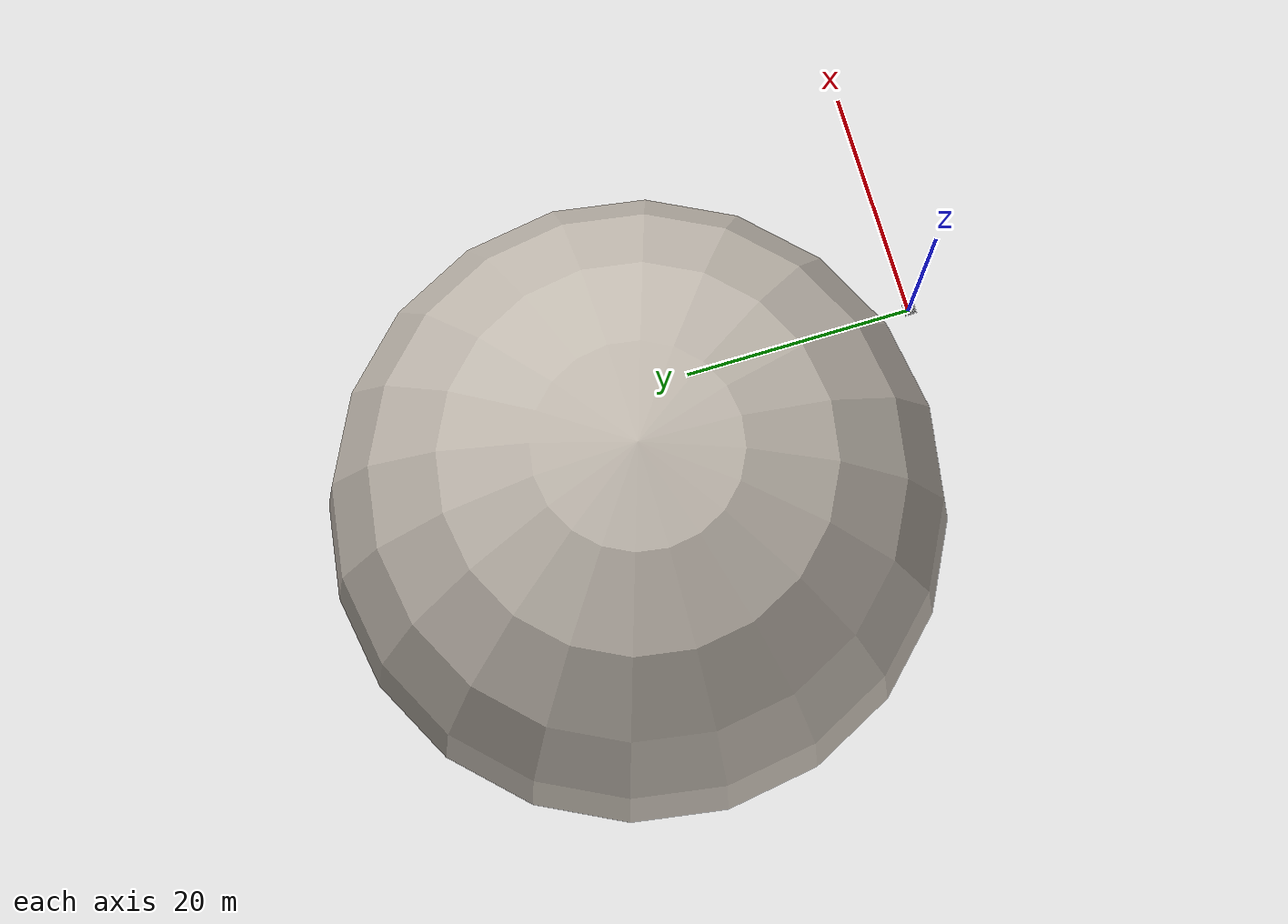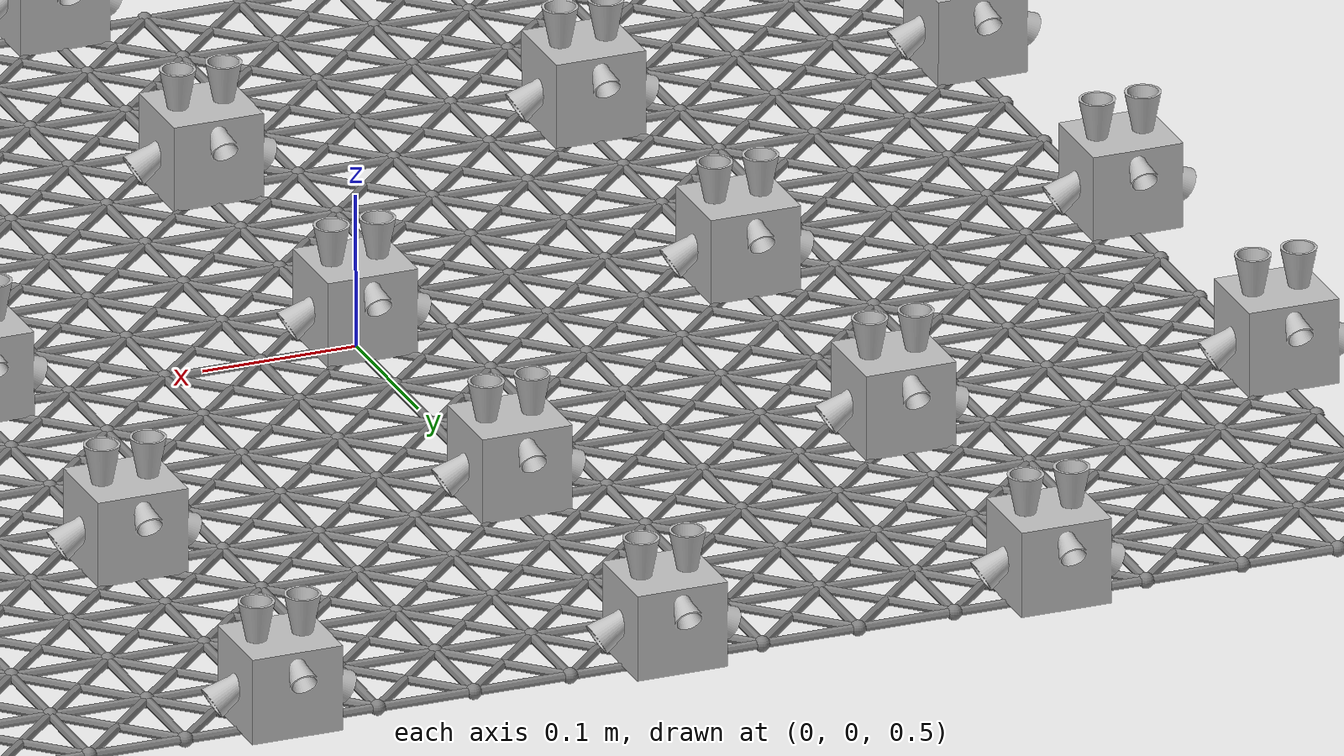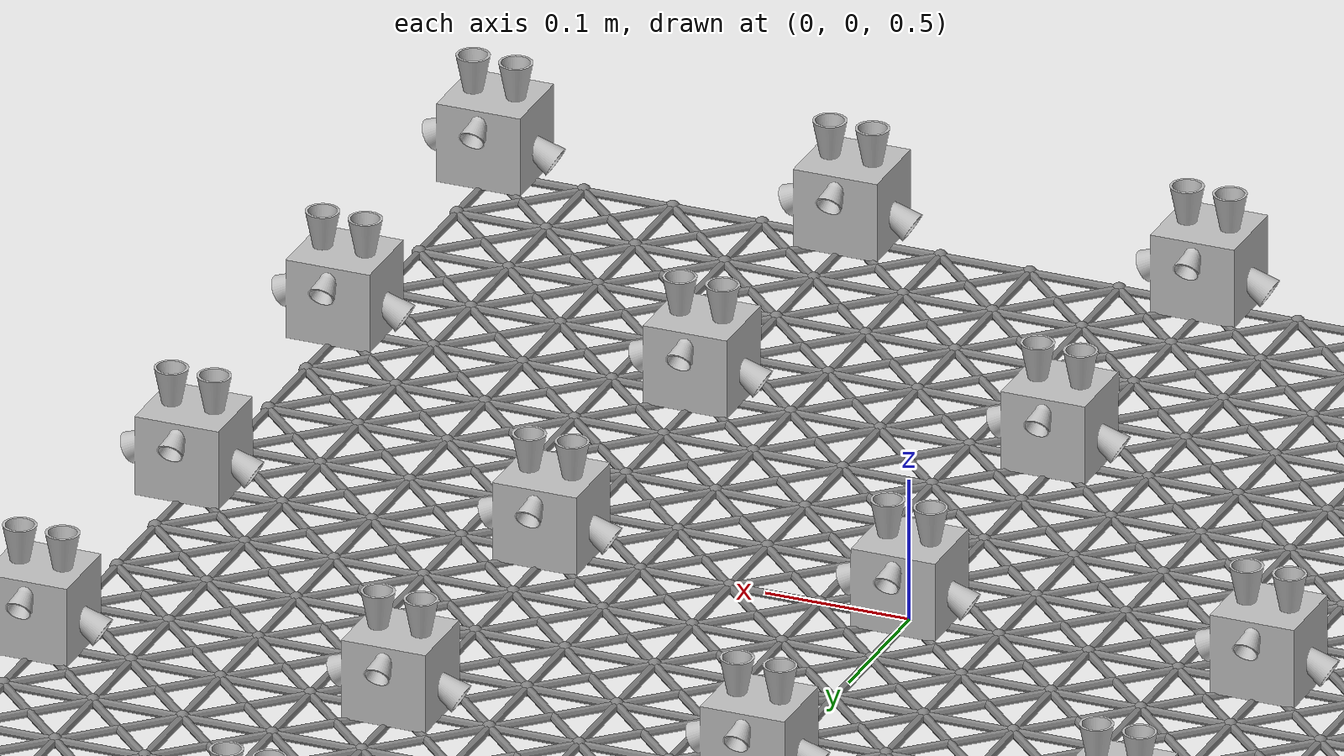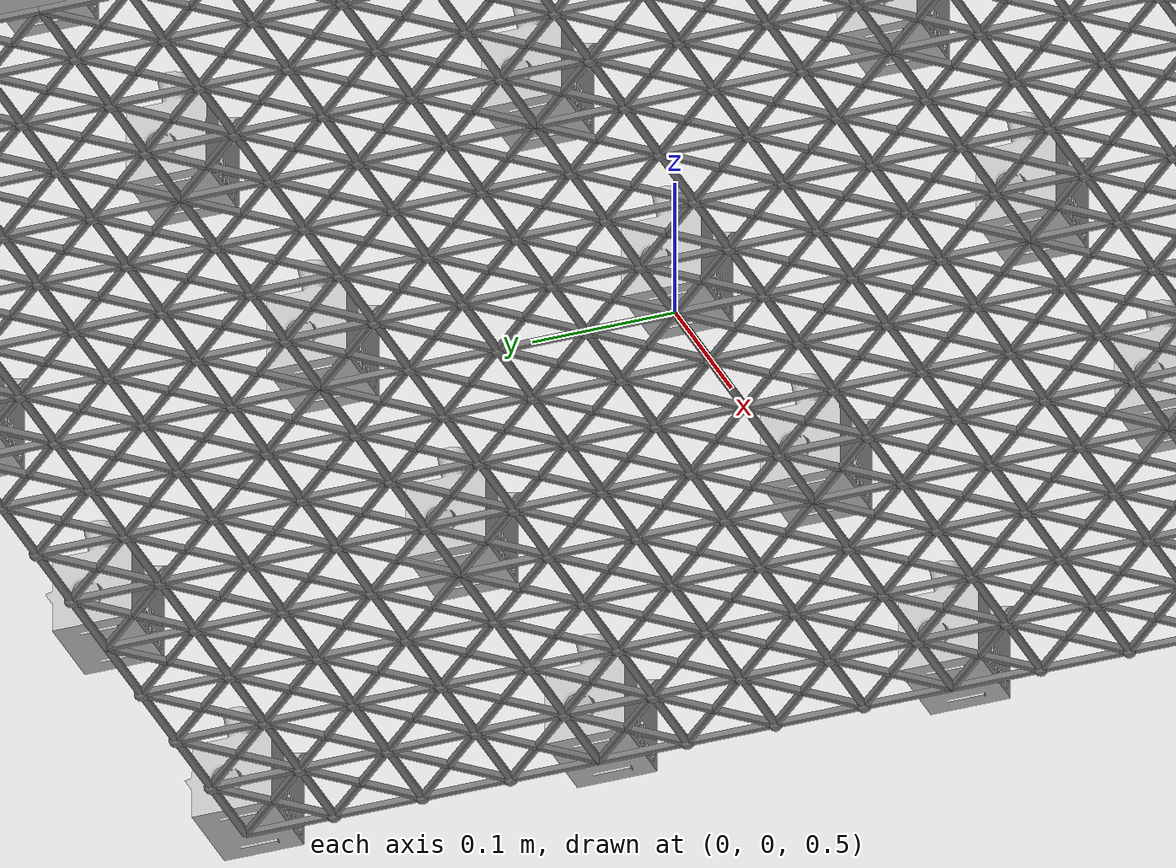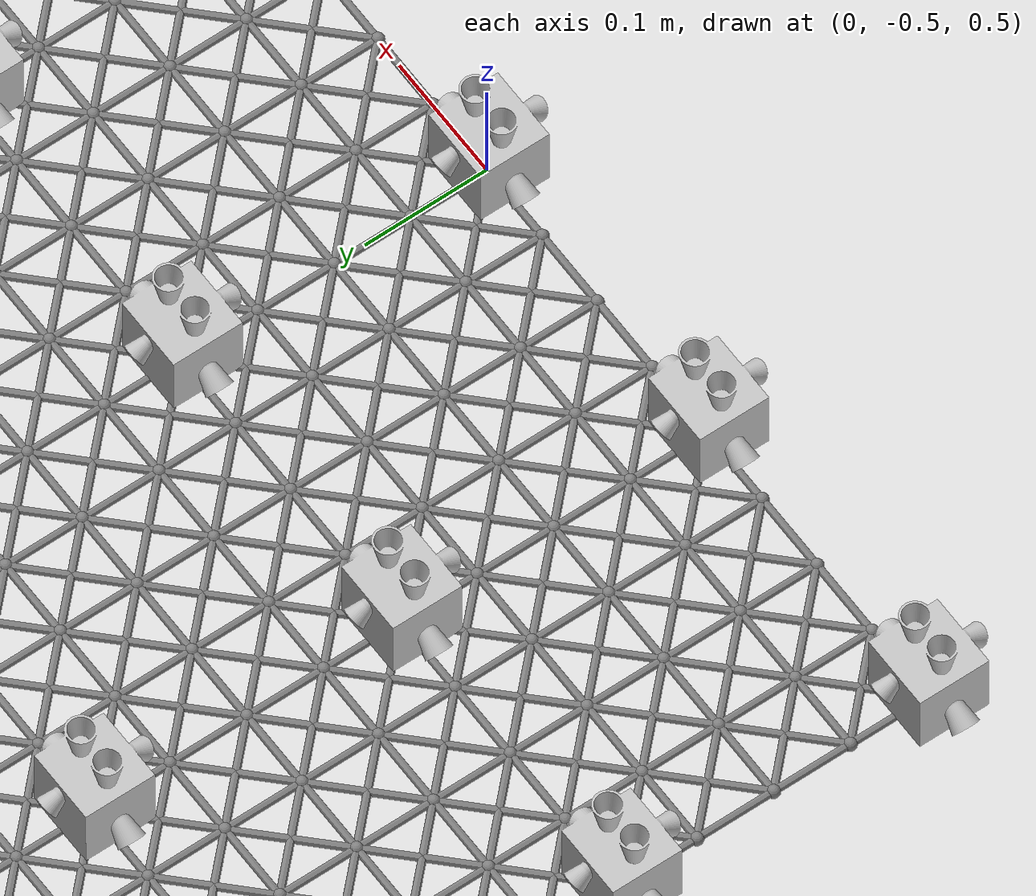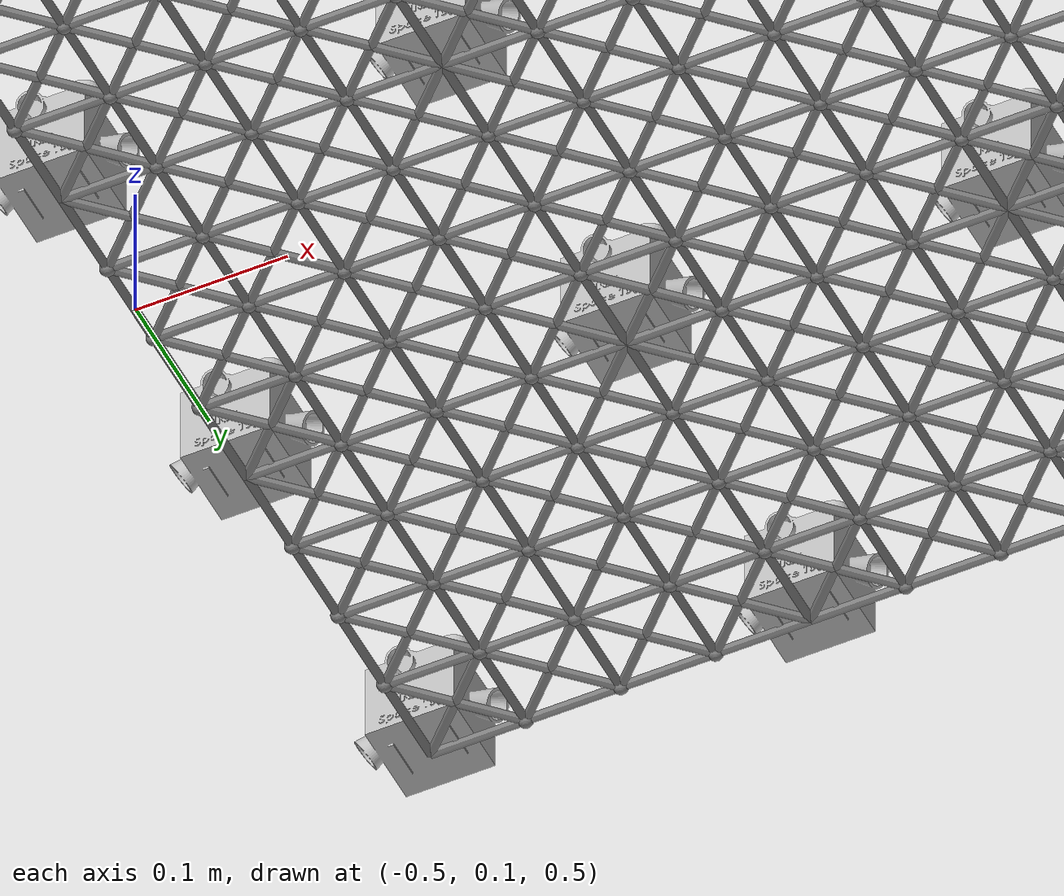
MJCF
<mujoco model="Skydio X2">
  <compiler autolimits="true" assetdir="assets"/>
  <option timestep="0.005"/>  <!-- Updated timestep -->
  <option gravity="0 0 -0.0"/>
  <default>
    <default class="ball">
        <geom size="0.005" mass="6.920415224913495e-05"/>
    </default>
    <default class="x2">
      <geom mass="0"/>
      <motor ctrlrange="0 13"/>
      <default class="visual">
        <geom group="2" type="mesh" contype="0" conaffinity="0"/>
      </default>
      <default class="collision">
        <geom group="3" type="box"/>
      </default>
      <site group="5"/>
    </default>
  </default>

  <asset>
    <texture type="2d" file="X2_lowpoly_texture_SpinningProps_1024.png"/>
    <material name="phong3SG" texture="X2_lowpoly_texture_SpinningProps_1024"/>
    <material name="invisible" rgba="0 0 0 0"/>
    <mesh class="x2" file="X2_lowpoly.obj" scale="0.0015 0.0015 0.0015"/>
  </asset>

  <asset>
    <!-- Define the STL mesh -->
    <mesh name="drone_body" file="tugnew4.stl" scale="0.0018 0.0018 0.0018"/>

    <!-- Optional material -->
    <material name="drone_material" rgba="0.75 0.75 0.75 1"/>
  </asset>

  <asset>
    <texture type="skybox" builtin="gradient" rgb1="0.3 0.5 0.7" rgb2="0 0 0" width="512" height="3072"/>
    <texture type="2d" name="groundplane" builtin="checker" mark="edge" rgb1="0.2 0.3 0.4" rgb2="0.1 0.2 0.3"
      markrgb="0.8 0.8 0.8" width="300" height="300"/>
    <material name="groundplane" texture="groundplane" texuniform="true" texrepeat="5 5" reflectance="0.2"/>
  </asset>

  <asset>
    <!-- Define the texture -->
    <texture name="earth_texture" type="2d" file="earth2.png" />

    <!-- Define the material that uses the texture -->
    <material name="earth_material" texture="earth_texture" texuniform="false"/>
  </asset>

  <worldbody>
    <light directional="true" pos="0 0 3" castshadow="false"/>
    <geom name="earthp"  pos="-2 25 -43" size="32" type="sphere" material="earth_material" contype="0" conaffinity="0"/>

    <body name="quad_1" pos="-0.5000 -0.5000 0.5" childclass="x2">
        <joint type="free" damping="0.05"/>
        <geom material="drone_material" mesh="drone_body" class="visual"  pos="0.05 -0.045 0" quat="0 0 1 1"/>
        <geom class="collision" size=".009 .00405 .003" pos=".006 0 .003"/>
        <geom class="collision" size=".009 .00405 .003" pos=".006 0 .009"/>
        <geom class="collision" size=".0075 .00405 .003" pos="-.0105 0 .00975"/>
        <geom class="collision" size=".00345 .00255 .0015" pos="-.02055 .0012 .00975" quat="1 0 0 1"/>
        <geom name="point_mass_1" type="sphere" size="0.012" pos="0 0 0" mass="0.040069204152249134" material="invisible"/>
        <site name="ball_1_1" pos="0 0 0"/>
    </body>

    <body pos="-0.4375 -0.5000 0.5">
        <joint type="free" damping="0.001"/>
        <geom class="ball"/>
        <site name="ball_1_2" pos="0 0 0"/>
    </body>

    <body pos="-0.3750 -0.5000 0.5">
        <joint type="free" damping="0.001"/>
        <geom class="ball"/>
        <site name="ball_1_3" pos="0 0 0"/>
    </body>

    <body pos="-0.3125 -0.5000 0.5">
        <joint type="free" damping="0.001"/>
        <geom class="ball"/>
        <site name="ball_1_4" pos="0 0 0"/>
    </body>

    <body name="quad_2" pos="-0.2500 -0.5000 0.5" childclass="x2">
        <joint type="free" damping="0.05"/>
        <geom material="drone_material" mesh="drone_body" class="visual"  pos="0.05 -0.045 0" quat="0 0 1 1"/>
        <geom class="collision" size=".009 .00405 .003" pos=".006 0 .003"/>
        <geom class="collision" size=".009 .00405 .003" pos=".006 0 .009"/>
        <geom class="collision" size=".0075 .00405 .003" pos="-.0105 0 .00975"/>
        <geom class="collision" size=".00345 .00255 .0015" pos="-.02055 .0012 .00975" quat="1 0 0 1"/>
        <geom name="point_mass_2" type="sphere" size="0.012" pos="0 0 0" mass="0.040069204152249134" material="invisible"/>
        <site name="ball_1_5" pos="0 0 0"/>
    </body>

    <body pos="-0.1875 -0.5000 0.5">
        <joint type="free" damping="0.001"/>
        <geom class="ball"/>
        <site name="ball_1_6" pos="0 0 0"/>
    </body>

    <body pos="-0.1250 -0.5000 0.5">
        <joint type="free" damping="0.001"/>
        <geom class="ball"/>
        <site name="ball_1_7" pos="0 0 0"/>
    </body>

    <body pos="-0.0625 -0.5000 0.5">
        <joint type="free" damping="0.001"/>
        <geom class="ball"/>
        <site name="ball_1_8" pos="0 0 0"/>
    </body>

    <body name="quad_3" pos="0.0000 -0.5000 0.5" childclass="x2">
        <joint type="free" damping="0.05"/>
        <geom material="drone_material" mesh="drone_body" class="visual"  pos="0.05 -0.045 0" quat="0 0 1 1"/>
        <geom class="collision" size=".009 .00405 .003" pos=".006 0 .003"/>
        <geom class="collision" size=".009 .00405 .003" pos=".006 0 .009"/>
        <geom class="collision" size=".0075 .00405 .003" pos="-.0105 0 .00975"/>
        <geom class="collision" size=".00345 .00255 .0015" pos="-.02055 .0012 .00975" quat="1 0 0 1"/>
        <geom name="point_mass_3" type="sphere" size="0.012" pos="0 0 0" mass="0.040069204152249134" material="invisible"/>
        <site name="ball_1_9" pos="0 0 0"/>
    </body>

    <body pos="0.0625 -0.5000 0.5">
        <joint type="free" damping="0.001"/>
        <geom class="ball"/>
        <site name="ball_1_10" pos="0 0 0"/>
    </body>

    <body pos="0.1250 -0.5000 0.5">
        <joint type="free" damping="0.001"/>
        <geom class="ball"/>
        <site name="ball_1_11" pos="0 0 0"/>
    </body>

    <body pos="0.1875 -0.5000 0.5">
        <joint type="free" damping="0.001"/>
        <geom class="ball"/>
        <site name="ball_1_12" pos="0 0 0"/>
    </body>

    <body name="quad_4" pos="0.2500 -0.5000 0.5" childclass="x2">
        <joint type="free" damping="0.05"/>
        <geom material="drone_material" mesh="drone_body" class="visual"  pos="0.05 -0.045 0" quat="0 0 1 1"/>
        <geom class="collision" size=".009 .00405 .003" pos=".006 0 .003"/>
        <geom class="collision" size=".009 .00405 .003" pos=".006 0 .009"/>
        <geom class="collision" size=".0075 .00405 .003" pos="-.0105 0 .00975"/>
        <geom class="collision" size=".00345 .00255 .0015" pos="-.02055 .0012 .00975" quat="1 0 0 1"/>
        <geom name="point_mass_4" type="sphere" size="0.012" pos="0 0 0" mass="0.040069204152249134" material="invisible"/>
        <site name="ball_1_13" pos="0 0 0"/>
    </body>

    <body pos="0.3125 -0.5000 0.5">
        <joint type="free" damping="0.001"/>
        <geom class="ball"/>
        <site name="ball_1_14" pos="0 0 0"/>
    </body>

    <body pos="0.3750 -0.5000 0.5">
        <joint type="free" damping="0.001"/>
        <geom class="ball"/>
        <site name="ball_1_15" pos="0 0 0"/>
    </body>

    <body pos="0.4375 -0.5000 0.5">
        <joint type="free" damping="0.001"/>
        <geom class="ball"/>
        <site name="ball_1_16" pos="0 0 0"/>
    </body>

    <body name="quad_5" pos="0.5000 -0.5000 0.5" childclass="x2">
        <joint type="free" damping="0.05"/>
        <geom material="drone_material" mesh="drone_body" class="visual"  pos="0.05 -0.045 0" quat="0 0 1 1"/>
        <geom class="collision" size=".009 .00405 .003" pos=".006 0 .003"/>
        <geom class="collision" size=".009 .00405 .003" pos=".006 0 .009"/>
        <geom class="collision" size=".0075 .00405 .003" pos="-.0105 0 .00975"/>
        <geom class="collision" size=".00345 .00255 .0015" pos="-.02055 .0012 .00975" quat="1 0 0 1"/>
        <geom name="point_mass_5" type="sphere" size="0.012" pos="0 0 0" mass="0.040069204152249134" material="invisible"/>
        <site name="ball_1_17" pos="0 0 0"/>
    </body>

    <body pos="-0.5000 -0.4375 0.5">
        <joint type="free" damping="0.001"/>
        <geom class="ball"/>
        <site name="ball_2_1" pos="0 0 0"/>
    </body>

    <body pos="-0.4375 -0.4375 0.5">
        <joint type="free" damping="0.001"/>
        <geom class="ball"/>
        <site name="ball_2_2" pos="0 0 0"/>
    </body>

    <body pos="-0.3750 -0.4375 0.5">
        <joint type="free" damping="0.001"/>
        <geom class="ball"/>
        <site name="ball_2_3" pos="0 0 0"/>
    </body>

    <body pos="-0.3125 -0.4375 0.5">
        <joint type="free" damping="0.001"/>
        <geom class="ball"/>
        <site name="ball_2_4" pos="0 0 0"/>
    </body>

    <body pos="-0.2500 -0.4375 0.5">
        <joint type="free" damping="0.001"/>
        <geom class="ball"/>
        <site name="ball_2_5" pos="0 0 0"/>
    </body>

    <body pos="-0.1875 -0.4375 0.5">
        <joint type="free" damping="0.001"/>
        <geom class="ball"/>
        <site name="ball_2_6" pos="0 0 0"/>
    </body>

    <body pos="-0.1250 -0.4375 0.5">
        <joint type="free" damping="0.001"/>
        <geom class="ball"/>
        <site name="ball_2_7" pos="0 0 0"/>
    </body>

    <body pos="-0.0625 -0.4375 0.5">
        <joint type="free" damping="0.001"/>
        <geom class="ball"/>
        <site name="ball_2_8" pos="0 0 0"/>
    </body>

    <body pos="0.0000 -0.4375 0.5">
        <joint type="free" damping="0.001"/>
        <geom class="ball"/>
        <site name="ball_2_9" pos="0 0 0"/>
    </body>

    <body pos="0.0625 -0.4375 0.5">
        <joint type="free" damping="0.001"/>
        <geom class="ball"/>
        <site name="ball_2_10" pos="0 0 0"/>
    </body>

    <body pos="0.1250 -0.4375 0.5">
        <joint type="free" damping="0.001"/>
        <geom class="ball"/>
        <site name="ball_2_11" pos="0 0 0"/>
    </body>

    <body pos="0.1875 -0.4375 0.5">
        <joint type="free" damping="0.001"/>
        <geom class="ball"/>
        <site name="ball_2_12" pos="0 0 0"/>
    </body>

    <body pos="0.2500 -0.4375 0.5">
        <joint type="free" damping="0.001"/>
        <geom class="ball"/>
        <site name="ball_2_13" pos="0 0 0"/>
    </body>

    <body pos="0.3125 -0.4375 0.5">
        <joint type="free" damping="0.001"/>
        <geom class="ball"/>
        <site name="ball_2_14" pos="0 0 0"/>
    </body>

    <body pos="0.3750 -0.4375 0.5">
        <joint type="free" damping="0.001"/>
        <geom class="ball"/>
        <site name="ball_2_15" pos="0 0 0"/>
    </body>

    <body pos="0.4375 -0.4375 0.5">
        <joint type="free" damping="0.001"/>
        <geom class="ball"/>
        <site name="ball_2_16" pos="0 0 0"/>
    </body>

    <body pos="0.5000 -0.4375 0.5">
        <joint type="free" damping="0.001"/>
        <geom class="ball"/>
        <site name="ball_2_17" pos="0 0 0"/>
    </body>

    <body pos="-0.5000 -0.3750 0.5">
        <joint type="free" damping="0.001"/>
        <geom class="ball"/>
        <site name="ball_3_1" pos="0 0 0"/>
    </body>

    <body pos="-0.4375 -0.3750 0.5">
        <joint type="free" damping="0.001"/>
        <geom class="ball"/>
        <site name="ball_3_2" pos="0 0 0"/>
    </body>

    <body pos="-0.3750 -0.3750 0.5">
        <joint type="free" damping="0.001"/>
        <geom class="ball"/>
        <site name="ball_3_3" pos="0 0 0"/>
    </body>

    <body pos="-0.3125 -0.3750 0.5">
        <joint type="free" damping="0.001"/>
        <geom class="ball"/>
        <site name="ball_3_4" pos="0 0 0"/>
    </body>

    <body pos="-0.2500 -0.3750 0.5">
        <joint type="free" damping="0.001"/>
        <geom class="ball"/>
        <site name="ball_3_5" pos="0 0 0"/>
    </body>

    <body pos="-0.1875 -0.3750 0.5">
        <joint type="free" damping="0.001"/>
        <geom class="ball"/>
        <site name="ball_3_6" pos="0 0 0"/>
    </body>

    <body pos="-0.1250 -0.3750 0.5">
        <joint type="free" damping="0.001"/>
        <geom class="ball"/>
        <site name="ball_3_7" pos="0 0 0"/>
    </body>

    <body pos="-0.0625 -0.3750 0.5">
        <joint type="free" damping="0.001"/>
        <geom class="ball"/>
        <site name="ball_3_8" pos="0 0 0"/>
    </body>

    <body pos="0.0000 -0.3750 0.5">
        <joint type="free" damping="0.001"/>
        <geom class="ball"/>
        <site name="ball_3_9" pos="0 0 0"/>
    </body>

    <body pos="0.0625 -0.3750 0.5">
        <joint type="free" damping="0.001"/>
        <geom class="ball"/>
        <site name="ball_3_10" pos="0 0 0"/>
    </body>

    <body pos="0.1250 -0.3750 0.5">
        <joint type="free" damping="0.001"/>
        <geom class="ball"/>
        <site name="ball_3_11" pos="0 0 0"/>
    </body>

    <body pos="0.1875 -0.3750 0.5">
        <joint type="free" damping="0.001"/>
        <geom class="ball"/>
        <site name="ball_3_12" pos="0 0 0"/>
    </body>

    <body pos="0.2500 -0.3750 0.5">
        <joint type="free" damping="0.001"/>
        <geom class="ball"/>
        <site name="ball_3_13" pos="0 0 0"/>
    </body>

    <body pos="0.3125 -0.3750 0.5">
        <joint type="free" damping="0.001"/>
        <geom class="ball"/>
        <site name="ball_3_14" pos="0 0 0"/>
    </body>

    <body pos="0.3750 -0.3750 0.5">
        <joint type="free" damping="0.001"/>
        <geom class="ball"/>
        <site name="ball_3_15" pos="0 0 0"/>
    </body>

    <body pos="0.4375 -0.3750 0.5">
        <joint type="free" damping="0.001"/>
        <geom class="ball"/>
        <site name="ball_3_16" pos="0 0 0"/>
    </body>

    <body pos="0.5000 -0.3750 0.5">
        <joint type="free" damping="0.001"/>
        <geom class="ball"/>
        <site name="ball_3_17" pos="0 0 0"/>
    </body>

    <body pos="-0.5000 -0.3125 0.5">
        <joint type="free" damping="0.001"/>
        <geom class="ball"/>
        <site name="ball_4_1" pos="0 0 0"/>
    </body>

    <body pos="-0.4375 -0.3125 0.5">
        <joint type="free" damping="0.001"/>
        <geom class="ball"/>
        <site name="ball_4_2" pos="0 0 0"/>
    </body>

    <body pos="-0.3750 -0.3125 0.5">
        <joint type="free" damping="0.001"/>
        <geom class="ball"/>
        <site name="ball_4_3" pos="0 0 0"/>
    </body>

    <body pos="-0.3125 -0.3125 0.5">
        <joint type="free" damping="0.001"/>
        <geom class="ball"/>
        <site name="ball_4_4" pos="0 0 0"/>
    </body>

    <body pos="-0.2500 -0.3125 0.5">
        <joint type="free" damping="0.001"/>
        <geom class="ball"/>
        <site name="ball_4_5" pos="0 0 0"/>
    </body>

    <body pos="-0.1875 -0.3125 0.5">
        <joint type="free" damping="0.001"/>
        <geom class="ball"/>
        <site name="ball_4_6" pos="0 0 0"/>
    </body>

    <body pos="-0.1250 -0.3125 0.5">
        <joint type="free" damping="0.001"/>
        <geom class="ball"/>
        <site name="ball_4_7" pos="0 0 0"/>
    </body>

    <body pos="-0.0625 -0.3125 0.5">
        <joint type="free" damping="0.001"/>
        <geom class="ball"/>
        <site name="ball_4_8" pos="0 0 0"/>
    </body>

    <body pos="0.0000 -0.3125 0.5">
        <joint type="free" damping="0.001"/>
        <geom class="ball"/>
        <site name="ball_4_9" pos="0 0 0"/>
    </body>

    <body pos="0.0625 -0.3125 0.5">
        <joint type="free" damping="0.001"/>
        <geom class="ball"/>
        <site name="ball_4_10" pos="0 0 0"/>
    </body>

    <body pos="0.1250 -0.3125 0.5">
        <joint type="free" damping="0.001"/>
        <geom class="ball"/>
        <site name="ball_4_11" pos="0 0 0"/>
    </body>

    <body pos="0.1875 -0.3125 0.5">
        <joint type="free" damping="0.001"/>
        <geom class="ball"/>
        <site name="ball_4_12" pos="0 0 0"/>
    </body>

    <body pos="0.2500 -0.3125 0.5">
        <joint type="free" damping="0.001"/>
        <geom class="ball"/>
        <site name="ball_4_13" pos="0 0 0"/>
    </body>

    <body pos="0.3125 -0.3125 0.5">
        <joint type="free" damping="0.001"/>
        <geom class="ball"/>
        <site name="ball_4_14" pos="0 0 0"/>
    </body>

    <body pos="0.3750 -0.3125 0.5">
        <joint type="free" damping="0.001"/>
        <geom class="ball"/>
        <site name="ball_4_15" pos="0 0 0"/>
    </body>

    <body pos="0.4375 -0.3125 0.5">
        <joint type="free" damping="0.001"/>
        <geom class="ball"/>
        <site name="ball_4_16" pos="0 0 0"/>
    </body>

    <body pos="0.5000 -0.3125 0.5">
        <joint type="free" damping="0.001"/>
        <geom class="ball"/>
        <site name="ball_4_17" pos="0 0 0"/>
    </body>

    <body name="quad_6" pos="-0.5000 -0.2500 0.5" childclass="x2">
        <joint type="free" damping="0.05"/>
        <geom material="drone_material" mesh="drone_body" class="visual"  pos="0.05 -0.045 0" quat="0 0 1 1"/>
        <geom class="collision" size=".009 .00405 .003" pos=".006 0 .003"/>
        <geom class="collision" size=".009 .00405 .003" pos=".006 0 .009"/>
        <geom class="collision" size=".0075 .00405 .003" pos="-.0105 0 .00975"/>
        <geom class="collision" size=".00345 .00255 .0015" pos="-.02055 .0012 .00975" quat="1 0 0 1"/>
        <geom name="point_mass_6" type="sphere" size="0.012" pos="0 0 0" mass="0.040069204152249134" material="invisible"/>
        <site name="ball_5_1" pos="0 0 0"/>
    </body>

    <body pos="-0.4375 -0.2500 0.5">
        <joint type="free" damping="0.001"/>
        <geom class="ball"/>
        <site name="ball_5_2" pos="0 0 0"/>
    </body>

    <body pos="-0.3750 -0.2500 0.5">
        <joint type="free" damping="0.001"/>
        <geom class="ball"/>
        <site name="ball_5_3" pos="0 0 0"/>
    </body>

    <body pos="-0.3125 -0.2500 0.5">
        <joint type="free" damping="0.001"/>
        <geom class="ball"/>
        <site name="ball_5_4" pos="0 0 0"/>
    </body>

    <body name="quad_7" pos="-0.2500 -0.2500 0.5" childclass="x2">
        <joint type="free" damping="0.05"/>
        <geom material="drone_material" mesh="drone_body" class="visual"  pos="0.05 -0.045 0" quat="0 0 1 1"/>
        <geom class="collision" size=".009 .00405 .003" pos=".006 0 .003"/>
        <geom class="collision" size=".009 .00405 .003" pos=".006 0 .009"/>
        <geom class="collision" size=".0075 .00405 .003" pos="-.0105 0 .00975"/>
        <geom class="collision" size=".00345 .00255 .0015" pos="-.02055 .0012 .00975" quat="1 0 0 1"/>
        <geom name="point_mass_7" type="sphere" size="0.012" pos="0 0 0" mass="0.040069204152249134" material="invisible"/>
        <site name="ball_5_5" pos="0 0 0"/>
    </body>

    <body pos="-0.1875 -0.2500 0.5">
        <joint type="free" damping="0.001"/>
        <geom class="ball"/>
        <site name="ball_5_6" pos="0 0 0"/>
    </body>

    <body pos="-0.1250 -0.2500 0.5">
        <joint type="free" damping="0.001"/>
        <geom class="ball"/>
        <site name="ball_5_7" pos="0 0 0"/>
    </body>

    <body pos="-0.0625 -0.2500 0.5">
        <joint type="free" damping="0.001"/>
        <geom class="ball"/>
        <site name="ball_5_8" pos="0 0 0"/>
    </body>

    <body name="quad_8" pos="0.0000 -0.2500 0.5" childclass="x2">
        <joint type="free" damping="0.05"/>
        <geom material="drone_material" mesh="drone_body" class="visual"  pos="0.05 -0.045 0" quat="0 0 1 1"/>
        <geom class="collision" size=".009 .00405 .003" pos=".006 0 .003"/>
        <geom class="collision" size=".009 .00405 .003" pos=".006 0 .009"/>
        <geom class="collision" size=".0075 .00405 .003" pos="-.0105 0 .00975"/>
        <geom class="collision" size=".00345 .00255 .0015" pos="-.02055 .0012 .00975" quat="1 0 0 1"/>
        <geom name="point_mass_8" type="sphere" size="0.012" pos="0 0 0" mass="0.040069204152249134" material="invisible"/>
        <site name="ball_5_9" pos="0 0 0"/>
    </body>

    <body pos="0.0625 -0.2500 0.5">
        <joint type="free" damping="0.001"/>
        <geom class="ball"/>
        <site name="ball_5_10" pos="0 0 0"/>
    </body>

    <body pos="0.1250 -0.2500 0.5">
        <joint type="free" damping="0.001"/>
        <geom class="ball"/>
        <site name="ball_5_11" pos="0 0 0"/>
    </body>

    <body pos="0.1875 -0.2500 0.5">
        <joint type="free" damping="0.001"/>
        <geom class="ball"/>
        <site name="ball_5_12" pos="0 0 0"/>
    </body>

    <body name="quad_9" pos="0.2500 -0.2500 0.5" childclass="x2">
        <joint type="free" damping="0.05"/>
        <geom material="drone_material" mesh="drone_body" class="visual"  pos="0.05 -0.045 0" quat="0 0 1 1"/>
        <geom class="collision" size=".009 .00405 .003" pos=".006 0 .003"/>
        <geom class="collision" size=".009 .00405 .003" pos=".006 0 .009"/>
        <geom class="collision" size=".0075 .00405 .003" pos="-.0105 0 .00975"/>
        <geom class="collision" size=".00345 .00255 .0015" pos="-.02055 .0012 .00975" quat="1 0 0 1"/>
        <geom name="point_mass_9" type="sphere" size="0.012" pos="0 0 0" mass="0.040069204152249134" material="invisible"/>
        <site name="ball_5_13" pos="0 0 0"/>
    </body>

    <body pos="0.3125 -0.2500 0.5">
        <joint type="free" damping="0.001"/>
        <geom class="ball"/>
        <site name="ball_5_14" pos="0 0 0"/>
    </body>

    <body pos="0.3750 -0.2500 0.5">
        <joint type="free" damping="0.001"/>
        <geom class="ball"/>
        <site name="ball_5_15" pos="0 0 0"/>
    </body>

    <body pos="0.4375 -0.2500 0.5">
        <joint type="free" damping="0.001"/>
        <geom class="ball"/>
        <site name="ball_5_16" pos="0 0 0"/>
    </body>

    <body name="quad_10" pos="0.5000 -0.2500 0.5" childclass="x2">
        <joint type="free" damping="0.05"/>
        <geom material="drone_material" mesh="drone_body" class="visual"  pos="0.05 -0.045 0" quat="0 0 1 1"/>
        <geom class="collision" size=".009 .00405 .003" pos=".006 0 .003"/>
        <geom class="collision" size=".009 .00405 .003" pos=".006 0 .009"/>
        <geom class="collision" size=".0075 .00405 .003" pos="-.0105 0 .00975"/>
        <geom class="collision" size=".00345 .00255 .0015" pos="-.02055 .0012 .00975" quat="1 0 0 1"/>
        <geom name="point_mass_10" type="sphere" size="0.012" pos="0 0 0" mass="0.040069204152249134" material="invisible"/>
        <site name="ball_5_17" pos="0 0 0"/>
    </body>

    <body pos="-0.5000 -0.1875 0.5">
        <joint type="free" damping="0.001"/>
        <geom class="ball"/>
        <site name="ball_6_1" pos="0 0 0"/>
    </body>

    <body pos="-0.4375 -0.1875 0.5">
        <joint type="free" damping="0.001"/>
        <geom class="ball"/>
        <site name="ball_6_2" pos="0 0 0"/>
    </body>

    <body pos="-0.3750 -0.1875 0.5">
        <joint type="free" damping="0.001"/>
        <geom class="ball"/>
        <site name="ball_6_3" pos="0 0 0"/>
    </body>

    <body pos="-0.3125 -0.1875 0.5">
        <joint type="free" damping="0.001"/>
        <geom class="ball"/>
        <site name="ball_6_4" pos="0 0 0"/>
    </body>

    <body pos="-0.2500 -0.1875 0.5">
        <joint type="free" damping="0.001"/>
        <geom class="ball"/>
        <site name="ball_6_5" pos="0 0 0"/>
    </body>

    <body pos="-0.1875 -0.1875 0.5">
        <joint type="free" damping="0.001"/>
        <geom class="ball"/>
        <site name="ball_6_6" pos="0 0 0"/>
    </body>

    <body pos="-0.1250 -0.1875 0.5">
        <joint type="free" damping="0.001"/>
        <geom class="ball"/>
        <site name="ball_6_7" pos="0 0 0"/>
    </body>

    <body pos="-0.0625 -0.1875 0.5">
        <joint type="free" damping="0.001"/>
        <geom class="ball"/>
        <site name="ball_6_8" pos="0 0 0"/>
    </body>

    <body pos="0.0000 -0.1875 0.5">
        <joint type="free" damping="0.001"/>
        <geom class="ball"/>
        <site name="ball_6_9" pos="0 0 0"/>
    </body>

    <body pos="0.0625 -0.1875 0.5">
        <joint type="free" damping="0.001"/>
        <geom class="ball"/>
        <site name="ball_6_10" pos="0 0 0"/>
    </body>

    <body pos="0.1250 -0.1875 0.5">
        <joint type="free" damping="0.001"/>
        <geom class="ball"/>
        <site name="ball_6_11" pos="0 0 0"/>
    </body>

    <body pos="0.1875 -0.1875 0.5">
        <joint type="free" damping="0.001"/>
        <geom class="ball"/>
        <site name="ball_6_12" pos="0 0 0"/>
    </body>

    <body pos="0.2500 -0.1875 0.5">
        <joint type="free" damping="0.001"/>
        <geom class="ball"/>
        <site name="ball_6_13" pos="0 0 0"/>
    </body>

    <body pos="0.3125 -0.1875 0.5">
        <joint type="free" damping="0.001"/>
        <geom class="ball"/>
        <site name="ball_6_14" pos="0 0 0"/>
    </body>

    <body pos="0.3750 -0.1875 0.5">
        <joint type="free" damping="0.001"/>
        <geom class="ball"/>
        <site name="ball_6_15" pos="0 0 0"/>
    </body>

    <body pos="0.4375 -0.1875 0.5">
        <joint type="free" damping="0.001"/>
        <geom class="ball"/>
        <site name="ball_6_16" pos="0 0 0"/>
    </body>

    <body pos="0.5000 -0.1875 0.5">
        <joint type="free" damping="0.001"/>
        <geom class="ball"/>
        <site name="ball_6_17" pos="0 0 0"/>
    </body>

    <body pos="-0.5000 -0.1250 0.5">
        <joint type="free" damping="0.001"/>
        <geom class="ball"/>
        <site name="ball_7_1" pos="0 0 0"/>
    </body>

    <body pos="-0.4375 -0.1250 0.5">
        <joint type="free" damping="0.001"/>
        <geom class="ball"/>
        <site name="ball_7_2" pos="0 0 0"/>
    </body>

    <body pos="-0.3750 -0.1250 0.5">
        <joint type="free" damping="0.001"/>
        <geom class="ball"/>
        <site name="ball_7_3" pos="0 0 0"/>
    </body>

    <body pos="-0.3125 -0.1250 0.5">
        <joint type="free" damping="0.001"/>
        <geom class="ball"/>
        <site name="ball_7_4" pos="0 0 0"/>
    </body>

    <body pos="-0.2500 -0.1250 0.5">
        <joint type="free" damping="0.001"/>
        <geom class="ball"/>
        <site name="ball_7_5" pos="0 0 0"/>
    </body>

    <body pos="-0.1875 -0.1250 0.5">
        <joint type="free" damping="0.001"/>
        <geom class="ball"/>
        <site name="ball_7_6" pos="0 0 0"/>
    </body>

    <body pos="-0.1250 -0.1250 0.5">
        <joint type="free" damping="0.001"/>
        <geom class="ball"/>
        <site name="ball_7_7" pos="0 0 0"/>
    </body>

    <body pos="-0.0625 -0.1250 0.5">
        <joint type="free" damping="0.001"/>
        <geom class="ball"/>
        <site name="ball_7_8" pos="0 0 0"/>
    </body>

    <body pos="0.0000 -0.1250 0.5">
        <joint type="free" damping="0.001"/>
        <geom class="ball"/>
        <site name="ball_7_9" pos="0 0 0"/>
    </body>

    <body pos="0.0625 -0.1250 0.5">
        <joint type="free" damping="0.001"/>
        <geom class="ball"/>
        <site name="ball_7_10" pos="0 0 0"/>
    </body>

    <body pos="0.1250 -0.1250 0.5">
        <joint type="free" damping="0.001"/>
        <geom class="ball"/>
        <site name="ball_7_11" pos="0 0 0"/>
    </body>

    <body pos="0.1875 -0.1250 0.5">
        <joint type="free" damping="0.001"/>
        <geom class="ball"/>
        <site name="ball_7_12" pos="0 0 0"/>
    </body>

    <body pos="0.2500 -0.1250 0.5">
        <joint type="free" damping="0.001"/>
        <geom class="ball"/>
        <site name="ball_7_13" pos="0 0 0"/>
    </body>

    <body pos="0.3125 -0.1250 0.5">
        <joint type="free" damping="0.001"/>
        <geom class="ball"/>
        <site name="ball_7_14" pos="0 0 0"/>
    </body>

    <body pos="0.3750 -0.1250 0.5">
        <joint type="free" damping="0.001"/>
        <geom class="ball"/>
        <site name="ball_7_15" pos="0 0 0"/>
    </body>

    <body pos="0.4375 -0.1250 0.5">
        <joint type="free" damping="0.001"/>
        <geom class="ball"/>
        <site name="ball_7_16" pos="0 0 0"/>
    </body>

    <body pos="0.5000 -0.1250 0.5">
        <joint type="free" damping="0.001"/>
        <geom class="ball"/>
        <site name="ball_7_17" pos="0 0 0"/>
    </body>

    <body pos="-0.5000 -0.0625 0.5">
        <joint type="free" damping="0.001"/>
        <geom class="ball"/>
        <site name="ball_8_1" pos="0 0 0"/>
    </body>

    <body pos="-0.4375 -0.0625 0.5">
        <joint type="free" damping="0.001"/>
        <geom class="ball"/>
        <site name="ball_8_2" pos="0 0 0"/>
    </body>

    <body pos="-0.3750 -0.0625 0.5">
        <joint type="free" damping="0.001"/>
        <geom class="ball"/>
        <site name="ball_8_3" pos="0 0 0"/>
    </body>

    <body pos="-0.3125 -0.0625 0.5">
        <joint type="free" damping="0.001"/>
        <geom class="ball"/>
        <site name="ball_8_4" pos="0 0 0"/>
    </body>

    <body pos="-0.2500 -0.0625 0.5">
        <joint type="free" damping="0.001"/>
        <geom class="ball"/>
        <site name="ball_8_5" pos="0 0 0"/>
    </body>

    <body pos="-0.1875 -0.0625 0.5">
        <joint type="free" damping="0.001"/>
        <geom class="ball"/>
        <site name="ball_8_6" pos="0 0 0"/>
    </body>

    <body pos="-0.1250 -0.0625 0.5">
        <joint type="free" damping="0.001"/>
        <geom class="ball"/>
        <site name="ball_8_7" pos="0 0 0"/>
    </body>

    <body pos="-0.0625 -0.0625 0.5">
        <joint type="free" damping="0.001"/>
        <geom class="ball"/>
        <site name="ball_8_8" pos="0 0 0"/>
    </body>

    <body pos="0.0000 -0.0625 0.5">
        <joint type="free" damping="0.001"/>
        <geom class="ball"/>
        <site name="ball_8_9" pos="0 0 0"/>
    </body>

    <body pos="0.0625 -0.0625 0.5">
        <joint type="free" damping="0.001"/>
        <geom class="ball"/>
        <site name="ball_8_10" pos="0 0 0"/>
    </body>

    <body pos="0.1250 -0.0625 0.5">
        <joint type="free" damping="0.001"/>
        <geom class="ball"/>
        <site name="ball_8_11" pos="0 0 0"/>
    </body>

    <body pos="0.1875 -0.0625 0.5">
        <joint type="free" damping="0.001"/>
        <geom class="ball"/>
        <site name="ball_8_12" pos="0 0 0"/>
    </body>

    <body pos="0.2500 -0.0625 0.5">
        <joint type="free" damping="0.001"/>
        <geom class="ball"/>
        <site name="ball_8_13" pos="0 0 0"/>
    </body>

    <body pos="0.3125 -0.0625 0.5">
        <joint type="free" damping="0.001"/>
        <geom class="ball"/>
        <site name="ball_8_14" pos="0 0 0"/>
    </body>

    <body pos="0.3750 -0.0625 0.5">
        <joint type="free" damping="0.001"/>
        <geom class="ball"/>
        <site name="ball_8_15" pos="0 0 0"/>
    </body>

    <body pos="0.4375 -0.0625 0.5">
        <joint type="free" damping="0.001"/>
        <geom class="ball"/>
        <site name="ball_8_16" pos="0 0 0"/>
    </body>

    <body pos="0.5000 -0.0625 0.5">
        <joint type="free" damping="0.001"/>
        <geom class="ball"/>
        <site name="ball_8_17" pos="0 0 0"/>
    </body>

    <body name="quad_11" pos="-0.5000 0.0000 0.5" childclass="x2">
        <joint type="free" damping="0.05"/>
        <geom material="drone_material" mesh="drone_body" class="visual"  pos="0.05 -0.045 0" quat="0 0 1 1"/>
        <geom class="collision" size=".009 .00405 .003" pos=".006 0 .003"/>
        <geom class="collision" size=".009 .00405 .003" pos=".006 0 .009"/>
        <geom class="collision" size=".0075 .00405 .003" pos="-.0105 0 .00975"/>
        <geom class="collision" size=".00345 .00255 .0015" pos="-.02055 .0012 .00975" quat="1 0 0 1"/>
        <geom name="point_mass_11" type="sphere" size="0.012" pos="0 0 0" mass="0.040069204152249134" material="invisible"/>
        <site name="ball_9_1" pos="0 0 0"/>
    </body>

    <body pos="-0.4375 0.0000 0.5">
        <joint type="free" damping="0.001"/>
        <geom class="ball"/>
        <site name="ball_9_2" pos="0 0 0"/>
    </body>

    <body pos="-0.3750 0.0000 0.5">
        <joint type="free" damping="0.001"/>
        <geom class="ball"/>
        <site name="ball_9_3" pos="0 0 0"/>
    </body>

    <body pos="-0.3125 0.0000 0.5">
        <joint type="free" damping="0.001"/>
        <geom class="ball"/>
        <site name="ball_9_4" pos="0 0 0"/>
    </body>

    <body name="quad_12" pos="-0.2500 0.0000 0.5" childclass="x2">
        <joint type="free" damping="0.05"/>
        <geom material="drone_material" mesh="drone_body" class="visual"  pos="0.05 -0.045 0" quat="0 0 1 1"/>
        <geom class="collision" size=".009 .00405 .003" pos=".006 0 .003"/>
        <geom class="collision" size=".009 .00405 .003" pos=".006 0 .009"/>
        <geom class="collision" size=".0075 .00405 .003" pos="-.0105 0 .00975"/>
        <geom class="collision" size=".00345 .00255 .0015" pos="-.02055 .0012 .00975" quat="1 0 0 1"/>
        <geom name="point_mass_12" type="sphere" size="0.012" pos="0 0 0" mass="0.040069204152249134" material="invisible"/>
        <site name="ball_9_5" pos="0 0 0"/>
    </body>

    <body pos="-0.1875 0.0000 0.5">
        <joint type="free" damping="0.001"/>
        <geom class="ball"/>
        <site name="ball_9_6" pos="0 0 0"/>
    </body>

    <body pos="-0.1250 0.0000 0.5">
        <joint type="free" damping="0.001"/>
        <geom class="ball"/>
        <site name="ball_9_7" pos="0 0 0"/>
    </body>

    <body pos="-0.0625 0.0000 0.5">
        <joint type="free" damping="0.001"/>
        <geom class="ball"/>
        <site name="ball_9_8" pos="0 0 0"/>
    </body>

    <body name="quad_13" pos="0.0000 0.0000 0.5" childclass="x2">
        <joint type="free" damping="0.05"/>
        <geom material="drone_material" mesh="drone_body" class="visual"  pos="0.05 -0.045 0" quat="0 0 1 1"/>
        <geom class="collision" size=".009 .00405 .003" pos=".006 0 .003"/>
        <geom class="collision" size=".009 .00405 .003" pos=".006 0 .009"/>
        <geom class="collision" size=".0075 .00405 .003" pos="-.0105 0 .00975"/>
        <geom class="collision" size=".00345 .00255 .0015" pos="-.02055 .0012 .00975" quat="1 0 0 1"/>
        <geom name="point_mass_13" type="sphere" size="0.012" pos="0 0 0" mass="0.040069204152249134" material="invisible"/>
        <site name="ball_9_9" pos="0 0 0"/>
    </body>

    <body pos="0.0625 0.0000 0.5">
        <joint type="free" damping="0.001"/>
        <geom class="ball"/>
        <site name="ball_9_10" pos="0 0 0"/>
    </body>

    <body pos="0.1250 0.0000 0.5">
        <joint type="free" damping="0.001"/>
        <geom class="ball"/>
        <site name="ball_9_11" pos="0 0 0"/>
    </body>

    <body pos="0.1875 0.0000 0.5">
        <joint type="free" damping="0.001"/>
        <geom class="ball"/>
        <site name="ball_9_12" pos="0 0 0"/>
    </body>

    <body name="quad_14" pos="0.2500 0.0000 0.5" childclass="x2">
        <joint type="free" damping="0.05"/>
        <geom material="drone_material" mesh="drone_body" class="visual"  pos="0.05 -0.045 0" quat="0 0 1 1"/>
        <geom class="collision" size=".009 .00405 .003" pos=".006 0 .003"/>
        <geom class="collision" size=".009 .00405 .003" pos=".006 0 .009"/>
        <geom class="collision" size=".0075 .00405 .003" pos="-.0105 0 .00975"/>
        <geom class="collision" size=".00345 .00255 .0015" pos="-.02055 .0012 .00975" quat="1 0 0 1"/>
        <geom name="point_mass_14" type="sphere" size="0.012" pos="0 0 0" mass="0.040069204152249134" material="invisible"/>
        <site name="ball_9_13" pos="0 0 0"/>
    </body>

    <body pos="0.3125 0.0000 0.5">
        <joint type="free" damping="0.001"/>
        <geom class="ball"/>
        <site name="ball_9_14" pos="0 0 0"/>
    </body>

    <body pos="0.3750 0.0000 0.5">
        <joint type="free" damping="0.001"/>
        <geom class="ball"/>
        <site name="ball_9_15" pos="0 0 0"/>
    </body>

    <body pos="0.4375 0.0000 0.5">
        <joint type="free" damping="0.001"/>
        <geom class="ball"/>
        <site name="ball_9_16" pos="0 0 0"/>
    </body>

    <body name="quad_15" pos="0.5000 0.0000 0.5" childclass="x2">
        <joint type="free" damping="0.05"/>
        <geom material="drone_material" mesh="drone_body" class="visual"  pos="0.05 -0.045 0" quat="0 0 1 1"/>
        <geom class="collision" size=".009 .00405 .003" pos=".006 0 .003"/>
        <geom class="collision" size=".009 .00405 .003" pos=".006 0 .009"/>
        <geom class="collision" size=".0075 .00405 .003" pos="-.0105 0 .00975"/>
        <geom class="collision" size=".00345 .00255 .0015" pos="-.02055 .0012 .00975" quat="1 0 0 1"/>
        <geom name="point_mass_15" type="sphere" size="0.012" pos="0 0 0" mass="0.040069204152249134" material="invisible"/>
        <site name="ball_9_17" pos="0 0 0"/>
    </body>

    <body pos="-0.5000 0.0625 0.5">
        <joint type="free" damping="0.001"/>
        <geom class="ball"/>
        <site name="ball_10_1" pos="0 0 0"/>
    </body>

    <body pos="-0.4375 0.0625 0.5">
        <joint type="free" damping="0.001"/>
        <geom class="ball"/>
        <site name="ball_10_2" pos="0 0 0"/>
    </body>

    <body pos="-0.3750 0.0625 0.5">
        <joint type="free" damping="0.001"/>
        <geom class="ball"/>
        <site name="ball_10_3" pos="0 0 0"/>
    </body>

    <body pos="-0.3125 0.0625 0.5">
        <joint type="free" damping="0.001"/>
        <geom class="ball"/>
        <site name="ball_10_4" pos="0 0 0"/>
    </body>

    <body pos="-0.2500 0.0625 0.5">
        <joint type="free" damping="0.001"/>
        <geom class="ball"/>
        <site name="ball_10_5" pos="0 0 0"/>
    </body>

    <body pos="-0.1875 0.0625 0.5">
        <joint type="free" damping="0.001"/>
        <geom class="ball"/>
        <site name="ball_10_6" pos="0 0 0"/>
    </body>

    <body pos="-0.1250 0.0625 0.5">
        <joint type="free" damping="0.001"/>
        <geom class="ball"/>
        <site name="ball_10_7" pos="0 0 0"/>
    </body>

    <body pos="-0.0625 0.0625 0.5">
        <joint type="free" damping="0.001"/>
        <geom class="ball"/>
        <site name="ball_10_8" pos="0 0 0"/>
    </body>

    <body pos="0.0000 0.0625 0.5">
        <joint type="free" damping="0.001"/>
        <geom class="ball"/>
        <site name="ball_10_9" pos="0 0 0"/>
    </body>

    <body pos="0.0625 0.0625 0.5">
        <joint type="free" damping="0.001"/>
        <geom class="ball"/>
        <site name="ball_10_10" pos="0 0 0"/>
    </body>

    <body pos="0.1250 0.0625 0.5">
        <joint type="free" damping="0.001"/>
        <geom class="ball"/>
        <site name="ball_10_11" pos="0 0 0"/>
    </body>

    <body pos="0.1875 0.0625 0.5">
        <joint type="free" damping="0.001"/>
        <geom class="ball"/>
        <site name="ball_10_12" pos="0 0 0"/>
    </body>

    <body pos="0.2500 0.0625 0.5">
        <joint type="free" damping="0.001"/>
        <geom class="ball"/>
        <site name="ball_10_13" pos="0 0 0"/>
    </body>

    <body pos="0.3125 0.0625 0.5">
        <joint type="free" damping="0.001"/>
        <geom class="ball"/>
        <site name="ball_10_14" pos="0 0 0"/>
    </body>

    <body pos="0.3750 0.0625 0.5">
        <joint type="free" damping="0.001"/>
        <geom class="ball"/>
        <site name="ball_10_15" pos="0 0 0"/>
    </body>

    <body pos="0.4375 0.0625 0.5">
        <joint type="free" damping="0.001"/>
        <geom class="ball"/>
        <site name="ball_10_16" pos="0 0 0"/>
    </body>

    <body pos="0.5000 0.0625 0.5">
        <joint type="free" damping="0.001"/>
        <geom class="ball"/>
        <site name="ball_10_17" pos="0 0 0"/>
    </body>

    <body pos="-0.5000 0.1250 0.5">
        <joint type="free" damping="0.001"/>
        <geom class="ball"/>
        <site name="ball_11_1" pos="0 0 0"/>
    </body>

    <body pos="-0.4375 0.1250 0.5">
        <joint type="free" damping="0.001"/>
        <geom class="ball"/>
        <site name="ball_11_2" pos="0 0 0"/>
    </body>

    <body pos="-0.3750 0.1250 0.5">
        <joint type="free" damping="0.001"/>
        <geom class="ball"/>
        <site name="ball_11_3" pos="0 0 0"/>
    </body>

    <body pos="-0.3125 0.1250 0.5">
        <joint type="free" damping="0.001"/>
        <geom class="ball"/>
        <site name="ball_11_4" pos="0 0 0"/>
    </body>

    <body pos="-0.2500 0.1250 0.5">
        <joint type="free" damping="0.001"/>
        <geom class="ball"/>
        <site name="ball_11_5" pos="0 0 0"/>
    </body>

    <body pos="-0.1875 0.1250 0.5">
        <joint type="free" damping="0.001"/>
        <geom class="ball"/>
        <site name="ball_11_6" pos="0 0 0"/>
    </body>

    <body pos="-0.1250 0.1250 0.5">
        <joint type="free" damping="0.001"/>
        <geom class="ball"/>
        <site name="ball_11_7" pos="0 0 0"/>
    </body>

    <body pos="-0.0625 0.1250 0.5">
        <joint type="free" damping="0.001"/>
        <geom class="ball"/>
        <site name="ball_11_8" pos="0 0 0"/>
    </body>

    <body pos="0.0000 0.1250 0.5">
        <joint type="free" damping="0.001"/>
        <geom class="ball"/>
        <site name="ball_11_9" pos="0 0 0"/>
    </body>

    <body pos="0.0625 0.1250 0.5">
        <joint type="free" damping="0.001"/>
        <geom class="ball"/>
        <site name="ball_11_10" pos="0 0 0"/>
    </body>

    <body pos="0.1250 0.1250 0.5">
        <joint type="free" damping="0.001"/>
        <geom class="ball"/>
        <site name="ball_11_11" pos="0 0 0"/>
    </body>

    <body pos="0.1875 0.1250 0.5">
        <joint type="free" damping="0.001"/>
        <geom class="ball"/>
        <site name="ball_11_12" pos="0 0 0"/>
    </body>

    <body pos="0.2500 0.1250 0.5">
        <joint type="free" damping="0.001"/>
        <geom class="ball"/>
        <site name="ball_11_13" pos="0 0 0"/>
    </body>

    <body pos="0.3125 0.1250 0.5">
        <joint type="free" damping="0.001"/>
        <geom class="ball"/>
        <site name="ball_11_14" pos="0 0 0"/>
    </body>

    <body pos="0.3750 0.1250 0.5">
        <joint type="free" damping="0.001"/>
        <geom class="ball"/>
        <site name="ball_11_15" pos="0 0 0"/>
    </body>

    <body pos="0.4375 0.1250 0.5">
        <joint type="free" damping="0.001"/>
        <geom class="ball"/>
        <site name="ball_11_16" pos="0 0 0"/>
    </body>

    <body pos="0.5000 0.1250 0.5">
        <joint type="free" damping="0.001"/>
        <geom class="ball"/>
        <site name="ball_11_17" pos="0 0 0"/>
    </body>

    <body pos="-0.5000 0.1875 0.5">
        <joint type="free" damping="0.001"/>
        <geom class="ball"/>
        <site name="ball_12_1" pos="0 0 0"/>
    </body>

    <body pos="-0.4375 0.1875 0.5">
        <joint type="free" damping="0.001"/>
        <geom class="ball"/>
        <site name="ball_12_2" pos="0 0 0"/>
    </body>

    <body pos="-0.3750 0.1875 0.5">
        <joint type="free" damping="0.001"/>
        <geom class="ball"/>
        <site name="ball_12_3" pos="0 0 0"/>
    </body>

    <body pos="-0.3125 0.1875 0.5">
        <joint type="free" damping="0.001"/>
        <geom class="ball"/>
        <site name="ball_12_4" pos="0 0 0"/>
    </body>

    <body pos="-0.2500 0.1875 0.5">
        <joint type="free" damping="0.001"/>
        <geom class="ball"/>
        <site name="ball_12_5" pos="0 0 0"/>
    </body>

    <body pos="-0.1875 0.1875 0.5">
        <joint type="free" damping="0.001"/>
        <geom class="ball"/>
        <site name="ball_12_6" pos="0 0 0"/>
    </body>

    <body pos="-0.1250 0.1875 0.5">
        <joint type="free" damping="0.001"/>
        <geom class="ball"/>
        <site name="ball_12_7" pos="0 0 0"/>
    </body>

    <body pos="-0.0625 0.1875 0.5">
        <joint type="free" damping="0.001"/>
        <geom class="ball"/>
        <site name="ball_12_8" pos="0 0 0"/>
    </body>

    <body pos="0.0000 0.1875 0.5">
        <joint type="free" damping="0.001"/>
        <geom class="ball"/>
        <site name="ball_12_9" pos="0 0 0"/>
    </body>

    <body pos="0.0625 0.1875 0.5">
        <joint type="free" damping="0.001"/>
        <geom class="ball"/>
        <site name="ball_12_10" pos="0 0 0"/>
    </body>

    <body pos="0.1250 0.1875 0.5">
        <joint type="free" damping="0.001"/>
        <geom class="ball"/>
        <site name="ball_12_11" pos="0 0 0"/>
    </body>

    <body pos="0.1875 0.1875 0.5">
        <joint type="free" damping="0.001"/>
        <geom class="ball"/>
        <site name="ball_12_12" pos="0 0 0"/>
    </body>

    <body pos="0.2500 0.1875 0.5">
        <joint type="free" damping="0.001"/>
        <geom class="ball"/>
        <site name="ball_12_13" pos="0 0 0"/>
    </body>

    <body pos="0.3125 0.1875 0.5">
        <joint type="free" damping="0.001"/>
        <geom class="ball"/>
        <site name="ball_12_14" pos="0 0 0"/>
    </body>

    <body pos="0.3750 0.1875 0.5">
        <joint type="free" damping="0.001"/>
        <geom class="ball"/>
        <site name="ball_12_15" pos="0 0 0"/>
    </body>

    <body pos="0.4375 0.1875 0.5">
        <joint type="free" damping="0.001"/>
        <geom class="ball"/>
        <site name="ball_12_16" pos="0 0 0"/>
    </body>

    <body pos="0.5000 0.1875 0.5">
        <joint type="free" damping="0.001"/>
        <geom class="ball"/>
        <site name="ball_12_17" pos="0 0 0"/>
    </body>

    <body name="quad_16" pos="-0.5000 0.2500 0.5" childclass="x2">
        <joint type="free" damping="0.05"/>
        <geom material="drone_material" mesh="drone_body" class="visual"  pos="0.05 -0.045 0" quat="0 0 1 1"/>
        <geom class="collision" size=".009 .00405 .003" pos=".006 0 .003"/>
        <geom class="collision" size=".009 .00405 .003" pos=".006 0 .009"/>
        <geom class="collision" size=".0075 .00405 .003" pos="-.0105 0 .00975"/>
        <geom class="collision" size=".00345 .00255 .0015" pos="-.02055 .0012 .00975" quat="1 0 0 1"/>
        <geom name="point_mass_16" type="sphere" size="0.012" pos="0 0 0" mass="0.040069204152249134" material="invisible"/>
        <site name="ball_13_1" pos="0 0 0"/>
    </body>

    <body pos="-0.4375 0.2500 0.5">
        <joint type="free" damping="0.001"/>
        <geom class="ball"/>
        <site name="ball_13_2" pos="0 0 0"/>
    </body>

    <body pos="-0.3750 0.2500 0.5">
        <joint type="free" damping="0.001"/>
        <geom class="ball"/>
        <site name="ball_13_3" pos="0 0 0"/>
    </body>

    <body pos="-0.3125 0.2500 0.5">
        <joint type="free" damping="0.001"/>
        <geom class="ball"/>
        <site name="ball_13_4" pos="0 0 0"/>
    </body>

    <body name="quad_17" pos="-0.2500 0.2500 0.5" childclass="x2">
        <joint type="free" damping="0.05"/>
        <geom material="drone_material" mesh="drone_body" class="visual"  pos="0.05 -0.045 0" quat="0 0 1 1"/>
        <geom class="collision" size=".009 .00405 .003" pos=".006 0 .003"/>
        <geom class="collision" size=".009 .00405 .003" pos=".006 0 .009"/>
        <geom class="collision" size=".0075 .00405 .003" pos="-.0105 0 .00975"/>
        <geom class="collision" size=".00345 .00255 .0015" pos="-.02055 .0012 .00975" quat="1 0 0 1"/>
        <geom name="point_mass_17" type="sphere" size="0.012" pos="0 0 0" mass="0.040069204152249134" material="invisible"/>
        <site name="ball_13_5" pos="0 0 0"/>
    </body>

    <body pos="-0.1875 0.2500 0.5">
        <joint type="free" damping="0.001"/>
        <geom class="ball"/>
        <site name="ball_13_6" pos="0 0 0"/>
    </body>

    <body pos="-0.1250 0.2500 0.5">
        <joint type="free" damping="0.001"/>
        <geom class="ball"/>
        <site name="ball_13_7" pos="0 0 0"/>
    </body>

    <body pos="-0.0625 0.2500 0.5">
        <joint type="free" damping="0.001"/>
        <geom class="ball"/>
        <site name="ball_13_8" pos="0 0 0"/>
    </body>

    <body name="quad_18" pos="0.0000 0.2500 0.5" childclass="x2">
        <joint type="free" damping="0.05"/>
        <geom material="drone_material" mesh="drone_body" class="visual"  pos="0.05 -0.045 0" quat="0 0 1 1"/>
        <geom class="collision" size=".009 .00405 .003" pos=".006 0 .003"/>
        <geom class="collision" size=".009 .00405 .003" pos=".006 0 .009"/>
        <geom class="collision" size=".0075 .00405 .003" pos="-.0105 0 .00975"/>
        <geom class="collision" size=".00345 .00255 .0015" pos="-.02055 .0012 .00975" quat="1 0 0 1"/>
        <geom name="point_mass_18" type="sphere" size="0.012" pos="0 0 0" mass="0.040069204152249134" material="invisible"/>
        <site name="ball_13_9" pos="0 0 0"/>
    </body>

    <body pos="0.0625 0.2500 0.5">
        <joint type="free" damping="0.001"/>
        <geom class="ball"/>
        <site name="ball_13_10" pos="0 0 0"/>
    </body>

    <body pos="0.1250 0.2500 0.5">
        <joint type="free" damping="0.001"/>
        <geom class="ball"/>
        <site name="ball_13_11" pos="0 0 0"/>
    </body>

    <body pos="0.1875 0.2500 0.5">
        <joint type="free" damping="0.001"/>
        <geom class="ball"/>
        <site name="ball_13_12" pos="0 0 0"/>
    </body>

    <body name="quad_19" pos="0.2500 0.2500 0.5" childclass="x2">
        <joint type="free" damping="0.05"/>
        <geom material="drone_material" mesh="drone_body" class="visual"  pos="0.05 -0.045 0" quat="0 0 1 1"/>
        <geom class="collision" size=".009 .00405 .003" pos=".006 0 .003"/>
        <geom class="collision" size=".009 .00405 .003" pos=".006 0 .009"/>
        <geom class="collision" size=".0075 .00405 .003" pos="-.0105 0 .00975"/>
        <geom class="collision" size=".00345 .00255 .0015" pos="-.02055 .0012 .00975" quat="1 0 0 1"/>
        <geom name="point_mass_19" type="sphere" size="0.012" pos="0 0 0" mass="0.040069204152249134" material="invisible"/>
        <site name="ball_13_13" pos="0 0 0"/>
    </body>

    <body pos="0.3125 0.2500 0.5">
        <joint type="free" damping="0.001"/>
        <geom class="ball"/>
        <site name="ball_13_14" pos="0 0 0"/>
    </body>

    <body pos="0.3750 0.2500 0.5">
        <joint type="free" damping="0.001"/>
        <geom class="ball"/>
        <site name="ball_13_15" pos="0 0 0"/>
    </body>

    <body pos="0.4375 0.2500 0.5">
        <joint type="free" damping="0.001"/>
        <geom class="ball"/>
        <site name="ball_13_16" pos="0 0 0"/>
    </body>

    <body name="quad_20" pos="0.5000 0.2500 0.5" childclass="x2">
        <joint type="free" damping="0.05"/>
        <geom material="drone_material" mesh="drone_body" class="visual"  pos="0.05 -0.045 0" quat="0 0 1 1"/>
        <geom class="collision" size=".009 .00405 .003" pos=".006 0 .003"/>
        <geom class="collision" size=".009 .00405 .003" pos=".006 0 .009"/>
        <geom class="collision" size=".0075 .00405 .003" pos="-.0105 0 .00975"/>
        <geom class="collision" size=".00345 .00255 .0015" pos="-.02055 .0012 .00975" quat="1 0 0 1"/>
        <geom name="point_mass_20" type="sphere" size="0.012" pos="0 0 0" mass="0.040069204152249134" material="invisible"/>
        <site name="ball_13_17" pos="0 0 0"/>
    </body>

    <body pos="-0.5000 0.3125 0.5">
        <joint type="free" damping="0.001"/>
        <geom class="ball"/>
        <site name="ball_14_1" pos="0 0 0"/>
    </body>

    <body pos="-0.4375 0.3125 0.5">
        <joint type="free" damping="0.001"/>
        <geom class="ball"/>
        <site name="ball_14_2" pos="0 0 0"/>
    </body>

    <body pos="-0.3750 0.3125 0.5">
        <joint type="free" damping="0.001"/>
        <geom class="ball"/>
        <site name="ball_14_3" pos="0 0 0"/>
    </body>

    <body pos="-0.3125 0.3125 0.5">
        <joint type="free" damping="0.001"/>
        <geom class="ball"/>
        <site name="ball_14_4" pos="0 0 0"/>
    </body>

    <body pos="-0.2500 0.3125 0.5">
        <joint type="free" damping="0.001"/>
        <geom class="ball"/>
        <site name="ball_14_5" pos="0 0 0"/>
    </body>

    <body pos="-0.1875 0.3125 0.5">
        <joint type="free" damping="0.001"/>
        <geom class="ball"/>
        <site name="ball_14_6" pos="0 0 0"/>
    </body>

    <body pos="-0.1250 0.3125 0.5">
        <joint type="free" damping="0.001"/>
        <geom class="ball"/>
        <site name="ball_14_7" pos="0 0 0"/>
    </body>

    <body pos="-0.0625 0.3125 0.5">
        <joint type="free" damping="0.001"/>
        <geom class="ball"/>
        <site name="ball_14_8" pos="0 0 0"/>
    </body>

    <body pos="0.0000 0.3125 0.5">
        <joint type="free" damping="0.001"/>
        <geom class="ball"/>
        <site name="ball_14_9" pos="0 0 0"/>
    </body>

    <body pos="0.0625 0.3125 0.5">
        <joint type="free" damping="0.001"/>
        <geom class="ball"/>
        <site name="ball_14_10" pos="0 0 0"/>
    </body>

    <body pos="0.1250 0.3125 0.5">
        <joint type="free" damping="0.001"/>
        <geom class="ball"/>
        <site name="ball_14_11" pos="0 0 0"/>
    </body>

    <body pos="0.1875 0.3125 0.5">
        <joint type="free" damping="0.001"/>
        <geom class="ball"/>
        <site name="ball_14_12" pos="0 0 0"/>
    </body>

    <body pos="0.2500 0.3125 0.5">
        <joint type="free" damping="0.001"/>
        <geom class="ball"/>
        <site name="ball_14_13" pos="0 0 0"/>
    </body>

    <body pos="0.3125 0.3125 0.5">
        <joint type="free" damping="0.001"/>
        <geom class="ball"/>
        <site name="ball_14_14" pos="0 0 0"/>
    </body>

    <body pos="0.3750 0.3125 0.5">
        <joint type="free" damping="0.001"/>
        <geom class="ball"/>
        <site name="ball_14_15" pos="0 0 0"/>
    </body>

    <body pos="0.4375 0.3125 0.5">
        <joint type="free" damping="0.001"/>
        <geom class="ball"/>
        <site name="ball_14_16" pos="0 0 0"/>
    </body>

    <body pos="0.5000 0.3125 0.5">
        <joint type="free" damping="0.001"/>
        <geom class="ball"/>
        <site name="ball_14_17" pos="0 0 0"/>
    </body>

    <body pos="-0.5000 0.3750 0.5">
        <joint type="free" damping="0.001"/>
        <geom class="ball"/>
        <site name="ball_15_1" pos="0 0 0"/>
    </body>

    <body pos="-0.4375 0.3750 0.5">
        <joint type="free" damping="0.001"/>
        <geom class="ball"/>
        <site name="ball_15_2" pos="0 0 0"/>
    </body>

    <body pos="-0.3750 0.3750 0.5">
        <joint type="free" damping="0.001"/>
        <geom class="ball"/>
        <site name="ball_15_3" pos="0 0 0"/>
    </body>

    <body pos="-0.3125 0.3750 0.5">
        <joint type="free" damping="0.001"/>
        <geom class="ball"/>
        <site name="ball_15_4" pos="0 0 0"/>
    </body>

    <body pos="-0.2500 0.3750 0.5">
        <joint type="free" damping="0.001"/>
        <geom class="ball"/>
        <site name="ball_15_5" pos="0 0 0"/>
    </body>

    <body pos="-0.1875 0.3750 0.5">
        <joint type="free" damping="0.001"/>
        <geom class="ball"/>
        <site name="ball_15_6" pos="0 0 0"/>
    </body>

    <body pos="-0.1250 0.3750 0.5">
        <joint type="free" damping="0.001"/>
        <geom class="ball"/>
        <site name="ball_15_7" pos="0 0 0"/>
    </body>

    <body pos="-0.0625 0.3750 0.5">
        <joint type="free" damping="0.001"/>
        <geom class="ball"/>
        <site name="ball_15_8" pos="0 0 0"/>
    </body>

    <body pos="0.0000 0.3750 0.5">
        <joint type="free" damping="0.001"/>
        <geom class="ball"/>
        <site name="ball_15_9" pos="0 0 0"/>
    </body>

    <body pos="0.0625 0.3750 0.5">
        <joint type="free" damping="0.001"/>
        <geom class="ball"/>
        <site name="ball_15_10" pos="0 0 0"/>
    </body>

    <body pos="0.1250 0.3750 0.5">
        <joint type="free" damping="0.001"/>
        <geom class="ball"/>
        <site name="ball_15_11" pos="0 0 0"/>
    </body>

    <body pos="0.1875 0.3750 0.5">
        <joint type="free" damping="0.001"/>
        <geom class="ball"/>
        <site name="ball_15_12" pos="0 0 0"/>
    </body>

    <body pos="0.2500 0.3750 0.5">
        <joint type="free" damping="0.001"/>
        <geom class="ball"/>
        <site name="ball_15_13" pos="0 0 0"/>
    </body>

    <body pos="0.3125 0.3750 0.5">
        <joint type="free" damping="0.001"/>
        <geom class="ball"/>
        <site name="ball_15_14" pos="0 0 0"/>
    </body>

    <body pos="0.3750 0.3750 0.5">
        <joint type="free" damping="0.001"/>
        <geom class="ball"/>
        <site name="ball_15_15" pos="0 0 0"/>
    </body>

    <body pos="0.4375 0.3750 0.5">
        <joint type="free" damping="0.001"/>
        <geom class="ball"/>
        <site name="ball_15_16" pos="0 0 0"/>
    </body>

    <body pos="0.5000 0.3750 0.5">
        <joint type="free" damping="0.001"/>
        <geom class="ball"/>
        <site name="ball_15_17" pos="0 0 0"/>
    </body>

    <body pos="-0.5000 0.4375 0.5">
        <joint type="free" damping="0.001"/>
        <geom class="ball"/>
        <site name="ball_16_1" pos="0 0 0"/>
    </body>

    <body pos="-0.4375 0.4375 0.5">
        <joint type="free" damping="0.001"/>
        <geom class="ball"/>
        <site name="ball_16_2" pos="0 0 0"/>
    </body>

    <body pos="-0.3750 0.4375 0.5">
        <joint type="free" damping="0.001"/>
        <geom class="ball"/>
        <site name="ball_16_3" pos="0 0 0"/>
    </body>

    <body pos="-0.3125 0.4375 0.5">
        <joint type="free" damping="0.001"/>
        <geom class="ball"/>
        <site name="ball_16_4" pos="0 0 0"/>
    </body>

    <body pos="-0.2500 0.4375 0.5">
        <joint type="free" damping="0.001"/>
        <geom class="ball"/>
        <site name="ball_16_5" pos="0 0 0"/>
    </body>

    <body pos="-0.1875 0.4375 0.5">
        <joint type="free" damping="0.001"/>
        <geom class="ball"/>
        <site name="ball_16_6" pos="0 0 0"/>
    </body>

    <body pos="-0.1250 0.4375 0.5">
        <joint type="free" damping="0.001"/>
        <geom class="ball"/>
        <site name="ball_16_7" pos="0 0 0"/>
    </body>

    <body pos="-0.0625 0.4375 0.5">
        <joint type="free" damping="0.001"/>
        <geom class="ball"/>
        <site name="ball_16_8" pos="0 0 0"/>
    </body>

    <body pos="0.0000 0.4375 0.5">
        <joint type="free" damping="0.001"/>
        <geom class="ball"/>
        <site name="ball_16_9" pos="0 0 0"/>
    </body>

    <body pos="0.0625 0.4375 0.5">
        <joint type="free" damping="0.001"/>
        <geom class="ball"/>
        <site name="ball_16_10" pos="0 0 0"/>
    </body>

    <body pos="0.1250 0.4375 0.5">
        <joint type="free" damping="0.001"/>
        <geom class="ball"/>
        <site name="ball_16_11" pos="0 0 0"/>
    </body>

    <body pos="0.1875 0.4375 0.5">
        <joint type="free" damping="0.001"/>
        <geom class="ball"/>
        <site name="ball_16_12" pos="0 0 0"/>
    </body>

    <body pos="0.2500 0.4375 0.5">
        <joint type="free" damping="0.001"/>
        <geom class="ball"/>
        <site name="ball_16_13" pos="0 0 0"/>
    </body>

    <body pos="0.3125 0.4375 0.5">
        <joint type="free" damping="0.001"/>
        <geom class="ball"/>
        <site name="ball_16_14" pos="0 0 0"/>
    </body>

    <body pos="0.3750 0.4375 0.5">
        <joint type="free" damping="0.001"/>
        <geom class="ball"/>
        <site name="ball_16_15" pos="0 0 0"/>
    </body>

    <body pos="0.4375 0.4375 0.5">
        <joint type="free" damping="0.001"/>
        <geom class="ball"/>
        <site name="ball_16_16" pos="0 0 0"/>
    </body>

    <body pos="0.5000 0.4375 0.5">
        <joint type="free" damping="0.001"/>
        <geom class="ball"/>
        <site name="ball_16_17" pos="0 0 0"/>
    </body>

    <body name="quad_21" pos="-0.5000 0.5000 0.5" childclass="x2">
        <joint type="free" damping="0.05"/>
        <geom material="drone_material" mesh="drone_body" class="visual"  pos="0.05 -0.045 0" quat="0 0 1 1"/>
        <geom class="collision" size=".009 .00405 .003" pos=".006 0 .003"/>
        <geom class="collision" size=".009 .00405 .003" pos=".006 0 .009"/>
        <geom class="collision" size=".0075 .00405 .003" pos="-.0105 0 .00975"/>
        <geom class="collision" size=".00345 .00255 .0015" pos="-.02055 .0012 .00975" quat="1 0 0 1"/>
        <geom name="point_mass_21" type="sphere" size="0.012" pos="0 0 0" mass="0.040069204152249134" material="invisible"/>
        <site name="ball_17_1" pos="0 0 0"/>
    </body>

    <body pos="-0.4375 0.5000 0.5">
        <joint type="free" damping="0.001"/>
        <geom class="ball"/>
        <site name="ball_17_2" pos="0 0 0"/>
    </body>

    <body pos="-0.3750 0.5000 0.5">
        <joint type="free" damping="0.001"/>
        <geom class="ball"/>
        <site name="ball_17_3" pos="0 0 0"/>
    </body>

    <body pos="-0.3125 0.5000 0.5">
        <joint type="free" damping="0.001"/>
        <geom class="ball"/>
        <site name="ball_17_4" pos="0 0 0"/>
    </body>

    <body name="quad_22" pos="-0.2500 0.5000 0.5" childclass="x2">
        <joint type="free" damping="0.05"/>
        <geom material="drone_material" mesh="drone_body" class="visual"  pos="0.05 -0.045 0" quat="0 0 1 1"/>
        <geom class="collision" size=".009 .00405 .003" pos=".006 0 .003"/>
        <geom class="collision" size=".009 .00405 .003" pos=".006 0 .009"/>
        <geom class="collision" size=".0075 .00405 .003" pos="-.0105 0 .00975"/>
        <geom class="collision" size=".00345 .00255 .0015" pos="-.02055 .0012 .00975" quat="1 0 0 1"/>
        <geom name="point_mass_22" type="sphere" size="0.012" pos="0 0 0" mass="0.040069204152249134" material="invisible"/>
        <site name="ball_17_5" pos="0 0 0"/>
    </body>

    <body pos="-0.1875 0.5000 0.5">
        <joint type="free" damping="0.001"/>
        <geom class="ball"/>
        <site name="ball_17_6" pos="0 0 0"/>
    </body>

    <body pos="-0.1250 0.5000 0.5">
        <joint type="free" damping="0.001"/>
        <geom class="ball"/>
        <site name="ball_17_7" pos="0 0 0"/>
    </body>

    <body pos="-0.0625 0.5000 0.5">
        <joint type="free" damping="0.001"/>
        <geom class="ball"/>
        <site name="ball_17_8" pos="0 0 0"/>
    </body>

    <body name="quad_23" pos="0.0000 0.5000 0.5" childclass="x2">
        <joint type="free" damping="0.05"/>
        <geom material="drone_material" mesh="drone_body" class="visual"  pos="0.05 -0.045 0" quat="0 0 1 1"/>
        <geom class="collision" size=".009 .00405 .003" pos=".006 0 .003"/>
        <geom class="collision" size=".009 .00405 .003" pos=".006 0 .009"/>
        <geom class="collision" size=".0075 .00405 .003" pos="-.0105 0 .00975"/>
        <geom class="collision" size=".00345 .00255 .0015" pos="-.02055 .0012 .00975" quat="1 0 0 1"/>
        <geom name="point_mass_23" type="sphere" size="0.012" pos="0 0 0" mass="0.040069204152249134" material="invisible"/>
        <site name="ball_17_9" pos="0 0 0"/>
    </body>

    <body pos="0.0625 0.5000 0.5">
        <joint type="free" damping="0.001"/>
        <geom class="ball"/>
        <site name="ball_17_10" pos="0 0 0"/>
    </body>

    <body pos="0.1250 0.5000 0.5">
        <joint type="free" damping="0.001"/>
        <geom class="ball"/>
        <site name="ball_17_11" pos="0 0 0"/>
    </body>

    <body pos="0.1875 0.5000 0.5">
        <joint type="free" damping="0.001"/>
        <geom class="ball"/>
        <site name="ball_17_12" pos="0 0 0"/>
    </body>

    <body name="quad_24" pos="0.2500 0.5000 0.5" childclass="x2">
        <joint type="free" damping="0.05"/>
        <geom material="drone_material" mesh="drone_body" class="visual"  pos="0.05 -0.045 0" quat="0 0 1 1"/>
        <geom class="collision" size=".009 .00405 .003" pos=".006 0 .003"/>
        <geom class="collision" size=".009 .00405 .003" pos=".006 0 .009"/>
        <geom class="collision" size=".0075 .00405 .003" pos="-.0105 0 .00975"/>
        <geom class="collision" size=".00345 .00255 .0015" pos="-.02055 .0012 .00975" quat="1 0 0 1"/>
        <geom name="point_mass_24" type="sphere" size="0.012" pos="0 0 0" mass="0.040069204152249134" material="invisible"/>
        <site name="ball_17_13" pos="0 0 0"/>
    </body>

    <body pos="0.3125 0.5000 0.5">
        <joint type="free" damping="0.001"/>
        <geom class="ball"/>
        <site name="ball_17_14" pos="0 0 0"/>
    </body>

    <body pos="0.3750 0.5000 0.5">
        <joint type="free" damping="0.001"/>
        <geom class="ball"/>
        <site name="ball_17_15" pos="0 0 0"/>
    </body>

    <body pos="0.4375 0.5000 0.5">
        <joint type="free" damping="0.001"/>
        <geom class="ball"/>
        <site name="ball_17_16" pos="0 0 0"/>
    </body>

    <body name="quad_25" pos="0.5000 0.5000 0.5" childclass="x2">
        <joint type="free" damping="0.05"/>
        <geom material="drone_material" mesh="drone_body" class="visual"  pos="0.05 -0.045 0" quat="0 0 1 1"/>
        <geom class="collision" size=".009 .00405 .003" pos=".006 0 .003"/>
        <geom class="collision" size=".009 .00405 .003" pos=".006 0 .009"/>
        <geom class="collision" size=".0075 .00405 .003" pos="-.0105 0 .00975"/>
        <geom class="collision" size=".00345 .00255 .0015" pos="-.02055 .0012 .00975" quat="1 0 0 1"/>
        <geom name="point_mass_25" type="sphere" size="0.012" pos="0 0 0" mass="0.040069204152249134" material="invisible"/>
        <site name="ball_17_17" pos="0 0 0"/>
    </body>

</worldbody>
<actuator>

    <motor class="x2" name="thrust1_x" site="ball_1_1" gear="1 0 0 0 0 0" ctrlrange="-0.1 0.1 "/>
    <motor class="x2" name="thrust1_y" site="ball_1_1" gear="0 1 0 0 0 0" ctrlrange="-0.1 0.1"/>
    <motor class="x2" name="thrust1_z" site="ball_1_1" gear="0 0 1 0 0 0" ctrlrange="-0.2 0.5924"/>

    <motor class="x2" name="thrust2_x" site="ball_1_5" gear="1 0 0 0 0 0" ctrlrange="-0.1 0.1 "/>
    <motor class="x2" name="thrust2_y" site="ball_1_5" gear="0 1 0 0 0 0" ctrlrange="-0.1 0.1"/>
    <motor class="x2" name="thrust2_z" site="ball_1_5" gear="0 0 1 0 0 0" ctrlrange="-0.2 0.5924"/>

    <motor class="x2" name="thrust3_x" site="ball_1_9" gear="1 0 0 0 0 0" ctrlrange="-0.1 0.1 "/>
    <motor class="x2" name="thrust3_y" site="ball_1_9" gear="0 1 0 0 0 0" ctrlrange="-0.1 0.1"/>
    <motor class="x2" name="thrust3_z" site="ball_1_9" gear="0 0 1 0 0 0" ctrlrange="-0.2 0.5924"/>

    <motor class="x2" name="thrust4_x" site="ball_1_13" gear="1 0 0 0 0 0" ctrlrange="-0.1 0.1 "/>
    <motor class="x2" name="thrust4_y" site="ball_1_13" gear="0 1 0 0 0 0" ctrlrange="-0.1 0.1"/>
    <motor class="x2" name="thrust4_z" site="ball_1_13" gear="0 0 1 0 0 0" ctrlrange="-0.2 0.5924"/>

    <motor class="x2" name="thrust5_x" site="ball_1_17" gear="1 0 0 0 0 0" ctrlrange="-0.1 0.1 "/>
    <motor class="x2" name="thrust5_y" site="ball_1_17" gear="0 1 0 0 0 0" ctrlrange="-0.1 0.1"/>
    <motor class="x2" name="thrust5_z" site="ball_1_17" gear="0 0 1 0 0 0" ctrlrange="-0.2 0.5924"/>

    <motor class="x2" name="thrust6_x" site="ball_5_1" gear="1 0 0 0 0 0" ctrlrange="-0.1 0.1 "/>
    <motor class="x2" name="thrust6_y" site="ball_5_1" gear="0 1 0 0 0 0" ctrlrange="-0.1 0.1"/>
    <motor class="x2" name="thrust6_z" site="ball_5_1" gear="0 0 1 0 0 0" ctrlrange="-0.2 0.5924"/>

    <motor class="x2" name="thrust7_x" site="ball_5_5" gear="1 0 0 0 0 0" ctrlrange="-0.1 0.1 "/>
    <motor class="x2" name="thrust7_y" site="ball_5_5" gear="0 1 0 0 0 0" ctrlrange="-0.1 0.1"/>
    <motor class="x2" name="thrust7_z" site="ball_5_5" gear="0 0 1 0 0 0" ctrlrange="-0.2 0.5924"/>

    <motor class="x2" name="thrust8_x" site="ball_5_9" gear="1 0 0 0 0 0" ctrlrange="-0.1 0.1 "/>
    <motor class="x2" name="thrust8_y" site="ball_5_9" gear="0 1 0 0 0 0" ctrlrange="-0.1 0.1"/>
    <motor class="x2" name="thrust8_z" site="ball_5_9" gear="0 0 1 0 0 0" ctrlrange="-0.2 0.5924"/>

    <motor class="x2" name="thrust9_x" site="ball_5_13" gear="1 0 0 0 0 0" ctrlrange="-0.1 0.1 "/>
    <motor class="x2" name="thrust9_y" site="ball_5_13" gear="0 1 0 0 0 0" ctrlrange="-0.1 0.1"/>
    <motor class="x2" name="thrust9_z" site="ball_5_13" gear="0 0 1 0 0 0" ctrlrange="-0.2 0.5924"/>

    <motor class="x2" name="thrust10_x" site="ball_5_17" gear="1 0 0 0 0 0" ctrlrange="-0.1 0.1 "/>
    <motor class="x2" name="thrust10_y" site="ball_5_17" gear="0 1 0 0 0 0" ctrlrange="-0.1 0.1"/>
    <motor class="x2" name="thrust10_z" site="ball_5_17" gear="0 0 1 0 0 0" ctrlrange="-0.2 0.5924"/>

    <motor class="x2" name="thrust11_x" site="ball_9_1" gear="1 0 0 0 0 0" ctrlrange="-0.1 0.1 "/>
    <motor class="x2" name="thrust11_y" site="ball_9_1" gear="0 1 0 0 0 0" ctrlrange="-0.1 0.1"/>
    <motor class="x2" name="thrust11_z" site="ball_9_1" gear="0 0 1 0 0 0" ctrlrange="-0.2 0.5924"/>

    <motor class="x2" name="thrust12_x" site="ball_9_5" gear="1 0 0 0 0 0" ctrlrange="-0.1 0.1 "/>
    <motor class="x2" name="thrust12_y" site="ball_9_5" gear="0 1 0 0 0 0" ctrlrange="-0.1 0.1"/>
    <motor class="x2" name="thrust12_z" site="ball_9_5" gear="0 0 1 0 0 0" ctrlrange="-0.2 0.5924"/>

    <motor class="x2" name="thrust13_x" site="ball_9_9" gear="1 0 0 0 0 0" ctrlrange="-0.1 0.1 "/>
    <motor class="x2" name="thrust13_y" site="ball_9_9" gear="0 1 0 0 0 0" ctrlrange="-0.1 0.1"/>
    <motor class="x2" name="thrust13_z" site="ball_9_9" gear="0 0 1 0 0 0" ctrlrange="-0.2 0.5924"/>

    <motor class="x2" name="thrust14_x" site="ball_9_13" gear="1 0 0 0 0 0" ctrlrange="-0.1 0.1 "/>
    <motor class="x2" name="thrust14_y" site="ball_9_13" gear="0 1 0 0 0 0" ctrlrange="-0.1 0.1"/>
    <motor class="x2" name="thrust14_z" site="ball_9_13" gear="0 0 1 0 0 0" ctrlrange="-0.2 0.5924"/>

    <motor class="x2" name="thrust15_x" site="ball_9_17" gear="1 0 0 0 0 0" ctrlrange="-0.1 0.1 "/>
    <motor class="x2" name="thrust15_y" site="ball_9_17" gear="0 1 0 0 0 0" ctrlrange="-0.1 0.1"/>
    <motor class="x2" name="thrust15_z" site="ball_9_17" gear="0 0 1 0 0 0" ctrlrange="-0.2 0.5924"/>

    <motor class="x2" name="thrust16_x" site="ball_13_1" gear="1 0 0 0 0 0" ctrlrange="-0.1 0.1 "/>
    <motor class="x2" name="thrust16_y" site="ball_13_1" gear="0 1 0 0 0 0" ctrlrange="-0.1 0.1"/>
    <motor class="x2" name="thrust16_z" site="ball_13_1" gear="0 0 1 0 0 0" ctrlrange="-0.2 0.5924"/>

    <motor class="x2" name="thrust17_x" site="ball_13_5" gear="1 0 0 0 0 0" ctrlrange="-0.1 0.1 "/>
    <motor class="x2" name="thrust17_y" site="ball_13_5" gear="0 1 0 0 0 0" ctrlrange="-0.1 0.1"/>
    <motor class="x2" name="thrust17_z" site="ball_13_5" gear="0 0 1 0 0 0" ctrlrange="-0.2 0.5924"/>

    <motor class="x2" name="thrust18_x" site="ball_13_9" gear="1 0 0 0 0 0" ctrlrange="-0.1 0.1 "/>
    <motor class="x2" name="thrust18_y" site="ball_13_9" gear="0 1 0 0 0 0" ctrlrange="-0.1 0.1"/>
    <motor class="x2" name="thrust18_z" site="ball_13_9" gear="0 0 1 0 0 0" ctrlrange="-0.2 0.5924"/>

    <motor class="x2" name="thrust19_x" site="ball_13_13" gear="1 0 0 0 0 0" ctrlrange="-0.1 0.1 "/>
    <motor class="x2" name="thrust19_y" site="ball_13_13" gear="0 1 0 0 0 0" ctrlrange="-0.1 0.1"/>
    <motor class="x2" name="thrust19_z" site="ball_13_13" gear="0 0 1 0 0 0" ctrlrange="-0.2 0.5924"/>

    <motor class="x2" name="thrust20_x" site="ball_13_17" gear="1 0 0 0 0 0" ctrlrange="-0.1 0.1 "/>
    <motor class="x2" name="thrust20_y" site="ball_13_17" gear="0 1 0 0 0 0" ctrlrange="-0.1 0.1"/>
    <motor class="x2" name="thrust20_z" site="ball_13_17" gear="0 0 1 0 0 0" ctrlrange="-0.2 0.5924"/>

    <motor class="x2" name="thrust21_x" site="ball_17_1" gear="1 0 0 0 0 0" ctrlrange="-0.1 0.1 "/>
    <motor class="x2" name="thrust21_y" site="ball_17_1" gear="0 1 0 0 0 0" ctrlrange="-0.1 0.1"/>
    <motor class="x2" name="thrust21_z" site="ball_17_1" gear="0 0 1 0 0 0" ctrlrange="-0.2 0.5924"/>

    <motor class="x2" name="thrust22_x" site="ball_17_5" gear="1 0 0 0 0 0" ctrlrange="-0.1 0.1 "/>
    <motor class="x2" name="thrust22_y" site="ball_17_5" gear="0 1 0 0 0 0" ctrlrange="-0.1 0.1"/>
    <motor class="x2" name="thrust22_z" site="ball_17_5" gear="0 0 1 0 0 0" ctrlrange="-0.2 0.5924"/>

    <motor class="x2" name="thrust23_x" site="ball_17_9" gear="1 0 0 0 0 0" ctrlrange="-0.1 0.1 "/>
    <motor class="x2" name="thrust23_y" site="ball_17_9" gear="0 1 0 0 0 0" ctrlrange="-0.1 0.1"/>
    <motor class="x2" name="thrust23_z" site="ball_17_9" gear="0 0 1 0 0 0" ctrlrange="-0.2 0.5924"/>

    <motor class="x2" name="thrust24_x" site="ball_17_13" gear="1 0 0 0 0 0" ctrlrange="-0.1 0.1 "/>
    <motor class="x2" name="thrust24_y" site="ball_17_13" gear="0 1 0 0 0 0" ctrlrange="-0.1 0.1"/>
    <motor class="x2" name="thrust24_z" site="ball_17_13" gear="0 0 1 0 0 0" ctrlrange="-0.2 0.5924"/>

    <motor class="x2" name="thrust25_x" site="ball_17_17" gear="1 0 0 0 0 0" ctrlrange="-0.1 0.1 "/>
    <motor class="x2" name="thrust25_y" site="ball_17_17" gear="0 1 0 0 0 0" ctrlrange="-0.1 0.1"/>
    <motor class="x2" name="thrust25_z" site="ball_17_17" gear="0 0 1 0 0 0" ctrlrange="-0.2 0.5924"/>
</actuator>
<tendon>

    <spatial range="0.061500 0.063500" limited="true"  width=".003" stiffness="0.1000">
	<site site="ball_1_1"/>
	<site site="ball_1_2"/>
    </spatial>

    <spatial range="0.061500 0.063500" limited="true"  width=".003" stiffness="0.1000">
	<site site="ball_1_2"/>
	<site site="ball_1_3"/>
    </spatial>

    <spatial range="0.061500 0.063500" limited="true"  width=".003" stiffness="0.1000">
	<site site="ball_1_3"/>
	<site site="ball_1_4"/>
    </spatial>

    <spatial range="0.061500 0.063500" limited="true"  width=".003" stiffness="0.1000">
	<site site="ball_1_4"/>
	<site site="ball_1_5"/>
    </spatial>

    <spatial range="0.061500 0.063500" limited="true"  width=".003" stiffness="0.1000">
	<site site="ball_1_5"/>
	<site site="ball_1_6"/>
    </spatial>

    <spatial range="0.061500 0.063500" limited="true"  width=".003" stiffness="0.1000">
	<site site="ball_1_6"/>
	<site site="ball_1_7"/>
    </spatial>

    <spatial range="0.061500 0.063500" limited="true"  width=".003" stiffness="0.1000">
	<site site="ball_1_7"/>
	<site site="ball_1_8"/>
    </spatial>

    <spatial range="0.061500 0.063500" limited="true"  width=".003" stiffness="0.1000">
	<site site="ball_1_8"/>
	<site site="ball_1_9"/>
    </spatial>

    <spatial range="0.061500 0.063500" limited="true"  width=".003" stiffness="0.1000">
	<site site="ball_1_9"/>
	<site site="ball_1_10"/>
    </spatial>

    <spatial range="0.061500 0.063500" limited="true"  width=".003" stiffness="0.1000">
	<site site="ball_1_10"/>
	<site site="ball_1_11"/>
    </spatial>

    <spatial range="0.061500 0.063500" limited="true"  width=".003" stiffness="0.1000">
	<site site="ball_1_11"/>
	<site site="ball_1_12"/>
    </spatial>

    <spatial range="0.061500 0.063500" limited="true"  width=".003" stiffness="0.1000">
	<site site="ball_1_12"/>
	<site site="ball_1_13"/>
    </spatial>

    <spatial range="0.061500 0.063500" limited="true"  width=".003" stiffness="0.1000">
	<site site="ball_1_13"/>
	<site site="ball_1_14"/>
    </spatial>

    <spatial range="0.061500 0.063500" limited="true"  width=".003" stiffness="0.1000">
	<site site="ball_1_14"/>
	<site site="ball_1_15"/>
    </spatial>

    <spatial range="0.061500 0.063500" limited="true"  width=".003" stiffness="0.1000">
	<site site="ball_1_15"/>
	<site site="ball_1_16"/>
    </spatial>

    <spatial range="0.061500 0.063500" limited="true"  width=".003" stiffness="0.1000">
	<site site="ball_1_16"/>
	<site site="ball_1_17"/>
    </spatial>

    <spatial range="0.061500 0.063500" limited="true"  width=".003" stiffness="0.1000">
	<site site="ball_2_1"/>
	<site site="ball_2_2"/>
    </spatial>

    <spatial range="0.061500 0.063500" limited="true"  width=".003" stiffness="0.1000">
	<site site="ball_2_2"/>
	<site site="ball_2_3"/>
    </spatial>

    <spatial range="0.061500 0.063500" limited="true"  width=".003" stiffness="0.1000">
	<site site="ball_2_3"/>
	<site site="ball_2_4"/>
    </spatial>

    <spatial range="0.061500 0.063500" limited="true"  width=".003" stiffness="0.1000">
	<site site="ball_2_4"/>
	<site site="ball_2_5"/>
    </spatial>

    <spatial range="0.061500 0.063500" limited="true"  width=".003" stiffness="0.1000">
	<site site="ball_2_5"/>
	<site site="ball_2_6"/>
    </spatial>

    <spatial range="0.061500 0.063500" limited="true"  width=".003" stiffness="0.1000">
	<site site="ball_2_6"/>
	<site site="ball_2_7"/>
    </spatial>

    <spatial range="0.061500 0.063500" limited="true"  width=".003" stiffness="0.1000">
	<site site="ball_2_7"/>
	<site site="ball_2_8"/>
    </spatial>

    <spatial range="0.061500 0.063500" limited="true"  width=".003" stiffness="0.1000">
	<site site="ball_2_8"/>
	<site site="ball_2_9"/>
    </spatial>

    <spatial range="0.061500 0.063500" limited="true"  width=".003" stiffness="0.1000">
	<site site="ball_2_9"/>
	<site site="ball_2_10"/>
    </spatial>

    <spatial range="0.061500 0.063500" limited="true"  width=".003" stiffness="0.1000">
	<site site="ball_2_10"/>
	<site site="ball_2_11"/>
    </spatial>

    <spatial range="0.061500 0.063500" limited="true"  width=".003" stiffness="0.1000">
	<site site="ball_2_11"/>
	<site site="ball_2_12"/>
    </spatial>

    <spatial range="0.061500 0.063500" limited="true"  width=".003" stiffness="0.1000">
	<site site="ball_2_12"/>
	<site site="ball_2_13"/>
    </spatial>

    <spatial range="0.061500 0.063500" limited="true"  width=".003" stiffness="0.1000">
	<site site="ball_2_13"/>
	<site site="ball_2_14"/>
    </spatial>

    <spatial range="0.061500 0.063500" limited="true"  width=".003" stiffness="0.1000">
	<site site="ball_2_14"/>
	<site site="ball_2_15"/>
    </spatial>

    <spatial range="0.061500 0.063500" limited="true"  width=".003" stiffness="0.1000">
	<site site="ball_2_15"/>
	<site site="ball_2_16"/>
    </spatial>

    <spatial range="0.061500 0.063500" limited="true"  width=".003" stiffness="0.1000">
	<site site="ball_2_16"/>
	<site site="ball_2_17"/>
    </spatial>

    <spatial range="0.061500 0.063500" limited="true"  width=".003" stiffness="0.1000">
	<site site="ball_3_1"/>
	<site site="ball_3_2"/>
    </spatial>

    <spatial range="0.061500 0.063500" limited="true"  width=".003" stiffness="0.1000">
	<site site="ball_3_2"/>
	<site site="ball_3_3"/>
    </spatial>

    <spatial range="0.061500 0.063500" limited="true"  width=".003" stiffness="0.1000">
	<site site="ball_3_3"/>
	<site site="ball_3_4"/>
    </spatial>

    <spatial range="0.061500 0.063500" limited="true"  width=".003" stiffness="0.1000">
	<site site="ball_3_4"/>
	<site site="ball_3_5"/>
    </spatial>

    <spatial range="0.061500 0.063500" limited="true"  width=".003" stiffness="0.1000">
	<site site="ball_3_5"/>
	<site site="ball_3_6"/>
    </spatial>

    <spatial range="0.061500 0.063500" limited="true"  width=".003" stiffness="0.1000">
	<site site="ball_3_6"/>
	<site site="ball_3_7"/>
    </spatial>

    <spatial range="0.061500 0.063500" limited="true"  width=".003" stiffness="0.1000">
	<site site="ball_3_7"/>
	<site site="ball_3_8"/>
    </spatial>

    <spatial range="0.061500 0.063500" limited="true"  width=".003" stiffness="0.1000">
	<site site="ball_3_8"/>
	<site site="ball_3_9"/>
    </spatial>

    <spatial range="0.061500 0.063500" limited="true"  width=".003" stiffness="0.1000">
	<site site="ball_3_9"/>
	<site site="ball_3_10"/>
    </spatial>

    <spatial range="0.061500 0.063500" limited="true"  width=".003" stiffness="0.1000">
	<site site="ball_3_10"/>
	<site site="ball_3_11"/>
    </spatial>

    <spatial range="0.061500 0.063500" limited="true"  width=".003" stiffness="0.1000">
	<site site="ball_3_11"/>
	<site site="ball_3_12"/>
    </spatial>

    <spatial range="0.061500 0.063500" limited="true"  width=".003" stiffness="0.1000">
	<site site="ball_3_12"/>
	<site site="ball_3_13"/>
    </spatial>

    <spatial range="0.061500 0.063500" limited="true"  width=".003" stiffness="0.1000">
	<site site="ball_3_13"/>
	<site site="ball_3_14"/>
    </spatial>

    <spatial range="0.061500 0.063500" limited="true"  width=".003" stiffness="0.1000">
	<site site="ball_3_14"/>
	<site site="ball_3_15"/>
    </spatial>

    <spatial range="0.061500 0.063500" limited="true"  width=".003" stiffness="0.1000">
	<site site="ball_3_15"/>
	<site site="ball_3_16"/>
    </spatial>

    <spatial range="0.061500 0.063500" limited="true"  width=".003" stiffness="0.1000">
	<site site="ball_3_16"/>
	<site site="ball_3_17"/>
    </spatial>

    <spatial range="0.061500 0.063500" limited="true"  width=".003" stiffness="0.1000">
	<site site="ball_4_1"/>
	<site site="ball_4_2"/>
    </spatial>

    <spatial range="0.061500 0.063500" limited="true"  width=".003" stiffness="0.1000">
	<site site="ball_4_2"/>
	<site site="ball_4_3"/>
    </spatial>

    <spatial range="0.061500 0.063500" limited="true"  width=".003" stiffness="0.1000">
	<site site="ball_4_3"/>
	<site site="ball_4_4"/>
    </spatial>

    <spatial range="0.061500 0.063500" limited="true"  width=".003" stiffness="0.1000">
	<site site="ball_4_4"/>
	<site site="ball_4_5"/>
    </spatial>

    <spatial range="0.061500 0.063500" limited="true"  width=".003" stiffness="0.1000">
	<site site="ball_4_5"/>
	<site site="ball_4_6"/>
    </spatial>

    <spatial range="0.061500 0.063500" limited="true"  width=".003" stiffness="0.1000">
	<site site="ball_4_6"/>
	<site site="ball_4_7"/>
    </spatial>

    <spatial range="0.061500 0.063500" limited="true"  width=".003" stiffness="0.1000">
	<site site="ball_4_7"/>
	<site site="ball_4_8"/>
    </spatial>

    <spatial range="0.061500 0.063500" limited="true"  width=".003" stiffness="0.1000">
	<site site="ball_4_8"/>
	<site site="ball_4_9"/>
    </spatial>

    <spatial range="0.061500 0.063500" limited="true"  width=".003" stiffness="0.1000">
	<site site="ball_4_9"/>
	<site site="ball_4_10"/>
    </spatial>

    <spatial range="0.061500 0.063500" limited="true"  width=".003" stiffness="0.1000">
	<site site="ball_4_10"/>
	<site site="ball_4_11"/>
    </spatial>

    <spatial range="0.061500 0.063500" limited="true"  width=".003" stiffness="0.1000">
	<site site="ball_4_11"/>
	<site site="ball_4_12"/>
    </spatial>

    <spatial range="0.061500 0.063500" limited="true"  width=".003" stiffness="0.1000">
	<site site="ball_4_12"/>
	<site site="ball_4_13"/>
    </spatial>

    <spatial range="0.061500 0.063500" limited="true"  width=".003" stiffness="0.1000">
	<site site="ball_4_13"/>
	<site site="ball_4_14"/>
    </spatial>

    <spatial range="0.061500 0.063500" limited="true"  width=".003" stiffness="0.1000">
	<site site="ball_4_14"/>
	<site site="ball_4_15"/>
    </spatial>

    <spatial range="0.061500 0.063500" limited="true"  width=".003" stiffness="0.1000">
	<site site="ball_4_15"/>
	<site site="ball_4_16"/>
    </spatial>

    <spatial range="0.061500 0.063500" limited="true"  width=".003" stiffness="0.1000">
	<site site="ball_4_16"/>
	<site site="ball_4_17"/>
    </spatial>

    <spatial range="0.061500 0.063500" limited="true"  width=".003" stiffness="0.1000">
	<site site="ball_5_1"/>
	<site site="ball_5_2"/>
    </spatial>

    <spatial range="0.061500 0.063500" limited="true"  width=".003" stiffness="0.1000">
	<site site="ball_5_2"/>
	<site site="ball_5_3"/>
    </spatial>

    <spatial range="0.061500 0.063500" limited="true"  width=".003" stiffness="0.1000">
	<site site="ball_5_3"/>
	<site site="ball_5_4"/>
    </spatial>

    <spatial range="0.061500 0.063500" limited="true"  width=".003" stiffness="0.1000">
	<site site="ball_5_4"/>
	<site site="ball_5_5"/>
    </spatial>

    <spatial range="0.061500 0.063500" limited="true"  width=".003" stiffness="0.1000">
	<site site="ball_5_5"/>
	<site site="ball_5_6"/>
    </spatial>

    <spatial range="0.061500 0.063500" limited="true"  width=".003" stiffness="0.1000">
	<site site="ball_5_6"/>
	<site site="ball_5_7"/>
    </spatial>

    <spatial range="0.061500 0.063500" limited="true"  width=".003" stiffness="0.1000">
	<site site="ball_5_7"/>
	<site site="ball_5_8"/>
    </spatial>

    <spatial range="0.061500 0.063500" limited="true"  width=".003" stiffness="0.1000">
	<site site="ball_5_8"/>
	<site site="ball_5_9"/>
    </spatial>

    <spatial range="0.061500 0.063500" limited="true"  width=".003" stiffness="0.1000">
	<site site="ball_5_9"/>
	<site site="ball_5_10"/>
    </spatial>

    <spatial range="0.061500 0.063500" limited="true"  width=".003" stiffness="0.1000">
	<site site="ball_5_10"/>
	<site site="ball_5_11"/>
    </spatial>

    <spatial range="0.061500 0.063500" limited="true"  width=".003" stiffness="0.1000">
	<site site="ball_5_11"/>
	<site site="ball_5_12"/>
    </spatial>

    <spatial range="0.061500 0.063500" limited="true"  width=".003" stiffness="0.1000">
	<site site="ball_5_12"/>
	<site site="ball_5_13"/>
    </spatial>

    <spatial range="0.061500 0.063500" limited="true"  width=".003" stiffness="0.1000">
	<site site="ball_5_13"/>
	<site site="ball_5_14"/>
    </spatial>

    <spatial range="0.061500 0.063500" limited="true"  width=".003" stiffness="0.1000">
	<site site="ball_5_14"/>
	<site site="ball_5_15"/>
    </spatial>

    <spatial range="0.061500 0.063500" limited="true"  width=".003" stiffness="0.1000">
	<site site="ball_5_15"/>
	<site site="ball_5_16"/>
    </spatial>

    <spatial range="0.061500 0.063500" limited="true"  width=".003" stiffness="0.1000">
	<site site="ball_5_16"/>
	<site site="ball_5_17"/>
    </spatial>

    <spatial range="0.061500 0.063500" limited="true"  width=".003" stiffness="0.1000">
	<site site="ball_6_1"/>
	<site site="ball_6_2"/>
    </spatial>

    <spatial range="0.061500 0.063500" limited="true"  width=".003" stiffness="0.1000">
	<site site="ball_6_2"/>
	<site site="ball_6_3"/>
    </spatial>

    <spatial range="0.061500 0.063500" limited="true"  width=".003" stiffness="0.1000">
	<site site="ball_6_3"/>
	<site site="ball_6_4"/>
    </spatial>

    <spatial range="0.061500 0.063500" limited="true"  width=".003" stiffness="0.1000">
	<site site="ball_6_4"/>
	<site site="ball_6_5"/>
    </spatial>

    <spatial range="0.061500 0.063500" limited="true"  width=".003" stiffness="0.1000">
	<site site="ball_6_5"/>
	<site site="ball_6_6"/>
    </spatial>

    <spatial range="0.061500 0.063500" limited="true"  width=".003" stiffness="0.1000">
	<site site="ball_6_6"/>
	<site site="ball_6_7"/>
    </spatial>

    <spatial range="0.061500 0.063500" limited="true"  width=".003" stiffness="0.1000">
	<site site="ball_6_7"/>
	<site site="ball_6_8"/>
    </spatial>

    <spatial range="0.061500 0.063500" limited="true"  width=".003" stiffness="0.1000">
	<site site="ball_6_8"/>
	<site site="ball_6_9"/>
    </spatial>

    <spatial range="0.061500 0.063500" limited="true"  width=".003" stiffness="0.1000">
	<site site="ball_6_9"/>
	<site site="ball_6_10"/>
    </spatial>

    <spatial range="0.061500 0.063500" limited="true"  width=".003" stiffness="0.1000">
	<site site="ball_6_10"/>
	<site site="ball_6_11"/>
    </spatial>

    <spatial range="0.061500 0.063500" limited="true"  width=".003" stiffness="0.1000">
	<site site="ball_6_11"/>
	<site site="ball_6_12"/>
    </spatial>

    <spatial range="0.061500 0.063500" limited="true"  width=".003" stiffness="0.1000">
	<site site="ball_6_12"/>
	<site site="ball_6_13"/>
    </spatial>

    <spatial range="0.061500 0.063500" limited="true"  width=".003" stiffness="0.1000">
	<site site="ball_6_13"/>
	<site site="ball_6_14"/>
    </spatial>

    <spatial range="0.061500 0.063500" limited="true"  width=".003" stiffness="0.1000">
	<site site="ball_6_14"/>
	<site site="ball_6_15"/>
    </spatial>

    <spatial range="0.061500 0.063500" limited="true"  width=".003" stiffness="0.1000">
	<site site="ball_6_15"/>
	<site site="ball_6_16"/>
    </spatial>

    <spatial range="0.061500 0.063500" limited="true"  width=".003" stiffness="0.1000">
	<site site="ball_6_16"/>
	<site site="ball_6_17"/>
    </spatial>

    <spatial range="0.061500 0.063500" limited="true"  width=".003" stiffness="0.1000">
	<site site="ball_7_1"/>
	<site site="ball_7_2"/>
    </spatial>

    <spatial range="0.061500 0.063500" limited="true"  width=".003" stiffness="0.1000">
	<site site="ball_7_2"/>
	<site site="ball_7_3"/>
    </spatial>

    <spatial range="0.061500 0.063500" limited="true"  width=".003" stiffness="0.1000">
	<site site="ball_7_3"/>
	<site site="ball_7_4"/>
    </spatial>

    <spatial range="0.061500 0.063500" limited="true"  width=".003" stiffness="0.1000">
	<site site="ball_7_4"/>
	<site site="ball_7_5"/>
    </spatial>

    <spatial range="0.061500 0.063500" limited="true"  width=".003" stiffness="0.1000">
	<site site="ball_7_5"/>
	<site site="ball_7_6"/>
    </spatial>

    <spatial range="0.061500 0.063500" limited="true"  width=".003" stiffness="0.1000">
	<site site="ball_7_6"/>
	<site site="ball_7_7"/>
    </spatial>

    <spatial range="0.061500 0.063500" limited="true"  width=".003" stiffness="0.1000">
	<site site="ball_7_7"/>
	<site site="ball_7_8"/>
    </spatial>

    <spatial range="0.061500 0.063500" limited="true"  width=".003" stiffness="0.1000">
	<site site="ball_7_8"/>
	<site site="ball_7_9"/>
    </spatial>

    <spatial range="0.061500 0.063500" limited="true"  width=".003" stiffness="0.1000">
	<site site="ball_7_9"/>
	<site site="ball_7_10"/>
    </spatial>

    <spatial range="0.061500 0.063500" limited="true"  width=".003" stiffness="0.1000">
	<site site="ball_7_10"/>
	<site site="ball_7_11"/>
    </spatial>

    <spatial range="0.061500 0.063500" limited="true"  width=".003" stiffness="0.1000">
	<site site="ball_7_11"/>
	<site site="ball_7_12"/>
    </spatial>

    <spatial range="0.061500 0.063500" limited="true"  width=".003" stiffness="0.1000">
	<site site="ball_7_12"/>
	<site site="ball_7_13"/>
    </spatial>

    <spatial range="0.061500 0.063500" limited="true"  width=".003" stiffness="0.1000">
	<site site="ball_7_13"/>
	<site site="ball_7_14"/>
    </spatial>

    <spatial range="0.061500 0.063500" limited="true"  width=".003" stiffness="0.1000">
	<site site="ball_7_14"/>
	<site site="ball_7_15"/>
    </spatial>

    <spatial range="0.061500 0.063500" limited="true"  width=".003" stiffness="0.1000">
	<site site="ball_7_15"/>
	<site site="ball_7_16"/>
    </spatial>

    <spatial range="0.061500 0.063500" limited="true"  width=".003" stiffness="0.1000">
	<site site="ball_7_16"/>
	<site site="ball_7_17"/>
    </spatial>

    <spatial range="0.061500 0.063500" limited="true"  width=".003" stiffness="0.1000">
	<site site="ball_8_1"/>
	<site site="ball_8_2"/>
    </spatial>

    <spatial range="0.061500 0.063500" limited="true"  width=".003" stiffness="0.1000">
	<site site="ball_8_2"/>
	<site site="ball_8_3"/>
    </spatial>

    <spatial range="0.061500 0.063500" limited="true"  width=".003" stiffness="0.1000">
	<site site="ball_8_3"/>
	<site site="ball_8_4"/>
    </spatial>

    <spatial range="0.061500 0.063500" limited="true"  width=".003" stiffness="0.1000">
	<site site="ball_8_4"/>
	<site site="ball_8_5"/>
    </spatial>

    <spatial range="0.061500 0.063500" limited="true"  width=".003" stiffness="0.1000">
	<site site="ball_8_5"/>
	<site site="ball_8_6"/>
    </spatial>

    <spatial range="0.061500 0.063500" limited="true"  width=".003" stiffness="0.1000">
	<site site="ball_8_6"/>
	<site site="ball_8_7"/>
    </spatial>

    <spatial range="0.061500 0.063500" limited="true"  width=".003" stiffness="0.1000">
	<site site="ball_8_7"/>
	<site site="ball_8_8"/>
    </spatial>

    <spatial range="0.061500 0.063500" limited="true"  width=".003" stiffness="0.1000">
	<site site="ball_8_8"/>
	<site site="ball_8_9"/>
    </spatial>

    <spatial range="0.061500 0.063500" limited="true"  width=".003" stiffness="0.1000">
	<site site="ball_8_9"/>
	<site site="ball_8_10"/>
    </spatial>

    <spatial range="0.061500 0.063500" limited="true"  width=".003" stiffness="0.1000">
	<site site="ball_8_10"/>
	<site site="ball_8_11"/>
    </spatial>

    <spatial range="0.061500 0.063500" limited="true"  width=".003" stiffness="0.1000">
	<site site="ball_8_11"/>
	<site site="ball_8_12"/>
    </spatial>

    <spatial range="0.061500 0.063500" limited="true"  width=".003" stiffness="0.1000">
	<site site="ball_8_12"/>
	<site site="ball_8_13"/>
    </spatial>

    <spatial range="0.061500 0.063500" limited="true"  width=".003" stiffness="0.1000">
	<site site="ball_8_13"/>
	<site site="ball_8_14"/>
    </spatial>

    <spatial range="0.061500 0.063500" limited="true"  width=".003" stiffness="0.1000">
	<site site="ball_8_14"/>
	<site site="ball_8_15"/>
    </spatial>

    <spatial range="0.061500 0.063500" limited="true"  width=".003" stiffness="0.1000">
	<site site="ball_8_15"/>
	<site site="ball_8_16"/>
    </spatial>

    <spatial range="0.061500 0.063500" limited="true"  width=".003" stiffness="0.1000">
	<site site="ball_8_16"/>
	<site site="ball_8_17"/>
    </spatial>

    <spatial range="0.061500 0.063500" limited="true"  width=".003" stiffness="0.1000">
	<site site="ball_9_1"/>
	<site site="ball_9_2"/>
    </spatial>

    <spatial range="0.061500 0.063500" limited="true"  width=".003" stiffness="0.1000">
	<site site="ball_9_2"/>
	<site site="ball_9_3"/>
    </spatial>

    <spatial range="0.061500 0.063500" limited="true"  width=".003" stiffness="0.1000">
	<site site="ball_9_3"/>
	<site site="ball_9_4"/>
    </spatial>

    <spatial range="0.061500 0.063500" limited="true"  width=".003" stiffness="0.1000">
	<site site="ball_9_4"/>
	<site site="ball_9_5"/>
    </spatial>

    <spatial range="0.061500 0.063500" limited="true"  width=".003" stiffness="0.1000">
	<site site="ball_9_5"/>
	<site site="ball_9_6"/>
    </spatial>

    <spatial range="0.061500 0.063500" limited="true"  width=".003" stiffness="0.1000">
	<site site="ball_9_6"/>
	<site site="ball_9_7"/>
    </spatial>

    <spatial range="0.061500 0.063500" limited="true"  width=".003" stiffness="0.1000">
	<site site="ball_9_7"/>
	<site site="ball_9_8"/>
    </spatial>

    <spatial range="0.061500 0.063500" limited="true"  width=".003" stiffness="0.1000">
	<site site="ball_9_8"/>
	<site site="ball_9_9"/>
    </spatial>

    <spatial range="0.061500 0.063500" limited="true"  width=".003" stiffness="0.1000">
	<site site="ball_9_9"/>
	<site site="ball_9_10"/>
    </spatial>

    <spatial range="0.061500 0.063500" limited="true"  width=".003" stiffness="0.1000">
	<site site="ball_9_10"/>
	<site site="ball_9_11"/>
    </spatial>

    <spatial range="0.061500 0.063500" limited="true"  width=".003" stiffness="0.1000">
	<site site="ball_9_11"/>
	<site site="ball_9_12"/>
    </spatial>

    <spatial range="0.061500 0.063500" limited="true"  width=".003" stiffness="0.1000">
	<site site="ball_9_12"/>
	<site site="ball_9_13"/>
    </spatial>

    <spatial range="0.061500 0.063500" limited="true"  width=".003" stiffness="0.1000">
	<site site="ball_9_13"/>
	<site site="ball_9_14"/>
    </spatial>

    <spatial range="0.061500 0.063500" limited="true"  width=".003" stiffness="0.1000">
	<site site="ball_9_14"/>
	<site site="ball_9_15"/>
    </spatial>

    <spatial range="0.061500 0.063500" limited="true"  width=".003" stiffness="0.1000">
	<site site="ball_9_15"/>
	<site site="ball_9_16"/>
    </spatial>

    <spatial range="0.061500 0.063500" limited="true"  width=".003" stiffness="0.1000">
	<site site="ball_9_16"/>
	<site site="ball_9_17"/>
    </spatial>

    <spatial range="0.061500 0.063500" limited="true"  width=".003" stiffness="0.1000">
	<site site="ball_10_1"/>
	<site site="ball_10_2"/>
    </spatial>

    <spatial range="0.061500 0.063500" limited="true"  width=".003" stiffness="0.1000">
	<site site="ball_10_2"/>
	<site site="ball_10_3"/>
    </spatial>

    <spatial range="0.061500 0.063500" limited="true"  width=".003" stiffness="0.1000">
	<site site="ball_10_3"/>
	<site site="ball_10_4"/>
    </spatial>

    <spatial range="0.061500 0.063500" limited="true"  width=".003" stiffness="0.1000">
	<site site="ball_10_4"/>
	<site site="ball_10_5"/>
    </spatial>

    <spatial range="0.061500 0.063500" limited="true"  width=".003" stiffness="0.1000">
	<site site="ball_10_5"/>
	<site site="ball_10_6"/>
    </spatial>

    <spatial range="0.061500 0.063500" limited="true"  width=".003" stiffness="0.1000">
	<site site="ball_10_6"/>
	<site site="ball_10_7"/>
    </spatial>

    <spatial range="0.061500 0.063500" limited="true"  width=".003" stiffness="0.1000">
	<site site="ball_10_7"/>
	<site site="ball_10_8"/>
    </spatial>

    <spatial range="0.061500 0.063500" limited="true"  width=".003" stiffness="0.1000">
	<site site="ball_10_8"/>
	<site site="ball_10_9"/>
    </spatial>

    <spatial range="0.061500 0.063500" limited="true"  width=".003" stiffness="0.1000">
	<site site="ball_10_9"/>
	<site site="ball_10_10"/>
    </spatial>

    <spatial range="0.061500 0.063500" limited="true"  width=".003" stiffness="0.1000">
	<site site="ball_10_10"/>
	<site site="ball_10_11"/>
    </spatial>

    <spatial range="0.061500 0.063500" limited="true"  width=".003" stiffness="0.1000">
	<site site="ball_10_11"/>
	<site site="ball_10_12"/>
    </spatial>

    <spatial range="0.061500 0.063500" limited="true"  width=".003" stiffness="0.1000">
	<site site="ball_10_12"/>
	<site site="ball_10_13"/>
    </spatial>

    <spatial range="0.061500 0.063500" limited="true"  width=".003" stiffness="0.1000">
	<site site="ball_10_13"/>
	<site site="ball_10_14"/>
    </spatial>

    <spatial range="0.061500 0.063500" limited="true"  width=".003" stiffness="0.1000">
	<site site="ball_10_14"/>
	<site site="ball_10_15"/>
    </spatial>

    <spatial range="0.061500 0.063500" limited="true"  width=".003" stiffness="0.1000">
	<site site="ball_10_15"/>
	<site site="ball_10_16"/>
    </spatial>

    <spatial range="0.061500 0.063500" limited="true"  width=".003" stiffness="0.1000">
	<site site="ball_10_16"/>
	<site site="ball_10_17"/>
    </spatial>

    <spatial range="0.061500 0.063500" limited="true"  width=".003" stiffness="0.1000">
	<site site="ball_11_1"/>
	<site site="ball_11_2"/>
    </spatial>

    <spatial range="0.061500 0.063500" limited="true"  width=".003" stiffness="0.1000">
	<site site="ball_11_2"/>
	<site site="ball_11_3"/>
    </spatial>

    <spatial range="0.061500 0.063500" limited="true"  width=".003" stiffness="0.1000">
	<site site="ball_11_3"/>
	<site site="ball_11_4"/>
    </spatial>

    <spatial range="0.061500 0.063500" limited="true"  width=".003" stiffness="0.1000">
	<site site="ball_11_4"/>
	<site site="ball_11_5"/>
    </spatial>

    <spatial range="0.061500 0.063500" limited="true"  width=".003" stiffness="0.1000">
	<site site="ball_11_5"/>
	<site site="ball_11_6"/>
    </spatial>

    <spatial range="0.061500 0.063500" limited="true"  width=".003" stiffness="0.1000">
	<site site="ball_11_6"/>
	<site site="ball_11_7"/>
    </spatial>

    <spatial range="0.061500 0.063500" limited="true"  width=".003" stiffness="0.1000">
	<site site="ball_11_7"/>
	<site site="ball_11_8"/>
    </spatial>

    <spatial range="0.061500 0.063500" limited="true"  width=".003" stiffness="0.1000">
	<site site="ball_11_8"/>
	<site site="ball_11_9"/>
    </spatial>

    <spatial range="0.061500 0.063500" limited="true"  width=".003" stiffness="0.1000">
	<site site="ball_11_9"/>
	<site site="ball_11_10"/>
    </spatial>

    <spatial range="0.061500 0.063500" limited="true"  width=".003" stiffness="0.1000">
	<site site="ball_11_10"/>
	<site site="ball_11_11"/>
    </spatial>

    <spatial range="0.061500 0.063500" limited="true"  width=".003" stiffness="0.1000">
	<site site="ball_11_11"/>
	<site site="ball_11_12"/>
    </spatial>

    <spatial range="0.061500 0.063500" limited="true"  width=".003" stiffness="0.1000">
	<site site="ball_11_12"/>
	<site site="ball_11_13"/>
    </spatial>

    <spatial range="0.061500 0.063500" limited="true"  width=".003" stiffness="0.1000">
	<site site="ball_11_13"/>
	<site site="ball_11_14"/>
    </spatial>

    <spatial range="0.061500 0.063500" limited="true"  width=".003" stiffness="0.1000">
	<site site="ball_11_14"/>
	<site site="ball_11_15"/>
    </spatial>

    <spatial range="0.061500 0.063500" limited="true"  width=".003" stiffness="0.1000">
	<site site="ball_11_15"/>
	<site site="ball_11_16"/>
    </spatial>

    <spatial range="0.061500 0.063500" limited="true"  width=".003" stiffness="0.1000">
	<site site="ball_11_16"/>
	<site site="ball_11_17"/>
    </spatial>

    <spatial range="0.061500 0.063500" limited="true"  width=".003" stiffness="0.1000">
	<site site="ball_12_1"/>
	<site site="ball_12_2"/>
    </spatial>

    <spatial range="0.061500 0.063500" limited="true"  width=".003" stiffness="0.1000">
	<site site="ball_12_2"/>
	<site site="ball_12_3"/>
    </spatial>

    <spatial range="0.061500 0.063500" limited="true"  width=".003" stiffness="0.1000">
	<site site="ball_12_3"/>
	<site site="ball_12_4"/>
    </spatial>

    <spatial range="0.061500 0.063500" limited="true"  width=".003" stiffness="0.1000">
	<site site="ball_12_4"/>
	<site site="ball_12_5"/>
    </spatial>

    <spatial range="0.061500 0.063500" limited="true"  width=".003" stiffness="0.1000">
	<site site="ball_12_5"/>
	<site site="ball_12_6"/>
    </spatial>

    <spatial range="0.061500 0.063500" limited="true"  width=".003" stiffness="0.1000">
	<site site="ball_12_6"/>
	<site site="ball_12_7"/>
    </spatial>

    <spatial range="0.061500 0.063500" limited="true"  width=".003" stiffness="0.1000">
	<site site="ball_12_7"/>
	<site site="ball_12_8"/>
    </spatial>

    <spatial range="0.061500 0.063500" limited="true"  width=".003" stiffness="0.1000">
	<site site="ball_12_8"/>
	<site site="ball_12_9"/>
    </spatial>

    <spatial range="0.061500 0.063500" limited="true"  width=".003" stiffness="0.1000">
	<site site="ball_12_9"/>
	<site site="ball_12_10"/>
    </spatial>

    <spatial range="0.061500 0.063500" limited="true"  width=".003" stiffness="0.1000">
	<site site="ball_12_10"/>
	<site site="ball_12_11"/>
    </spatial>

    <spatial range="0.061500 0.063500" limited="true"  width=".003" stiffness="0.1000">
	<site site="ball_12_11"/>
	<site site="ball_12_12"/>
    </spatial>

    <spatial range="0.061500 0.063500" limited="true"  width=".003" stiffness="0.1000">
	<site site="ball_12_12"/>
	<site site="ball_12_13"/>
    </spatial>

    <spatial range="0.061500 0.063500" limited="true"  width=".003" stiffness="0.1000">
	<site site="ball_12_13"/>
	<site site="ball_12_14"/>
    </spatial>

    <spatial range="0.061500 0.063500" limited="true"  width=".003" stiffness="0.1000">
	<site site="ball_12_14"/>
	<site site="ball_12_15"/>
    </spatial>

    <spatial range="0.061500 0.063500" limited="true"  width=".003" stiffness="0.1000">
	<site site="ball_12_15"/>
	<site site="ball_12_16"/>
    </spatial>

    <spatial range="0.061500 0.063500" limited="true"  width=".003" stiffness="0.1000">
	<site site="ball_12_16"/>
	<site site="ball_12_17"/>
    </spatial>

    <spatial range="0.061500 0.063500" limited="true"  width=".003" stiffness="0.1000">
	<site site="ball_13_1"/>
	<site site="ball_13_2"/>
    </spatial>

    <spatial range="0.061500 0.063500" limited="true"  width=".003" stiffness="0.1000">
	<site site="ball_13_2"/>
	<site site="ball_13_3"/>
    </spatial>

    <spatial range="0.061500 0.063500" limited="true"  width=".003" stiffness="0.1000">
	<site site="ball_13_3"/>
	<site site="ball_13_4"/>
    </spatial>

    <spatial range="0.061500 0.063500" limited="true"  width=".003" stiffness="0.1000">
	<site site="ball_13_4"/>
	<site site="ball_13_5"/>
    </spatial>

    <spatial range="0.061500 0.063500" limited="true"  width=".003" stiffness="0.1000">
	<site site="ball_13_5"/>
	<site site="ball_13_6"/>
    </spatial>

    <spatial range="0.061500 0.063500" limited="true"  width=".003" stiffness="0.1000">
	<site site="ball_13_6"/>
	<site site="ball_13_7"/>
    </spatial>

    <spatial range="0.061500 0.063500" limited="true"  width=".003" stiffness="0.1000">
	<site site="ball_13_7"/>
	<site site="ball_13_8"/>
    </spatial>

    <spatial range="0.061500 0.063500" limited="true"  width=".003" stiffness="0.1000">
	<site site="ball_13_8"/>
	<site site="ball_13_9"/>
    </spatial>

    <spatial range="0.061500 0.063500" limited="true"  width=".003" stiffness="0.1000">
	<site site="ball_13_9"/>
	<site site="ball_13_10"/>
    </spatial>

    <spatial range="0.061500 0.063500" limited="true"  width=".003" stiffness="0.1000">
	<site site="ball_13_10"/>
	<site site="ball_13_11"/>
    </spatial>

    <spatial range="0.061500 0.063500" limited="true"  width=".003" stiffness="0.1000">
	<site site="ball_13_11"/>
	<site site="ball_13_12"/>
    </spatial>

    <spatial range="0.061500 0.063500" limited="true"  width=".003" stiffness="0.1000">
	<site site="ball_13_12"/>
	<site site="ball_13_13"/>
    </spatial>

    <spatial range="0.061500 0.063500" limited="true"  width=".003" stiffness="0.1000">
	<site site="ball_13_13"/>
	<site site="ball_13_14"/>
    </spatial>

    <spatial range="0.061500 0.063500" limited="true"  width=".003" stiffness="0.1000">
	<site site="ball_13_14"/>
	<site site="ball_13_15"/>
    </spatial>

    <spatial range="0.061500 0.063500" limited="true"  width=".003" stiffness="0.1000">
	<site site="ball_13_15"/>
	<site site="ball_13_16"/>
    </spatial>

    <spatial range="0.061500 0.063500" limited="true"  width=".003" stiffness="0.1000">
	<site site="ball_13_16"/>
	<site site="ball_13_17"/>
    </spatial>

    <spatial range="0.061500 0.063500" limited="true"  width=".003" stiffness="0.1000">
	<site site="ball_14_1"/>
	<site site="ball_14_2"/>
    </spatial>

    <spatial range="0.061500 0.063500" limited="true"  width=".003" stiffness="0.1000">
	<site site="ball_14_2"/>
	<site site="ball_14_3"/>
    </spatial>

    <spatial range="0.061500 0.063500" limited="true"  width=".003" stiffness="0.1000">
	<site site="ball_14_3"/>
	<site site="ball_14_4"/>
    </spatial>

    <spatial range="0.061500 0.063500" limited="true"  width=".003" stiffness="0.1000">
	<site site="ball_14_4"/>
	<site site="ball_14_5"/>
    </spatial>

    <spatial range="0.061500 0.063500" limited="true"  width=".003" stiffness="0.1000">
	<site site="ball_14_5"/>
	<site site="ball_14_6"/>
    </spatial>

    <spatial range="0.061500 0.063500" limited="true"  width=".003" stiffness="0.1000">
	<site site="ball_14_6"/>
	<site site="ball_14_7"/>
    </spatial>

    <spatial range="0.061500 0.063500" limited="true"  width=".003" stiffness="0.1000">
	<site site="ball_14_7"/>
	<site site="ball_14_8"/>
    </spatial>

    <spatial range="0.061500 0.063500" limited="true"  width=".003" stiffness="0.1000">
	<site site="ball_14_8"/>
	<site site="ball_14_9"/>
    </spatial>

    <spatial range="0.061500 0.063500" limited="true"  width=".003" stiffness="0.1000">
	<site site="ball_14_9"/>
	<site site="ball_14_10"/>
    </spatial>

    <spatial range="0.061500 0.063500" limited="true"  width=".003" stiffness="0.1000">
	<site site="ball_14_10"/>
	<site site="ball_14_11"/>
    </spatial>

    <spatial range="0.061500 0.063500" limited="true"  width=".003" stiffness="0.1000">
	<site site="ball_14_11"/>
	<site site="ball_14_12"/>
    </spatial>

    <spatial range="0.061500 0.063500" limited="true"  width=".003" stiffness="0.1000">
	<site site="ball_14_12"/>
	<site site="ball_14_13"/>
    </spatial>

    <spatial range="0.061500 0.063500" limited="true"  width=".003" stiffness="0.1000">
	<site site="ball_14_13"/>
	<site site="ball_14_14"/>
    </spatial>

    <spatial range="0.061500 0.063500" limited="true"  width=".003" stiffness="0.1000">
	<site site="ball_14_14"/>
	<site site="ball_14_15"/>
    </spatial>

    <spatial range="0.061500 0.063500" limited="true"  width=".003" stiffness="0.1000">
	<site site="ball_14_15"/>
	<site site="ball_14_16"/>
    </spatial>

    <spatial range="0.061500 0.063500" limited="true"  width=".003" stiffness="0.1000">
	<site site="ball_14_16"/>
	<site site="ball_14_17"/>
    </spatial>

    <spatial range="0.061500 0.063500" limited="true"  width=".003" stiffness="0.1000">
	<site site="ball_15_1"/>
	<site site="ball_15_2"/>
    </spatial>

    <spatial range="0.061500 0.063500" limited="true"  width=".003" stiffness="0.1000">
	<site site="ball_15_2"/>
	<site site="ball_15_3"/>
    </spatial>

    <spatial range="0.061500 0.063500" limited="true"  width=".003" stiffness="0.1000">
	<site site="ball_15_3"/>
	<site site="ball_15_4"/>
    </spatial>

    <spatial range="0.061500 0.063500" limited="true"  width=".003" stiffness="0.1000">
	<site site="ball_15_4"/>
	<site site="ball_15_5"/>
    </spatial>

    <spatial range="0.061500 0.063500" limited="true"  width=".003" stiffness="0.1000">
	<site site="ball_15_5"/>
	<site site="ball_15_6"/>
    </spatial>

    <spatial range="0.061500 0.063500" limited="true"  width=".003" stiffness="0.1000">
	<site site="ball_15_6"/>
	<site site="ball_15_7"/>
    </spatial>

    <spatial range="0.061500 0.063500" limited="true"  width=".003" stiffness="0.1000">
	<site site="ball_15_7"/>
	<site site="ball_15_8"/>
    </spatial>

    <spatial range="0.061500 0.063500" limited="true"  width=".003" stiffness="0.1000">
	<site site="ball_15_8"/>
	<site site="ball_15_9"/>
    </spatial>

    <spatial range="0.061500 0.063500" limited="true"  width=".003" stiffness="0.1000">
	<site site="ball_15_9"/>
	<site site="ball_15_10"/>
    </spatial>

    <spatial range="0.061500 0.063500" limited="true"  width=".003" stiffness="0.1000">
	<site site="ball_15_10"/>
	<site site="ball_15_11"/>
    </spatial>

    <spatial range="0.061500 0.063500" limited="true"  width=".003" stiffness="0.1000">
	<site site="ball_15_11"/>
	<site site="ball_15_12"/>
    </spatial>

    <spatial range="0.061500 0.063500" limited="true"  width=".003" stiffness="0.1000">
	<site site="ball_15_12"/>
	<site site="ball_15_13"/>
    </spatial>

    <spatial range="0.061500 0.063500" limited="true"  width=".003" stiffness="0.1000">
	<site site="ball_15_13"/>
	<site site="ball_15_14"/>
    </spatial>

    <spatial range="0.061500 0.063500" limited="true"  width=".003" stiffness="0.1000">
	<site site="ball_15_14"/>
	<site site="ball_15_15"/>
    </spatial>

    <spatial range="0.061500 0.063500" limited="true"  width=".003" stiffness="0.1000">
	<site site="ball_15_15"/>
	<site site="ball_15_16"/>
    </spatial>

    <spatial range="0.061500 0.063500" limited="true"  width=".003" stiffness="0.1000">
	<site site="ball_15_16"/>
	<site site="ball_15_17"/>
    </spatial>

    <spatial range="0.061500 0.063500" limited="true"  width=".003" stiffness="0.1000">
	<site site="ball_16_1"/>
	<site site="ball_16_2"/>
    </spatial>

    <spatial range="0.061500 0.063500" limited="true"  width=".003" stiffness="0.1000">
	<site site="ball_16_2"/>
	<site site="ball_16_3"/>
    </spatial>

    <spatial range="0.061500 0.063500" limited="true"  width=".003" stiffness="0.1000">
	<site site="ball_16_3"/>
	<site site="ball_16_4"/>
    </spatial>

    <spatial range="0.061500 0.063500" limited="true"  width=".003" stiffness="0.1000">
	<site site="ball_16_4"/>
	<site site="ball_16_5"/>
    </spatial>

    <spatial range="0.061500 0.063500" limited="true"  width=".003" stiffness="0.1000">
	<site site="ball_16_5"/>
	<site site="ball_16_6"/>
    </spatial>

    <spatial range="0.061500 0.063500" limited="true"  width=".003" stiffness="0.1000">
	<site site="ball_16_6"/>
	<site site="ball_16_7"/>
    </spatial>

    <spatial range="0.061500 0.063500" limited="true"  width=".003" stiffness="0.1000">
	<site site="ball_16_7"/>
	<site site="ball_16_8"/>
    </spatial>

    <spatial range="0.061500 0.063500" limited="true"  width=".003" stiffness="0.1000">
	<site site="ball_16_8"/>
	<site site="ball_16_9"/>
    </spatial>

    <spatial range="0.061500 0.063500" limited="true"  width=".003" stiffness="0.1000">
	<site site="ball_16_9"/>
	<site site="ball_16_10"/>
    </spatial>

    <spatial range="0.061500 0.063500" limited="true"  width=".003" stiffness="0.1000">
	<site site="ball_16_10"/>
	<site site="ball_16_11"/>
    </spatial>

    <spatial range="0.061500 0.063500" limited="true"  width=".003" stiffness="0.1000">
	<site site="ball_16_11"/>
	<site site="ball_16_12"/>
    </spatial>

    <spatial range="0.061500 0.063500" limited="true"  width=".003" stiffness="0.1000">
	<site site="ball_16_12"/>
	<site site="ball_16_13"/>
    </spatial>

    <spatial range="0.061500 0.063500" limited="true"  width=".003" stiffness="0.1000">
	<site site="ball_16_13"/>
	<site site="ball_16_14"/>
    </spatial>

    <spatial range="0.061500 0.063500" limited="true"  width=".003" stiffness="0.1000">
	<site site="ball_16_14"/>
	<site site="ball_16_15"/>
    </spatial>

    <spatial range="0.061500 0.063500" limited="true"  width=".003" stiffness="0.1000">
	<site site="ball_16_15"/>
	<site site="ball_16_16"/>
    </spatial>

    <spatial range="0.061500 0.063500" limited="true"  width=".003" stiffness="0.1000">
	<site site="ball_16_16"/>
	<site site="ball_16_17"/>
    </spatial>

    <spatial range="0.061500 0.063500" limited="true"  width=".003" stiffness="0.1000">
	<site site="ball_17_1"/>
	<site site="ball_17_2"/>
    </spatial>

    <spatial range="0.061500 0.063500" limited="true"  width=".003" stiffness="0.1000">
	<site site="ball_17_2"/>
	<site site="ball_17_3"/>
    </spatial>

    <spatial range="0.061500 0.063500" limited="true"  width=".003" stiffness="0.1000">
	<site site="ball_17_3"/>
	<site site="ball_17_4"/>
    </spatial>

    <spatial range="0.061500 0.063500" limited="true"  width=".003" stiffness="0.1000">
	<site site="ball_17_4"/>
	<site site="ball_17_5"/>
    </spatial>

    <spatial range="0.061500 0.063500" limited="true"  width=".003" stiffness="0.1000">
	<site site="ball_17_5"/>
	<site site="ball_17_6"/>
    </spatial>

    <spatial range="0.061500 0.063500" limited="true"  width=".003" stiffness="0.1000">
	<site site="ball_17_6"/>
	<site site="ball_17_7"/>
    </spatial>

    <spatial range="0.061500 0.063500" limited="true"  width=".003" stiffness="0.1000">
	<site site="ball_17_7"/>
	<site site="ball_17_8"/>
    </spatial>

    <spatial range="0.061500 0.063500" limited="true"  width=".003" stiffness="0.1000">
	<site site="ball_17_8"/>
	<site site="ball_17_9"/>
    </spatial>

    <spatial range="0.061500 0.063500" limited="true"  width=".003" stiffness="0.1000">
	<site site="ball_17_9"/>
	<site site="ball_17_10"/>
    </spatial>

    <spatial range="0.061500 0.063500" limited="true"  width=".003" stiffness="0.1000">
	<site site="ball_17_10"/>
	<site site="ball_17_11"/>
    </spatial>

    <spatial range="0.061500 0.063500" limited="true"  width=".003" stiffness="0.1000">
	<site site="ball_17_11"/>
	<site site="ball_17_12"/>
    </spatial>

    <spatial range="0.061500 0.063500" limited="true"  width=".003" stiffness="0.1000">
	<site site="ball_17_12"/>
	<site site="ball_17_13"/>
    </spatial>

    <spatial range="0.061500 0.063500" limited="true"  width=".003" stiffness="0.1000">
	<site site="ball_17_13"/>
	<site site="ball_17_14"/>
    </spatial>

    <spatial range="0.061500 0.063500" limited="true"  width=".003" stiffness="0.1000">
	<site site="ball_17_14"/>
	<site site="ball_17_15"/>
    </spatial>

    <spatial range="0.061500 0.063500" limited="true"  width=".003" stiffness="0.1000">
	<site site="ball_17_15"/>
	<site site="ball_17_16"/>
    </spatial>

    <spatial range="0.061500 0.063500" limited="true"  width=".003" stiffness="0.1000">
	<site site="ball_17_16"/>
	<site site="ball_17_17"/>
    </spatial>

    <spatial range="0.061500 0.063500" limited="true"  width=".003" stiffness="0.1000">
    <site site="ball_1_1"/>
    <site site="ball_2_1"/>
    </spatial>

    <spatial range="0.061500 0.063500" limited="true"  width=".003" stiffness="0.1000">
    <site site="ball_1_2"/>
    <site site="ball_2_2"/>
    </spatial>

    <spatial range="0.061500 0.063500" limited="true"  width=".003" stiffness="0.1000">
    <site site="ball_1_3"/>
    <site site="ball_2_3"/>
    </spatial>

    <spatial range="0.061500 0.063500" limited="true"  width=".003" stiffness="0.1000">
    <site site="ball_1_4"/>
    <site site="ball_2_4"/>
    </spatial>

    <spatial range="0.061500 0.063500" limited="true"  width=".003" stiffness="0.1000">
    <site site="ball_1_5"/>
    <site site="ball_2_5"/>
    </spatial>

    <spatial range="0.061500 0.063500" limited="true"  width=".003" stiffness="0.1000">
    <site site="ball_1_6"/>
    <site site="ball_2_6"/>
    </spatial>

    <spatial range="0.061500 0.063500" limited="true"  width=".003" stiffness="0.1000">
    <site site="ball_1_7"/>
    <site site="ball_2_7"/>
    </spatial>

    <spatial range="0.061500 0.063500" limited="true"  width=".003" stiffness="0.1000">
    <site site="ball_1_8"/>
    <site site="ball_2_8"/>
    </spatial>

    <spatial range="0.061500 0.063500" limited="true"  width=".003" stiffness="0.1000">
    <site site="ball_1_9"/>
    <site site="ball_2_9"/>
    </spatial>

    <spatial range="0.061500 0.063500" limited="true"  width=".003" stiffness="0.1000">
    <site site="ball_1_10"/>
    <site site="ball_2_10"/>
    </spatial>

    <spatial range="0.061500 0.063500" limited="true"  width=".003" stiffness="0.1000">
    <site site="ball_1_11"/>
    <site site="ball_2_11"/>
    </spatial>

    <spatial range="0.061500 0.063500" limited="true"  width=".003" stiffness="0.1000">
    <site site="ball_1_12"/>
    <site site="ball_2_12"/>
    </spatial>

    <spatial range="0.061500 0.063500" limited="true"  width=".003" stiffness="0.1000">
    <site site="ball_1_13"/>
    <site site="ball_2_13"/>
    </spatial>

    <spatial range="0.061500 0.063500" limited="true"  width=".003" stiffness="0.1000">
    <site site="ball_1_14"/>
    <site site="ball_2_14"/>
    </spatial>

    <spatial range="0.061500 0.063500" limited="true"  width=".003" stiffness="0.1000">
    <site site="ball_1_15"/>
    <site site="ball_2_15"/>
    </spatial>

    <spatial range="0.061500 0.063500" limited="true"  width=".003" stiffness="0.1000">
    <site site="ball_1_16"/>
    <site site="ball_2_16"/>
    </spatial>

    <spatial range="0.061500 0.063500" limited="true"  width=".003" stiffness="0.1000">
    <site site="ball_1_17"/>
    <site site="ball_2_17"/>
    </spatial>

    <spatial range="0.061500 0.063500" limited="true"  width=".003" stiffness="0.1000">
    <site site="ball_2_1"/>
    <site site="ball_3_1"/>
    </spatial>

    <spatial range="0.061500 0.063500" limited="true"  width=".003" stiffness="0.1000">
    <site site="ball_2_2"/>
    <site site="ball_3_2"/>
    </spatial>

    <spatial range="0.061500 0.063500" limited="true"  width=".003" stiffness="0.1000">
    <site site="ball_2_3"/>
    <site site="ball_3_3"/>
    </spatial>

    <spatial range="0.061500 0.063500" limited="true"  width=".003" stiffness="0.1000">
    <site site="ball_2_4"/>
    <site site="ball_3_4"/>
    </spatial>

    <spatial range="0.061500 0.063500" limited="true"  width=".003" stiffness="0.1000">
    <site site="ball_2_5"/>
    <site site="ball_3_5"/>
    </spatial>

    <spatial range="0.061500 0.063500" limited="true"  width=".003" stiffness="0.1000">
    <site site="ball_2_6"/>
    <site site="ball_3_6"/>
    </spatial>

    <spatial range="0.061500 0.063500" limited="true"  width=".003" stiffness="0.1000">
    <site site="ball_2_7"/>
    <site site="ball_3_7"/>
    </spatial>

    <spatial range="0.061500 0.063500" limited="true"  width=".003" stiffness="0.1000">
    <site site="ball_2_8"/>
    <site site="ball_3_8"/>
    </spatial>

    <spatial range="0.061500 0.063500" limited="true"  width=".003" stiffness="0.1000">
    <site site="ball_2_9"/>
    <site site="ball_3_9"/>
    </spatial>

    <spatial range="0.061500 0.063500" limited="true"  width=".003" stiffness="0.1000">
    <site site="ball_2_10"/>
    <site site="ball_3_10"/>
    </spatial>

    <spatial range="0.061500 0.063500" limited="true"  width=".003" stiffness="0.1000">
    <site site="ball_2_11"/>
    <site site="ball_3_11"/>
    </spatial>

    <spatial range="0.061500 0.063500" limited="true"  width=".003" stiffness="0.1000">
    <site site="ball_2_12"/>
    <site site="ball_3_12"/>
    </spatial>

    <spatial range="0.061500 0.063500" limited="true"  width=".003" stiffness="0.1000">
    <site site="ball_2_13"/>
    <site site="ball_3_13"/>
    </spatial>

    <spatial range="0.061500 0.063500" limited="true"  width=".003" stiffness="0.1000">
    <site site="ball_2_14"/>
    <site site="ball_3_14"/>
    </spatial>

    <spatial range="0.061500 0.063500" limited="true"  width=".003" stiffness="0.1000">
    <site site="ball_2_15"/>
    <site site="ball_3_15"/>
    </spatial>

    <spatial range="0.061500 0.063500" limited="true"  width=".003" stiffness="0.1000">
    <site site="ball_2_16"/>
    <site site="ball_3_16"/>
    </spatial>

    <spatial range="0.061500 0.063500" limited="true"  width=".003" stiffness="0.1000">
    <site site="ball_2_17"/>
    <site site="ball_3_17"/>
    </spatial>

    <spatial range="0.061500 0.063500" limited="true"  width=".003" stiffness="0.1000">
    <site site="ball_3_1"/>
    <site site="ball_4_1"/>
    </spatial>

    <spatial range="0.061500 0.063500" limited="true"  width=".003" stiffness="0.1000">
    <site site="ball_3_2"/>
    <site site="ball_4_2"/>
    </spatial>

    <spatial range="0.061500 0.063500" limited="true"  width=".003" stiffness="0.1000">
    <site site="ball_3_3"/>
    <site site="ball_4_3"/>
    </spatial>

    <spatial range="0.061500 0.063500" limited="true"  width=".003" stiffness="0.1000">
    <site site="ball_3_4"/>
    <site site="ball_4_4"/>
    </spatial>

    <spatial range="0.061500 0.063500" limited="true"  width=".003" stiffness="0.1000">
    <site site="ball_3_5"/>
    <site site="ball_4_5"/>
    </spatial>

    <spatial range="0.061500 0.063500" limited="true"  width=".003" stiffness="0.1000">
    <site site="ball_3_6"/>
    <site site="ball_4_6"/>
    </spatial>

    <spatial range="0.061500 0.063500" limited="true"  width=".003" stiffness="0.1000">
    <site site="ball_3_7"/>
    <site site="ball_4_7"/>
    </spatial>

    <spatial range="0.061500 0.063500" limited="true"  width=".003" stiffness="0.1000">
    <site site="ball_3_8"/>
    <site site="ball_4_8"/>
    </spatial>

    <spatial range="0.061500 0.063500" limited="true"  width=".003" stiffness="0.1000">
    <site site="ball_3_9"/>
    <site site="ball_4_9"/>
    </spatial>

    <spatial range="0.061500 0.063500" limited="true"  width=".003" stiffness="0.1000">
    <site site="ball_3_10"/>
    <site site="ball_4_10"/>
    </spatial>

    <spatial range="0.061500 0.063500" limited="true"  width=".003" stiffness="0.1000">
    <site site="ball_3_11"/>
    <site site="ball_4_11"/>
    </spatial>

    <spatial range="0.061500 0.063500" limited="true"  width=".003" stiffness="0.1000">
    <site site="ball_3_12"/>
    <site site="ball_4_12"/>
    </spatial>

    <spatial range="0.061500 0.063500" limited="true"  width=".003" stiffness="0.1000">
    <site site="ball_3_13"/>
    <site site="ball_4_13"/>
    </spatial>

    <spatial range="0.061500 0.063500" limited="true"  width=".003" stiffness="0.1000">
    <site site="ball_3_14"/>
    <site site="ball_4_14"/>
    </spatial>

    <spatial range="0.061500 0.063500" limited="true"  width=".003" stiffness="0.1000">
    <site site="ball_3_15"/>
    <site site="ball_4_15"/>
    </spatial>

    <spatial range="0.061500 0.063500" limited="true"  width=".003" stiffness="0.1000">
    <site site="ball_3_16"/>
    <site site="ball_4_16"/>
    </spatial>

    <spatial range="0.061500 0.063500" limited="true"  width=".003" stiffness="0.1000">
    <site site="ball_3_17"/>
    <site site="ball_4_17"/>
    </spatial>

    <spatial range="0.061500 0.063500" limited="true"  width=".003" stiffness="0.1000">
    <site site="ball_4_1"/>
    <site site="ball_5_1"/>
    </spatial>

    <spatial range="0.061500 0.063500" limited="true"  width=".003" stiffness="0.1000">
    <site site="ball_4_2"/>
    <site site="ball_5_2"/>
    </spatial>

    <spatial range="0.061500 0.063500" limited="true"  width=".003" stiffness="0.1000">
    <site site="ball_4_3"/>
    <site site="ball_5_3"/>
    </spatial>

    <spatial range="0.061500 0.063500" limited="true"  width=".003" stiffness="0.1000">
    <site site="ball_4_4"/>
    <site site="ball_5_4"/>
    </spatial>

    <spatial range="0.061500 0.063500" limited="true"  width=".003" stiffness="0.1000">
    <site site="ball_4_5"/>
    <site site="ball_5_5"/>
    </spatial>

    <spatial range="0.061500 0.063500" limited="true"  width=".003" stiffness="0.1000">
    <site site="ball_4_6"/>
    <site site="ball_5_6"/>
    </spatial>

    <spatial range="0.061500 0.063500" limited="true"  width=".003" stiffness="0.1000">
    <site site="ball_4_7"/>
    <site site="ball_5_7"/>
    </spatial>

    <spatial range="0.061500 0.063500" limited="true"  width=".003" stiffness="0.1000">
    <site site="ball_4_8"/>
    <site site="ball_5_8"/>
    </spatial>

    <spatial range="0.061500 0.063500" limited="true"  width=".003" stiffness="0.1000">
    <site site="ball_4_9"/>
    <site site="ball_5_9"/>
    </spatial>

    <spatial range="0.061500 0.063500" limited="true"  width=".003" stiffness="0.1000">
    <site site="ball_4_10"/>
    <site site="ball_5_10"/>
    </spatial>

    <spatial range="0.061500 0.063500" limited="true"  width=".003" stiffness="0.1000">
    <site site="ball_4_11"/>
    <site site="ball_5_11"/>
    </spatial>

    <spatial range="0.061500 0.063500" limited="true"  width=".003" stiffness="0.1000">
    <site site="ball_4_12"/>
    <site site="ball_5_12"/>
    </spatial>

    <spatial range="0.061500 0.063500" limited="true"  width=".003" stiffness="0.1000">
    <site site="ball_4_13"/>
    <site site="ball_5_13"/>
    </spatial>

    <spatial range="0.061500 0.063500" limited="true"  width=".003" stiffness="0.1000">
    <site site="ball_4_14"/>
    <site site="ball_5_14"/>
    </spatial>

    <spatial range="0.061500 0.063500" limited="true"  width=".003" stiffness="0.1000">
    <site site="ball_4_15"/>
    <site site="ball_5_15"/>
    </spatial>

    <spatial range="0.061500 0.063500" limited="true"  width=".003" stiffness="0.1000">
    <site site="ball_4_16"/>
    <site site="ball_5_16"/>
    </spatial>

    <spatial range="0.061500 0.063500" limited="true"  width=".003" stiffness="0.1000">
    <site site="ball_4_17"/>
    <site site="ball_5_17"/>
    </spatial>

    <spatial range="0.061500 0.063500" limited="true"  width=".003" stiffness="0.1000">
    <site site="ball_5_1"/>
    <site site="ball_6_1"/>
    </spatial>

    <spatial range="0.061500 0.063500" limited="true"  width=".003" stiffness="0.1000">
    <site site="ball_5_2"/>
    <site site="ball_6_2"/>
    </spatial>

    <spatial range="0.061500 0.063500" limited="true"  width=".003" stiffness="0.1000">
    <site site="ball_5_3"/>
    <site site="ball_6_3"/>
    </spatial>

    <spatial range="0.061500 0.063500" limited="true"  width=".003" stiffness="0.1000">
    <site site="ball_5_4"/>
    <site site="ball_6_4"/>
    </spatial>

    <spatial range="0.061500 0.063500" limited="true"  width=".003" stiffness="0.1000">
    <site site="ball_5_5"/>
    <site site="ball_6_5"/>
    </spatial>

    <spatial range="0.061500 0.063500" limited="true"  width=".003" stiffness="0.1000">
    <site site="ball_5_6"/>
    <site site="ball_6_6"/>
    </spatial>

    <spatial range="0.061500 0.063500" limited="true"  width=".003" stiffness="0.1000">
    <site site="ball_5_7"/>
    <site site="ball_6_7"/>
    </spatial>

    <spatial range="0.061500 0.063500" limited="true"  width=".003" stiffness="0.1000">
    <site site="ball_5_8"/>
    <site site="ball_6_8"/>
    </spatial>

    <spatial range="0.061500 0.063500" limited="true"  width=".003" stiffness="0.1000">
    <site site="ball_5_9"/>
    <site site="ball_6_9"/>
    </spatial>

    <spatial range="0.061500 0.063500" limited="true"  width=".003" stiffness="0.1000">
    <site site="ball_5_10"/>
    <site site="ball_6_10"/>
    </spatial>

    <spatial range="0.061500 0.063500" limited="true"  width=".003" stiffness="0.1000">
    <site site="ball_5_11"/>
    <site site="ball_6_11"/>
    </spatial>

    <spatial range="0.061500 0.063500" limited="true"  width=".003" stiffness="0.1000">
    <site site="ball_5_12"/>
    <site site="ball_6_12"/>
    </spatial>

    <spatial range="0.061500 0.063500" limited="true"  width=".003" stiffness="0.1000">
    <site site="ball_5_13"/>
    <site site="ball_6_13"/>
    </spatial>

    <spatial range="0.061500 0.063500" limited="true"  width=".003" stiffness="0.1000">
    <site site="ball_5_14"/>
    <site site="ball_6_14"/>
    </spatial>

    <spatial range="0.061500 0.063500" limited="true"  width=".003" stiffness="0.1000">
    <site site="ball_5_15"/>
    <site site="ball_6_15"/>
    </spatial>

    <spatial range="0.061500 0.063500" limited="true"  width=".003" stiffness="0.1000">
    <site site="ball_5_16"/>
    <site site="ball_6_16"/>
    </spatial>

    <spatial range="0.061500 0.063500" limited="true"  width=".003" stiffness="0.1000">
    <site site="ball_5_17"/>
    <site site="ball_6_17"/>
    </spatial>

    <spatial range="0.061500 0.063500" limited="true"  width=".003" stiffness="0.1000">
    <site site="ball_6_1"/>
    <site site="ball_7_1"/>
    </spatial>

    <spatial range="0.061500 0.063500" limited="true"  width=".003" stiffness="0.1000">
    <site site="ball_6_2"/>
    <site site="ball_7_2"/>
    </spatial>

    <spatial range="0.061500 0.063500" limited="true"  width=".003" stiffness="0.1000">
    <site site="ball_6_3"/>
    <site site="ball_7_3"/>
    </spatial>

    <spatial range="0.061500 0.063500" limited="true"  width=".003" stiffness="0.1000">
    <site site="ball_6_4"/>
    <site site="ball_7_4"/>
    </spatial>

    <spatial range="0.061500 0.063500" limited="true"  width=".003" stiffness="0.1000">
    <site site="ball_6_5"/>
    <site site="ball_7_5"/>
    </spatial>

    <spatial range="0.061500 0.063500" limited="true"  width=".003" stiffness="0.1000">
    <site site="ball_6_6"/>
    <site site="ball_7_6"/>
    </spatial>

    <spatial range="0.061500 0.063500" limited="true"  width=".003" stiffness="0.1000">
    <site site="ball_6_7"/>
    <site site="ball_7_7"/>
    </spatial>

    <spatial range="0.061500 0.063500" limited="true"  width=".003" stiffness="0.1000">
    <site site="ball_6_8"/>
    <site site="ball_7_8"/>
    </spatial>

    <spatial range="0.061500 0.063500" limited="true"  width=".003" stiffness="0.1000">
    <site site="ball_6_9"/>
    <site site="ball_7_9"/>
    </spatial>

    <spatial range="0.061500 0.063500" limited="true"  width=".003" stiffness="0.1000">
    <site site="ball_6_10"/>
    <site site="ball_7_10"/>
    </spatial>

    <spatial range="0.061500 0.063500" limited="true"  width=".003" stiffness="0.1000">
    <site site="ball_6_11"/>
    <site site="ball_7_11"/>
    </spatial>

    <spatial range="0.061500 0.063500" limited="true"  width=".003" stiffness="0.1000">
    <site site="ball_6_12"/>
    <site site="ball_7_12"/>
    </spatial>

    <spatial range="0.061500 0.063500" limited="true"  width=".003" stiffness="0.1000">
    <site site="ball_6_13"/>
    <site site="ball_7_13"/>
    </spatial>

    <spatial range="0.061500 0.063500" limited="true"  width=".003" stiffness="0.1000">
    <site site="ball_6_14"/>
    <site site="ball_7_14"/>
    </spatial>

    <spatial range="0.061500 0.063500" limited="true"  width=".003" stiffness="0.1000">
    <site site="ball_6_15"/>
    <site site="ball_7_15"/>
    </spatial>

    <spatial range="0.061500 0.063500" limited="true"  width=".003" stiffness="0.1000">
    <site site="ball_6_16"/>
    <site site="ball_7_16"/>
    </spatial>

    <spatial range="0.061500 0.063500" limited="true"  width=".003" stiffness="0.1000">
    <site site="ball_6_17"/>
    <site site="ball_7_17"/>
    </spatial>

    <spatial range="0.061500 0.063500" limited="true"  width=".003" stiffness="0.1000">
    <site site="ball_7_1"/>
    <site site="ball_8_1"/>
    </spatial>

    <spatial range="0.061500 0.063500" limited="true"  width=".003" stiffness="0.1000">
    <site site="ball_7_2"/>
    <site site="ball_8_2"/>
    </spatial>

    <spatial range="0.061500 0.063500" limited="true"  width=".003" stiffness="0.1000">
    <site site="ball_7_3"/>
    <site site="ball_8_3"/>
    </spatial>

    <spatial range="0.061500 0.063500" limited="true"  width=".003" stiffness="0.1000">
    <site site="ball_7_4"/>
    <site site="ball_8_4"/>
    </spatial>

    <spatial range="0.061500 0.063500" limited="true"  width=".003" stiffness="0.1000">
    <site site="ball_7_5"/>
    <site site="ball_8_5"/>
    </spatial>

    <spatial range="0.061500 0.063500" limited="true"  width=".003" stiffness="0.1000">
    <site site="ball_7_6"/>
    <site site="ball_8_6"/>
    </spatial>

    <spatial range="0.061500 0.063500" limited="true"  width=".003" stiffness="0.1000">
    <site site="ball_7_7"/>
    <site site="ball_8_7"/>
    </spatial>

    <spatial range="0.061500 0.063500" limited="true"  width=".003" stiffness="0.1000">
    <site site="ball_7_8"/>
    <site site="ball_8_8"/>
    </spatial>

    <spatial range="0.061500 0.063500" limited="true"  width=".003" stiffness="0.1000">
    <site site="ball_7_9"/>
    <site site="ball_8_9"/>
    </spatial>

    <spatial range="0.061500 0.063500" limited="true"  width=".003" stiffness="0.1000">
    <site site="ball_7_10"/>
    <site site="ball_8_10"/>
    </spatial>

    <spatial range="0.061500 0.063500" limited="true"  width=".003" stiffness="0.1000">
    <site site="ball_7_11"/>
    <site site="ball_8_11"/>
    </spatial>

    <spatial range="0.061500 0.063500" limited="true"  width=".003" stiffness="0.1000">
    <site site="ball_7_12"/>
    <site site="ball_8_12"/>
    </spatial>

    <spatial range="0.061500 0.063500" limited="true"  width=".003" stiffness="0.1000">
    <site site="ball_7_13"/>
    <site site="ball_8_13"/>
    </spatial>

    <spatial range="0.061500 0.063500" limited="true"  width=".003" stiffness="0.1000">
    <site site="ball_7_14"/>
    <site site="ball_8_14"/>
    </spatial>

    <spatial range="0.061500 0.063500" limited="true"  width=".003" stiffness="0.1000">
    <site site="ball_7_15"/>
    <site site="ball_8_15"/>
    </spatial>

    <spatial range="0.061500 0.063500" limited="true"  width=".003" stiffness="0.1000">
    <site site="ball_7_16"/>
    <site site="ball_8_16"/>
    </spatial>

    <spatial range="0.061500 0.063500" limited="true"  width=".003" stiffness="0.1000">
    <site site="ball_7_17"/>
    <site site="ball_8_17"/>
    </spatial>

    <spatial range="0.061500 0.063500" limited="true"  width=".003" stiffness="0.1000">
    <site site="ball_8_1"/>
    <site site="ball_9_1"/>
    </spatial>

    <spatial range="0.061500 0.063500" limited="true"  width=".003" stiffness="0.1000">
    <site site="ball_8_2"/>
    <site site="ball_9_2"/>
    </spatial>

    <spatial range="0.061500 0.063500" limited="true"  width=".003" stiffness="0.1000">
    <site site="ball_8_3"/>
    <site site="ball_9_3"/>
    </spatial>

    <spatial range="0.061500 0.063500" limited="true"  width=".003" stiffness="0.1000">
    <site site="ball_8_4"/>
    <site site="ball_9_4"/>
    </spatial>

    <spatial range="0.061500 0.063500" limited="true"  width=".003" stiffness="0.1000">
    <site site="ball_8_5"/>
    <site site="ball_9_5"/>
    </spatial>

    <spatial range="0.061500 0.063500" limited="true"  width=".003" stiffness="0.1000">
    <site site="ball_8_6"/>
    <site site="ball_9_6"/>
    </spatial>

    <spatial range="0.061500 0.063500" limited="true"  width=".003" stiffness="0.1000">
    <site site="ball_8_7"/>
    <site site="ball_9_7"/>
    </spatial>

    <spatial range="0.061500 0.063500" limited="true"  width=".003" stiffness="0.1000">
    <site site="ball_8_8"/>
    <site site="ball_9_8"/>
    </spatial>

    <spatial range="0.061500 0.063500" limited="true"  width=".003" stiffness="0.1000">
    <site site="ball_8_9"/>
    <site site="ball_9_9"/>
    </spatial>

    <spatial range="0.061500 0.063500" limited="true"  width=".003" stiffness="0.1000">
    <site site="ball_8_10"/>
    <site site="ball_9_10"/>
    </spatial>

    <spatial range="0.061500 0.063500" limited="true"  width=".003" stiffness="0.1000">
    <site site="ball_8_11"/>
    <site site="ball_9_11"/>
    </spatial>

    <spatial range="0.061500 0.063500" limited="true"  width=".003" stiffness="0.1000">
    <site site="ball_8_12"/>
    <site site="ball_9_12"/>
    </spatial>

    <spatial range="0.061500 0.063500" limited="true"  width=".003" stiffness="0.1000">
    <site site="ball_8_13"/>
    <site site="ball_9_13"/>
    </spatial>

    <spatial range="0.061500 0.063500" limited="true"  width=".003" stiffness="0.1000">
    <site site="ball_8_14"/>
    <site site="ball_9_14"/>
    </spatial>

    <spatial range="0.061500 0.063500" limited="true"  width=".003" stiffness="0.1000">
    <site site="ball_8_15"/>
    <site site="ball_9_15"/>
    </spatial>

    <spatial range="0.061500 0.063500" limited="true"  width=".003" stiffness="0.1000">
    <site site="ball_8_16"/>
    <site site="ball_9_16"/>
    </spatial>

    <spatial range="0.061500 0.063500" limited="true"  width=".003" stiffness="0.1000">
    <site site="ball_8_17"/>
    <site site="ball_9_17"/>
    </spatial>

    <spatial range="0.061500 0.063500" limited="true"  width=".003" stiffness="0.1000">
    <site site="ball_9_1"/>
    <site site="ball_10_1"/>
    </spatial>

    <spatial range="0.061500 0.063500" limited="true"  width=".003" stiffness="0.1000">
    <site site="ball_9_2"/>
    <site site="ball_10_2"/>
    </spatial>

    <spatial range="0.061500 0.063500" limited="true"  width=".003" stiffness="0.1000">
    <site site="ball_9_3"/>
    <site site="ball_10_3"/>
    </spatial>

    <spatial range="0.061500 0.063500" limited="true"  width=".003" stiffness="0.1000">
    <site site="ball_9_4"/>
    <site site="ball_10_4"/>
    </spatial>

    <spatial range="0.061500 0.063500" limited="true"  width=".003" stiffness="0.1000">
    <site site="ball_9_5"/>
    <site site="ball_10_5"/>
    </spatial>

    <spatial range="0.061500 0.063500" limited="true"  width=".003" stiffness="0.1000">
    <site site="ball_9_6"/>
    <site site="ball_10_6"/>
    </spatial>

    <spatial range="0.061500 0.063500" limited="true"  width=".003" stiffness="0.1000">
    <site site="ball_9_7"/>
    <site site="ball_10_7"/>
    </spatial>

    <spatial range="0.061500 0.063500" limited="true"  width=".003" stiffness="0.1000">
    <site site="ball_9_8"/>
    <site site="ball_10_8"/>
    </spatial>

    <spatial range="0.061500 0.063500" limited="true"  width=".003" stiffness="0.1000">
    <site site="ball_9_9"/>
    <site site="ball_10_9"/>
    </spatial>

    <spatial range="0.061500 0.063500" limited="true"  width=".003" stiffness="0.1000">
    <site site="ball_9_10"/>
    <site site="ball_10_10"/>
    </spatial>

    <spatial range="0.061500 0.063500" limited="true"  width=".003" stiffness="0.1000">
    <site site="ball_9_11"/>
    <site site="ball_10_11"/>
    </spatial>

    <spatial range="0.061500 0.063500" limited="true"  width=".003" stiffness="0.1000">
    <site site="ball_9_12"/>
    <site site="ball_10_12"/>
    </spatial>

    <spatial range="0.061500 0.063500" limited="true"  width=".003" stiffness="0.1000">
    <site site="ball_9_13"/>
    <site site="ball_10_13"/>
    </spatial>

    <spatial range="0.061500 0.063500" limited="true"  width=".003" stiffness="0.1000">
    <site site="ball_9_14"/>
    <site site="ball_10_14"/>
    </spatial>

    <spatial range="0.061500 0.063500" limited="true"  width=".003" stiffness="0.1000">
    <site site="ball_9_15"/>
    <site site="ball_10_15"/>
    </spatial>

    <spatial range="0.061500 0.063500" limited="true"  width=".003" stiffness="0.1000">
    <site site="ball_9_16"/>
    <site site="ball_10_16"/>
    </spatial>

    <spatial range="0.061500 0.063500" limited="true"  width=".003" stiffness="0.1000">
    <site site="ball_9_17"/>
    <site site="ball_10_17"/>
    </spatial>

    <spatial range="0.061500 0.063500" limited="true"  width=".003" stiffness="0.1000">
    <site site="ball_10_1"/>
    <site site="ball_11_1"/>
    </spatial>

    <spatial range="0.061500 0.063500" limited="true"  width=".003" stiffness="0.1000">
    <site site="ball_10_2"/>
    <site site="ball_11_2"/>
    </spatial>

    <spatial range="0.061500 0.063500" limited="true"  width=".003" stiffness="0.1000">
    <site site="ball_10_3"/>
    <site site="ball_11_3"/>
    </spatial>

    <spatial range="0.061500 0.063500" limited="true"  width=".003" stiffness="0.1000">
    <site site="ball_10_4"/>
    <site site="ball_11_4"/>
    </spatial>

    <spatial range="0.061500 0.063500" limited="true"  width=".003" stiffness="0.1000">
    <site site="ball_10_5"/>
    <site site="ball_11_5"/>
    </spatial>

    <spatial range="0.061500 0.063500" limited="true"  width=".003" stiffness="0.1000">
    <site site="ball_10_6"/>
    <site site="ball_11_6"/>
    </spatial>

    <spatial range="0.061500 0.063500" limited="true"  width=".003" stiffness="0.1000">
    <site site="ball_10_7"/>
    <site site="ball_11_7"/>
    </spatial>

    <spatial range="0.061500 0.063500" limited="true"  width=".003" stiffness="0.1000">
    <site site="ball_10_8"/>
    <site site="ball_11_8"/>
    </spatial>

    <spatial range="0.061500 0.063500" limited="true"  width=".003" stiffness="0.1000">
    <site site="ball_10_9"/>
    <site site="ball_11_9"/>
    </spatial>

    <spatial range="0.061500 0.063500" limited="true"  width=".003" stiffness="0.1000">
    <site site="ball_10_10"/>
    <site site="ball_11_10"/>
    </spatial>

    <spatial range="0.061500 0.063500" limited="true"  width=".003" stiffness="0.1000">
    <site site="ball_10_11"/>
    <site site="ball_11_11"/>
    </spatial>

    <spatial range="0.061500 0.063500" limited="true"  width=".003" stiffness="0.1000">
    <site site="ball_10_12"/>
    <site site="ball_11_12"/>
    </spatial>

    <spatial range="0.061500 0.063500" limited="true"  width=".003" stiffness="0.1000">
    <site site="ball_10_13"/>
    <site site="ball_11_13"/>
    </spatial>

    <spatial range="0.061500 0.063500" limited="true"  width=".003" stiffness="0.1000">
    <site site="ball_10_14"/>
    <site site="ball_11_14"/>
    </spatial>

    <spatial range="0.061500 0.063500" limited="true"  width=".003" stiffness="0.1000">
    <site site="ball_10_15"/>
    <site site="ball_11_15"/>
    </spatial>

    <spatial range="0.061500 0.063500" limited="true"  width=".003" stiffness="0.1000">
    <site site="ball_10_16"/>
    <site site="ball_11_16"/>
    </spatial>

    <spatial range="0.061500 0.063500" limited="true"  width=".003" stiffness="0.1000">
    <site site="ball_10_17"/>
    <site site="ball_11_17"/>
    </spatial>

    <spatial range="0.061500 0.063500" limited="true"  width=".003" stiffness="0.1000">
    <site site="ball_11_1"/>
    <site site="ball_12_1"/>
    </spatial>

    <spatial range="0.061500 0.063500" limited="true"  width=".003" stiffness="0.1000">
    <site site="ball_11_2"/>
    <site site="ball_12_2"/>
    </spatial>

    <spatial range="0.061500 0.063500" limited="true"  width=".003" stiffness="0.1000">
    <site site="ball_11_3"/>
    <site site="ball_12_3"/>
    </spatial>

    <spatial range="0.061500 0.063500" limited="true"  width=".003" stiffness="0.1000">
    <site site="ball_11_4"/>
    <site site="ball_12_4"/>
    </spatial>

    <spatial range="0.061500 0.063500" limited="true"  width=".003" stiffness="0.1000">
    <site site="ball_11_5"/>
    <site site="ball_12_5"/>
    </spatial>

    <spatial range="0.061500 0.063500" limited="true"  width=".003" stiffness="0.1000">
    <site site="ball_11_6"/>
    <site site="ball_12_6"/>
    </spatial>

    <spatial range="0.061500 0.063500" limited="true"  width=".003" stiffness="0.1000">
    <site site="ball_11_7"/>
    <site site="ball_12_7"/>
    </spatial>

    <spatial range="0.061500 0.063500" limited="true"  width=".003" stiffness="0.1000">
    <site site="ball_11_8"/>
    <site site="ball_12_8"/>
    </spatial>

    <spatial range="0.061500 0.063500" limited="true"  width=".003" stiffness="0.1000">
    <site site="ball_11_9"/>
    <site site="ball_12_9"/>
    </spatial>

    <spatial range="0.061500 0.063500" limited="true"  width=".003" stiffness="0.1000">
    <site site="ball_11_10"/>
    <site site="ball_12_10"/>
    </spatial>

    <spatial range="0.061500 0.063500" limited="true"  width=".003" stiffness="0.1000">
    <site site="ball_11_11"/>
    <site site="ball_12_11"/>
    </spatial>

    <spatial range="0.061500 0.063500" limited="true"  width=".003" stiffness="0.1000">
    <site site="ball_11_12"/>
    <site site="ball_12_12"/>
    </spatial>

    <spatial range="0.061500 0.063500" limited="true"  width=".003" stiffness="0.1000">
    <site site="ball_11_13"/>
    <site site="ball_12_13"/>
    </spatial>

    <spatial range="0.061500 0.063500" limited="true"  width=".003" stiffness="0.1000">
    <site site="ball_11_14"/>
    <site site="ball_12_14"/>
    </spatial>

    <spatial range="0.061500 0.063500" limited="true"  width=".003" stiffness="0.1000">
    <site site="ball_11_15"/>
    <site site="ball_12_15"/>
    </spatial>

    <spatial range="0.061500 0.063500" limited="true"  width=".003" stiffness="0.1000">
    <site site="ball_11_16"/>
    <site site="ball_12_16"/>
    </spatial>

    <spatial range="0.061500 0.063500" limited="true"  width=".003" stiffness="0.1000">
    <site site="ball_11_17"/>
    <site site="ball_12_17"/>
    </spatial>

    <spatial range="0.061500 0.063500" limited="true"  width=".003" stiffness="0.1000">
    <site site="ball_12_1"/>
    <site site="ball_13_1"/>
    </spatial>

    <spatial range="0.061500 0.063500" limited="true"  width=".003" stiffness="0.1000">
    <site site="ball_12_2"/>
    <site site="ball_13_2"/>
    </spatial>

    <spatial range="0.061500 0.063500" limited="true"  width=".003" stiffness="0.1000">
    <site site="ball_12_3"/>
    <site site="ball_13_3"/>
    </spatial>

    <spatial range="0.061500 0.063500" limited="true"  width=".003" stiffness="0.1000">
    <site site="ball_12_4"/>
    <site site="ball_13_4"/>
    </spatial>

    <spatial range="0.061500 0.063500" limited="true"  width=".003" stiffness="0.1000">
    <site site="ball_12_5"/>
    <site site="ball_13_5"/>
    </spatial>

    <spatial range="0.061500 0.063500" limited="true"  width=".003" stiffness="0.1000">
    <site site="ball_12_6"/>
    <site site="ball_13_6"/>
    </spatial>

    <spatial range="0.061500 0.063500" limited="true"  width=".003" stiffness="0.1000">
    <site site="ball_12_7"/>
    <site site="ball_13_7"/>
    </spatial>

    <spatial range="0.061500 0.063500" limited="true"  width=".003" stiffness="0.1000">
    <site site="ball_12_8"/>
    <site site="ball_13_8"/>
    </spatial>

    <spatial range="0.061500 0.063500" limited="true"  width=".003" stiffness="0.1000">
    <site site="ball_12_9"/>
    <site site="ball_13_9"/>
    </spatial>

    <spatial range="0.061500 0.063500" limited="true"  width=".003" stiffness="0.1000">
    <site site="ball_12_10"/>
    <site site="ball_13_10"/>
    </spatial>

    <spatial range="0.061500 0.063500" limited="true"  width=".003" stiffness="0.1000">
    <site site="ball_12_11"/>
    <site site="ball_13_11"/>
    </spatial>

    <spatial range="0.061500 0.063500" limited="true"  width=".003" stiffness="0.1000">
    <site site="ball_12_12"/>
    <site site="ball_13_12"/>
    </spatial>

    <spatial range="0.061500 0.063500" limited="true"  width=".003" stiffness="0.1000">
    <site site="ball_12_13"/>
    <site site="ball_13_13"/>
    </spatial>

    <spatial range="0.061500 0.063500" limited="true"  width=".003" stiffness="0.1000">
    <site site="ball_12_14"/>
    <site site="ball_13_14"/>
    </spatial>

    <spatial range="0.061500 0.063500" limited="true"  width=".003" stiffness="0.1000">
    <site site="ball_12_15"/>
    <site site="ball_13_15"/>
    </spatial>

    <spatial range="0.061500 0.063500" limited="true"  width=".003" stiffness="0.1000">
    <site site="ball_12_16"/>
    <site site="ball_13_16"/>
    </spatial>

    <spatial range="0.061500 0.063500" limited="true"  width=".003" stiffness="0.1000">
    <site site="ball_12_17"/>
    <site site="ball_13_17"/>
    </spatial>

    <spatial range="0.061500 0.063500" limited="true"  width=".003" stiffness="0.1000">
    <site site="ball_13_1"/>
    <site site="ball_14_1"/>
    </spatial>

    <spatial range="0.061500 0.063500" limited="true"  width=".003" stiffness="0.1000">
    <site site="ball_13_2"/>
    <site site="ball_14_2"/>
    </spatial>

    <spatial range="0.061500 0.063500" limited="true"  width=".003" stiffness="0.1000">
    <site site="ball_13_3"/>
    <site site="ball_14_3"/>
    </spatial>

    <spatial range="0.061500 0.063500" limited="true"  width=".003" stiffness="0.1000">
    <site site="ball_13_4"/>
    <site site="ball_14_4"/>
    </spatial>

    <spatial range="0.061500 0.063500" limited="true"  width=".003" stiffness="0.1000">
    <site site="ball_13_5"/>
    <site site="ball_14_5"/>
    </spatial>

    <spatial range="0.061500 0.063500" limited="true"  width=".003" stiffness="0.1000">
    <site site="ball_13_6"/>
    <site site="ball_14_6"/>
    </spatial>

    <spatial range="0.061500 0.063500" limited="true"  width=".003" stiffness="0.1000">
    <site site="ball_13_7"/>
    <site site="ball_14_7"/>
    </spatial>

    <spatial range="0.061500 0.063500" limited="true"  width=".003" stiffness="0.1000">
    <site site="ball_13_8"/>
    <site site="ball_14_8"/>
    </spatial>

    <spatial range="0.061500 0.063500" limited="true"  width=".003" stiffness="0.1000">
    <site site="ball_13_9"/>
    <site site="ball_14_9"/>
    </spatial>

    <spatial range="0.061500 0.063500" limited="true"  width=".003" stiffness="0.1000">
    <site site="ball_13_10"/>
    <site site="ball_14_10"/>
    </spatial>

    <spatial range="0.061500 0.063500" limited="true"  width=".003" stiffness="0.1000">
    <site site="ball_13_11"/>
    <site site="ball_14_11"/>
    </spatial>

    <spatial range="0.061500 0.063500" limited="true"  width=".003" stiffness="0.1000">
    <site site="ball_13_12"/>
    <site site="ball_14_12"/>
    </spatial>

    <spatial range="0.061500 0.063500" limited="true"  width=".003" stiffness="0.1000">
    <site site="ball_13_13"/>
    <site site="ball_14_13"/>
    </spatial>

    <spatial range="0.061500 0.063500" limited="true"  width=".003" stiffness="0.1000">
    <site site="ball_13_14"/>
    <site site="ball_14_14"/>
    </spatial>

    <spatial range="0.061500 0.063500" limited="true"  width=".003" stiffness="0.1000">
    <site site="ball_13_15"/>
    <site site="ball_14_15"/>
    </spatial>

    <spatial range="0.061500 0.063500" limited="true"  width=".003" stiffness="0.1000">
    <site site="ball_13_16"/>
    <site site="ball_14_16"/>
    </spatial>

    <spatial range="0.061500 0.063500" limited="true"  width=".003" stiffness="0.1000">
    <site site="ball_13_17"/>
    <site site="ball_14_17"/>
    </spatial>

    <spatial range="0.061500 0.063500" limited="true"  width=".003" stiffness="0.1000">
    <site site="ball_14_1"/>
    <site site="ball_15_1"/>
    </spatial>

    <spatial range="0.061500 0.063500" limited="true"  width=".003" stiffness="0.1000">
    <site site="ball_14_2"/>
    <site site="ball_15_2"/>
    </spatial>

    <spatial range="0.061500 0.063500" limited="true"  width=".003" stiffness="0.1000">
    <site site="ball_14_3"/>
    <site site="ball_15_3"/>
    </spatial>

    <spatial range="0.061500 0.063500" limited="true"  width=".003" stiffness="0.1000">
    <site site="ball_14_4"/>
    <site site="ball_15_4"/>
    </spatial>

    <spatial range="0.061500 0.063500" limited="true"  width=".003" stiffness="0.1000">
    <site site="ball_14_5"/>
    <site site="ball_15_5"/>
    </spatial>

    <spatial range="0.061500 0.063500" limited="true"  width=".003" stiffness="0.1000">
    <site site="ball_14_6"/>
    <site site="ball_15_6"/>
    </spatial>

    <spatial range="0.061500 0.063500" limited="true"  width=".003" stiffness="0.1000">
    <site site="ball_14_7"/>
    <site site="ball_15_7"/>
    </spatial>

    <spatial range="0.061500 0.063500" limited="true"  width=".003" stiffness="0.1000">
    <site site="ball_14_8"/>
    <site site="ball_15_8"/>
    </spatial>

    <spatial range="0.061500 0.063500" limited="true"  width=".003" stiffness="0.1000">
    <site site="ball_14_9"/>
    <site site="ball_15_9"/>
    </spatial>

    <spatial range="0.061500 0.063500" limited="true"  width=".003" stiffness="0.1000">
    <site site="ball_14_10"/>
    <site site="ball_15_10"/>
    </spatial>

    <spatial range="0.061500 0.063500" limited="true"  width=".003" stiffness="0.1000">
    <site site="ball_14_11"/>
    <site site="ball_15_11"/>
    </spatial>

    <spatial range="0.061500 0.063500" limited="true"  width=".003" stiffness="0.1000">
    <site site="ball_14_12"/>
    <site site="ball_15_12"/>
    </spatial>

    <spatial range="0.061500 0.063500" limited="true"  width=".003" stiffness="0.1000">
    <site site="ball_14_13"/>
    <site site="ball_15_13"/>
    </spatial>

    <spatial range="0.061500 0.063500" limited="true"  width=".003" stiffness="0.1000">
    <site site="ball_14_14"/>
    <site site="ball_15_14"/>
    </spatial>

    <spatial range="0.061500 0.063500" limited="true"  width=".003" stiffness="0.1000">
    <site site="ball_14_15"/>
    <site site="ball_15_15"/>
    </spatial>

    <spatial range="0.061500 0.063500" limited="true"  width=".003" stiffness="0.1000">
    <site site="ball_14_16"/>
    <site site="ball_15_16"/>
    </spatial>

    <spatial range="0.061500 0.063500" limited="true"  width=".003" stiffness="0.1000">
    <site site="ball_14_17"/>
    <site site="ball_15_17"/>
    </spatial>

    <spatial range="0.061500 0.063500" limited="true"  width=".003" stiffness="0.1000">
    <site site="ball_15_1"/>
    <site site="ball_16_1"/>
    </spatial>

    <spatial range="0.061500 0.063500" limited="true"  width=".003" stiffness="0.1000">
    <site site="ball_15_2"/>
    <site site="ball_16_2"/>
    </spatial>

    <spatial range="0.061500 0.063500" limited="true"  width=".003" stiffness="0.1000">
    <site site="ball_15_3"/>
    <site site="ball_16_3"/>
    </spatial>

    <spatial range="0.061500 0.063500" limited="true"  width=".003" stiffness="0.1000">
    <site site="ball_15_4"/>
    <site site="ball_16_4"/>
    </spatial>

    <spatial range="0.061500 0.063500" limited="true"  width=".003" stiffness="0.1000">
    <site site="ball_15_5"/>
    <site site="ball_16_5"/>
    </spatial>

    <spatial range="0.061500 0.063500" limited="true"  width=".003" stiffness="0.1000">
    <site site="ball_15_6"/>
    <site site="ball_16_6"/>
    </spatial>

    <spatial range="0.061500 0.063500" limited="true"  width=".003" stiffness="0.1000">
    <site site="ball_15_7"/>
    <site site="ball_16_7"/>
    </spatial>

    <spatial range="0.061500 0.063500" limited="true"  width=".003" stiffness="0.1000">
    <site site="ball_15_8"/>
    <site site="ball_16_8"/>
    </spatial>

    <spatial range="0.061500 0.063500" limited="true"  width=".003" stiffness="0.1000">
    <site site="ball_15_9"/>
    <site site="ball_16_9"/>
    </spatial>

    <spatial range="0.061500 0.063500" limited="true"  width=".003" stiffness="0.1000">
    <site site="ball_15_10"/>
    <site site="ball_16_10"/>
    </spatial>

    <spatial range="0.061500 0.063500" limited="true"  width=".003" stiffness="0.1000">
    <site site="ball_15_11"/>
    <site site="ball_16_11"/>
    </spatial>

    <spatial range="0.061500 0.063500" limited="true"  width=".003" stiffness="0.1000">
    <site site="ball_15_12"/>
    <site site="ball_16_12"/>
    </spatial>

    <spatial range="0.061500 0.063500" limited="true"  width=".003" stiffness="0.1000">
    <site site="ball_15_13"/>
    <site site="ball_16_13"/>
    </spatial>

    <spatial range="0.061500 0.063500" limited="true"  width=".003" stiffness="0.1000">
    <site site="ball_15_14"/>
    <site site="ball_16_14"/>
    </spatial>

    <spatial range="0.061500 0.063500" limited="true"  width=".003" stiffness="0.1000">
    <site site="ball_15_15"/>
    <site site="ball_16_15"/>
    </spatial>

    <spatial range="0.061500 0.063500" limited="true"  width=".003" stiffness="0.1000">
    <site site="ball_15_16"/>
    <site site="ball_16_16"/>
    </spatial>

    <spatial range="0.061500 0.063500" limited="true"  width=".003" stiffness="0.1000">
    <site site="ball_15_17"/>
    <site site="ball_16_17"/>
    </spatial>

    <spatial range="0.061500 0.063500" limited="true"  width=".003" stiffness="0.1000">
    <site site="ball_16_1"/>
    <site site="ball_17_1"/>
    </spatial>

    <spatial range="0.061500 0.063500" limited="true"  width=".003" stiffness="0.1000">
    <site site="ball_16_2"/>
    <site site="ball_17_2"/>
    </spatial>

    <spatial range="0.061500 0.063500" limited="true"  width=".003" stiffness="0.1000">
    <site site="ball_16_3"/>
    <site site="ball_17_3"/>
    </spatial>

    <spatial range="0.061500 0.063500" limited="true"  width=".003" stiffness="0.1000">
    <site site="ball_16_4"/>
    <site site="ball_17_4"/>
    </spatial>

    <spatial range="0.061500 0.063500" limited="true"  width=".003" stiffness="0.1000">
    <site site="ball_16_5"/>
    <site site="ball_17_5"/>
    </spatial>

    <spatial range="0.061500 0.063500" limited="true"  width=".003" stiffness="0.1000">
    <site site="ball_16_6"/>
    <site site="ball_17_6"/>
    </spatial>

    <spatial range="0.061500 0.063500" limited="true"  width=".003" stiffness="0.1000">
    <site site="ball_16_7"/>
    <site site="ball_17_7"/>
    </spatial>

    <spatial range="0.061500 0.063500" limited="true"  width=".003" stiffness="0.1000">
    <site site="ball_16_8"/>
    <site site="ball_17_8"/>
    </spatial>

    <spatial range="0.061500 0.063500" limited="true"  width=".003" stiffness="0.1000">
    <site site="ball_16_9"/>
    <site site="ball_17_9"/>
    </spatial>

    <spatial range="0.061500 0.063500" limited="true"  width=".003" stiffness="0.1000">
    <site site="ball_16_10"/>
    <site site="ball_17_10"/>
    </spatial>

    <spatial range="0.061500 0.063500" limited="true"  width=".003" stiffness="0.1000">
    <site site="ball_16_11"/>
    <site site="ball_17_11"/>
    </spatial>

    <spatial range="0.061500 0.063500" limited="true"  width=".003" stiffness="0.1000">
    <site site="ball_16_12"/>
    <site site="ball_17_12"/>
    </spatial>

    <spatial range="0.061500 0.063500" limited="true"  width=".003" stiffness="0.1000">
    <site site="ball_16_13"/>
    <site site="ball_17_13"/>
    </spatial>

    <spatial range="0.061500 0.063500" limited="true"  width=".003" stiffness="0.1000">
    <site site="ball_16_14"/>
    <site site="ball_17_14"/>
    </spatial>

    <spatial range="0.061500 0.063500" limited="true"  width=".003" stiffness="0.1000">
    <site site="ball_16_15"/>
    <site site="ball_17_15"/>
    </spatial>

    <spatial range="0.061500 0.063500" limited="true"  width=".003" stiffness="0.1000">
    <site site="ball_16_16"/>
    <site site="ball_17_16"/>
    </spatial>

    <spatial range="0.061500 0.063500" limited="true"  width=".003" stiffness="0.1000">
    <site site="ball_16_17"/>
    <site site="ball_17_17"/>
    </spatial>

    <spatial range="0.123000 0.127000" limited="true"  width=".003" stiffness="0.1000" rgba="0.5 0.5 0.5 0">
    <site site="ball_1_1"/>
    <site site="ball_1_3"/>
    </spatial>

    <spatial range="0.123000 0.127000" limited="true"  width=".003" stiffness="0.1000" rgba="0.5 0.5 0.5 0">
    <site site="ball_1_1"/>
    <site site="ball_3_1"/>
    </spatial>

    <spatial range="0.123000 0.127000" limited="true"  width=".003" stiffness="0.1000" rgba="0.5 0.5 0.5 0">
    <site site="ball_1_2"/>
    <site site="ball_1_4"/>
    </spatial>

    <spatial range="0.123000 0.127000" limited="true"  width=".003" stiffness="0.1000" rgba="0.5 0.5 0.5 0">
    <site site="ball_1_2"/>
    <site site="ball_3_2"/>
    </spatial>

    <spatial range="0.123000 0.127000" limited="true"  width=".003" stiffness="0.1000" rgba="0.5 0.5 0.5 0">
    <site site="ball_1_3"/>
    <site site="ball_1_5"/>
    </spatial>

    <spatial range="0.123000 0.127000" limited="true"  width=".003" stiffness="0.1000" rgba="0.5 0.5 0.5 0">
    <site site="ball_1_3"/>
    <site site="ball_3_3"/>
    </spatial>

    <spatial range="0.123000 0.127000" limited="true"  width=".003" stiffness="0.1000" rgba="0.5 0.5 0.5 0">
    <site site="ball_1_4"/>
    <site site="ball_1_6"/>
    </spatial>

    <spatial range="0.123000 0.127000" limited="true"  width=".003" stiffness="0.1000" rgba="0.5 0.5 0.5 0">
    <site site="ball_1_4"/>
    <site site="ball_3_4"/>
    </spatial>

    <spatial range="0.123000 0.127000" limited="true"  width=".003" stiffness="0.1000" rgba="0.5 0.5 0.5 0">
    <site site="ball_1_5"/>
    <site site="ball_1_7"/>
    </spatial>

    <spatial range="0.123000 0.127000" limited="true"  width=".003" stiffness="0.1000" rgba="0.5 0.5 0.5 0">
    <site site="ball_1_5"/>
    <site site="ball_3_5"/>
    </spatial>

    <spatial range="0.123000 0.127000" limited="true"  width=".003" stiffness="0.1000" rgba="0.5 0.5 0.5 0">
    <site site="ball_1_6"/>
    <site site="ball_1_8"/>
    </spatial>

    <spatial range="0.123000 0.127000" limited="true"  width=".003" stiffness="0.1000" rgba="0.5 0.5 0.5 0">
    <site site="ball_1_6"/>
    <site site="ball_3_6"/>
    </spatial>

    <spatial range="0.123000 0.127000" limited="true"  width=".003" stiffness="0.1000" rgba="0.5 0.5 0.5 0">
    <site site="ball_1_7"/>
    <site site="ball_1_9"/>
    </spatial>

    <spatial range="0.123000 0.127000" limited="true"  width=".003" stiffness="0.1000" rgba="0.5 0.5 0.5 0">
    <site site="ball_1_7"/>
    <site site="ball_3_7"/>
    </spatial>

    <spatial range="0.123000 0.127000" limited="true"  width=".003" stiffness="0.1000" rgba="0.5 0.5 0.5 0">
    <site site="ball_1_8"/>
    <site site="ball_1_10"/>
    </spatial>

    <spatial range="0.123000 0.127000" limited="true"  width=".003" stiffness="0.1000" rgba="0.5 0.5 0.5 0">
    <site site="ball_1_8"/>
    <site site="ball_3_8"/>
    </spatial>

    <spatial range="0.123000 0.127000" limited="true"  width=".003" stiffness="0.1000" rgba="0.5 0.5 0.5 0">
    <site site="ball_1_9"/>
    <site site="ball_1_11"/>
    </spatial>

    <spatial range="0.123000 0.127000" limited="true"  width=".003" stiffness="0.1000" rgba="0.5 0.5 0.5 0">
    <site site="ball_1_9"/>
    <site site="ball_3_9"/>
    </spatial>

    <spatial range="0.123000 0.127000" limited="true"  width=".003" stiffness="0.1000" rgba="0.5 0.5 0.5 0">
    <site site="ball_1_10"/>
    <site site="ball_1_12"/>
    </spatial>

    <spatial range="0.123000 0.127000" limited="true"  width=".003" stiffness="0.1000" rgba="0.5 0.5 0.5 0">
    <site site="ball_1_10"/>
    <site site="ball_3_10"/>
    </spatial>

    <spatial range="0.123000 0.127000" limited="true"  width=".003" stiffness="0.1000" rgba="0.5 0.5 0.5 0">
    <site site="ball_1_11"/>
    <site site="ball_1_13"/>
    </spatial>

    <spatial range="0.123000 0.127000" limited="true"  width=".003" stiffness="0.1000" rgba="0.5 0.5 0.5 0">
    <site site="ball_1_11"/>
    <site site="ball_3_11"/>
    </spatial>

    <spatial range="0.123000 0.127000" limited="true"  width=".003" stiffness="0.1000" rgba="0.5 0.5 0.5 0">
    <site site="ball_1_12"/>
    <site site="ball_1_14"/>
    </spatial>

    <spatial range="0.123000 0.127000" limited="true"  width=".003" stiffness="0.1000" rgba="0.5 0.5 0.5 0">
    <site site="ball_1_12"/>
    <site site="ball_3_12"/>
    </spatial>

    <spatial range="0.123000 0.127000" limited="true"  width=".003" stiffness="0.1000" rgba="0.5 0.5 0.5 0">
    <site site="ball_1_13"/>
    <site site="ball_1_15"/>
    </spatial>

    <spatial range="0.123000 0.127000" limited="true"  width=".003" stiffness="0.1000" rgba="0.5 0.5 0.5 0">
    <site site="ball_1_13"/>
    <site site="ball_3_13"/>
    </spatial>

    <spatial range="0.123000 0.127000" limited="true"  width=".003" stiffness="0.1000" rgba="0.5 0.5 0.5 0">
    <site site="ball_1_14"/>
    <site site="ball_1_16"/>
    </spatial>

    <spatial range="0.123000 0.127000" limited="true"  width=".003" stiffness="0.1000" rgba="0.5 0.5 0.5 0">
    <site site="ball_1_14"/>
    <site site="ball_3_14"/>
    </spatial>

    <spatial range="0.123000 0.127000" limited="true"  width=".003" stiffness="0.1000" rgba="0.5 0.5 0.5 0">
    <site site="ball_1_15"/>
    <site site="ball_1_17"/>
    </spatial>

    <spatial range="0.123000 0.127000" limited="true"  width=".003" stiffness="0.1000" rgba="0.5 0.5 0.5 0">
    <site site="ball_1_15"/>
    <site site="ball_3_15"/>
    </spatial>

    <spatial range="0.123000 0.127000" limited="true"  width=".003" stiffness="0.1000" rgba="0.5 0.5 0.5 0">
    <site site="ball_1_16"/>
    <site site="ball_3_16"/>
    </spatial>

    <spatial range="0.123000 0.127000" limited="true"  width=".003" stiffness="0.1000" rgba="0.5 0.5 0.5 0">
    <site site="ball_1_17"/>
    <site site="ball_3_17"/>
    </spatial>

    <spatial range="0.123000 0.127000" limited="true"  width=".003" stiffness="0.1000" rgba="0.5 0.5 0.5 0">
    <site site="ball_2_1"/>
    <site site="ball_2_3"/>
    </spatial>

    <spatial range="0.123000 0.127000" limited="true"  width=".003" stiffness="0.1000" rgba="0.5 0.5 0.5 0">
    <site site="ball_2_1"/>
    <site site="ball_4_1"/>
    </spatial>

    <spatial range="0.123000 0.127000" limited="true"  width=".003" stiffness="0.1000" rgba="0.5 0.5 0.5 0">
    <site site="ball_2_2"/>
    <site site="ball_2_4"/>
    </spatial>

    <spatial range="0.123000 0.127000" limited="true"  width=".003" stiffness="0.1000" rgba="0.5 0.5 0.5 0">
    <site site="ball_2_2"/>
    <site site="ball_4_2"/>
    </spatial>

    <spatial range="0.123000 0.127000" limited="true"  width=".003" stiffness="0.1000" rgba="0.5 0.5 0.5 0">
    <site site="ball_2_3"/>
    <site site="ball_2_5"/>
    </spatial>

    <spatial range="0.123000 0.127000" limited="true"  width=".003" stiffness="0.1000" rgba="0.5 0.5 0.5 0">
    <site site="ball_2_3"/>
    <site site="ball_4_3"/>
    </spatial>

    <spatial range="0.123000 0.127000" limited="true"  width=".003" stiffness="0.1000" rgba="0.5 0.5 0.5 0">
    <site site="ball_2_4"/>
    <site site="ball_2_6"/>
    </spatial>

    <spatial range="0.123000 0.127000" limited="true"  width=".003" stiffness="0.1000" rgba="0.5 0.5 0.5 0">
    <site site="ball_2_4"/>
    <site site="ball_4_4"/>
    </spatial>

    <spatial range="0.123000 0.127000" limited="true"  width=".003" stiffness="0.1000" rgba="0.5 0.5 0.5 0">
    <site site="ball_2_5"/>
    <site site="ball_2_7"/>
    </spatial>

    <spatial range="0.123000 0.127000" limited="true"  width=".003" stiffness="0.1000" rgba="0.5 0.5 0.5 0">
    <site site="ball_2_5"/>
    <site site="ball_4_5"/>
    </spatial>

    <spatial range="0.123000 0.127000" limited="true"  width=".003" stiffness="0.1000" rgba="0.5 0.5 0.5 0">
    <site site="ball_2_6"/>
    <site site="ball_2_8"/>
    </spatial>

    <spatial range="0.123000 0.127000" limited="true"  width=".003" stiffness="0.1000" rgba="0.5 0.5 0.5 0">
    <site site="ball_2_6"/>
    <site site="ball_4_6"/>
    </spatial>

    <spatial range="0.123000 0.127000" limited="true"  width=".003" stiffness="0.1000" rgba="0.5 0.5 0.5 0">
    <site site="ball_2_7"/>
    <site site="ball_2_9"/>
    </spatial>

    <spatial range="0.123000 0.127000" limited="true"  width=".003" stiffness="0.1000" rgba="0.5 0.5 0.5 0">
    <site site="ball_2_7"/>
    <site site="ball_4_7"/>
    </spatial>

    <spatial range="0.123000 0.127000" limited="true"  width=".003" stiffness="0.1000" rgba="0.5 0.5 0.5 0">
    <site site="ball_2_8"/>
    <site site="ball_2_10"/>
    </spatial>

    <spatial range="0.123000 0.127000" limited="true"  width=".003" stiffness="0.1000" rgba="0.5 0.5 0.5 0">
    <site site="ball_2_8"/>
    <site site="ball_4_8"/>
    </spatial>

    <spatial range="0.123000 0.127000" limited="true"  width=".003" stiffness="0.1000" rgba="0.5 0.5 0.5 0">
    <site site="ball_2_9"/>
    <site site="ball_2_11"/>
    </spatial>

    <spatial range="0.123000 0.127000" limited="true"  width=".003" stiffness="0.1000" rgba="0.5 0.5 0.5 0">
    <site site="ball_2_9"/>
    <site site="ball_4_9"/>
    </spatial>

    <spatial range="0.123000 0.127000" limited="true"  width=".003" stiffness="0.1000" rgba="0.5 0.5 0.5 0">
    <site site="ball_2_10"/>
    <site site="ball_2_12"/>
    </spatial>

    <spatial range="0.123000 0.127000" limited="true"  width=".003" stiffness="0.1000" rgba="0.5 0.5 0.5 0">
    <site site="ball_2_10"/>
    <site site="ball_4_10"/>
    </spatial>

    <spatial range="0.123000 0.127000" limited="true"  width=".003" stiffness="0.1000" rgba="0.5 0.5 0.5 0">
    <site site="ball_2_11"/>
    <site site="ball_2_13"/>
    </spatial>

    <spatial range="0.123000 0.127000" limited="true"  width=".003" stiffness="0.1000" rgba="0.5 0.5 0.5 0">
    <site site="ball_2_11"/>
    <site site="ball_4_11"/>
    </spatial>

    <spatial range="0.123000 0.127000" limited="true"  width=".003" stiffness="0.1000" rgba="0.5 0.5 0.5 0">
    <site site="ball_2_12"/>
    <site site="ball_2_14"/>
    </spatial>

    <spatial range="0.123000 0.127000" limited="true"  width=".003" stiffness="0.1000" rgba="0.5 0.5 0.5 0">
    <site site="ball_2_12"/>
    <site site="ball_4_12"/>
    </spatial>

    <spatial range="0.123000 0.127000" limited="true"  width=".003" stiffness="0.1000" rgba="0.5 0.5 0.5 0">
    <site site="ball_2_13"/>
    <site site="ball_2_15"/>
    </spatial>

    <spatial range="0.123000 0.127000" limited="true"  width=".003" stiffness="0.1000" rgba="0.5 0.5 0.5 0">
    <site site="ball_2_13"/>
    <site site="ball_4_13"/>
    </spatial>

    <spatial range="0.123000 0.127000" limited="true"  width=".003" stiffness="0.1000" rgba="0.5 0.5 0.5 0">
    <site site="ball_2_14"/>
    <site site="ball_2_16"/>
    </spatial>

    <spatial range="0.123000 0.127000" limited="true"  width=".003" stiffness="0.1000" rgba="0.5 0.5 0.5 0">
    <site site="ball_2_14"/>
    <site site="ball_4_14"/>
    </spatial>

    <spatial range="0.123000 0.127000" limited="true"  width=".003" stiffness="0.1000" rgba="0.5 0.5 0.5 0">
    <site site="ball_2_15"/>
    <site site="ball_2_17"/>
    </spatial>

    <spatial range="0.123000 0.127000" limited="true"  width=".003" stiffness="0.1000" rgba="0.5 0.5 0.5 0">
    <site site="ball_2_15"/>
    <site site="ball_4_15"/>
    </spatial>

    <spatial range="0.123000 0.127000" limited="true"  width=".003" stiffness="0.1000" rgba="0.5 0.5 0.5 0">
    <site site="ball_2_16"/>
    <site site="ball_4_16"/>
    </spatial>

    <spatial range="0.123000 0.127000" limited="true"  width=".003" stiffness="0.1000" rgba="0.5 0.5 0.5 0">
    <site site="ball_2_17"/>
    <site site="ball_4_17"/>
    </spatial>

    <spatial range="0.123000 0.127000" limited="true"  width=".003" stiffness="0.1000" rgba="0.5 0.5 0.5 0">
    <site site="ball_3_1"/>
    <site site="ball_3_3"/>
    </spatial>

    <spatial range="0.123000 0.127000" limited="true"  width=".003" stiffness="0.1000" rgba="0.5 0.5 0.5 0">
    <site site="ball_3_1"/>
    <site site="ball_5_1"/>
    </spatial>

    <spatial range="0.123000 0.127000" limited="true"  width=".003" stiffness="0.1000" rgba="0.5 0.5 0.5 0">
    <site site="ball_3_2"/>
    <site site="ball_3_4"/>
    </spatial>

    <spatial range="0.123000 0.127000" limited="true"  width=".003" stiffness="0.1000" rgba="0.5 0.5 0.5 0">
    <site site="ball_3_2"/>
    <site site="ball_5_2"/>
    </spatial>

    <spatial range="0.123000 0.127000" limited="true"  width=".003" stiffness="0.1000" rgba="0.5 0.5 0.5 0">
    <site site="ball_3_3"/>
    <site site="ball_3_5"/>
    </spatial>

    <spatial range="0.123000 0.127000" limited="true"  width=".003" stiffness="0.1000" rgba="0.5 0.5 0.5 0">
    <site site="ball_3_3"/>
    <site site="ball_5_3"/>
    </spatial>

    <spatial range="0.123000 0.127000" limited="true"  width=".003" stiffness="0.1000" rgba="0.5 0.5 0.5 0">
    <site site="ball_3_4"/>
    <site site="ball_3_6"/>
    </spatial>

    <spatial range="0.123000 0.127000" limited="true"  width=".003" stiffness="0.1000" rgba="0.5 0.5 0.5 0">
    <site site="ball_3_4"/>
    <site site="ball_5_4"/>
    </spatial>

    <spatial range="0.123000 0.127000" limited="true"  width=".003" stiffness="0.1000" rgba="0.5 0.5 0.5 0">
    <site site="ball_3_5"/>
    <site site="ball_3_7"/>
    </spatial>

    <spatial range="0.123000 0.127000" limited="true"  width=".003" stiffness="0.1000" rgba="0.5 0.5 0.5 0">
    <site site="ball_3_5"/>
    <site site="ball_5_5"/>
    </spatial>

    <spatial range="0.123000 0.127000" limited="true"  width=".003" stiffness="0.1000" rgba="0.5 0.5 0.5 0">
    <site site="ball_3_6"/>
    <site site="ball_3_8"/>
    </spatial>

    <spatial range="0.123000 0.127000" limited="true"  width=".003" stiffness="0.1000" rgba="0.5 0.5 0.5 0">
    <site site="ball_3_6"/>
    <site site="ball_5_6"/>
    </spatial>

    <spatial range="0.123000 0.127000" limited="true"  width=".003" stiffness="0.1000" rgba="0.5 0.5 0.5 0">
    <site site="ball_3_7"/>
    <site site="ball_3_9"/>
    </spatial>

    <spatial range="0.123000 0.127000" limited="true"  width=".003" stiffness="0.1000" rgba="0.5 0.5 0.5 0">
    <site site="ball_3_7"/>
    <site site="ball_5_7"/>
    </spatial>

    <spatial range="0.123000 0.127000" limited="true"  width=".003" stiffness="0.1000" rgba="0.5 0.5 0.5 0">
    <site site="ball_3_8"/>
    <site site="ball_3_10"/>
    </spatial>

    <spatial range="0.123000 0.127000" limited="true"  width=".003" stiffness="0.1000" rgba="0.5 0.5 0.5 0">
    <site site="ball_3_8"/>
    <site site="ball_5_8"/>
    </spatial>

    <spatial range="0.123000 0.127000" limited="true"  width=".003" stiffness="0.1000" rgba="0.5 0.5 0.5 0">
    <site site="ball_3_9"/>
    <site site="ball_3_11"/>
    </spatial>

    <spatial range="0.123000 0.127000" limited="true"  width=".003" stiffness="0.1000" rgba="0.5 0.5 0.5 0">
    <site site="ball_3_9"/>
    <site site="ball_5_9"/>
    </spatial>

    <spatial range="0.123000 0.127000" limited="true"  width=".003" stiffness="0.1000" rgba="0.5 0.5 0.5 0">
    <site site="ball_3_10"/>
    <site site="ball_3_12"/>
    </spatial>

    <spatial range="0.123000 0.127000" limited="true"  width=".003" stiffness="0.1000" rgba="0.5 0.5 0.5 0">
    <site site="ball_3_10"/>
    <site site="ball_5_10"/>
    </spatial>

    <spatial range="0.123000 0.127000" limited="true"  width=".003" stiffness="0.1000" rgba="0.5 0.5 0.5 0">
    <site site="ball_3_11"/>
    <site site="ball_3_13"/>
    </spatial>

    <spatial range="0.123000 0.127000" limited="true"  width=".003" stiffness="0.1000" rgba="0.5 0.5 0.5 0">
    <site site="ball_3_11"/>
    <site site="ball_5_11"/>
    </spatial>

    <spatial range="0.123000 0.127000" limited="true"  width=".003" stiffness="0.1000" rgba="0.5 0.5 0.5 0">
    <site site="ball_3_12"/>
    <site site="ball_3_14"/>
    </spatial>

    <spatial range="0.123000 0.127000" limited="true"  width=".003" stiffness="0.1000" rgba="0.5 0.5 0.5 0">
    <site site="ball_3_12"/>
    <site site="ball_5_12"/>
    </spatial>

    <spatial range="0.123000 0.127000" limited="true"  width=".003" stiffness="0.1000" rgba="0.5 0.5 0.5 0">
    <site site="ball_3_13"/>
    <site site="ball_3_15"/>
    </spatial>

    <spatial range="0.123000 0.127000" limited="true"  width=".003" stiffness="0.1000" rgba="0.5 0.5 0.5 0">
    <site site="ball_3_13"/>
    <site site="ball_5_13"/>
    </spatial>

    <spatial range="0.123000 0.127000" limited="true"  width=".003" stiffness="0.1000" rgba="0.5 0.5 0.5 0">
    <site site="ball_3_14"/>
    <site site="ball_3_16"/>
    </spatial>

    <spatial range="0.123000 0.127000" limited="true"  width=".003" stiffness="0.1000" rgba="0.5 0.5 0.5 0">
    <site site="ball_3_14"/>
    <site site="ball_5_14"/>
    </spatial>

    <spatial range="0.123000 0.127000" limited="true"  width=".003" stiffness="0.1000" rgba="0.5 0.5 0.5 0">
    <site site="ball_3_15"/>
    <site site="ball_3_17"/>
    </spatial>

    <spatial range="0.123000 0.127000" limited="true"  width=".003" stiffness="0.1000" rgba="0.5 0.5 0.5 0">
    <site site="ball_3_15"/>
    <site site="ball_5_15"/>
    </spatial>

    <spatial range="0.123000 0.127000" limited="true"  width=".003" stiffness="0.1000" rgba="0.5 0.5 0.5 0">
    <site site="ball_3_16"/>
    <site site="ball_5_16"/>
    </spatial>

    <spatial range="0.123000 0.127000" limited="true"  width=".003" stiffness="0.1000" rgba="0.5 0.5 0.5 0">
    <site site="ball_3_17"/>
    <site site="ball_5_17"/>
    </spatial>

    <spatial range="0.123000 0.127000" limited="true"  width=".003" stiffness="0.1000" rgba="0.5 0.5 0.5 0">
    <site site="ball_4_1"/>
    <site site="ball_4_3"/>
    </spatial>

    <spatial range="0.123000 0.127000" limited="true"  width=".003" stiffness="0.1000" rgba="0.5 0.5 0.5 0">
    <site site="ball_4_1"/>
    <site site="ball_6_1"/>
    </spatial>

    <spatial range="0.123000 0.127000" limited="true"  width=".003" stiffness="0.1000" rgba="0.5 0.5 0.5 0">
    <site site="ball_4_2"/>
    <site site="ball_4_4"/>
    </spatial>

    <spatial range="0.123000 0.127000" limited="true"  width=".003" stiffness="0.1000" rgba="0.5 0.5 0.5 0">
    <site site="ball_4_2"/>
    <site site="ball_6_2"/>
    </spatial>

    <spatial range="0.123000 0.127000" limited="true"  width=".003" stiffness="0.1000" rgba="0.5 0.5 0.5 0">
    <site site="ball_4_3"/>
    <site site="ball_4_5"/>
    </spatial>

    <spatial range="0.123000 0.127000" limited="true"  width=".003" stiffness="0.1000" rgba="0.5 0.5 0.5 0">
    <site site="ball_4_3"/>
    <site site="ball_6_3"/>
    </spatial>

    <spatial range="0.123000 0.127000" limited="true"  width=".003" stiffness="0.1000" rgba="0.5 0.5 0.5 0">
    <site site="ball_4_4"/>
    <site site="ball_4_6"/>
    </spatial>

    <spatial range="0.123000 0.127000" limited="true"  width=".003" stiffness="0.1000" rgba="0.5 0.5 0.5 0">
    <site site="ball_4_4"/>
    <site site="ball_6_4"/>
    </spatial>

    <spatial range="0.123000 0.127000" limited="true"  width=".003" stiffness="0.1000" rgba="0.5 0.5 0.5 0">
    <site site="ball_4_5"/>
    <site site="ball_4_7"/>
    </spatial>

    <spatial range="0.123000 0.127000" limited="true"  width=".003" stiffness="0.1000" rgba="0.5 0.5 0.5 0">
    <site site="ball_4_5"/>
    <site site="ball_6_5"/>
    </spatial>

    <spatial range="0.123000 0.127000" limited="true"  width=".003" stiffness="0.1000" rgba="0.5 0.5 0.5 0">
    <site site="ball_4_6"/>
    <site site="ball_4_8"/>
    </spatial>

    <spatial range="0.123000 0.127000" limited="true"  width=".003" stiffness="0.1000" rgba="0.5 0.5 0.5 0">
    <site site="ball_4_6"/>
    <site site="ball_6_6"/>
    </spatial>

    <spatial range="0.123000 0.127000" limited="true"  width=".003" stiffness="0.1000" rgba="0.5 0.5 0.5 0">
    <site site="ball_4_7"/>
    <site site="ball_4_9"/>
    </spatial>

    <spatial range="0.123000 0.127000" limited="true"  width=".003" stiffness="0.1000" rgba="0.5 0.5 0.5 0">
    <site site="ball_4_7"/>
    <site site="ball_6_7"/>
    </spatial>

    <spatial range="0.123000 0.127000" limited="true"  width=".003" stiffness="0.1000" rgba="0.5 0.5 0.5 0">
    <site site="ball_4_8"/>
    <site site="ball_4_10"/>
    </spatial>

    <spatial range="0.123000 0.127000" limited="true"  width=".003" stiffness="0.1000" rgba="0.5 0.5 0.5 0">
    <site site="ball_4_8"/>
    <site site="ball_6_8"/>
    </spatial>

    <spatial range="0.123000 0.127000" limited="true"  width=".003" stiffness="0.1000" rgba="0.5 0.5 0.5 0">
    <site site="ball_4_9"/>
    <site site="ball_4_11"/>
    </spatial>

    <spatial range="0.123000 0.127000" limited="true"  width=".003" stiffness="0.1000" rgba="0.5 0.5 0.5 0">
    <site site="ball_4_9"/>
    <site site="ball_6_9"/>
    </spatial>

    <spatial range="0.123000 0.127000" limited="true"  width=".003" stiffness="0.1000" rgba="0.5 0.5 0.5 0">
    <site site="ball_4_10"/>
    <site site="ball_4_12"/>
    </spatial>

    <spatial range="0.123000 0.127000" limited="true"  width=".003" stiffness="0.1000" rgba="0.5 0.5 0.5 0">
    <site site="ball_4_10"/>
    <site site="ball_6_10"/>
    </spatial>

    <spatial range="0.123000 0.127000" limited="true"  width=".003" stiffness="0.1000" rgba="0.5 0.5 0.5 0">
    <site site="ball_4_11"/>
    <site site="ball_4_13"/>
    </spatial>

    <spatial range="0.123000 0.127000" limited="true"  width=".003" stiffness="0.1000" rgba="0.5 0.5 0.5 0">
    <site site="ball_4_11"/>
    <site site="ball_6_11"/>
    </spatial>

    <spatial range="0.123000 0.127000" limited="true"  width=".003" stiffness="0.1000" rgba="0.5 0.5 0.5 0">
    <site site="ball_4_12"/>
    <site site="ball_4_14"/>
    </spatial>

    <spatial range="0.123000 0.127000" limited="true"  width=".003" stiffness="0.1000" rgba="0.5 0.5 0.5 0">
    <site site="ball_4_12"/>
    <site site="ball_6_12"/>
    </spatial>

    <spatial range="0.123000 0.127000" limited="true"  width=".003" stiffness="0.1000" rgba="0.5 0.5 0.5 0">
    <site site="ball_4_13"/>
    <site site="ball_4_15"/>
    </spatial>

    <spatial range="0.123000 0.127000" limited="true"  width=".003" stiffness="0.1000" rgba="0.5 0.5 0.5 0">
    <site site="ball_4_13"/>
    <site site="ball_6_13"/>
    </spatial>

    <spatial range="0.123000 0.127000" limited="true"  width=".003" stiffness="0.1000" rgba="0.5 0.5 0.5 0">
    <site site="ball_4_14"/>
    <site site="ball_4_16"/>
    </spatial>

    <spatial range="0.123000 0.127000" limited="true"  width=".003" stiffness="0.1000" rgba="0.5 0.5 0.5 0">
    <site site="ball_4_14"/>
    <site site="ball_6_14"/>
    </spatial>

    <spatial range="0.123000 0.127000" limited="true"  width=".003" stiffness="0.1000" rgba="0.5 0.5 0.5 0">
    <site site="ball_4_15"/>
    <site site="ball_4_17"/>
    </spatial>

    <spatial range="0.123000 0.127000" limited="true"  width=".003" stiffness="0.1000" rgba="0.5 0.5 0.5 0">
    <site site="ball_4_15"/>
    <site site="ball_6_15"/>
    </spatial>

    <spatial range="0.123000 0.127000" limited="true"  width=".003" stiffness="0.1000" rgba="0.5 0.5 0.5 0">
    <site site="ball_4_16"/>
    <site site="ball_6_16"/>
    </spatial>

    <spatial range="0.123000 0.127000" limited="true"  width=".003" stiffness="0.1000" rgba="0.5 0.5 0.5 0">
    <site site="ball_4_17"/>
    <site site="ball_6_17"/>
    </spatial>

    <spatial range="0.123000 0.127000" limited="true"  width=".003" stiffness="0.1000" rgba="0.5 0.5 0.5 0">
    <site site="ball_5_1"/>
    <site site="ball_5_3"/>
    </spatial>

    <spatial range="0.123000 0.127000" limited="true"  width=".003" stiffness="0.1000" rgba="0.5 0.5 0.5 0">
    <site site="ball_5_1"/>
    <site site="ball_7_1"/>
    </spatial>

    <spatial range="0.123000 0.127000" limited="true"  width=".003" stiffness="0.1000" rgba="0.5 0.5 0.5 0">
    <site site="ball_5_2"/>
    <site site="ball_5_4"/>
    </spatial>

    <spatial range="0.123000 0.127000" limited="true"  width=".003" stiffness="0.1000" rgba="0.5 0.5 0.5 0">
    <site site="ball_5_2"/>
    <site site="ball_7_2"/>
    </spatial>

    <spatial range="0.123000 0.127000" limited="true"  width=".003" stiffness="0.1000" rgba="0.5 0.5 0.5 0">
    <site site="ball_5_3"/>
    <site site="ball_5_5"/>
    </spatial>

    <spatial range="0.123000 0.127000" limited="true"  width=".003" stiffness="0.1000" rgba="0.5 0.5 0.5 0">
    <site site="ball_5_3"/>
    <site site="ball_7_3"/>
    </spatial>

    <spatial range="0.123000 0.127000" limited="true"  width=".003" stiffness="0.1000" rgba="0.5 0.5 0.5 0">
    <site site="ball_5_4"/>
    <site site="ball_5_6"/>
    </spatial>

    <spatial range="0.123000 0.127000" limited="true"  width=".003" stiffness="0.1000" rgba="0.5 0.5 0.5 0">
    <site site="ball_5_4"/>
    <site site="ball_7_4"/>
    </spatial>

    <spatial range="0.123000 0.127000" limited="true"  width=".003" stiffness="0.1000" rgba="0.5 0.5 0.5 0">
    <site site="ball_5_5"/>
    <site site="ball_5_7"/>
    </spatial>

    <spatial range="0.123000 0.127000" limited="true"  width=".003" stiffness="0.1000" rgba="0.5 0.5 0.5 0">
    <site site="ball_5_5"/>
    <site site="ball_7_5"/>
    </spatial>

    <spatial range="0.123000 0.127000" limited="true"  width=".003" stiffness="0.1000" rgba="0.5 0.5 0.5 0">
    <site site="ball_5_6"/>
    <site site="ball_5_8"/>
    </spatial>

    <spatial range="0.123000 0.127000" limited="true"  width=".003" stiffness="0.1000" rgba="0.5 0.5 0.5 0">
    <site site="ball_5_6"/>
    <site site="ball_7_6"/>
    </spatial>

    <spatial range="0.123000 0.127000" limited="true"  width=".003" stiffness="0.1000" rgba="0.5 0.5 0.5 0">
    <site site="ball_5_7"/>
    <site site="ball_5_9"/>
    </spatial>

    <spatial range="0.123000 0.127000" limited="true"  width=".003" stiffness="0.1000" rgba="0.5 0.5 0.5 0">
    <site site="ball_5_7"/>
    <site site="ball_7_7"/>
    </spatial>

    <spatial range="0.123000 0.127000" limited="true"  width=".003" stiffness="0.1000" rgba="0.5 0.5 0.5 0">
    <site site="ball_5_8"/>
    <site site="ball_5_10"/>
    </spatial>

    <spatial range="0.123000 0.127000" limited="true"  width=".003" stiffness="0.1000" rgba="0.5 0.5 0.5 0">
    <site site="ball_5_8"/>
    <site site="ball_7_8"/>
    </spatial>

    <spatial range="0.123000 0.127000" limited="true"  width=".003" stiffness="0.1000" rgba="0.5 0.5 0.5 0">
    <site site="ball_5_9"/>
    <site site="ball_5_11"/>
    </spatial>

    <spatial range="0.123000 0.127000" limited="true"  width=".003" stiffness="0.1000" rgba="0.5 0.5 0.5 0">
    <site site="ball_5_9"/>
    <site site="ball_7_9"/>
    </spatial>

    <spatial range="0.123000 0.127000" limited="true"  width=".003" stiffness="0.1000" rgba="0.5 0.5 0.5 0">
    <site site="ball_5_10"/>
    <site site="ball_5_12"/>
    </spatial>

    <spatial range="0.123000 0.127000" limited="true"  width=".003" stiffness="0.1000" rgba="0.5 0.5 0.5 0">
    <site site="ball_5_10"/>
    <site site="ball_7_10"/>
    </spatial>

    <spatial range="0.123000 0.127000" limited="true"  width=".003" stiffness="0.1000" rgba="0.5 0.5 0.5 0">
    <site site="ball_5_11"/>
    <site site="ball_5_13"/>
    </spatial>

    <spatial range="0.123000 0.127000" limited="true"  width=".003" stiffness="0.1000" rgba="0.5 0.5 0.5 0">
    <site site="ball_5_11"/>
    <site site="ball_7_11"/>
    </spatial>

    <spatial range="0.123000 0.127000" limited="true"  width=".003" stiffness="0.1000" rgba="0.5 0.5 0.5 0">
    <site site="ball_5_12"/>
    <site site="ball_5_14"/>
    </spatial>

    <spatial range="0.123000 0.127000" limited="true"  width=".003" stiffness="0.1000" rgba="0.5 0.5 0.5 0">
    <site site="ball_5_12"/>
    <site site="ball_7_12"/>
    </spatial>

    <spatial range="0.123000 0.127000" limited="true"  width=".003" stiffness="0.1000" rgba="0.5 0.5 0.5 0">
    <site site="ball_5_13"/>
    <site site="ball_5_15"/>
    </spatial>

    <spatial range="0.123000 0.127000" limited="true"  width=".003" stiffness="0.1000" rgba="0.5 0.5 0.5 0">
    <site site="ball_5_13"/>
    <site site="ball_7_13"/>
    </spatial>

    <spatial range="0.123000 0.127000" limited="true"  width=".003" stiffness="0.1000" rgba="0.5 0.5 0.5 0">
    <site site="ball_5_14"/>
    <site site="ball_5_16"/>
    </spatial>

    <spatial range="0.123000 0.127000" limited="true"  width=".003" stiffness="0.1000" rgba="0.5 0.5 0.5 0">
    <site site="ball_5_14"/>
    <site site="ball_7_14"/>
    </spatial>

    <spatial range="0.123000 0.127000" limited="true"  width=".003" stiffness="0.1000" rgba="0.5 0.5 0.5 0">
    <site site="ball_5_15"/>
    <site site="ball_5_17"/>
    </spatial>

    <spatial range="0.123000 0.127000" limited="true"  width=".003" stiffness="0.1000" rgba="0.5 0.5 0.5 0">
    <site site="ball_5_15"/>
    <site site="ball_7_15"/>
    </spatial>

    <spatial range="0.123000 0.127000" limited="true"  width=".003" stiffness="0.1000" rgba="0.5 0.5 0.5 0">
    <site site="ball_5_16"/>
    <site site="ball_7_16"/>
    </spatial>

    <spatial range="0.123000 0.127000" limited="true"  width=".003" stiffness="0.1000" rgba="0.5 0.5 0.5 0">
    <site site="ball_5_17"/>
    <site site="ball_7_17"/>
    </spatial>

    <spatial range="0.123000 0.127000" limited="true"  width=".003" stiffness="0.1000" rgba="0.5 0.5 0.5 0">
    <site site="ball_6_1"/>
    <site site="ball_6_3"/>
    </spatial>

    <spatial range="0.123000 0.127000" limited="true"  width=".003" stiffness="0.1000" rgba="0.5 0.5 0.5 0">
    <site site="ball_6_1"/>
    <site site="ball_8_1"/>
    </spatial>

    <spatial range="0.123000 0.127000" limited="true"  width=".003" stiffness="0.1000" rgba="0.5 0.5 0.5 0">
    <site site="ball_6_2"/>
    <site site="ball_6_4"/>
    </spatial>

    <spatial range="0.123000 0.127000" limited="true"  width=".003" stiffness="0.1000" rgba="0.5 0.5 0.5 0">
    <site site="ball_6_2"/>
    <site site="ball_8_2"/>
    </spatial>

    <spatial range="0.123000 0.127000" limited="true"  width=".003" stiffness="0.1000" rgba="0.5 0.5 0.5 0">
    <site site="ball_6_3"/>
    <site site="ball_6_5"/>
    </spatial>

    <spatial range="0.123000 0.127000" limited="true"  width=".003" stiffness="0.1000" rgba="0.5 0.5 0.5 0">
    <site site="ball_6_3"/>
    <site site="ball_8_3"/>
    </spatial>

    <spatial range="0.123000 0.127000" limited="true"  width=".003" stiffness="0.1000" rgba="0.5 0.5 0.5 0">
    <site site="ball_6_4"/>
    <site site="ball_6_6"/>
    </spatial>

    <spatial range="0.123000 0.127000" limited="true"  width=".003" stiffness="0.1000" rgba="0.5 0.5 0.5 0">
    <site site="ball_6_4"/>
    <site site="ball_8_4"/>
    </spatial>

    <spatial range="0.123000 0.127000" limited="true"  width=".003" stiffness="0.1000" rgba="0.5 0.5 0.5 0">
    <site site="ball_6_5"/>
    <site site="ball_6_7"/>
    </spatial>

    <spatial range="0.123000 0.127000" limited="true"  width=".003" stiffness="0.1000" rgba="0.5 0.5 0.5 0">
    <site site="ball_6_5"/>
    <site site="ball_8_5"/>
    </spatial>

    <spatial range="0.123000 0.127000" limited="true"  width=".003" stiffness="0.1000" rgba="0.5 0.5 0.5 0">
    <site site="ball_6_6"/>
    <site site="ball_6_8"/>
    </spatial>

    <spatial range="0.123000 0.127000" limited="true"  width=".003" stiffness="0.1000" rgba="0.5 0.5 0.5 0">
    <site site="ball_6_6"/>
    <site site="ball_8_6"/>
    </spatial>

    <spatial range="0.123000 0.127000" limited="true"  width=".003" stiffness="0.1000" rgba="0.5 0.5 0.5 0">
    <site site="ball_6_7"/>
    <site site="ball_6_9"/>
    </spatial>

    <spatial range="0.123000 0.127000" limited="true"  width=".003" stiffness="0.1000" rgba="0.5 0.5 0.5 0">
    <site site="ball_6_7"/>
    <site site="ball_8_7"/>
    </spatial>

    <spatial range="0.123000 0.127000" limited="true"  width=".003" stiffness="0.1000" rgba="0.5 0.5 0.5 0">
    <site site="ball_6_8"/>
    <site site="ball_6_10"/>
    </spatial>

    <spatial range="0.123000 0.127000" limited="true"  width=".003" stiffness="0.1000" rgba="0.5 0.5 0.5 0">
    <site site="ball_6_8"/>
    <site site="ball_8_8"/>
    </spatial>

    <spatial range="0.123000 0.127000" limited="true"  width=".003" stiffness="0.1000" rgba="0.5 0.5 0.5 0">
    <site site="ball_6_9"/>
    <site site="ball_6_11"/>
    </spatial>

    <spatial range="0.123000 0.127000" limited="true"  width=".003" stiffness="0.1000" rgba="0.5 0.5 0.5 0">
    <site site="ball_6_9"/>
    <site site="ball_8_9"/>
    </spatial>

    <spatial range="0.123000 0.127000" limited="true"  width=".003" stiffness="0.1000" rgba="0.5 0.5 0.5 0">
    <site site="ball_6_10"/>
    <site site="ball_6_12"/>
    </spatial>

    <spatial range="0.123000 0.127000" limited="true"  width=".003" stiffness="0.1000" rgba="0.5 0.5 0.5 0">
    <site site="ball_6_10"/>
    <site site="ball_8_10"/>
    </spatial>

    <spatial range="0.123000 0.127000" limited="true"  width=".003" stiffness="0.1000" rgba="0.5 0.5 0.5 0">
    <site site="ball_6_11"/>
    <site site="ball_6_13"/>
    </spatial>

    <spatial range="0.123000 0.127000" limited="true"  width=".003" stiffness="0.1000" rgba="0.5 0.5 0.5 0">
    <site site="ball_6_11"/>
    <site site="ball_8_11"/>
    </spatial>

    <spatial range="0.123000 0.127000" limited="true"  width=".003" stiffness="0.1000" rgba="0.5 0.5 0.5 0">
    <site site="ball_6_12"/>
    <site site="ball_6_14"/>
    </spatial>

    <spatial range="0.123000 0.127000" limited="true"  width=".003" stiffness="0.1000" rgba="0.5 0.5 0.5 0">
    <site site="ball_6_12"/>
    <site site="ball_8_12"/>
    </spatial>

    <spatial range="0.123000 0.127000" limited="true"  width=".003" stiffness="0.1000" rgba="0.5 0.5 0.5 0">
    <site site="ball_6_13"/>
    <site site="ball_6_15"/>
    </spatial>

    <spatial range="0.123000 0.127000" limited="true"  width=".003" stiffness="0.1000" rgba="0.5 0.5 0.5 0">
    <site site="ball_6_13"/>
    <site site="ball_8_13"/>
    </spatial>

    <spatial range="0.123000 0.127000" limited="true"  width=".003" stiffness="0.1000" rgba="0.5 0.5 0.5 0">
    <site site="ball_6_14"/>
    <site site="ball_6_16"/>
    </spatial>

    <spatial range="0.123000 0.127000" limited="true"  width=".003" stiffness="0.1000" rgba="0.5 0.5 0.5 0">
    <site site="ball_6_14"/>
    <site site="ball_8_14"/>
    </spatial>

    <spatial range="0.123000 0.127000" limited="true"  width=".003" stiffness="0.1000" rgba="0.5 0.5 0.5 0">
    <site site="ball_6_15"/>
    <site site="ball_6_17"/>
    </spatial>

    <spatial range="0.123000 0.127000" limited="true"  width=".003" stiffness="0.1000" rgba="0.5 0.5 0.5 0">
    <site site="ball_6_15"/>
    <site site="ball_8_15"/>
    </spatial>

    <spatial range="0.123000 0.127000" limited="true"  width=".003" stiffness="0.1000" rgba="0.5 0.5 0.5 0">
    <site site="ball_6_16"/>
    <site site="ball_8_16"/>
    </spatial>

    <spatial range="0.123000 0.127000" limited="true"  width=".003" stiffness="0.1000" rgba="0.5 0.5 0.5 0">
    <site site="ball_6_17"/>
    <site site="ball_8_17"/>
    </spatial>

    <spatial range="0.123000 0.127000" limited="true"  width=".003" stiffness="0.1000" rgba="0.5 0.5 0.5 0">
    <site site="ball_7_1"/>
    <site site="ball_7_3"/>
    </spatial>

    <spatial range="0.123000 0.127000" limited="true"  width=".003" stiffness="0.1000" rgba="0.5 0.5 0.5 0">
    <site site="ball_7_1"/>
    <site site="ball_9_1"/>
    </spatial>

    <spatial range="0.123000 0.127000" limited="true"  width=".003" stiffness="0.1000" rgba="0.5 0.5 0.5 0">
    <site site="ball_7_2"/>
    <site site="ball_7_4"/>
    </spatial>

    <spatial range="0.123000 0.127000" limited="true"  width=".003" stiffness="0.1000" rgba="0.5 0.5 0.5 0">
    <site site="ball_7_2"/>
    <site site="ball_9_2"/>
    </spatial>

    <spatial range="0.123000 0.127000" limited="true"  width=".003" stiffness="0.1000" rgba="0.5 0.5 0.5 0">
    <site site="ball_7_3"/>
    <site site="ball_7_5"/>
    </spatial>

    <spatial range="0.123000 0.127000" limited="true"  width=".003" stiffness="0.1000" rgba="0.5 0.5 0.5 0">
    <site site="ball_7_3"/>
    <site site="ball_9_3"/>
    </spatial>

    <spatial range="0.123000 0.127000" limited="true"  width=".003" stiffness="0.1000" rgba="0.5 0.5 0.5 0">
    <site site="ball_7_4"/>
    <site site="ball_7_6"/>
    </spatial>

    <spatial range="0.123000 0.127000" limited="true"  width=".003" stiffness="0.1000" rgba="0.5 0.5 0.5 0">
    <site site="ball_7_4"/>
    <site site="ball_9_4"/>
    </spatial>

    <spatial range="0.123000 0.127000" limited="true"  width=".003" stiffness="0.1000" rgba="0.5 0.5 0.5 0">
    <site site="ball_7_5"/>
    <site site="ball_7_7"/>
    </spatial>

    <spatial range="0.123000 0.127000" limited="true"  width=".003" stiffness="0.1000" rgba="0.5 0.5 0.5 0">
    <site site="ball_7_5"/>
    <site site="ball_9_5"/>
    </spatial>

    <spatial range="0.123000 0.127000" limited="true"  width=".003" stiffness="0.1000" rgba="0.5 0.5 0.5 0">
    <site site="ball_7_6"/>
    <site site="ball_7_8"/>
    </spatial>

    <spatial range="0.123000 0.127000" limited="true"  width=".003" stiffness="0.1000" rgba="0.5 0.5 0.5 0">
    <site site="ball_7_6"/>
    <site site="ball_9_6"/>
    </spatial>

    <spatial range="0.123000 0.127000" limited="true"  width=".003" stiffness="0.1000" rgba="0.5 0.5 0.5 0">
    <site site="ball_7_7"/>
    <site site="ball_7_9"/>
    </spatial>

    <spatial range="0.123000 0.127000" limited="true"  width=".003" stiffness="0.1000" rgba="0.5 0.5 0.5 0">
    <site site="ball_7_7"/>
    <site site="ball_9_7"/>
    </spatial>

    <spatial range="0.123000 0.127000" limited="true"  width=".003" stiffness="0.1000" rgba="0.5 0.5 0.5 0">
    <site site="ball_7_8"/>
    <site site="ball_7_10"/>
    </spatial>

    <spatial range="0.123000 0.127000" limited="true"  width=".003" stiffness="0.1000" rgba="0.5 0.5 0.5 0">
    <site site="ball_7_8"/>
    <site site="ball_9_8"/>
    </spatial>

    <spatial range="0.123000 0.127000" limited="true"  width=".003" stiffness="0.1000" rgba="0.5 0.5 0.5 0">
    <site site="ball_7_9"/>
    <site site="ball_7_11"/>
    </spatial>

    <spatial range="0.123000 0.127000" limited="true"  width=".003" stiffness="0.1000" rgba="0.5 0.5 0.5 0">
    <site site="ball_7_9"/>
    <site site="ball_9_9"/>
    </spatial>

    <spatial range="0.123000 0.127000" limited="true"  width=".003" stiffness="0.1000" rgba="0.5 0.5 0.5 0">
    <site site="ball_7_10"/>
    <site site="ball_7_12"/>
    </spatial>

    <spatial range="0.123000 0.127000" limited="true"  width=".003" stiffness="0.1000" rgba="0.5 0.5 0.5 0">
    <site site="ball_7_10"/>
    <site site="ball_9_10"/>
    </spatial>

    <spatial range="0.123000 0.127000" limited="true"  width=".003" stiffness="0.1000" rgba="0.5 0.5 0.5 0">
    <site site="ball_7_11"/>
    <site site="ball_7_13"/>
    </spatial>

    <spatial range="0.123000 0.127000" limited="true"  width=".003" stiffness="0.1000" rgba="0.5 0.5 0.5 0">
    <site site="ball_7_11"/>
    <site site="ball_9_11"/>
    </spatial>

    <spatial range="0.123000 0.127000" limited="true"  width=".003" stiffness="0.1000" rgba="0.5 0.5 0.5 0">
    <site site="ball_7_12"/>
    <site site="ball_7_14"/>
    </spatial>

    <spatial range="0.123000 0.127000" limited="true"  width=".003" stiffness="0.1000" rgba="0.5 0.5 0.5 0">
    <site site="ball_7_12"/>
    <site site="ball_9_12"/>
    </spatial>

    <spatial range="0.123000 0.127000" limited="true"  width=".003" stiffness="0.1000" rgba="0.5 0.5 0.5 0">
    <site site="ball_7_13"/>
    <site site="ball_7_15"/>
    </spatial>

    <spatial range="0.123000 0.127000" limited="true"  width=".003" stiffness="0.1000" rgba="0.5 0.5 0.5 0">
    <site site="ball_7_13"/>
    <site site="ball_9_13"/>
    </spatial>

    <spatial range="0.123000 0.127000" limited="true"  width=".003" stiffness="0.1000" rgba="0.5 0.5 0.5 0">
    <site site="ball_7_14"/>
    <site site="ball_7_16"/>
    </spatial>

    <spatial range="0.123000 0.127000" limited="true"  width=".003" stiffness="0.1000" rgba="0.5 0.5 0.5 0">
    <site site="ball_7_14"/>
    <site site="ball_9_14"/>
    </spatial>

    <spatial range="0.123000 0.127000" limited="true"  width=".003" stiffness="0.1000" rgba="0.5 0.5 0.5 0">
    <site site="ball_7_15"/>
    <site site="ball_7_17"/>
    </spatial>

    <spatial range="0.123000 0.127000" limited="true"  width=".003" stiffness="0.1000" rgba="0.5 0.5 0.5 0">
    <site site="ball_7_15"/>
    <site site="ball_9_15"/>
    </spatial>

    <spatial range="0.123000 0.127000" limited="true"  width=".003" stiffness="0.1000" rgba="0.5 0.5 0.5 0">
    <site site="ball_7_16"/>
    <site site="ball_9_16"/>
    </spatial>

    <spatial range="0.123000 0.127000" limited="true"  width=".003" stiffness="0.1000" rgba="0.5 0.5 0.5 0">
    <site site="ball_7_17"/>
    <site site="ball_9_17"/>
    </spatial>

    <spatial range="0.123000 0.127000" limited="true"  width=".003" stiffness="0.1000" rgba="0.5 0.5 0.5 0">
    <site site="ball_8_1"/>
    <site site="ball_8_3"/>
    </spatial>

    <spatial range="0.123000 0.127000" limited="true"  width=".003" stiffness="0.1000" rgba="0.5 0.5 0.5 0">
    <site site="ball_8_1"/>
    <site site="ball_10_1"/>
    </spatial>

    <spatial range="0.123000 0.127000" limited="true"  width=".003" stiffness="0.1000" rgba="0.5 0.5 0.5 0">
    <site site="ball_8_2"/>
    <site site="ball_8_4"/>
    </spatial>

    <spatial range="0.123000 0.127000" limited="true"  width=".003" stiffness="0.1000" rgba="0.5 0.5 0.5 0">
    <site site="ball_8_2"/>
    <site site="ball_10_2"/>
    </spatial>

    <spatial range="0.123000 0.127000" limited="true"  width=".003" stiffness="0.1000" rgba="0.5 0.5 0.5 0">
    <site site="ball_8_3"/>
    <site site="ball_8_5"/>
    </spatial>

    <spatial range="0.123000 0.127000" limited="true"  width=".003" stiffness="0.1000" rgba="0.5 0.5 0.5 0">
    <site site="ball_8_3"/>
    <site site="ball_10_3"/>
    </spatial>

    <spatial range="0.123000 0.127000" limited="true"  width=".003" stiffness="0.1000" rgba="0.5 0.5 0.5 0">
    <site site="ball_8_4"/>
    <site site="ball_8_6"/>
    </spatial>

    <spatial range="0.123000 0.127000" limited="true"  width=".003" stiffness="0.1000" rgba="0.5 0.5 0.5 0">
    <site site="ball_8_4"/>
    <site site="ball_10_4"/>
    </spatial>

    <spatial range="0.123000 0.127000" limited="true"  width=".003" stiffness="0.1000" rgba="0.5 0.5 0.5 0">
    <site site="ball_8_5"/>
    <site site="ball_8_7"/>
    </spatial>

    <spatial range="0.123000 0.127000" limited="true"  width=".003" stiffness="0.1000" rgba="0.5 0.5 0.5 0">
    <site site="ball_8_5"/>
    <site site="ball_10_5"/>
    </spatial>

    <spatial range="0.123000 0.127000" limited="true"  width=".003" stiffness="0.1000" rgba="0.5 0.5 0.5 0">
    <site site="ball_8_6"/>
    <site site="ball_8_8"/>
    </spatial>

    <spatial range="0.123000 0.127000" limited="true"  width=".003" stiffness="0.1000" rgba="0.5 0.5 0.5 0">
    <site site="ball_8_6"/>
    <site site="ball_10_6"/>
    </spatial>

    <spatial range="0.123000 0.127000" limited="true"  width=".003" stiffness="0.1000" rgba="0.5 0.5 0.5 0">
    <site site="ball_8_7"/>
    <site site="ball_8_9"/>
    </spatial>

    <spatial range="0.123000 0.127000" limited="true"  width=".003" stiffness="0.1000" rgba="0.5 0.5 0.5 0">
    <site site="ball_8_7"/>
    <site site="ball_10_7"/>
    </spatial>

    <spatial range="0.123000 0.127000" limited="true"  width=".003" stiffness="0.1000" rgba="0.5 0.5 0.5 0">
    <site site="ball_8_8"/>
    <site site="ball_8_10"/>
    </spatial>

    <spatial range="0.123000 0.127000" limited="true"  width=".003" stiffness="0.1000" rgba="0.5 0.5 0.5 0">
    <site site="ball_8_8"/>
    <site site="ball_10_8"/>
    </spatial>

    <spatial range="0.123000 0.127000" limited="true"  width=".003" stiffness="0.1000" rgba="0.5 0.5 0.5 0">
    <site site="ball_8_9"/>
    <site site="ball_8_11"/>
    </spatial>

    <spatial range="0.123000 0.127000" limited="true"  width=".003" stiffness="0.1000" rgba="0.5 0.5 0.5 0">
    <site site="ball_8_9"/>
    <site site="ball_10_9"/>
    </spatial>

    <spatial range="0.123000 0.127000" limited="true"  width=".003" stiffness="0.1000" rgba="0.5 0.5 0.5 0">
    <site site="ball_8_10"/>
    <site site="ball_8_12"/>
    </spatial>

    <spatial range="0.123000 0.127000" limited="true"  width=".003" stiffness="0.1000" rgba="0.5 0.5 0.5 0">
    <site site="ball_8_10"/>
    <site site="ball_10_10"/>
    </spatial>

    <spatial range="0.123000 0.127000" limited="true"  width=".003" stiffness="0.1000" rgba="0.5 0.5 0.5 0">
    <site site="ball_8_11"/>
    <site site="ball_8_13"/>
    </spatial>

    <spatial range="0.123000 0.127000" limited="true"  width=".003" stiffness="0.1000" rgba="0.5 0.5 0.5 0">
    <site site="ball_8_11"/>
    <site site="ball_10_11"/>
    </spatial>

    <spatial range="0.123000 0.127000" limited="true"  width=".003" stiffness="0.1000" rgba="0.5 0.5 0.5 0">
    <site site="ball_8_12"/>
    <site site="ball_8_14"/>
    </spatial>

    <spatial range="0.123000 0.127000" limited="true"  width=".003" stiffness="0.1000" rgba="0.5 0.5 0.5 0">
    <site site="ball_8_12"/>
    <site site="ball_10_12"/>
    </spatial>

    <spatial range="0.123000 0.127000" limited="true"  width=".003" stiffness="0.1000" rgba="0.5 0.5 0.5 0">
    <site site="ball_8_13"/>
    <site site="ball_8_15"/>
    </spatial>

    <spatial range="0.123000 0.127000" limited="true"  width=".003" stiffness="0.1000" rgba="0.5 0.5 0.5 0">
    <site site="ball_8_13"/>
    <site site="ball_10_13"/>
    </spatial>

    <spatial range="0.123000 0.127000" limited="true"  width=".003" stiffness="0.1000" rgba="0.5 0.5 0.5 0">
    <site site="ball_8_14"/>
    <site site="ball_8_16"/>
    </spatial>

    <spatial range="0.123000 0.127000" limited="true"  width=".003" stiffness="0.1000" rgba="0.5 0.5 0.5 0">
    <site site="ball_8_14"/>
    <site site="ball_10_14"/>
    </spatial>

    <spatial range="0.123000 0.127000" limited="true"  width=".003" stiffness="0.1000" rgba="0.5 0.5 0.5 0">
    <site site="ball_8_15"/>
    <site site="ball_8_17"/>
    </spatial>

    <spatial range="0.123000 0.127000" limited="true"  width=".003" stiffness="0.1000" rgba="0.5 0.5 0.5 0">
    <site site="ball_8_15"/>
    <site site="ball_10_15"/>
    </spatial>

    <spatial range="0.123000 0.127000" limited="true"  width=".003" stiffness="0.1000" rgba="0.5 0.5 0.5 0">
    <site site="ball_8_16"/>
    <site site="ball_10_16"/>
    </spatial>

    <spatial range="0.123000 0.127000" limited="true"  width=".003" stiffness="0.1000" rgba="0.5 0.5 0.5 0">
    <site site="ball_8_17"/>
    <site site="ball_10_17"/>
    </spatial>

    <spatial range="0.123000 0.127000" limited="true"  width=".003" stiffness="0.1000" rgba="0.5 0.5 0.5 0">
    <site site="ball_9_1"/>
    <site site="ball_9_3"/>
    </spatial>

    <spatial range="0.123000 0.127000" limited="true"  width=".003" stiffness="0.1000" rgba="0.5 0.5 0.5 0">
    <site site="ball_9_1"/>
    <site site="ball_11_1"/>
    </spatial>

    <spatial range="0.123000 0.127000" limited="true"  width=".003" stiffness="0.1000" rgba="0.5 0.5 0.5 0">
    <site site="ball_9_2"/>
    <site site="ball_9_4"/>
    </spatial>

    <spatial range="0.123000 0.127000" limited="true"  width=".003" stiffness="0.1000" rgba="0.5 0.5 0.5 0">
    <site site="ball_9_2"/>
    <site site="ball_11_2"/>
    </spatial>

    <spatial range="0.123000 0.127000" limited="true"  width=".003" stiffness="0.1000" rgba="0.5 0.5 0.5 0">
    <site site="ball_9_3"/>
    <site site="ball_9_5"/>
    </spatial>

    <spatial range="0.123000 0.127000" limited="true"  width=".003" stiffness="0.1000" rgba="0.5 0.5 0.5 0">
    <site site="ball_9_3"/>
    <site site="ball_11_3"/>
    </spatial>

    <spatial range="0.123000 0.127000" limited="true"  width=".003" stiffness="0.1000" rgba="0.5 0.5 0.5 0">
    <site site="ball_9_4"/>
    <site site="ball_9_6"/>
    </spatial>

    <spatial range="0.123000 0.127000" limited="true"  width=".003" stiffness="0.1000" rgba="0.5 0.5 0.5 0">
    <site site="ball_9_4"/>
    <site site="ball_11_4"/>
    </spatial>

    <spatial range="0.123000 0.127000" limited="true"  width=".003" stiffness="0.1000" rgba="0.5 0.5 0.5 0">
    <site site="ball_9_5"/>
    <site site="ball_9_7"/>
    </spatial>

    <spatial range="0.123000 0.127000" limited="true"  width=".003" stiffness="0.1000" rgba="0.5 0.5 0.5 0">
    <site site="ball_9_5"/>
    <site site="ball_11_5"/>
    </spatial>

    <spatial range="0.123000 0.127000" limited="true"  width=".003" stiffness="0.1000" rgba="0.5 0.5 0.5 0">
    <site site="ball_9_6"/>
    <site site="ball_9_8"/>
    </spatial>

    <spatial range="0.123000 0.127000" limited="true"  width=".003" stiffness="0.1000" rgba="0.5 0.5 0.5 0">
    <site site="ball_9_6"/>
    <site site="ball_11_6"/>
    </spatial>

    <spatial range="0.123000 0.127000" limited="true"  width=".003" stiffness="0.1000" rgba="0.5 0.5 0.5 0">
    <site site="ball_9_7"/>
    <site site="ball_9_9"/>
    </spatial>

    <spatial range="0.123000 0.127000" limited="true"  width=".003" stiffness="0.1000" rgba="0.5 0.5 0.5 0">
    <site site="ball_9_7"/>
    <site site="ball_11_7"/>
    </spatial>

    <spatial range="0.123000 0.127000" limited="true"  width=".003" stiffness="0.1000" rgba="0.5 0.5 0.5 0">
    <site site="ball_9_8"/>
    <site site="ball_9_10"/>
    </spatial>

    <spatial range="0.123000 0.127000" limited="true"  width=".003" stiffness="0.1000" rgba="0.5 0.5 0.5 0">
    <site site="ball_9_8"/>
    <site site="ball_11_8"/>
    </spatial>

    <spatial range="0.123000 0.127000" limited="true"  width=".003" stiffness="0.1000" rgba="0.5 0.5 0.5 0">
    <site site="ball_9_9"/>
    <site site="ball_9_11"/>
    </spatial>

    <spatial range="0.123000 0.127000" limited="true"  width=".003" stiffness="0.1000" rgba="0.5 0.5 0.5 0">
    <site site="ball_9_9"/>
    <site site="ball_11_9"/>
    </spatial>

    <spatial range="0.123000 0.127000" limited="true"  width=".003" stiffness="0.1000" rgba="0.5 0.5 0.5 0">
    <site site="ball_9_10"/>
    <site site="ball_9_12"/>
    </spatial>

    <spatial range="0.123000 0.127000" limited="true"  width=".003" stiffness="0.1000" rgba="0.5 0.5 0.5 0">
    <site site="ball_9_10"/>
    <site site="ball_11_10"/>
    </spatial>

    <spatial range="0.123000 0.127000" limited="true"  width=".003" stiffness="0.1000" rgba="0.5 0.5 0.5 0">
    <site site="ball_9_11"/>
    <site site="ball_9_13"/>
    </spatial>

    <spatial range="0.123000 0.127000" limited="true"  width=".003" stiffness="0.1000" rgba="0.5 0.5 0.5 0">
    <site site="ball_9_11"/>
    <site site="ball_11_11"/>
    </spatial>

    <spatial range="0.123000 0.127000" limited="true"  width=".003" stiffness="0.1000" rgba="0.5 0.5 0.5 0">
    <site site="ball_9_12"/>
    <site site="ball_9_14"/>
    </spatial>

    <spatial range="0.123000 0.127000" limited="true"  width=".003" stiffness="0.1000" rgba="0.5 0.5 0.5 0">
    <site site="ball_9_12"/>
    <site site="ball_11_12"/>
    </spatial>

    <spatial range="0.123000 0.127000" limited="true"  width=".003" stiffness="0.1000" rgba="0.5 0.5 0.5 0">
    <site site="ball_9_13"/>
    <site site="ball_9_15"/>
    </spatial>

    <spatial range="0.123000 0.127000" limited="true"  width=".003" stiffness="0.1000" rgba="0.5 0.5 0.5 0">
    <site site="ball_9_13"/>
    <site site="ball_11_13"/>
    </spatial>

    <spatial range="0.123000 0.127000" limited="true"  width=".003" stiffness="0.1000" rgba="0.5 0.5 0.5 0">
    <site site="ball_9_14"/>
    <site site="ball_9_16"/>
    </spatial>

    <spatial range="0.123000 0.127000" limited="true"  width=".003" stiffness="0.1000" rgba="0.5 0.5 0.5 0">
    <site site="ball_9_14"/>
    <site site="ball_11_14"/>
    </spatial>

    <spatial range="0.123000 0.127000" limited="true"  width=".003" stiffness="0.1000" rgba="0.5 0.5 0.5 0">
    <site site="ball_9_15"/>
    <site site="ball_9_17"/>
    </spatial>

    <spatial range="0.123000 0.127000" limited="true"  width=".003" stiffness="0.1000" rgba="0.5 0.5 0.5 0">
    <site site="ball_9_15"/>
    <site site="ball_11_15"/>
    </spatial>

    <spatial range="0.123000 0.127000" limited="true"  width=".003" stiffness="0.1000" rgba="0.5 0.5 0.5 0">
    <site site="ball_9_16"/>
    <site site="ball_11_16"/>
    </spatial>

    <spatial range="0.123000 0.127000" limited="true"  width=".003" stiffness="0.1000" rgba="0.5 0.5 0.5 0">
    <site site="ball_9_17"/>
    <site site="ball_11_17"/>
    </spatial>

    <spatial range="0.123000 0.127000" limited="true"  width=".003" stiffness="0.1000" rgba="0.5 0.5 0.5 0">
    <site site="ball_10_1"/>
    <site site="ball_10_3"/>
    </spatial>

    <spatial range="0.123000 0.127000" limited="true"  width=".003" stiffness="0.1000" rgba="0.5 0.5 0.5 0">
    <site site="ball_10_1"/>
    <site site="ball_12_1"/>
    </spatial>

    <spatial range="0.123000 0.127000" limited="true"  width=".003" stiffness="0.1000" rgba="0.5 0.5 0.5 0">
    <site site="ball_10_2"/>
    <site site="ball_10_4"/>
    </spatial>

    <spatial range="0.123000 0.127000" limited="true"  width=".003" stiffness="0.1000" rgba="0.5 0.5 0.5 0">
    <site site="ball_10_2"/>
    <site site="ball_12_2"/>
    </spatial>

    <spatial range="0.123000 0.127000" limited="true"  width=".003" stiffness="0.1000" rgba="0.5 0.5 0.5 0">
    <site site="ball_10_3"/>
    <site site="ball_10_5"/>
    </spatial>

    <spatial range="0.123000 0.127000" limited="true"  width=".003" stiffness="0.1000" rgba="0.5 0.5 0.5 0">
    <site site="ball_10_3"/>
    <site site="ball_12_3"/>
    </spatial>

    <spatial range="0.123000 0.127000" limited="true"  width=".003" stiffness="0.1000" rgba="0.5 0.5 0.5 0">
    <site site="ball_10_4"/>
    <site site="ball_10_6"/>
    </spatial>

    <spatial range="0.123000 0.127000" limited="true"  width=".003" stiffness="0.1000" rgba="0.5 0.5 0.5 0">
    <site site="ball_10_4"/>
    <site site="ball_12_4"/>
    </spatial>

    <spatial range="0.123000 0.127000" limited="true"  width=".003" stiffness="0.1000" rgba="0.5 0.5 0.5 0">
    <site site="ball_10_5"/>
    <site site="ball_10_7"/>
    </spatial>

    <spatial range="0.123000 0.127000" limited="true"  width=".003" stiffness="0.1000" rgba="0.5 0.5 0.5 0">
    <site site="ball_10_5"/>
    <site site="ball_12_5"/>
    </spatial>

    <spatial range="0.123000 0.127000" limited="true"  width=".003" stiffness="0.1000" rgba="0.5 0.5 0.5 0">
    <site site="ball_10_6"/>
    <site site="ball_10_8"/>
    </spatial>

    <spatial range="0.123000 0.127000" limited="true"  width=".003" stiffness="0.1000" rgba="0.5 0.5 0.5 0">
    <site site="ball_10_6"/>
    <site site="ball_12_6"/>
    </spatial>

    <spatial range="0.123000 0.127000" limited="true"  width=".003" stiffness="0.1000" rgba="0.5 0.5 0.5 0">
    <site site="ball_10_7"/>
    <site site="ball_10_9"/>
    </spatial>

    <spatial range="0.123000 0.127000" limited="true"  width=".003" stiffness="0.1000" rgba="0.5 0.5 0.5 0">
    <site site="ball_10_7"/>
    <site site="ball_12_7"/>
    </spatial>

    <spatial range="0.123000 0.127000" limited="true"  width=".003" stiffness="0.1000" rgba="0.5 0.5 0.5 0">
    <site site="ball_10_8"/>
    <site site="ball_10_10"/>
    </spatial>

    <spatial range="0.123000 0.127000" limited="true"  width=".003" stiffness="0.1000" rgba="0.5 0.5 0.5 0">
    <site site="ball_10_8"/>
    <site site="ball_12_8"/>
    </spatial>

    <spatial range="0.123000 0.127000" limited="true"  width=".003" stiffness="0.1000" rgba="0.5 0.5 0.5 0">
    <site site="ball_10_9"/>
    <site site="ball_10_11"/>
    </spatial>

    <spatial range="0.123000 0.127000" limited="true"  width=".003" stiffness="0.1000" rgba="0.5 0.5 0.5 0">
    <site site="ball_10_9"/>
    <site site="ball_12_9"/>
    </spatial>

    <spatial range="0.123000 0.127000" limited="true"  width=".003" stiffness="0.1000" rgba="0.5 0.5 0.5 0">
    <site site="ball_10_10"/>
    <site site="ball_10_12"/>
    </spatial>

    <spatial range="0.123000 0.127000" limited="true"  width=".003" stiffness="0.1000" rgba="0.5 0.5 0.5 0">
    <site site="ball_10_10"/>
    <site site="ball_12_10"/>
    </spatial>

    <spatial range="0.123000 0.127000" limited="true"  width=".003" stiffness="0.1000" rgba="0.5 0.5 0.5 0">
    <site site="ball_10_11"/>
    <site site="ball_10_13"/>
    </spatial>

    <spatial range="0.123000 0.127000" limited="true"  width=".003" stiffness="0.1000" rgba="0.5 0.5 0.5 0">
    <site site="ball_10_11"/>
    <site site="ball_12_11"/>
    </spatial>

    <spatial range="0.123000 0.127000" limited="true"  width=".003" stiffness="0.1000" rgba="0.5 0.5 0.5 0">
    <site site="ball_10_12"/>
    <site site="ball_10_14"/>
    </spatial>

    <spatial range="0.123000 0.127000" limited="true"  width=".003" stiffness="0.1000" rgba="0.5 0.5 0.5 0">
    <site site="ball_10_12"/>
    <site site="ball_12_12"/>
    </spatial>

    <spatial range="0.123000 0.127000" limited="true"  width=".003" stiffness="0.1000" rgba="0.5 0.5 0.5 0">
    <site site="ball_10_13"/>
    <site site="ball_10_15"/>
    </spatial>

    <spatial range="0.123000 0.127000" limited="true"  width=".003" stiffness="0.1000" rgba="0.5 0.5 0.5 0">
    <site site="ball_10_13"/>
    <site site="ball_12_13"/>
    </spatial>

    <spatial range="0.123000 0.127000" limited="true"  width=".003" stiffness="0.1000" rgba="0.5 0.5 0.5 0">
    <site site="ball_10_14"/>
    <site site="ball_10_16"/>
    </spatial>

    <spatial range="0.123000 0.127000" limited="true"  width=".003" stiffness="0.1000" rgba="0.5 0.5 0.5 0">
    <site site="ball_10_14"/>
    <site site="ball_12_14"/>
    </spatial>

    <spatial range="0.123000 0.127000" limited="true"  width=".003" stiffness="0.1000" rgba="0.5 0.5 0.5 0">
    <site site="ball_10_15"/>
    <site site="ball_10_17"/>
    </spatial>

    <spatial range="0.123000 0.127000" limited="true"  width=".003" stiffness="0.1000" rgba="0.5 0.5 0.5 0">
    <site site="ball_10_15"/>
    <site site="ball_12_15"/>
    </spatial>

    <spatial range="0.123000 0.127000" limited="true"  width=".003" stiffness="0.1000" rgba="0.5 0.5 0.5 0">
    <site site="ball_10_16"/>
    <site site="ball_12_16"/>
    </spatial>

    <spatial range="0.123000 0.127000" limited="true"  width=".003" stiffness="0.1000" rgba="0.5 0.5 0.5 0">
    <site site="ball_10_17"/>
    <site site="ball_12_17"/>
    </spatial>

    <spatial range="0.123000 0.127000" limited="true"  width=".003" stiffness="0.1000" rgba="0.5 0.5 0.5 0">
    <site site="ball_11_1"/>
    <site site="ball_11_3"/>
    </spatial>

    <spatial range="0.123000 0.127000" limited="true"  width=".003" stiffness="0.1000" rgba="0.5 0.5 0.5 0">
    <site site="ball_11_1"/>
    <site site="ball_13_1"/>
    </spatial>

    <spatial range="0.123000 0.127000" limited="true"  width=".003" stiffness="0.1000" rgba="0.5 0.5 0.5 0">
    <site site="ball_11_2"/>
    <site site="ball_11_4"/>
    </spatial>

    <spatial range="0.123000 0.127000" limited="true"  width=".003" stiffness="0.1000" rgba="0.5 0.5 0.5 0">
    <site site="ball_11_2"/>
    <site site="ball_13_2"/>
    </spatial>

    <spatial range="0.123000 0.127000" limited="true"  width=".003" stiffness="0.1000" rgba="0.5 0.5 0.5 0">
    <site site="ball_11_3"/>
    <site site="ball_11_5"/>
    </spatial>

    <spatial range="0.123000 0.127000" limited="true"  width=".003" stiffness="0.1000" rgba="0.5 0.5 0.5 0">
    <site site="ball_11_3"/>
    <site site="ball_13_3"/>
    </spatial>

    <spatial range="0.123000 0.127000" limited="true"  width=".003" stiffness="0.1000" rgba="0.5 0.5 0.5 0">
    <site site="ball_11_4"/>
    <site site="ball_11_6"/>
    </spatial>

    <spatial range="0.123000 0.127000" limited="true"  width=".003" stiffness="0.1000" rgba="0.5 0.5 0.5 0">
    <site site="ball_11_4"/>
    <site site="ball_13_4"/>
    </spatial>

    <spatial range="0.123000 0.127000" limited="true"  width=".003" stiffness="0.1000" rgba="0.5 0.5 0.5 0">
    <site site="ball_11_5"/>
    <site site="ball_11_7"/>
    </spatial>

    <spatial range="0.123000 0.127000" limited="true"  width=".003" stiffness="0.1000" rgba="0.5 0.5 0.5 0">
    <site site="ball_11_5"/>
    <site site="ball_13_5"/>
    </spatial>

    <spatial range="0.123000 0.127000" limited="true"  width=".003" stiffness="0.1000" rgba="0.5 0.5 0.5 0">
    <site site="ball_11_6"/>
    <site site="ball_11_8"/>
    </spatial>

    <spatial range="0.123000 0.127000" limited="true"  width=".003" stiffness="0.1000" rgba="0.5 0.5 0.5 0">
    <site site="ball_11_6"/>
    <site site="ball_13_6"/>
    </spatial>

    <spatial range="0.123000 0.127000" limited="true"  width=".003" stiffness="0.1000" rgba="0.5 0.5 0.5 0">
    <site site="ball_11_7"/>
    <site site="ball_11_9"/>
    </spatial>

    <spatial range="0.123000 0.127000" limited="true"  width=".003" stiffness="0.1000" rgba="0.5 0.5 0.5 0">
    <site site="ball_11_7"/>
    <site site="ball_13_7"/>
    </spatial>

    <spatial range="0.123000 0.127000" limited="true"  width=".003" stiffness="0.1000" rgba="0.5 0.5 0.5 0">
    <site site="ball_11_8"/>
    <site site="ball_11_10"/>
    </spatial>

    <spatial range="0.123000 0.127000" limited="true"  width=".003" stiffness="0.1000" rgba="0.5 0.5 0.5 0">
    <site site="ball_11_8"/>
    <site site="ball_13_8"/>
    </spatial>

    <spatial range="0.123000 0.127000" limited="true"  width=".003" stiffness="0.1000" rgba="0.5 0.5 0.5 0">
    <site site="ball_11_9"/>
    <site site="ball_11_11"/>
    </spatial>

    <spatial range="0.123000 0.127000" limited="true"  width=".003" stiffness="0.1000" rgba="0.5 0.5 0.5 0">
    <site site="ball_11_9"/>
    <site site="ball_13_9"/>
    </spatial>

    <spatial range="0.123000 0.127000" limited="true"  width=".003" stiffness="0.1000" rgba="0.5 0.5 0.5 0">
    <site site="ball_11_10"/>
    <site site="ball_11_12"/>
    </spatial>

    <spatial range="0.123000 0.127000" limited="true"  width=".003" stiffness="0.1000" rgba="0.5 0.5 0.5 0">
    <site site="ball_11_10"/>
    <site site="ball_13_10"/>
    </spatial>

    <spatial range="0.123000 0.127000" limited="true"  width=".003" stiffness="0.1000" rgba="0.5 0.5 0.5 0">
    <site site="ball_11_11"/>
    <site site="ball_11_13"/>
    </spatial>

    <spatial range="0.123000 0.127000" limited="true"  width=".003" stiffness="0.1000" rgba="0.5 0.5 0.5 0">
    <site site="ball_11_11"/>
    <site site="ball_13_11"/>
    </spatial>

    <spatial range="0.123000 0.127000" limited="true"  width=".003" stiffness="0.1000" rgba="0.5 0.5 0.5 0">
    <site site="ball_11_12"/>
    <site site="ball_11_14"/>
    </spatial>

    <spatial range="0.123000 0.127000" limited="true"  width=".003" stiffness="0.1000" rgba="0.5 0.5 0.5 0">
    <site site="ball_11_12"/>
    <site site="ball_13_12"/>
    </spatial>

    <spatial range="0.123000 0.127000" limited="true"  width=".003" stiffness="0.1000" rgba="0.5 0.5 0.5 0">
    <site site="ball_11_13"/>
    <site site="ball_11_15"/>
    </spatial>

    <spatial range="0.123000 0.127000" limited="true"  width=".003" stiffness="0.1000" rgba="0.5 0.5 0.5 0">
    <site site="ball_11_13"/>
    <site site="ball_13_13"/>
    </spatial>

    <spatial range="0.123000 0.127000" limited="true"  width=".003" stiffness="0.1000" rgba="0.5 0.5 0.5 0">
    <site site="ball_11_14"/>
    <site site="ball_11_16"/>
    </spatial>

    <spatial range="0.123000 0.127000" limited="true"  width=".003" stiffness="0.1000" rgba="0.5 0.5 0.5 0">
    <site site="ball_11_14"/>
    <site site="ball_13_14"/>
    </spatial>

    <spatial range="0.123000 0.127000" limited="true"  width=".003" stiffness="0.1000" rgba="0.5 0.5 0.5 0">
    <site site="ball_11_15"/>
    <site site="ball_11_17"/>
    </spatial>

    <spatial range="0.123000 0.127000" limited="true"  width=".003" stiffness="0.1000" rgba="0.5 0.5 0.5 0">
    <site site="ball_11_15"/>
    <site site="ball_13_15"/>
    </spatial>

    <spatial range="0.123000 0.127000" limited="true"  width=".003" stiffness="0.1000" rgba="0.5 0.5 0.5 0">
    <site site="ball_11_16"/>
    <site site="ball_13_16"/>
    </spatial>

    <spatial range="0.123000 0.127000" limited="true"  width=".003" stiffness="0.1000" rgba="0.5 0.5 0.5 0">
    <site site="ball_11_17"/>
    <site site="ball_13_17"/>
    </spatial>

    <spatial range="0.123000 0.127000" limited="true"  width=".003" stiffness="0.1000" rgba="0.5 0.5 0.5 0">
    <site site="ball_12_1"/>
    <site site="ball_12_3"/>
    </spatial>

    <spatial range="0.123000 0.127000" limited="true"  width=".003" stiffness="0.1000" rgba="0.5 0.5 0.5 0">
    <site site="ball_12_1"/>
    <site site="ball_14_1"/>
    </spatial>

    <spatial range="0.123000 0.127000" limited="true"  width=".003" stiffness="0.1000" rgba="0.5 0.5 0.5 0">
    <site site="ball_12_2"/>
    <site site="ball_12_4"/>
    </spatial>

    <spatial range="0.123000 0.127000" limited="true"  width=".003" stiffness="0.1000" rgba="0.5 0.5 0.5 0">
    <site site="ball_12_2"/>
    <site site="ball_14_2"/>
    </spatial>

    <spatial range="0.123000 0.127000" limited="true"  width=".003" stiffness="0.1000" rgba="0.5 0.5 0.5 0">
    <site site="ball_12_3"/>
    <site site="ball_12_5"/>
    </spatial>

    <spatial range="0.123000 0.127000" limited="true"  width=".003" stiffness="0.1000" rgba="0.5 0.5 0.5 0">
    <site site="ball_12_3"/>
    <site site="ball_14_3"/>
    </spatial>

    <spatial range="0.123000 0.127000" limited="true"  width=".003" stiffness="0.1000" rgba="0.5 0.5 0.5 0">
    <site site="ball_12_4"/>
    <site site="ball_12_6"/>
    </spatial>

    <spatial range="0.123000 0.127000" limited="true"  width=".003" stiffness="0.1000" rgba="0.5 0.5 0.5 0">
    <site site="ball_12_4"/>
    <site site="ball_14_4"/>
    </spatial>

    <spatial range="0.123000 0.127000" limited="true"  width=".003" stiffness="0.1000" rgba="0.5 0.5 0.5 0">
    <site site="ball_12_5"/>
    <site site="ball_12_7"/>
    </spatial>

    <spatial range="0.123000 0.127000" limited="true"  width=".003" stiffness="0.1000" rgba="0.5 0.5 0.5 0">
    <site site="ball_12_5"/>
    <site site="ball_14_5"/>
    </spatial>

    <spatial range="0.123000 0.127000" limited="true"  width=".003" stiffness="0.1000" rgba="0.5 0.5 0.5 0">
    <site site="ball_12_6"/>
    <site site="ball_12_8"/>
    </spatial>

    <spatial range="0.123000 0.127000" limited="true"  width=".003" stiffness="0.1000" rgba="0.5 0.5 0.5 0">
    <site site="ball_12_6"/>
    <site site="ball_14_6"/>
    </spatial>

    <spatial range="0.123000 0.127000" limited="true"  width=".003" stiffness="0.1000" rgba="0.5 0.5 0.5 0">
    <site site="ball_12_7"/>
    <site site="ball_12_9"/>
    </spatial>

    <spatial range="0.123000 0.127000" limited="true"  width=".003" stiffness="0.1000" rgba="0.5 0.5 0.5 0">
    <site site="ball_12_7"/>
    <site site="ball_14_7"/>
    </spatial>

    <spatial range="0.123000 0.127000" limited="true"  width=".003" stiffness="0.1000" rgba="0.5 0.5 0.5 0">
    <site site="ball_12_8"/>
    <site site="ball_12_10"/>
    </spatial>

    <spatial range="0.123000 0.127000" limited="true"  width=".003" stiffness="0.1000" rgba="0.5 0.5 0.5 0">
    <site site="ball_12_8"/>
    <site site="ball_14_8"/>
    </spatial>

    <spatial range="0.123000 0.127000" limited="true"  width=".003" stiffness="0.1000" rgba="0.5 0.5 0.5 0">
    <site site="ball_12_9"/>
    <site site="ball_12_11"/>
    </spatial>

    <spatial range="0.123000 0.127000" limited="true"  width=".003" stiffness="0.1000" rgba="0.5 0.5 0.5 0">
    <site site="ball_12_9"/>
    <site site="ball_14_9"/>
    </spatial>

    <spatial range="0.123000 0.127000" limited="true"  width=".003" stiffness="0.1000" rgba="0.5 0.5 0.5 0">
    <site site="ball_12_10"/>
    <site site="ball_12_12"/>
    </spatial>

    <spatial range="0.123000 0.127000" limited="true"  width=".003" stiffness="0.1000" rgba="0.5 0.5 0.5 0">
    <site site="ball_12_10"/>
    <site site="ball_14_10"/>
    </spatial>

    <spatial range="0.123000 0.127000" limited="true"  width=".003" stiffness="0.1000" rgba="0.5 0.5 0.5 0">
    <site site="ball_12_11"/>
    <site site="ball_12_13"/>
    </spatial>

    <spatial range="0.123000 0.127000" limited="true"  width=".003" stiffness="0.1000" rgba="0.5 0.5 0.5 0">
    <site site="ball_12_11"/>
    <site site="ball_14_11"/>
    </spatial>

    <spatial range="0.123000 0.127000" limited="true"  width=".003" stiffness="0.1000" rgba="0.5 0.5 0.5 0">
    <site site="ball_12_12"/>
    <site site="ball_12_14"/>
    </spatial>

    <spatial range="0.123000 0.127000" limited="true"  width=".003" stiffness="0.1000" rgba="0.5 0.5 0.5 0">
    <site site="ball_12_12"/>
    <site site="ball_14_12"/>
    </spatial>

    <spatial range="0.123000 0.127000" limited="true"  width=".003" stiffness="0.1000" rgba="0.5 0.5 0.5 0">
    <site site="ball_12_13"/>
    <site site="ball_12_15"/>
    </spatial>

    <spatial range="0.123000 0.127000" limited="true"  width=".003" stiffness="0.1000" rgba="0.5 0.5 0.5 0">
    <site site="ball_12_13"/>
    <site site="ball_14_13"/>
    </spatial>

    <spatial range="0.123000 0.127000" limited="true"  width=".003" stiffness="0.1000" rgba="0.5 0.5 0.5 0">
    <site site="ball_12_14"/>
    <site site="ball_12_16"/>
    </spatial>

    <spatial range="0.123000 0.127000" limited="true"  width=".003" stiffness="0.1000" rgba="0.5 0.5 0.5 0">
    <site site="ball_12_14"/>
    <site site="ball_14_14"/>
    </spatial>

    <spatial range="0.123000 0.127000" limited="true"  width=".003" stiffness="0.1000" rgba="0.5 0.5 0.5 0">
    <site site="ball_12_15"/>
    <site site="ball_12_17"/>
    </spatial>

    <spatial range="0.123000 0.127000" limited="true"  width=".003" stiffness="0.1000" rgba="0.5 0.5 0.5 0">
    <site site="ball_12_15"/>
    <site site="ball_14_15"/>
    </spatial>

    <spatial range="0.123000 0.127000" limited="true"  width=".003" stiffness="0.1000" rgba="0.5 0.5 0.5 0">
    <site site="ball_12_16"/>
    <site site="ball_14_16"/>
    </spatial>

    <spatial range="0.123000 0.127000" limited="true"  width=".003" stiffness="0.1000" rgba="0.5 0.5 0.5 0">
    <site site="ball_12_17"/>
    <site site="ball_14_17"/>
    </spatial>

    <spatial range="0.123000 0.127000" limited="true"  width=".003" stiffness="0.1000" rgba="0.5 0.5 0.5 0">
    <site site="ball_13_1"/>
    <site site="ball_13_3"/>
    </spatial>

    <spatial range="0.123000 0.127000" limited="true"  width=".003" stiffness="0.1000" rgba="0.5 0.5 0.5 0">
    <site site="ball_13_1"/>
    <site site="ball_15_1"/>
    </spatial>

    <spatial range="0.123000 0.127000" limited="true"  width=".003" stiffness="0.1000" rgba="0.5 0.5 0.5 0">
    <site site="ball_13_2"/>
    <site site="ball_13_4"/>
    </spatial>

    <spatial range="0.123000 0.127000" limited="true"  width=".003" stiffness="0.1000" rgba="0.5 0.5 0.5 0">
    <site site="ball_13_2"/>
    <site site="ball_15_2"/>
    </spatial>

    <spatial range="0.123000 0.127000" limited="true"  width=".003" stiffness="0.1000" rgba="0.5 0.5 0.5 0">
    <site site="ball_13_3"/>
    <site site="ball_13_5"/>
    </spatial>

    <spatial range="0.123000 0.127000" limited="true"  width=".003" stiffness="0.1000" rgba="0.5 0.5 0.5 0">
    <site site="ball_13_3"/>
    <site site="ball_15_3"/>
    </spatial>

    <spatial range="0.123000 0.127000" limited="true"  width=".003" stiffness="0.1000" rgba="0.5 0.5 0.5 0">
    <site site="ball_13_4"/>
    <site site="ball_13_6"/>
    </spatial>

    <spatial range="0.123000 0.127000" limited="true"  width=".003" stiffness="0.1000" rgba="0.5 0.5 0.5 0">
    <site site="ball_13_4"/>
    <site site="ball_15_4"/>
    </spatial>

    <spatial range="0.123000 0.127000" limited="true"  width=".003" stiffness="0.1000" rgba="0.5 0.5 0.5 0">
    <site site="ball_13_5"/>
    <site site="ball_13_7"/>
    </spatial>

    <spatial range="0.123000 0.127000" limited="true"  width=".003" stiffness="0.1000" rgba="0.5 0.5 0.5 0">
    <site site="ball_13_5"/>
    <site site="ball_15_5"/>
    </spatial>

    <spatial range="0.123000 0.127000" limited="true"  width=".003" stiffness="0.1000" rgba="0.5 0.5 0.5 0">
    <site site="ball_13_6"/>
    <site site="ball_13_8"/>
    </spatial>

    <spatial range="0.123000 0.127000" limited="true"  width=".003" stiffness="0.1000" rgba="0.5 0.5 0.5 0">
    <site site="ball_13_6"/>
    <site site="ball_15_6"/>
    </spatial>

    <spatial range="0.123000 0.127000" limited="true"  width=".003" stiffness="0.1000" rgba="0.5 0.5 0.5 0">
    <site site="ball_13_7"/>
    <site site="ball_13_9"/>
    </spatial>

    <spatial range="0.123000 0.127000" limited="true"  width=".003" stiffness="0.1000" rgba="0.5 0.5 0.5 0">
    <site site="ball_13_7"/>
    <site site="ball_15_7"/>
    </spatial>

    <spatial range="0.123000 0.127000" limited="true"  width=".003" stiffness="0.1000" rgba="0.5 0.5 0.5 0">
    <site site="ball_13_8"/>
    <site site="ball_13_10"/>
    </spatial>

    <spatial range="0.123000 0.127000" limited="true"  width=".003" stiffness="0.1000" rgba="0.5 0.5 0.5 0">
    <site site="ball_13_8"/>
    <site site="ball_15_8"/>
    </spatial>

    <spatial range="0.123000 0.127000" limited="true"  width=".003" stiffness="0.1000" rgba="0.5 0.5 0.5 0">
    <site site="ball_13_9"/>
    <site site="ball_13_11"/>
    </spatial>

    <spatial range="0.123000 0.127000" limited="true"  width=".003" stiffness="0.1000" rgba="0.5 0.5 0.5 0">
    <site site="ball_13_9"/>
    <site site="ball_15_9"/>
    </spatial>

    <spatial range="0.123000 0.127000" limited="true"  width=".003" stiffness="0.1000" rgba="0.5 0.5 0.5 0">
    <site site="ball_13_10"/>
    <site site="ball_13_12"/>
    </spatial>

    <spatial range="0.123000 0.127000" limited="true"  width=".003" stiffness="0.1000" rgba="0.5 0.5 0.5 0">
    <site site="ball_13_10"/>
    <site site="ball_15_10"/>
    </spatial>

    <spatial range="0.123000 0.127000" limited="true"  width=".003" stiffness="0.1000" rgba="0.5 0.5 0.5 0">
    <site site="ball_13_11"/>
    <site site="ball_13_13"/>
    </spatial>

    <spatial range="0.123000 0.127000" limited="true"  width=".003" stiffness="0.1000" rgba="0.5 0.5 0.5 0">
    <site site="ball_13_11"/>
    <site site="ball_15_11"/>
    </spatial>

    <spatial range="0.123000 0.127000" limited="true"  width=".003" stiffness="0.1000" rgba="0.5 0.5 0.5 0">
    <site site="ball_13_12"/>
    <site site="ball_13_14"/>
    </spatial>

    <spatial range="0.123000 0.127000" limited="true"  width=".003" stiffness="0.1000" rgba="0.5 0.5 0.5 0">
    <site site="ball_13_12"/>
    <site site="ball_15_12"/>
    </spatial>

    <spatial range="0.123000 0.127000" limited="true"  width=".003" stiffness="0.1000" rgba="0.5 0.5 0.5 0">
    <site site="ball_13_13"/>
    <site site="ball_13_15"/>
    </spatial>

    <spatial range="0.123000 0.127000" limited="true"  width=".003" stiffness="0.1000" rgba="0.5 0.5 0.5 0">
    <site site="ball_13_13"/>
    <site site="ball_15_13"/>
    </spatial>

    <spatial range="0.123000 0.127000" limited="true"  width=".003" stiffness="0.1000" rgba="0.5 0.5 0.5 0">
    <site site="ball_13_14"/>
    <site site="ball_13_16"/>
    </spatial>

    <spatial range="0.123000 0.127000" limited="true"  width=".003" stiffness="0.1000" rgba="0.5 0.5 0.5 0">
    <site site="ball_13_14"/>
    <site site="ball_15_14"/>
    </spatial>

    <spatial range="0.123000 0.127000" limited="true"  width=".003" stiffness="0.1000" rgba="0.5 0.5 0.5 0">
    <site site="ball_13_15"/>
    <site site="ball_13_17"/>
    </spatial>

    <spatial range="0.123000 0.127000" limited="true"  width=".003" stiffness="0.1000" rgba="0.5 0.5 0.5 0">
    <site site="ball_13_15"/>
    <site site="ball_15_15"/>
    </spatial>

    <spatial range="0.123000 0.127000" limited="true"  width=".003" stiffness="0.1000" rgba="0.5 0.5 0.5 0">
    <site site="ball_13_16"/>
    <site site="ball_15_16"/>
    </spatial>

    <spatial range="0.123000 0.127000" limited="true"  width=".003" stiffness="0.1000" rgba="0.5 0.5 0.5 0">
    <site site="ball_13_17"/>
    <site site="ball_15_17"/>
    </spatial>

    <spatial range="0.123000 0.127000" limited="true"  width=".003" stiffness="0.1000" rgba="0.5 0.5 0.5 0">
    <site site="ball_14_1"/>
    <site site="ball_14_3"/>
    </spatial>

    <spatial range="0.123000 0.127000" limited="true"  width=".003" stiffness="0.1000" rgba="0.5 0.5 0.5 0">
    <site site="ball_14_1"/>
    <site site="ball_16_1"/>
    </spatial>

    <spatial range="0.123000 0.127000" limited="true"  width=".003" stiffness="0.1000" rgba="0.5 0.5 0.5 0">
    <site site="ball_14_2"/>
    <site site="ball_14_4"/>
    </spatial>

    <spatial range="0.123000 0.127000" limited="true"  width=".003" stiffness="0.1000" rgba="0.5 0.5 0.5 0">
    <site site="ball_14_2"/>
    <site site="ball_16_2"/>
    </spatial>

    <spatial range="0.123000 0.127000" limited="true"  width=".003" stiffness="0.1000" rgba="0.5 0.5 0.5 0">
    <site site="ball_14_3"/>
    <site site="ball_14_5"/>
    </spatial>

    <spatial range="0.123000 0.127000" limited="true"  width=".003" stiffness="0.1000" rgba="0.5 0.5 0.5 0">
    <site site="ball_14_3"/>
    <site site="ball_16_3"/>
    </spatial>

    <spatial range="0.123000 0.127000" limited="true"  width=".003" stiffness="0.1000" rgba="0.5 0.5 0.5 0">
    <site site="ball_14_4"/>
    <site site="ball_14_6"/>
    </spatial>

    <spatial range="0.123000 0.127000" limited="true"  width=".003" stiffness="0.1000" rgba="0.5 0.5 0.5 0">
    <site site="ball_14_4"/>
    <site site="ball_16_4"/>
    </spatial>

    <spatial range="0.123000 0.127000" limited="true"  width=".003" stiffness="0.1000" rgba="0.5 0.5 0.5 0">
    <site site="ball_14_5"/>
    <site site="ball_14_7"/>
    </spatial>

    <spatial range="0.123000 0.127000" limited="true"  width=".003" stiffness="0.1000" rgba="0.5 0.5 0.5 0">
    <site site="ball_14_5"/>
    <site site="ball_16_5"/>
    </spatial>

    <spatial range="0.123000 0.127000" limited="true"  width=".003" stiffness="0.1000" rgba="0.5 0.5 0.5 0">
    <site site="ball_14_6"/>
    <site site="ball_14_8"/>
    </spatial>

    <spatial range="0.123000 0.127000" limited="true"  width=".003" stiffness="0.1000" rgba="0.5 0.5 0.5 0">
    <site site="ball_14_6"/>
    <site site="ball_16_6"/>
    </spatial>

    <spatial range="0.123000 0.127000" limited="true"  width=".003" stiffness="0.1000" rgba="0.5 0.5 0.5 0">
    <site site="ball_14_7"/>
    <site site="ball_14_9"/>
    </spatial>

    <spatial range="0.123000 0.127000" limited="true"  width=".003" stiffness="0.1000" rgba="0.5 0.5 0.5 0">
    <site site="ball_14_7"/>
    <site site="ball_16_7"/>
    </spatial>

    <spatial range="0.123000 0.127000" limited="true"  width=".003" stiffness="0.1000" rgba="0.5 0.5 0.5 0">
    <site site="ball_14_8"/>
    <site site="ball_14_10"/>
    </spatial>

    <spatial range="0.123000 0.127000" limited="true"  width=".003" stiffness="0.1000" rgba="0.5 0.5 0.5 0">
    <site site="ball_14_8"/>
    <site site="ball_16_8"/>
    </spatial>

    <spatial range="0.123000 0.127000" limited="true"  width=".003" stiffness="0.1000" rgba="0.5 0.5 0.5 0">
    <site site="ball_14_9"/>
    <site site="ball_14_11"/>
    </spatial>

    <spatial range="0.123000 0.127000" limited="true"  width=".003" stiffness="0.1000" rgba="0.5 0.5 0.5 0">
    <site site="ball_14_9"/>
    <site site="ball_16_9"/>
    </spatial>

    <spatial range="0.123000 0.127000" limited="true"  width=".003" stiffness="0.1000" rgba="0.5 0.5 0.5 0">
    <site site="ball_14_10"/>
    <site site="ball_14_12"/>
    </spatial>

    <spatial range="0.123000 0.127000" limited="true"  width=".003" stiffness="0.1000" rgba="0.5 0.5 0.5 0">
    <site site="ball_14_10"/>
    <site site="ball_16_10"/>
    </spatial>

    <spatial range="0.123000 0.127000" limited="true"  width=".003" stiffness="0.1000" rgba="0.5 0.5 0.5 0">
    <site site="ball_14_11"/>
    <site site="ball_14_13"/>
    </spatial>

    <spatial range="0.123000 0.127000" limited="true"  width=".003" stiffness="0.1000" rgba="0.5 0.5 0.5 0">
    <site site="ball_14_11"/>
    <site site="ball_16_11"/>
    </spatial>

    <spatial range="0.123000 0.127000" limited="true"  width=".003" stiffness="0.1000" rgba="0.5 0.5 0.5 0">
    <site site="ball_14_12"/>
    <site site="ball_14_14"/>
    </spatial>

    <spatial range="0.123000 0.127000" limited="true"  width=".003" stiffness="0.1000" rgba="0.5 0.5 0.5 0">
    <site site="ball_14_12"/>
    <site site="ball_16_12"/>
    </spatial>

    <spatial range="0.123000 0.127000" limited="true"  width=".003" stiffness="0.1000" rgba="0.5 0.5 0.5 0">
    <site site="ball_14_13"/>
    <site site="ball_14_15"/>
    </spatial>

    <spatial range="0.123000 0.127000" limited="true"  width=".003" stiffness="0.1000" rgba="0.5 0.5 0.5 0">
    <site site="ball_14_13"/>
    <site site="ball_16_13"/>
    </spatial>

    <spatial range="0.123000 0.127000" limited="true"  width=".003" stiffness="0.1000" rgba="0.5 0.5 0.5 0">
    <site site="ball_14_14"/>
    <site site="ball_14_16"/>
    </spatial>

    <spatial range="0.123000 0.127000" limited="true"  width=".003" stiffness="0.1000" rgba="0.5 0.5 0.5 0">
    <site site="ball_14_14"/>
    <site site="ball_16_14"/>
    </spatial>

    <spatial range="0.123000 0.127000" limited="true"  width=".003" stiffness="0.1000" rgba="0.5 0.5 0.5 0">
    <site site="ball_14_15"/>
    <site site="ball_14_17"/>
    </spatial>

    <spatial range="0.123000 0.127000" limited="true"  width=".003" stiffness="0.1000" rgba="0.5 0.5 0.5 0">
    <site site="ball_14_15"/>
    <site site="ball_16_15"/>
    </spatial>

    <spatial range="0.123000 0.127000" limited="true"  width=".003" stiffness="0.1000" rgba="0.5 0.5 0.5 0">
    <site site="ball_14_16"/>
    <site site="ball_16_16"/>
    </spatial>

    <spatial range="0.123000 0.127000" limited="true"  width=".003" stiffness="0.1000" rgba="0.5 0.5 0.5 0">
    <site site="ball_14_17"/>
    <site site="ball_16_17"/>
    </spatial>

    <spatial range="0.123000 0.127000" limited="true"  width=".003" stiffness="0.1000" rgba="0.5 0.5 0.5 0">
    <site site="ball_15_1"/>
    <site site="ball_15_3"/>
    </spatial>

    <spatial range="0.123000 0.127000" limited="true"  width=".003" stiffness="0.1000" rgba="0.5 0.5 0.5 0">
    <site site="ball_15_1"/>
    <site site="ball_17_1"/>
    </spatial>

    <spatial range="0.123000 0.127000" limited="true"  width=".003" stiffness="0.1000" rgba="0.5 0.5 0.5 0">
    <site site="ball_15_2"/>
    <site site="ball_15_4"/>
    </spatial>

    <spatial range="0.123000 0.127000" limited="true"  width=".003" stiffness="0.1000" rgba="0.5 0.5 0.5 0">
    <site site="ball_15_2"/>
    <site site="ball_17_2"/>
    </spatial>

    <spatial range="0.123000 0.127000" limited="true"  width=".003" stiffness="0.1000" rgba="0.5 0.5 0.5 0">
    <site site="ball_15_3"/>
    <site site="ball_15_5"/>
    </spatial>

    <spatial range="0.123000 0.127000" limited="true"  width=".003" stiffness="0.1000" rgba="0.5 0.5 0.5 0">
    <site site="ball_15_3"/>
    <site site="ball_17_3"/>
    </spatial>

    <spatial range="0.123000 0.127000" limited="true"  width=".003" stiffness="0.1000" rgba="0.5 0.5 0.5 0">
    <site site="ball_15_4"/>
    <site site="ball_15_6"/>
    </spatial>

    <spatial range="0.123000 0.127000" limited="true"  width=".003" stiffness="0.1000" rgba="0.5 0.5 0.5 0">
    <site site="ball_15_4"/>
    <site site="ball_17_4"/>
    </spatial>

    <spatial range="0.123000 0.127000" limited="true"  width=".003" stiffness="0.1000" rgba="0.5 0.5 0.5 0">
    <site site="ball_15_5"/>
    <site site="ball_15_7"/>
    </spatial>

    <spatial range="0.123000 0.127000" limited="true"  width=".003" stiffness="0.1000" rgba="0.5 0.5 0.5 0">
    <site site="ball_15_5"/>
    <site site="ball_17_5"/>
    </spatial>

    <spatial range="0.123000 0.127000" limited="true"  width=".003" stiffness="0.1000" rgba="0.5 0.5 0.5 0">
    <site site="ball_15_6"/>
    <site site="ball_15_8"/>
    </spatial>

    <spatial range="0.123000 0.127000" limited="true"  width=".003" stiffness="0.1000" rgba="0.5 0.5 0.5 0">
    <site site="ball_15_6"/>
    <site site="ball_17_6"/>
    </spatial>

    <spatial range="0.123000 0.127000" limited="true"  width=".003" stiffness="0.1000" rgba="0.5 0.5 0.5 0">
    <site site="ball_15_7"/>
    <site site="ball_15_9"/>
    </spatial>

    <spatial range="0.123000 0.127000" limited="true"  width=".003" stiffness="0.1000" rgba="0.5 0.5 0.5 0">
    <site site="ball_15_7"/>
    <site site="ball_17_7"/>
    </spatial>

    <spatial range="0.123000 0.127000" limited="true"  width=".003" stiffness="0.1000" rgba="0.5 0.5 0.5 0">
    <site site="ball_15_8"/>
    <site site="ball_15_10"/>
    </spatial>

    <spatial range="0.123000 0.127000" limited="true"  width=".003" stiffness="0.1000" rgba="0.5 0.5 0.5 0">
    <site site="ball_15_8"/>
    <site site="ball_17_8"/>
    </spatial>

    <spatial range="0.123000 0.127000" limited="true"  width=".003" stiffness="0.1000" rgba="0.5 0.5 0.5 0">
    <site site="ball_15_9"/>
    <site site="ball_15_11"/>
    </spatial>

    <spatial range="0.123000 0.127000" limited="true"  width=".003" stiffness="0.1000" rgba="0.5 0.5 0.5 0">
    <site site="ball_15_9"/>
    <site site="ball_17_9"/>
    </spatial>

    <spatial range="0.123000 0.127000" limited="true"  width=".003" stiffness="0.1000" rgba="0.5 0.5 0.5 0">
    <site site="ball_15_10"/>
    <site site="ball_15_12"/>
    </spatial>

    <spatial range="0.123000 0.127000" limited="true"  width=".003" stiffness="0.1000" rgba="0.5 0.5 0.5 0">
    <site site="ball_15_10"/>
    <site site="ball_17_10"/>
    </spatial>

    <spatial range="0.123000 0.127000" limited="true"  width=".003" stiffness="0.1000" rgba="0.5 0.5 0.5 0">
    <site site="ball_15_11"/>
    <site site="ball_15_13"/>
    </spatial>

    <spatial range="0.123000 0.127000" limited="true"  width=".003" stiffness="0.1000" rgba="0.5 0.5 0.5 0">
    <site site="ball_15_11"/>
    <site site="ball_17_11"/>
    </spatial>

    <spatial range="0.123000 0.127000" limited="true"  width=".003" stiffness="0.1000" rgba="0.5 0.5 0.5 0">
    <site site="ball_15_12"/>
    <site site="ball_15_14"/>
    </spatial>

    <spatial range="0.123000 0.127000" limited="true"  width=".003" stiffness="0.1000" rgba="0.5 0.5 0.5 0">
    <site site="ball_15_12"/>
    <site site="ball_17_12"/>
    </spatial>

    <spatial range="0.123000 0.127000" limited="true"  width=".003" stiffness="0.1000" rgba="0.5 0.5 0.5 0">
    <site site="ball_15_13"/>
    <site site="ball_15_15"/>
    </spatial>

    <spatial range="0.123000 0.127000" limited="true"  width=".003" stiffness="0.1000" rgba="0.5 0.5 0.5 0">
    <site site="ball_15_13"/>
    <site site="ball_17_13"/>
    </spatial>

    <spatial range="0.123000 0.127000" limited="true"  width=".003" stiffness="0.1000" rgba="0.5 0.5 0.5 0">
    <site site="ball_15_14"/>
    <site site="ball_15_16"/>
    </spatial>

    <spatial range="0.123000 0.127000" limited="true"  width=".003" stiffness="0.1000" rgba="0.5 0.5 0.5 0">
    <site site="ball_15_14"/>
    <site site="ball_17_14"/>
    </spatial>

    <spatial range="0.123000 0.127000" limited="true"  width=".003" stiffness="0.1000" rgba="0.5 0.5 0.5 0">
    <site site="ball_15_15"/>
    <site site="ball_15_17"/>
    </spatial>

    <spatial range="0.123000 0.127000" limited="true"  width=".003" stiffness="0.1000" rgba="0.5 0.5 0.5 0">
    <site site="ball_15_15"/>
    <site site="ball_17_15"/>
    </spatial>

    <spatial range="0.123000 0.127000" limited="true"  width=".003" stiffness="0.1000" rgba="0.5 0.5 0.5 0">
    <site site="ball_15_16"/>
    <site site="ball_17_16"/>
    </spatial>

    <spatial range="0.123000 0.127000" limited="true"  width=".003" stiffness="0.1000" rgba="0.5 0.5 0.5 0">
    <site site="ball_15_17"/>
    <site site="ball_17_17"/>
    </spatial>

    <spatial range="0.123000 0.127000" limited="true"  width=".003" stiffness="0.1000" rgba="0.5 0.5 0.5 0">
    <site site="ball_16_1"/>
    <site site="ball_16_3"/>
    </spatial>

    <spatial range="0.123000 0.127000" limited="true"  width=".003" stiffness="0.1000" rgba="0.5 0.5 0.5 0">
    <site site="ball_16_2"/>
    <site site="ball_16_4"/>
    </spatial>

    <spatial range="0.123000 0.127000" limited="true"  width=".003" stiffness="0.1000" rgba="0.5 0.5 0.5 0">
    <site site="ball_16_3"/>
    <site site="ball_16_5"/>
    </spatial>

    <spatial range="0.123000 0.127000" limited="true"  width=".003" stiffness="0.1000" rgba="0.5 0.5 0.5 0">
    <site site="ball_16_4"/>
    <site site="ball_16_6"/>
    </spatial>

    <spatial range="0.123000 0.127000" limited="true"  width=".003" stiffness="0.1000" rgba="0.5 0.5 0.5 0">
    <site site="ball_16_5"/>
    <site site="ball_16_7"/>
    </spatial>

    <spatial range="0.123000 0.127000" limited="true"  width=".003" stiffness="0.1000" rgba="0.5 0.5 0.5 0">
    <site site="ball_16_6"/>
    <site site="ball_16_8"/>
    </spatial>

    <spatial range="0.123000 0.127000" limited="true"  width=".003" stiffness="0.1000" rgba="0.5 0.5 0.5 0">
    <site site="ball_16_7"/>
    <site site="ball_16_9"/>
    </spatial>

    <spatial range="0.123000 0.127000" limited="true"  width=".003" stiffness="0.1000" rgba="0.5 0.5 0.5 0">
    <site site="ball_16_8"/>
    <site site="ball_16_10"/>
    </spatial>

    <spatial range="0.123000 0.127000" limited="true"  width=".003" stiffness="0.1000" rgba="0.5 0.5 0.5 0">
    <site site="ball_16_9"/>
    <site site="ball_16_11"/>
    </spatial>

    <spatial range="0.123000 0.127000" limited="true"  width=".003" stiffness="0.1000" rgba="0.5 0.5 0.5 0">
    <site site="ball_16_10"/>
    <site site="ball_16_12"/>
    </spatial>

    <spatial range="0.123000 0.127000" limited="true"  width=".003" stiffness="0.1000" rgba="0.5 0.5 0.5 0">
    <site site="ball_16_11"/>
    <site site="ball_16_13"/>
    </spatial>

    <spatial range="0.123000 0.127000" limited="true"  width=".003" stiffness="0.1000" rgba="0.5 0.5 0.5 0">
    <site site="ball_16_12"/>
    <site site="ball_16_14"/>
    </spatial>

    <spatial range="0.123000 0.127000" limited="true"  width=".003" stiffness="0.1000" rgba="0.5 0.5 0.5 0">
    <site site="ball_16_13"/>
    <site site="ball_16_15"/>
    </spatial>

    <spatial range="0.123000 0.127000" limited="true"  width=".003" stiffness="0.1000" rgba="0.5 0.5 0.5 0">
    <site site="ball_16_14"/>
    <site site="ball_16_16"/>
    </spatial>

    <spatial range="0.123000 0.127000" limited="true"  width=".003" stiffness="0.1000" rgba="0.5 0.5 0.5 0">
    <site site="ball_16_15"/>
    <site site="ball_16_17"/>
    </spatial>

    <spatial range="0.123000 0.127000" limited="true"  width=".003" stiffness="0.1000" rgba="0.5 0.5 0.5 0">
    <site site="ball_17_1"/>
    <site site="ball_17_3"/>
    </spatial>

    <spatial range="0.123000 0.127000" limited="true"  width=".003" stiffness="0.1000" rgba="0.5 0.5 0.5 0">
    <site site="ball_17_2"/>
    <site site="ball_17_4"/>
    </spatial>

    <spatial range="0.123000 0.127000" limited="true"  width=".003" stiffness="0.1000" rgba="0.5 0.5 0.5 0">
    <site site="ball_17_3"/>
    <site site="ball_17_5"/>
    </spatial>

    <spatial range="0.123000 0.127000" limited="true"  width=".003" stiffness="0.1000" rgba="0.5 0.5 0.5 0">
    <site site="ball_17_4"/>
    <site site="ball_17_6"/>
    </spatial>

    <spatial range="0.123000 0.127000" limited="true"  width=".003" stiffness="0.1000" rgba="0.5 0.5 0.5 0">
    <site site="ball_17_5"/>
    <site site="ball_17_7"/>
    </spatial>

    <spatial range="0.123000 0.127000" limited="true"  width=".003" stiffness="0.1000" rgba="0.5 0.5 0.5 0">
    <site site="ball_17_6"/>
    <site site="ball_17_8"/>
    </spatial>

    <spatial range="0.123000 0.127000" limited="true"  width=".003" stiffness="0.1000" rgba="0.5 0.5 0.5 0">
    <site site="ball_17_7"/>
    <site site="ball_17_9"/>
    </spatial>

    <spatial range="0.123000 0.127000" limited="true"  width=".003" stiffness="0.1000" rgba="0.5 0.5 0.5 0">
    <site site="ball_17_8"/>
    <site site="ball_17_10"/>
    </spatial>

    <spatial range="0.123000 0.127000" limited="true"  width=".003" stiffness="0.1000" rgba="0.5 0.5 0.5 0">
    <site site="ball_17_9"/>
    <site site="ball_17_11"/>
    </spatial>

    <spatial range="0.123000 0.127000" limited="true"  width=".003" stiffness="0.1000" rgba="0.5 0.5 0.5 0">
    <site site="ball_17_10"/>
    <site site="ball_17_12"/>
    </spatial>

    <spatial range="0.123000 0.127000" limited="true"  width=".003" stiffness="0.1000" rgba="0.5 0.5 0.5 0">
    <site site="ball_17_11"/>
    <site site="ball_17_13"/>
    </spatial>

    <spatial range="0.123000 0.127000" limited="true"  width=".003" stiffness="0.1000" rgba="0.5 0.5 0.5 0">
    <site site="ball_17_12"/>
    <site site="ball_17_14"/>
    </spatial>

    <spatial range="0.123000 0.127000" limited="true"  width=".003" stiffness="0.1000" rgba="0.5 0.5 0.5 0">
    <site site="ball_17_13"/>
    <site site="ball_17_15"/>
    </spatial>

    <spatial range="0.123000 0.127000" limited="true"  width=".003" stiffness="0.1000" rgba="0.5 0.5 0.5 0">
    <site site="ball_17_14"/>
    <site site="ball_17_16"/>
    </spatial>

    <spatial range="0.123000 0.127000" limited="true"  width=".003" stiffness="0.1000" rgba="0.5 0.5 0.5 0">
    <site site="ball_17_15"/>
    <site site="ball_17_17"/>
    </spatial>

        <spatial range="0.086978 0.089798" limited="true"  width=".003" stiffness="0.1000">
        <site site="ball_1_1"/>
        <site site="ball_2_2"/>
        </spatial>

        <spatial range="0.086978 0.089798" limited="true"  width=".003" stiffness="0.1000">
        <site site="ball_2_1"/>
        <site site="ball_1_2"/>
        </spatial>

        <spatial range="0.086978 0.089798" limited="true"  width=".003" stiffness="0.1000">
        <site site="ball_1_2"/>
        <site site="ball_2_3"/>
        </spatial>

        <spatial range="0.086978 0.089798" limited="true"  width=".003" stiffness="0.1000">
        <site site="ball_2_2"/>
        <site site="ball_1_3"/>
        </spatial>

        <spatial range="0.086978 0.089798" limited="true"  width=".003" stiffness="0.1000">
        <site site="ball_1_3"/>
        <site site="ball_2_4"/>
        </spatial>

        <spatial range="0.086978 0.089798" limited="true"  width=".003" stiffness="0.1000">
        <site site="ball_2_3"/>
        <site site="ball_1_4"/>
        </spatial>

        <spatial range="0.086978 0.089798" limited="true"  width=".003" stiffness="0.1000">
        <site site="ball_1_4"/>
        <site site="ball_2_5"/>
        </spatial>

        <spatial range="0.086978 0.089798" limited="true"  width=".003" stiffness="0.1000">
        <site site="ball_2_4"/>
        <site site="ball_1_5"/>
        </spatial>

        <spatial range="0.086978 0.089798" limited="true"  width=".003" stiffness="0.1000">
        <site site="ball_1_5"/>
        <site site="ball_2_6"/>
        </spatial>

        <spatial range="0.086978 0.089798" limited="true"  width=".003" stiffness="0.1000">
        <site site="ball_2_5"/>
        <site site="ball_1_6"/>
        </spatial>

        <spatial range="0.086978 0.089798" limited="true"  width=".003" stiffness="0.1000">
        <site site="ball_1_6"/>
        <site site="ball_2_7"/>
        </spatial>

        <spatial range="0.086978 0.089798" limited="true"  width=".003" stiffness="0.1000">
        <site site="ball_2_6"/>
        <site site="ball_1_7"/>
        </spatial>

        <spatial range="0.086978 0.089798" limited="true"  width=".003" stiffness="0.1000">
        <site site="ball_1_7"/>
        <site site="ball_2_8"/>
        </spatial>

        <spatial range="0.086978 0.089798" limited="true"  width=".003" stiffness="0.1000">
        <site site="ball_2_7"/>
        <site site="ball_1_8"/>
        </spatial>

        <spatial range="0.086978 0.089798" limited="true"  width=".003" stiffness="0.1000">
        <site site="ball_1_8"/>
        <site site="ball_2_9"/>
        </spatial>

        <spatial range="0.086978 0.089798" limited="true"  width=".003" stiffness="0.1000">
        <site site="ball_2_8"/>
        <site site="ball_1_9"/>
        </spatial>

        <spatial range="0.086978 0.089798" limited="true"  width=".003" stiffness="0.1000">
        <site site="ball_1_9"/>
        <site site="ball_2_10"/>
        </spatial>

        <spatial range="0.086978 0.089798" limited="true"  width=".003" stiffness="0.1000">
        <site site="ball_2_9"/>
        <site site="ball_1_10"/>
        </spatial>

        <spatial range="0.086978 0.089798" limited="true"  width=".003" stiffness="0.1000">
        <site site="ball_1_10"/>
        <site site="ball_2_11"/>
        </spatial>

        <spatial range="0.086978 0.089798" limited="true"  width=".003" stiffness="0.1000">
        <site site="ball_2_10"/>
        <site site="ball_1_11"/>
        </spatial>

        <spatial range="0.086978 0.089798" limited="true"  width=".003" stiffness="0.1000">
        <site site="ball_1_11"/>
        <site site="ball_2_12"/>
        </spatial>

        <spatial range="0.086978 0.089798" limited="true"  width=".003" stiffness="0.1000">
        <site site="ball_2_11"/>
        <site site="ball_1_12"/>
        </spatial>

        <spatial range="0.086978 0.089798" limited="true"  width=".003" stiffness="0.1000">
        <site site="ball_1_12"/>
        <site site="ball_2_13"/>
        </spatial>

        <spatial range="0.086978 0.089798" limited="true"  width=".003" stiffness="0.1000">
        <site site="ball_2_12"/>
        <site site="ball_1_13"/>
        </spatial>

        <spatial range="0.086978 0.089798" limited="true"  width=".003" stiffness="0.1000">
        <site site="ball_1_13"/>
        <site site="ball_2_14"/>
        </spatial>

        <spatial range="0.086978 0.089798" limited="true"  width=".003" stiffness="0.1000">
        <site site="ball_2_13"/>
        <site site="ball_1_14"/>
        </spatial>

        <spatial range="0.086978 0.089798" limited="true"  width=".003" stiffness="0.1000">
        <site site="ball_1_14"/>
        <site site="ball_2_15"/>
        </spatial>

        <spatial range="0.086978 0.089798" limited="true"  width=".003" stiffness="0.1000">
        <site site="ball_2_14"/>
        <site site="ball_1_15"/>
        </spatial>

        <spatial range="0.086978 0.089798" limited="true"  width=".003" stiffness="0.1000">
        <site site="ball_1_15"/>
        <site site="ball_2_16"/>
        </spatial>

        <spatial range="0.086978 0.089798" limited="true"  width=".003" stiffness="0.1000">
        <site site="ball_2_15"/>
        <site site="ball_1_16"/>
        </spatial>

        <spatial range="0.086978 0.089798" limited="true"  width=".003" stiffness="0.1000">
        <site site="ball_1_16"/>
        <site site="ball_2_17"/>
        </spatial>

        <spatial range="0.086978 0.089798" limited="true"  width=".003" stiffness="0.1000">
        <site site="ball_2_16"/>
        <site site="ball_1_17"/>
        </spatial>

        <spatial range="0.086978 0.089798" limited="true"  width=".003" stiffness="0.1000">
        <site site="ball_2_1"/>
        <site site="ball_3_2"/>
        </spatial>

        <spatial range="0.086978 0.089798" limited="true"  width=".003" stiffness="0.1000">
        <site site="ball_3_1"/>
        <site site="ball_2_2"/>
        </spatial>

        <spatial range="0.086978 0.089798" limited="true"  width=".003" stiffness="0.1000">
        <site site="ball_2_2"/>
        <site site="ball_3_3"/>
        </spatial>

        <spatial range="0.086978 0.089798" limited="true"  width=".003" stiffness="0.1000">
        <site site="ball_3_2"/>
        <site site="ball_2_3"/>
        </spatial>

        <spatial range="0.086978 0.089798" limited="true"  width=".003" stiffness="0.1000">
        <site site="ball_2_3"/>
        <site site="ball_3_4"/>
        </spatial>

        <spatial range="0.086978 0.089798" limited="true"  width=".003" stiffness="0.1000">
        <site site="ball_3_3"/>
        <site site="ball_2_4"/>
        </spatial>

        <spatial range="0.086978 0.089798" limited="true"  width=".003" stiffness="0.1000">
        <site site="ball_2_4"/>
        <site site="ball_3_5"/>
        </spatial>

        <spatial range="0.086978 0.089798" limited="true"  width=".003" stiffness="0.1000">
        <site site="ball_3_4"/>
        <site site="ball_2_5"/>
        </spatial>

        <spatial range="0.086978 0.089798" limited="true"  width=".003" stiffness="0.1000">
        <site site="ball_2_5"/>
        <site site="ball_3_6"/>
        </spatial>

        <spatial range="0.086978 0.089798" limited="true"  width=".003" stiffness="0.1000">
        <site site="ball_3_5"/>
        <site site="ball_2_6"/>
        </spatial>

        <spatial range="0.086978 0.089798" limited="true"  width=".003" stiffness="0.1000">
        <site site="ball_2_6"/>
        <site site="ball_3_7"/>
        </spatial>

        <spatial range="0.086978 0.089798" limited="true"  width=".003" stiffness="0.1000">
        <site site="ball_3_6"/>
        <site site="ball_2_7"/>
        </spatial>

        <spatial range="0.086978 0.089798" limited="true"  width=".003" stiffness="0.1000">
        <site site="ball_2_7"/>
        <site site="ball_3_8"/>
        </spatial>

        <spatial range="0.086978 0.089798" limited="true"  width=".003" stiffness="0.1000">
        <site site="ball_3_7"/>
        <site site="ball_2_8"/>
        </spatial>

        <spatial range="0.086978 0.089798" limited="true"  width=".003" stiffness="0.1000">
        <site site="ball_2_8"/>
        <site site="ball_3_9"/>
        </spatial>

        <spatial range="0.086978 0.089798" limited="true"  width=".003" stiffness="0.1000">
        <site site="ball_3_8"/>
        <site site="ball_2_9"/>
        </spatial>

        <spatial range="0.086978 0.089798" limited="true"  width=".003" stiffness="0.1000">
        <site site="ball_2_9"/>
        <site site="ball_3_10"/>
        </spatial>

        <spatial range="0.086978 0.089798" limited="true"  width=".003" stiffness="0.1000">
        <site site="ball_3_9"/>
        <site site="ball_2_10"/>
        </spatial>

        <spatial range="0.086978 0.089798" limited="true"  width=".003" stiffness="0.1000">
        <site site="ball_2_10"/>
        <site site="ball_3_11"/>
        </spatial>

        <spatial range="0.086978 0.089798" limited="true"  width=".003" stiffness="0.1000">
        <site site="ball_3_10"/>
        <site site="ball_2_11"/>
        </spatial>

        <spatial range="0.086978 0.089798" limited="true"  width=".003" stiffness="0.1000">
        <site site="ball_2_11"/>
        <site site="ball_3_12"/>
        </spatial>

        <spatial range="0.086978 0.089798" limited="true"  width=".003" stiffness="0.1000">
        <site site="ball_3_11"/>
        <site site="ball_2_12"/>
        </spatial>

        <spatial range="0.086978 0.089798" limited="true"  width=".003" stiffness="0.1000">
        <site site="ball_2_12"/>
        <site site="ball_3_13"/>
        </spatial>

        <spatial range="0.086978 0.089798" limited="true"  width=".003" stiffness="0.1000">
        <site site="ball_3_12"/>
        <site site="ball_2_13"/>
        </spatial>

        <spatial range="0.086978 0.089798" limited="true"  width=".003" stiffness="0.1000">
        <site site="ball_2_13"/>
        <site site="ball_3_14"/>
        </spatial>

        <spatial range="0.086978 0.089798" limited="true"  width=".003" stiffness="0.1000">
        <site site="ball_3_13"/>
        <site site="ball_2_14"/>
        </spatial>

        <spatial range="0.086978 0.089798" limited="true"  width=".003" stiffness="0.1000">
        <site site="ball_2_14"/>
        <site site="ball_3_15"/>
        </spatial>

        <spatial range="0.086978 0.089798" limited="true"  width=".003" stiffness="0.1000">
        <site site="ball_3_14"/>
        <site site="ball_2_15"/>
        </spatial>

        <spatial range="0.086978 0.089798" limited="true"  width=".003" stiffness="0.1000">
        <site site="ball_2_15"/>
        <site site="ball_3_16"/>
        </spatial>

        <spatial range="0.086978 0.089798" limited="true"  width=".003" stiffness="0.1000">
        <site site="ball_3_15"/>
        <site site="ball_2_16"/>
        </spatial>

        <spatial range="0.086978 0.089798" limited="true"  width=".003" stiffness="0.1000">
        <site site="ball_2_16"/>
        <site site="ball_3_17"/>
        </spatial>

        <spatial range="0.086978 0.089798" limited="true"  width=".003" stiffness="0.1000">
        <site site="ball_3_16"/>
        <site site="ball_2_17"/>
        </spatial>

        <spatial range="0.086978 0.089798" limited="true"  width=".003" stiffness="0.1000">
        <site site="ball_3_1"/>
        <site site="ball_4_2"/>
        </spatial>

        <spatial range="0.086978 0.089798" limited="true"  width=".003" stiffness="0.1000">
        <site site="ball_4_1"/>
        <site site="ball_3_2"/>
        </spatial>

        <spatial range="0.086978 0.089798" limited="true"  width=".003" stiffness="0.1000">
        <site site="ball_3_2"/>
        <site site="ball_4_3"/>
        </spatial>

        <spatial range="0.086978 0.089798" limited="true"  width=".003" stiffness="0.1000">
        <site site="ball_4_2"/>
        <site site="ball_3_3"/>
        </spatial>

        <spatial range="0.086978 0.089798" limited="true"  width=".003" stiffness="0.1000">
        <site site="ball_3_3"/>
        <site site="ball_4_4"/>
        </spatial>

        <spatial range="0.086978 0.089798" limited="true"  width=".003" stiffness="0.1000">
        <site site="ball_4_3"/>
        <site site="ball_3_4"/>
        </spatial>

        <spatial range="0.086978 0.089798" limited="true"  width=".003" stiffness="0.1000">
        <site site="ball_3_4"/>
        <site site="ball_4_5"/>
        </spatial>

        <spatial range="0.086978 0.089798" limited="true"  width=".003" stiffness="0.1000">
        <site site="ball_4_4"/>
        <site site="ball_3_5"/>
        </spatial>

        <spatial range="0.086978 0.089798" limited="true"  width=".003" stiffness="0.1000">
        <site site="ball_3_5"/>
        <site site="ball_4_6"/>
        </spatial>

        <spatial range="0.086978 0.089798" limited="true"  width=".003" stiffness="0.1000">
        <site site="ball_4_5"/>
        <site site="ball_3_6"/>
        </spatial>

        <spatial range="0.086978 0.089798" limited="true"  width=".003" stiffness="0.1000">
        <site site="ball_3_6"/>
        <site site="ball_4_7"/>
        </spatial>

        <spatial range="0.086978 0.089798" limited="true"  width=".003" stiffness="0.1000">
        <site site="ball_4_6"/>
        <site site="ball_3_7"/>
        </spatial>

        <spatial range="0.086978 0.089798" limited="true"  width=".003" stiffness="0.1000">
        <site site="ball_3_7"/>
        <site site="ball_4_8"/>
        </spatial>

        <spatial range="0.086978 0.089798" limited="true"  width=".003" stiffness="0.1000">
        <site site="ball_4_7"/>
        <site site="ball_3_8"/>
        </spatial>

        <spatial range="0.086978 0.089798" limited="true"  width=".003" stiffness="0.1000">
        <site site="ball_3_8"/>
        <site site="ball_4_9"/>
        </spatial>

        <spatial range="0.086978 0.089798" limited="true"  width=".003" stiffness="0.1000">
        <site site="ball_4_8"/>
        <site site="ball_3_9"/>
        </spatial>

        <spatial range="0.086978 0.089798" limited="true"  width=".003" stiffness="0.1000">
        <site site="ball_3_9"/>
        <site site="ball_4_10"/>
        </spatial>

        <spatial range="0.086978 0.089798" limited="true"  width=".003" stiffness="0.1000">
        <site site="ball_4_9"/>
        <site site="ball_3_10"/>
        </spatial>

        <spatial range="0.086978 0.089798" limited="true"  width=".003" stiffness="0.1000">
        <site site="ball_3_10"/>
        <site site="ball_4_11"/>
        </spatial>

        <spatial range="0.086978 0.089798" limited="true"  width=".003" stiffness="0.1000">
        <site site="ball_4_10"/>
        <site site="ball_3_11"/>
        </spatial>

        <spatial range="0.086978 0.089798" limited="true"  width=".003" stiffness="0.1000">
        <site site="ball_3_11"/>
        <site site="ball_4_12"/>
        </spatial>

        <spatial range="0.086978 0.089798" limited="true"  width=".003" stiffness="0.1000">
        <site site="ball_4_11"/>
        <site site="ball_3_12"/>
        </spatial>

        <spatial range="0.086978 0.089798" limited="true"  width=".003" stiffness="0.1000">
        <site site="ball_3_12"/>
        <site site="ball_4_13"/>
        </spatial>

        <spatial range="0.086978 0.089798" limited="true"  width=".003" stiffness="0.1000">
        <site site="ball_4_12"/>
        <site site="ball_3_13"/>
        </spatial>

        <spatial range="0.086978 0.089798" limited="true"  width=".003" stiffness="0.1000">
        <site site="ball_3_13"/>
        <site site="ball_4_14"/>
        </spatial>

        <spatial range="0.086978 0.089798" limited="true"  width=".003" stiffness="0.1000">
        <site site="ball_4_13"/>
        <site site="ball_3_14"/>
        </spatial>

        <spatial range="0.086978 0.089798" limited="true"  width=".003" stiffness="0.1000">
        <site site="ball_3_14"/>
        <site site="ball_4_15"/>
        </spatial>

        <spatial range="0.086978 0.089798" limited="true"  width=".003" stiffness="0.1000">
        <site site="ball_4_14"/>
        <site site="ball_3_15"/>
        </spatial>

        <spatial range="0.086978 0.089798" limited="true"  width=".003" stiffness="0.1000">
        <site site="ball_3_15"/>
        <site site="ball_4_16"/>
        </spatial>

        <spatial range="0.086978 0.089798" limited="true"  width=".003" stiffness="0.1000">
        <site site="ball_4_15"/>
        <site site="ball_3_16"/>
        </spatial>

        <spatial range="0.086978 0.089798" limited="true"  width=".003" stiffness="0.1000">
        <site site="ball_3_16"/>
        <site site="ball_4_17"/>
        </spatial>

        <spatial range="0.086978 0.089798" limited="true"  width=".003" stiffness="0.1000">
        <site site="ball_4_16"/>
        <site site="ball_3_17"/>
        </spatial>

        <spatial range="0.086978 0.089798" limited="true"  width=".003" stiffness="0.1000">
        <site site="ball_4_1"/>
        <site site="ball_5_2"/>
        </spatial>

        <spatial range="0.086978 0.089798" limited="true"  width=".003" stiffness="0.1000">
        <site site="ball_5_1"/>
        <site site="ball_4_2"/>
        </spatial>

        <spatial range="0.086978 0.089798" limited="true"  width=".003" stiffness="0.1000">
        <site site="ball_4_2"/>
        <site site="ball_5_3"/>
        </spatial>

        <spatial range="0.086978 0.089798" limited="true"  width=".003" stiffness="0.1000">
        <site site="ball_5_2"/>
        <site site="ball_4_3"/>
        </spatial>

        <spatial range="0.086978 0.089798" limited="true"  width=".003" stiffness="0.1000">
        <site site="ball_4_3"/>
        <site site="ball_5_4"/>
        </spatial>

        <spatial range="0.086978 0.089798" limited="true"  width=".003" stiffness="0.1000">
        <site site="ball_5_3"/>
        <site site="ball_4_4"/>
        </spatial>

        <spatial range="0.086978 0.089798" limited="true"  width=".003" stiffness="0.1000">
        <site site="ball_4_4"/>
        <site site="ball_5_5"/>
        </spatial>

        <spatial range="0.086978 0.089798" limited="true"  width=".003" stiffness="0.1000">
        <site site="ball_5_4"/>
        <site site="ball_4_5"/>
        </spatial>

        <spatial range="0.086978 0.089798" limited="true"  width=".003" stiffness="0.1000">
        <site site="ball_4_5"/>
        <site site="ball_5_6"/>
        </spatial>

        <spatial range="0.086978 0.089798" limited="true"  width=".003" stiffness="0.1000">
        <site site="ball_5_5"/>
        <site site="ball_4_6"/>
        </spatial>

        <spatial range="0.086978 0.089798" limited="true"  width=".003" stiffness="0.1000">
        <site site="ball_4_6"/>
        <site site="ball_5_7"/>
        </spatial>

        <spatial range="0.086978 0.089798" limited="true"  width=".003" stiffness="0.1000">
        <site site="ball_5_6"/>
        <site site="ball_4_7"/>
        </spatial>

        <spatial range="0.086978 0.089798" limited="true"  width=".003" stiffness="0.1000">
        <site site="ball_4_7"/>
        <site site="ball_5_8"/>
        </spatial>

        <spatial range="0.086978 0.089798" limited="true"  width=".003" stiffness="0.1000">
        <site site="ball_5_7"/>
        <site site="ball_4_8"/>
        </spatial>

        <spatial range="0.086978 0.089798" limited="true"  width=".003" stiffness="0.1000">
        <site site="ball_4_8"/>
        <site site="ball_5_9"/>
        </spatial>

        <spatial range="0.086978 0.089798" limited="true"  width=".003" stiffness="0.1000">
        <site site="ball_5_8"/>
        <site site="ball_4_9"/>
        </spatial>

        <spatial range="0.086978 0.089798" limited="true"  width=".003" stiffness="0.1000">
        <site site="ball_4_9"/>
        <site site="ball_5_10"/>
        </spatial>

        <spatial range="0.086978 0.089798" limited="true"  width=".003" stiffness="0.1000">
        <site site="ball_5_9"/>
        <site site="ball_4_10"/>
        </spatial>

        <spatial range="0.086978 0.089798" limited="true"  width=".003" stiffness="0.1000">
        <site site="ball_4_10"/>
        <site site="ball_5_11"/>
        </spatial>

        <spatial range="0.086978 0.089798" limited="true"  width=".003" stiffness="0.1000">
        <site site="ball_5_10"/>
        <site site="ball_4_11"/>
        </spatial>

        <spatial range="0.086978 0.089798" limited="true"  width=".003" stiffness="0.1000">
        <site site="ball_4_11"/>
        <site site="ball_5_12"/>
        </spatial>

        <spatial range="0.086978 0.089798" limited="true"  width=".003" stiffness="0.1000">
        <site site="ball_5_11"/>
        <site site="ball_4_12"/>
        </spatial>

        <spatial range="0.086978 0.089798" limited="true"  width=".003" stiffness="0.1000">
        <site site="ball_4_12"/>
        <site site="ball_5_13"/>
        </spatial>

        <spatial range="0.086978 0.089798" limited="true"  width=".003" stiffness="0.1000">
        <site site="ball_5_12"/>
        <site site="ball_4_13"/>
        </spatial>

        <spatial range="0.086978 0.089798" limited="true"  width=".003" stiffness="0.1000">
        <site site="ball_4_13"/>
        <site site="ball_5_14"/>
        </spatial>

        <spatial range="0.086978 0.089798" limited="true"  width=".003" stiffness="0.1000">
        <site site="ball_5_13"/>
        <site site="ball_4_14"/>
        </spatial>

        <spatial range="0.086978 0.089798" limited="true"  width=".003" stiffness="0.1000">
        <site site="ball_4_14"/>
        <site site="ball_5_15"/>
        </spatial>

        <spatial range="0.086978 0.089798" limited="true"  width=".003" stiffness="0.1000">
        <site site="ball_5_14"/>
        <site site="ball_4_15"/>
        </spatial>

        <spatial range="0.086978 0.089798" limited="true"  width=".003" stiffness="0.1000">
        <site site="ball_4_15"/>
        <site site="ball_5_16"/>
        </spatial>

        <spatial range="0.086978 0.089798" limited="true"  width=".003" stiffness="0.1000">
        <site site="ball_5_15"/>
        <site site="ball_4_16"/>
        </spatial>

        <spatial range="0.086978 0.089798" limited="true"  width=".003" stiffness="0.1000">
        <site site="ball_4_16"/>
        <site site="ball_5_17"/>
        </spatial>

        <spatial range="0.086978 0.089798" limited="true"  width=".003" stiffness="0.1000">
        <site site="ball_5_16"/>
        <site site="ball_4_17"/>
        </spatial>

        <spatial range="0.086978 0.089798" limited="true"  width=".003" stiffness="0.1000">
        <site site="ball_5_1"/>
        <site site="ball_6_2"/>
        </spatial>

        <spatial range="0.086978 0.089798" limited="true"  width=".003" stiffness="0.1000">
        <site site="ball_6_1"/>
        <site site="ball_5_2"/>
        </spatial>

        <spatial range="0.086978 0.089798" limited="true"  width=".003" stiffness="0.1000">
        <site site="ball_5_2"/>
        <site site="ball_6_3"/>
        </spatial>

        <spatial range="0.086978 0.089798" limited="true"  width=".003" stiffness="0.1000">
        <site site="ball_6_2"/>
        <site site="ball_5_3"/>
        </spatial>

        <spatial range="0.086978 0.089798" limited="true"  width=".003" stiffness="0.1000">
        <site site="ball_5_3"/>
        <site site="ball_6_4"/>
        </spatial>

        <spatial range="0.086978 0.089798" limited="true"  width=".003" stiffness="0.1000">
        <site site="ball_6_3"/>
        <site site="ball_5_4"/>
        </spatial>

        <spatial range="0.086978 0.089798" limited="true"  width=".003" stiffness="0.1000">
        <site site="ball_5_4"/>
        <site site="ball_6_5"/>
        </spatial>

        <spatial range="0.086978 0.089798" limited="true"  width=".003" stiffness="0.1000">
        <site site="ball_6_4"/>
        <site site="ball_5_5"/>
        </spatial>

        <spatial range="0.086978 0.089798" limited="true"  width=".003" stiffness="0.1000">
        <site site="ball_5_5"/>
        <site site="ball_6_6"/>
        </spatial>

        <spatial range="0.086978 0.089798" limited="true"  width=".003" stiffness="0.1000">
        <site site="ball_6_5"/>
        <site site="ball_5_6"/>
        </spatial>

        <spatial range="0.086978 0.089798" limited="true"  width=".003" stiffness="0.1000">
        <site site="ball_5_6"/>
        <site site="ball_6_7"/>
        </spatial>

        <spatial range="0.086978 0.089798" limited="true"  width=".003" stiffness="0.1000">
        <site site="ball_6_6"/>
        <site site="ball_5_7"/>
        </spatial>

        <spatial range="0.086978 0.089798" limited="true"  width=".003" stiffness="0.1000">
        <site site="ball_5_7"/>
        <site site="ball_6_8"/>
        </spatial>

        <spatial range="0.086978 0.089798" limited="true"  width=".003" stiffness="0.1000">
        <site site="ball_6_7"/>
        <site site="ball_5_8"/>
        </spatial>

        <spatial range="0.086978 0.089798" limited="true"  width=".003" stiffness="0.1000">
        <site site="ball_5_8"/>
        <site site="ball_6_9"/>
        </spatial>

        <spatial range="0.086978 0.089798" limited="true"  width=".003" stiffness="0.1000">
        <site site="ball_6_8"/>
        <site site="ball_5_9"/>
        </spatial>

        <spatial range="0.086978 0.089798" limited="true"  width=".003" stiffness="0.1000">
        <site site="ball_5_9"/>
        <site site="ball_6_10"/>
        </spatial>

        <spatial range="0.086978 0.089798" limited="true"  width=".003" stiffness="0.1000">
        <site site="ball_6_9"/>
        <site site="ball_5_10"/>
        </spatial>

        <spatial range="0.086978 0.089798" limited="true"  width=".003" stiffness="0.1000">
        <site site="ball_5_10"/>
        <site site="ball_6_11"/>
        </spatial>

        <spatial range="0.086978 0.089798" limited="true"  width=".003" stiffness="0.1000">
        <site site="ball_6_10"/>
        <site site="ball_5_11"/>
        </spatial>

        <spatial range="0.086978 0.089798" limited="true"  width=".003" stiffness="0.1000">
        <site site="ball_5_11"/>
        <site site="ball_6_12"/>
        </spatial>

        <spatial range="0.086978 0.089798" limited="true"  width=".003" stiffness="0.1000">
        <site site="ball_6_11"/>
        <site site="ball_5_12"/>
        </spatial>

        <spatial range="0.086978 0.089798" limited="true"  width=".003" stiffness="0.1000">
        <site site="ball_5_12"/>
        <site site="ball_6_13"/>
        </spatial>

        <spatial range="0.086978 0.089798" limited="true"  width=".003" stiffness="0.1000">
        <site site="ball_6_12"/>
        <site site="ball_5_13"/>
        </spatial>

        <spatial range="0.086978 0.089798" limited="true"  width=".003" stiffness="0.1000">
        <site site="ball_5_13"/>
        <site site="ball_6_14"/>
        </spatial>

        <spatial range="0.086978 0.089798" limited="true"  width=".003" stiffness="0.1000">
        <site site="ball_6_13"/>
        <site site="ball_5_14"/>
        </spatial>

        <spatial range="0.086978 0.089798" limited="true"  width=".003" stiffness="0.1000">
        <site site="ball_5_14"/>
        <site site="ball_6_15"/>
        </spatial>

        <spatial range="0.086978 0.089798" limited="true"  width=".003" stiffness="0.1000">
        <site site="ball_6_14"/>
        <site site="ball_5_15"/>
        </spatial>

        <spatial range="0.086978 0.089798" limited="true"  width=".003" stiffness="0.1000">
        <site site="ball_5_15"/>
        <site site="ball_6_16"/>
        </spatial>

        <spatial range="0.086978 0.089798" limited="true"  width=".003" stiffness="0.1000">
        <site site="ball_6_15"/>
        <site site="ball_5_16"/>
        </spatial>

        <spatial range="0.086978 0.089798" limited="true"  width=".003" stiffness="0.1000">
        <site site="ball_5_16"/>
        <site site="ball_6_17"/>
        </spatial>

        <spatial range="0.086978 0.089798" limited="true"  width=".003" stiffness="0.1000">
        <site site="ball_6_16"/>
        <site site="ball_5_17"/>
        </spatial>

        <spatial range="0.086978 0.089798" limited="true"  width=".003" stiffness="0.1000">
        <site site="ball_6_1"/>
        <site site="ball_7_2"/>
        </spatial>

        <spatial range="0.086978 0.089798" limited="true"  width=".003" stiffness="0.1000">
        <site site="ball_7_1"/>
        <site site="ball_6_2"/>
        </spatial>

        <spatial range="0.086978 0.089798" limited="true"  width=".003" stiffness="0.1000">
        <site site="ball_6_2"/>
        <site site="ball_7_3"/>
        </spatial>

        <spatial range="0.086978 0.089798" limited="true"  width=".003" stiffness="0.1000">
        <site site="ball_7_2"/>
        <site site="ball_6_3"/>
        </spatial>

        <spatial range="0.086978 0.089798" limited="true"  width=".003" stiffness="0.1000">
        <site site="ball_6_3"/>
        <site site="ball_7_4"/>
        </spatial>

        <spatial range="0.086978 0.089798" limited="true"  width=".003" stiffness="0.1000">
        <site site="ball_7_3"/>
        <site site="ball_6_4"/>
        </spatial>

        <spatial range="0.086978 0.089798" limited="true"  width=".003" stiffness="0.1000">
        <site site="ball_6_4"/>
        <site site="ball_7_5"/>
        </spatial>

        <spatial range="0.086978 0.089798" limited="true"  width=".003" stiffness="0.1000">
        <site site="ball_7_4"/>
        <site site="ball_6_5"/>
        </spatial>

        <spatial range="0.086978 0.089798" limited="true"  width=".003" stiffness="0.1000">
        <site site="ball_6_5"/>
        <site site="ball_7_6"/>
        </spatial>

        <spatial range="0.086978 0.089798" limited="true"  width=".003" stiffness="0.1000">
        <site site="ball_7_5"/>
        <site site="ball_6_6"/>
        </spatial>

        <spatial range="0.086978 0.089798" limited="true"  width=".003" stiffness="0.1000">
        <site site="ball_6_6"/>
        <site site="ball_7_7"/>
        </spatial>

        <spatial range="0.086978 0.089798" limited="true"  width=".003" stiffness="0.1000">
        <site site="ball_7_6"/>
        <site site="ball_6_7"/>
        </spatial>

        <spatial range="0.086978 0.089798" limited="true"  width=".003" stiffness="0.1000">
        <site site="ball_6_7"/>
        <site site="ball_7_8"/>
        </spatial>

        <spatial range="0.086978 0.089798" limited="true"  width=".003" stiffness="0.1000">
        <site site="ball_7_7"/>
        <site site="ball_6_8"/>
        </spatial>

        <spatial range="0.086978 0.089798" limited="true"  width=".003" stiffness="0.1000">
        <site site="ball_6_8"/>
        <site site="ball_7_9"/>
        </spatial>

        <spatial range="0.086978 0.089798" limited="true"  width=".003" stiffness="0.1000">
        <site site="ball_7_8"/>
        <site site="ball_6_9"/>
        </spatial>

        <spatial range="0.086978 0.089798" limited="true"  width=".003" stiffness="0.1000">
        <site site="ball_6_9"/>
        <site site="ball_7_10"/>
        </spatial>

        <spatial range="0.086978 0.089798" limited="true"  width=".003" stiffness="0.1000">
        <site site="ball_7_9"/>
        <site site="ball_6_10"/>
        </spatial>

        <spatial range="0.086978 0.089798" limited="true"  width=".003" stiffness="0.1000">
        <site site="ball_6_10"/>
        <site site="ball_7_11"/>
        </spatial>

        <spatial range="0.086978 0.089798" limited="true"  width=".003" stiffness="0.1000">
        <site site="ball_7_10"/>
        <site site="ball_6_11"/>
        </spatial>

        <spatial range="0.086978 0.089798" limited="true"  width=".003" stiffness="0.1000">
        <site site="ball_6_11"/>
        <site site="ball_7_12"/>
        </spatial>

        <spatial range="0.086978 0.089798" limited="true"  width=".003" stiffness="0.1000">
        <site site="ball_7_11"/>
        <site site="ball_6_12"/>
        </spatial>

        <spatial range="0.086978 0.089798" limited="true"  width=".003" stiffness="0.1000">
        <site site="ball_6_12"/>
        <site site="ball_7_13"/>
        </spatial>

        <spatial range="0.086978 0.089798" limited="true"  width=".003" stiffness="0.1000">
        <site site="ball_7_12"/>
        <site site="ball_6_13"/>
        </spatial>

        <spatial range="0.086978 0.089798" limited="true"  width=".003" stiffness="0.1000">
        <site site="ball_6_13"/>
        <site site="ball_7_14"/>
        </spatial>

        <spatial range="0.086978 0.089798" limited="true"  width=".003" stiffness="0.1000">
        <site site="ball_7_13"/>
        <site site="ball_6_14"/>
        </spatial>

        <spatial range="0.086978 0.089798" limited="true"  width=".003" stiffness="0.1000">
        <site site="ball_6_14"/>
        <site site="ball_7_15"/>
        </spatial>

        <spatial range="0.086978 0.089798" limited="true"  width=".003" stiffness="0.1000">
        <site site="ball_7_14"/>
        <site site="ball_6_15"/>
        </spatial>

        <spatial range="0.086978 0.089798" limited="true"  width=".003" stiffness="0.1000">
        <site site="ball_6_15"/>
        <site site="ball_7_16"/>
        </spatial>

        <spatial range="0.086978 0.089798" limited="true"  width=".003" stiffness="0.1000">
        <site site="ball_7_15"/>
        <site site="ball_6_16"/>
        </spatial>

        <spatial range="0.086978 0.089798" limited="true"  width=".003" stiffness="0.1000">
        <site site="ball_6_16"/>
        <site site="ball_7_17"/>
        </spatial>

        <spatial range="0.086978 0.089798" limited="true"  width=".003" stiffness="0.1000">
        <site site="ball_7_16"/>
        <site site="ball_6_17"/>
        </spatial>

        <spatial range="0.086978 0.089798" limited="true"  width=".003" stiffness="0.1000">
        <site site="ball_7_1"/>
        <site site="ball_8_2"/>
        </spatial>

        <spatial range="0.086978 0.089798" limited="true"  width=".003" stiffness="0.1000">
        <site site="ball_8_1"/>
        <site site="ball_7_2"/>
        </spatial>

        <spatial range="0.086978 0.089798" limited="true"  width=".003" stiffness="0.1000">
        <site site="ball_7_2"/>
        <site site="ball_8_3"/>
        </spatial>

        <spatial range="0.086978 0.089798" limited="true"  width=".003" stiffness="0.1000">
        <site site="ball_8_2"/>
        <site site="ball_7_3"/>
        </spatial>

        <spatial range="0.086978 0.089798" limited="true"  width=".003" stiffness="0.1000">
        <site site="ball_7_3"/>
        <site site="ball_8_4"/>
        </spatial>

        <spatial range="0.086978 0.089798" limited="true"  width=".003" stiffness="0.1000">
        <site site="ball_8_3"/>
        <site site="ball_7_4"/>
        </spatial>

        <spatial range="0.086978 0.089798" limited="true"  width=".003" stiffness="0.1000">
        <site site="ball_7_4"/>
        <site site="ball_8_5"/>
        </spatial>

        <spatial range="0.086978 0.089798" limited="true"  width=".003" stiffness="0.1000">
        <site site="ball_8_4"/>
        <site site="ball_7_5"/>
        </spatial>

        <spatial range="0.086978 0.089798" limited="true"  width=".003" stiffness="0.1000">
        <site site="ball_7_5"/>
        <site site="ball_8_6"/>
        </spatial>

        <spatial range="0.086978 0.089798" limited="true"  width=".003" stiffness="0.1000">
        <site site="ball_8_5"/>
        <site site="ball_7_6"/>
        </spatial>

        <spatial range="0.086978 0.089798" limited="true"  width=".003" stiffness="0.1000">
        <site site="ball_7_6"/>
        <site site="ball_8_7"/>
        </spatial>

        <spatial range="0.086978 0.089798" limited="true"  width=".003" stiffness="0.1000">
        <site site="ball_8_6"/>
        <site site="ball_7_7"/>
        </spatial>

        <spatial range="0.086978 0.089798" limited="true"  width=".003" stiffness="0.1000">
        <site site="ball_7_7"/>
        <site site="ball_8_8"/>
        </spatial>

        <spatial range="0.086978 0.089798" limited="true"  width=".003" stiffness="0.1000">
        <site site="ball_8_7"/>
        <site site="ball_7_8"/>
        </spatial>

        <spatial range="0.086978 0.089798" limited="true"  width=".003" stiffness="0.1000">
        <site site="ball_7_8"/>
        <site site="ball_8_9"/>
        </spatial>

        <spatial range="0.086978 0.089798" limited="true"  width=".003" stiffness="0.1000">
        <site site="ball_8_8"/>
        <site site="ball_7_9"/>
        </spatial>

        <spatial range="0.086978 0.089798" limited="true"  width=".003" stiffness="0.1000">
        <site site="ball_7_9"/>
        <site site="ball_8_10"/>
        </spatial>

        <spatial range="0.086978 0.089798" limited="true"  width=".003" stiffness="0.1000">
        <site site="ball_8_9"/>
        <site site="ball_7_10"/>
        </spatial>

        <spatial range="0.086978 0.089798" limited="true"  width=".003" stiffness="0.1000">
        <site site="ball_7_10"/>
        <site site="ball_8_11"/>
        </spatial>

        <spatial range="0.086978 0.089798" limited="true"  width=".003" stiffness="0.1000">
        <site site="ball_8_10"/>
        <site site="ball_7_11"/>
        </spatial>

        <spatial range="0.086978 0.089798" limited="true"  width=".003" stiffness="0.1000">
        <site site="ball_7_11"/>
        <site site="ball_8_12"/>
        </spatial>

        <spatial range="0.086978 0.089798" limited="true"  width=".003" stiffness="0.1000">
        <site site="ball_8_11"/>
        <site site="ball_7_12"/>
        </spatial>

        <spatial range="0.086978 0.089798" limited="true"  width=".003" stiffness="0.1000">
        <site site="ball_7_12"/>
        <site site="ball_8_13"/>
        </spatial>

        <spatial range="0.086978 0.089798" limited="true"  width=".003" stiffness="0.1000">
        <site site="ball_8_12"/>
        <site site="ball_7_13"/>
        </spatial>

        <spatial range="0.086978 0.089798" limited="true"  width=".003" stiffness="0.1000">
        <site site="ball_7_13"/>
        <site site="ball_8_14"/>
        </spatial>

        <spatial range="0.086978 0.089798" limited="true"  width=".003" stiffness="0.1000">
        <site site="ball_8_13"/>
        <site site="ball_7_14"/>
        </spatial>

        <spatial range="0.086978 0.089798" limited="true"  width=".003" stiffness="0.1000">
        <site site="ball_7_14"/>
        <site site="ball_8_15"/>
        </spatial>

        <spatial range="0.086978 0.089798" limited="true"  width=".003" stiffness="0.1000">
        <site site="ball_8_14"/>
        <site site="ball_7_15"/>
        </spatial>

        <spatial range="0.086978 0.089798" limited="true"  width=".003" stiffness="0.1000">
        <site site="ball_7_15"/>
        <site site="ball_8_16"/>
        </spatial>

        <spatial range="0.086978 0.089798" limited="true"  width=".003" stiffness="0.1000">
        <site site="ball_8_15"/>
        <site site="ball_7_16"/>
        </spatial>

        <spatial range="0.086978 0.089798" limited="true"  width=".003" stiffness="0.1000">
        <site site="ball_7_16"/>
        <site site="ball_8_17"/>
        </spatial>

        <spatial range="0.086978 0.089798" limited="true"  width=".003" stiffness="0.1000">
        <site site="ball_8_16"/>
        <site site="ball_7_17"/>
        </spatial>

        <spatial range="0.086978 0.089798" limited="true"  width=".003" stiffness="0.1000">
        <site site="ball_8_1"/>
        <site site="ball_9_2"/>
        </spatial>

        <spatial range="0.086978 0.089798" limited="true"  width=".003" stiffness="0.1000">
        <site site="ball_9_1"/>
        <site site="ball_8_2"/>
        </spatial>

        <spatial range="0.086978 0.089798" limited="true"  width=".003" stiffness="0.1000">
        <site site="ball_8_2"/>
        <site site="ball_9_3"/>
        </spatial>

        <spatial range="0.086978 0.089798" limited="true"  width=".003" stiffness="0.1000">
        <site site="ball_9_2"/>
        <site site="ball_8_3"/>
        </spatial>

        <spatial range="0.086978 0.089798" limited="true"  width=".003" stiffness="0.1000">
        <site site="ball_8_3"/>
        <site site="ball_9_4"/>
        </spatial>

        <spatial range="0.086978 0.089798" limited="true"  width=".003" stiffness="0.1000">
        <site site="ball_9_3"/>
        <site site="ball_8_4"/>
        </spatial>

        <spatial range="0.086978 0.089798" limited="true"  width=".003" stiffness="0.1000">
        <site site="ball_8_4"/>
        <site site="ball_9_5"/>
        </spatial>

        <spatial range="0.086978 0.089798" limited="true"  width=".003" stiffness="0.1000">
        <site site="ball_9_4"/>
        <site site="ball_8_5"/>
        </spatial>

        <spatial range="0.086978 0.089798" limited="true"  width=".003" stiffness="0.1000">
        <site site="ball_8_5"/>
        <site site="ball_9_6"/>
        </spatial>

        <spatial range="0.086978 0.089798" limited="true"  width=".003" stiffness="0.1000">
        <site site="ball_9_5"/>
        <site site="ball_8_6"/>
        </spatial>

        <spatial range="0.086978 0.089798" limited="true"  width=".003" stiffness="0.1000">
        <site site="ball_8_6"/>
        <site site="ball_9_7"/>
        </spatial>

        <spatial range="0.086978 0.089798" limited="true"  width=".003" stiffness="0.1000">
        <site site="ball_9_6"/>
        <site site="ball_8_7"/>
        </spatial>

        <spatial range="0.086978 0.089798" limited="true"  width=".003" stiffness="0.1000">
        <site site="ball_8_7"/>
        <site site="ball_9_8"/>
        </spatial>

        <spatial range="0.086978 0.089798" limited="true"  width=".003" stiffness="0.1000">
        <site site="ball_9_7"/>
        <site site="ball_8_8"/>
        </spatial>

        <spatial range="0.086978 0.089798" limited="true"  width=".003" stiffness="0.1000">
        <site site="ball_8_8"/>
        <site site="ball_9_9"/>
        </spatial>

        <spatial range="0.086978 0.089798" limited="true"  width=".003" stiffness="0.1000">
        <site site="ball_9_8"/>
        <site site="ball_8_9"/>
        </spatial>

        <spatial range="0.086978 0.089798" limited="true"  width=".003" stiffness="0.1000">
        <site site="ball_8_9"/>
        <site site="ball_9_10"/>
        </spatial>

        <spatial range="0.086978 0.089798" limited="true"  width=".003" stiffness="0.1000">
        <site site="ball_9_9"/>
        <site site="ball_8_10"/>
        </spatial>

        <spatial range="0.086978 0.089798" limited="true"  width=".003" stiffness="0.1000">
        <site site="ball_8_10"/>
        <site site="ball_9_11"/>
        </spatial>

        <spatial range="0.086978 0.089798" limited="true"  width=".003" stiffness="0.1000">
        <site site="ball_9_10"/>
        <site site="ball_8_11"/>
        </spatial>

        <spatial range="0.086978 0.089798" limited="true"  width=".003" stiffness="0.1000">
        <site site="ball_8_11"/>
        <site site="ball_9_12"/>
        </spatial>

        <spatial range="0.086978 0.089798" limited="true"  width=".003" stiffness="0.1000">
        <site site="ball_9_11"/>
        <site site="ball_8_12"/>
        </spatial>

        <spatial range="0.086978 0.089798" limited="true"  width=".003" stiffness="0.1000">
        <site site="ball_8_12"/>
        <site site="ball_9_13"/>
        </spatial>

        <spatial range="0.086978 0.089798" limited="true"  width=".003" stiffness="0.1000">
        <site site="ball_9_12"/>
        <site site="ball_8_13"/>
        </spatial>

        <spatial range="0.086978 0.089798" limited="true"  width=".003" stiffness="0.1000">
        <site site="ball_8_13"/>
        <site site="ball_9_14"/>
        </spatial>

        <spatial range="0.086978 0.089798" limited="true"  width=".003" stiffness="0.1000">
        <site site="ball_9_13"/>
        <site site="ball_8_14"/>
        </spatial>

        <spatial range="0.086978 0.089798" limited="true"  width=".003" stiffness="0.1000">
        <site site="ball_8_14"/>
        <site site="ball_9_15"/>
        </spatial>

        <spatial range="0.086978 0.089798" limited="true"  width=".003" stiffness="0.1000">
        <site site="ball_9_14"/>
        <site site="ball_8_15"/>
        </spatial>

        <spatial range="0.086978 0.089798" limited="true"  width=".003" stiffness="0.1000">
        <site site="ball_8_15"/>
        <site site="ball_9_16"/>
        </spatial>

        <spatial range="0.086978 0.089798" limited="true"  width=".003" stiffness="0.1000">
        <site site="ball_9_15"/>
        <site site="ball_8_16"/>
        </spatial>

        <spatial range="0.086978 0.089798" limited="true"  width=".003" stiffness="0.1000">
        <site site="ball_8_16"/>
        <site site="ball_9_17"/>
        </spatial>

        <spatial range="0.086978 0.089798" limited="true"  width=".003" stiffness="0.1000">
        <site site="ball_9_16"/>
        <site site="ball_8_17"/>
        </spatial>

        <spatial range="0.086978 0.089798" limited="true"  width=".003" stiffness="0.1000">
        <site site="ball_9_1"/>
        <site site="ball_10_2"/>
        </spatial>

        <spatial range="0.086978 0.089798" limited="true"  width=".003" stiffness="0.1000">
        <site site="ball_10_1"/>
        <site site="ball_9_2"/>
        </spatial>

        <spatial range="0.086978 0.089798" limited="true"  width=".003" stiffness="0.1000">
        <site site="ball_9_2"/>
        <site site="ball_10_3"/>
        </spatial>

        <spatial range="0.086978 0.089798" limited="true"  width=".003" stiffness="0.1000">
        <site site="ball_10_2"/>
        <site site="ball_9_3"/>
        </spatial>

        <spatial range="0.086978 0.089798" limited="true"  width=".003" stiffness="0.1000">
        <site site="ball_9_3"/>
        <site site="ball_10_4"/>
        </spatial>

        <spatial range="0.086978 0.089798" limited="true"  width=".003" stiffness="0.1000">
        <site site="ball_10_3"/>
        <site site="ball_9_4"/>
        </spatial>

        <spatial range="0.086978 0.089798" limited="true"  width=".003" stiffness="0.1000">
        <site site="ball_9_4"/>
        <site site="ball_10_5"/>
        </spatial>

        <spatial range="0.086978 0.089798" limited="true"  width=".003" stiffness="0.1000">
        <site site="ball_10_4"/>
        <site site="ball_9_5"/>
        </spatial>

        <spatial range="0.086978 0.089798" limited="true"  width=".003" stiffness="0.1000">
        <site site="ball_9_5"/>
        <site site="ball_10_6"/>
        </spatial>

        <spatial range="0.086978 0.089798" limited="true"  width=".003" stiffness="0.1000">
        <site site="ball_10_5"/>
        <site site="ball_9_6"/>
        </spatial>

        <spatial range="0.086978 0.089798" limited="true"  width=".003" stiffness="0.1000">
        <site site="ball_9_6"/>
        <site site="ball_10_7"/>
        </spatial>

        <spatial range="0.086978 0.089798" limited="true"  width=".003" stiffness="0.1000">
        <site site="ball_10_6"/>
        <site site="ball_9_7"/>
        </spatial>

        <spatial range="0.086978 0.089798" limited="true"  width=".003" stiffness="0.1000">
        <site site="ball_9_7"/>
        <site site="ball_10_8"/>
        </spatial>

        <spatial range="0.086978 0.089798" limited="true"  width=".003" stiffness="0.1000">
        <site site="ball_10_7"/>
        <site site="ball_9_8"/>
        </spatial>

        <spatial range="0.086978 0.089798" limited="true"  width=".003" stiffness="0.1000">
        <site site="ball_9_8"/>
        <site site="ball_10_9"/>
        </spatial>

        <spatial range="0.086978 0.089798" limited="true"  width=".003" stiffness="0.1000">
        <site site="ball_10_8"/>
        <site site="ball_9_9"/>
        </spatial>

        <spatial range="0.086978 0.089798" limited="true"  width=".003" stiffness="0.1000">
        <site site="ball_9_9"/>
        <site site="ball_10_10"/>
        </spatial>

        <spatial range="0.086978 0.089798" limited="true"  width=".003" stiffness="0.1000">
        <site site="ball_10_9"/>
        <site site="ball_9_10"/>
        </spatial>

        <spatial range="0.086978 0.089798" limited="true"  width=".003" stiffness="0.1000">
        <site site="ball_9_10"/>
        <site site="ball_10_11"/>
        </spatial>

        <spatial range="0.086978 0.089798" limited="true"  width=".003" stiffness="0.1000">
        <site site="ball_10_10"/>
        <site site="ball_9_11"/>
        </spatial>

        <spatial range="0.086978 0.089798" limited="true"  width=".003" stiffness="0.1000">
        <site site="ball_9_11"/>
        <site site="ball_10_12"/>
        </spatial>

        <spatial range="0.086978 0.089798" limited="true"  width=".003" stiffness="0.1000">
        <site site="ball_10_11"/>
        <site site="ball_9_12"/>
        </spatial>

        <spatial range="0.086978 0.089798" limited="true"  width=".003" stiffness="0.1000">
        <site site="ball_9_12"/>
        <site site="ball_10_13"/>
        </spatial>

        <spatial range="0.086978 0.089798" limited="true"  width=".003" stiffness="0.1000">
        <site site="ball_10_12"/>
        <site site="ball_9_13"/>
        </spatial>

        <spatial range="0.086978 0.089798" limited="true"  width=".003" stiffness="0.1000">
        <site site="ball_9_13"/>
        <site site="ball_10_14"/>
        </spatial>

        <spatial range="0.086978 0.089798" limited="true"  width=".003" stiffness="0.1000">
        <site site="ball_10_13"/>
        <site site="ball_9_14"/>
        </spatial>

        <spatial range="0.086978 0.089798" limited="true"  width=".003" stiffness="0.1000">
        <site site="ball_9_14"/>
        <site site="ball_10_15"/>
        </spatial>

        <spatial range="0.086978 0.089798" limited="true"  width=".003" stiffness="0.1000">
        <site site="ball_10_14"/>
        <site site="ball_9_15"/>
        </spatial>

        <spatial range="0.086978 0.089798" limited="true"  width=".003" stiffness="0.1000">
        <site site="ball_9_15"/>
        <site site="ball_10_16"/>
        </spatial>

        <spatial range="0.086978 0.089798" limited="true"  width=".003" stiffness="0.1000">
        <site site="ball_10_15"/>
        <site site="ball_9_16"/>
        </spatial>

        <spatial range="0.086978 0.089798" limited="true"  width=".003" stiffness="0.1000">
        <site site="ball_9_16"/>
        <site site="ball_10_17"/>
        </spatial>

        <spatial range="0.086978 0.089798" limited="true"  width=".003" stiffness="0.1000">
        <site site="ball_10_16"/>
        <site site="ball_9_17"/>
        </spatial>

        <spatial range="0.086978 0.089798" limited="true"  width=".003" stiffness="0.1000">
        <site site="ball_10_1"/>
        <site site="ball_11_2"/>
        </spatial>

        <spatial range="0.086978 0.089798" limited="true"  width=".003" stiffness="0.1000">
        <site site="ball_11_1"/>
        <site site="ball_10_2"/>
        </spatial>

        <spatial range="0.086978 0.089798" limited="true"  width=".003" stiffness="0.1000">
        <site site="ball_10_2"/>
        <site site="ball_11_3"/>
        </spatial>

        <spatial range="0.086978 0.089798" limited="true"  width=".003" stiffness="0.1000">
        <site site="ball_11_2"/>
        <site site="ball_10_3"/>
        </spatial>

        <spatial range="0.086978 0.089798" limited="true"  width=".003" stiffness="0.1000">
        <site site="ball_10_3"/>
        <site site="ball_11_4"/>
        </spatial>

        <spatial range="0.086978 0.089798" limited="true"  width=".003" stiffness="0.1000">
        <site site="ball_11_3"/>
        <site site="ball_10_4"/>
        </spatial>

        <spatial range="0.086978 0.089798" limited="true"  width=".003" stiffness="0.1000">
        <site site="ball_10_4"/>
        <site site="ball_11_5"/>
        </spatial>

        <spatial range="0.086978 0.089798" limited="true"  width=".003" stiffness="0.1000">
        <site site="ball_11_4"/>
        <site site="ball_10_5"/>
        </spatial>

        <spatial range="0.086978 0.089798" limited="true"  width=".003" stiffness="0.1000">
        <site site="ball_10_5"/>
        <site site="ball_11_6"/>
        </spatial>

        <spatial range="0.086978 0.089798" limited="true"  width=".003" stiffness="0.1000">
        <site site="ball_11_5"/>
        <site site="ball_10_6"/>
        </spatial>

        <spatial range="0.086978 0.089798" limited="true"  width=".003" stiffness="0.1000">
        <site site="ball_10_6"/>
        <site site="ball_11_7"/>
        </spatial>

        <spatial range="0.086978 0.089798" limited="true"  width=".003" stiffness="0.1000">
        <site site="ball_11_6"/>
        <site site="ball_10_7"/>
        </spatial>

        <spatial range="0.086978 0.089798" limited="true"  width=".003" stiffness="0.1000">
        <site site="ball_10_7"/>
        <site site="ball_11_8"/>
        </spatial>

        <spatial range="0.086978 0.089798" limited="true"  width=".003" stiffness="0.1000">
        <site site="ball_11_7"/>
        <site site="ball_10_8"/>
        </spatial>

        <spatial range="0.086978 0.089798" limited="true"  width=".003" stiffness="0.1000">
        <site site="ball_10_8"/>
        <site site="ball_11_9"/>
        </spatial>

        <spatial range="0.086978 0.089798" limited="true"  width=".003" stiffness="0.1000">
        <site site="ball_11_8"/>
        <site site="ball_10_9"/>
        </spatial>

        <spatial range="0.086978 0.089798" limited="true"  width=".003" stiffness="0.1000">
        <site site="ball_10_9"/>
        <site site="ball_11_10"/>
        </spatial>

        <spatial range="0.086978 0.089798" limited="true"  width=".003" stiffness="0.1000">
        <site site="ball_11_9"/>
        <site site="ball_10_10"/>
        </spatial>

        <spatial range="0.086978 0.089798" limited="true"  width=".003" stiffness="0.1000">
        <site site="ball_10_10"/>
        <site site="ball_11_11"/>
        </spatial>

        <spatial range="0.086978 0.089798" limited="true"  width=".003" stiffness="0.1000">
        <site site="ball_11_10"/>
        <site site="ball_10_11"/>
        </spatial>

        <spatial range="0.086978 0.089798" limited="true"  width=".003" stiffness="0.1000">
        <site site="ball_10_11"/>
        <site site="ball_11_12"/>
        </spatial>

        <spatial range="0.086978 0.089798" limited="true"  width=".003" stiffness="0.1000">
        <site site="ball_11_11"/>
        <site site="ball_10_12"/>
        </spatial>

        <spatial range="0.086978 0.089798" limited="true"  width=".003" stiffness="0.1000">
        <site site="ball_10_12"/>
        <site site="ball_11_13"/>
        </spatial>

        <spatial range="0.086978 0.089798" limited="true"  width=".003" stiffness="0.1000">
        <site site="ball_11_12"/>
        <site site="ball_10_13"/>
        </spatial>

        <spatial range="0.086978 0.089798" limited="true"  width=".003" stiffness="0.1000">
        <site site="ball_10_13"/>
        <site site="ball_11_14"/>
        </spatial>

        <spatial range="0.086978 0.089798" limited="true"  width=".003" stiffness="0.1000">
        <site site="ball_11_13"/>
        <site site="ball_10_14"/>
        </spatial>

        <spatial range="0.086978 0.089798" limited="true"  width=".003" stiffness="0.1000">
        <site site="ball_10_14"/>
        <site site="ball_11_15"/>
        </spatial>

        <spatial range="0.086978 0.089798" limited="true"  width=".003" stiffness="0.1000">
        <site site="ball_11_14"/>
        <site site="ball_10_15"/>
        </spatial>

        <spatial range="0.086978 0.089798" limited="true"  width=".003" stiffness="0.1000">
        <site site="ball_10_15"/>
        <site site="ball_11_16"/>
        </spatial>

        <spatial range="0.086978 0.089798" limited="true"  width=".003" stiffness="0.1000">
        <site site="ball_11_15"/>
        <site site="ball_10_16"/>
        </spatial>

        <spatial range="0.086978 0.089798" limited="true"  width=".003" stiffness="0.1000">
        <site site="ball_10_16"/>
        <site site="ball_11_17"/>
        </spatial>

        <spatial range="0.086978 0.089798" limited="true"  width=".003" stiffness="0.1000">
        <site site="ball_11_16"/>
        <site site="ball_10_17"/>
        </spatial>

        <spatial range="0.086978 0.089798" limited="true"  width=".003" stiffness="0.1000">
        <site site="ball_11_1"/>
        <site site="ball_12_2"/>
        </spatial>

        <spatial range="0.086978 0.089798" limited="true"  width=".003" stiffness="0.1000">
        <site site="ball_12_1"/>
        <site site="ball_11_2"/>
        </spatial>

        <spatial range="0.086978 0.089798" limited="true"  width=".003" stiffness="0.1000">
        <site site="ball_11_2"/>
        <site site="ball_12_3"/>
        </spatial>

        <spatial range="0.086978 0.089798" limited="true"  width=".003" stiffness="0.1000">
        <site site="ball_12_2"/>
        <site site="ball_11_3"/>
        </spatial>

        <spatial range="0.086978 0.089798" limited="true"  width=".003" stiffness="0.1000">
        <site site="ball_11_3"/>
        <site site="ball_12_4"/>
        </spatial>

        <spatial range="0.086978 0.089798" limited="true"  width=".003" stiffness="0.1000">
        <site site="ball_12_3"/>
        <site site="ball_11_4"/>
        </spatial>

        <spatial range="0.086978 0.089798" limited="true"  width=".003" stiffness="0.1000">
        <site site="ball_11_4"/>
        <site site="ball_12_5"/>
        </spatial>

        <spatial range="0.086978 0.089798" limited="true"  width=".003" stiffness="0.1000">
        <site site="ball_12_4"/>
        <site site="ball_11_5"/>
        </spatial>

        <spatial range="0.086978 0.089798" limited="true"  width=".003" stiffness="0.1000">
        <site site="ball_11_5"/>
        <site site="ball_12_6"/>
        </spatial>

        <spatial range="0.086978 0.089798" limited="true"  width=".003" stiffness="0.1000">
        <site site="ball_12_5"/>
        <site site="ball_11_6"/>
        </spatial>

        <spatial range="0.086978 0.089798" limited="true"  width=".003" stiffness="0.1000">
        <site site="ball_11_6"/>
        <site site="ball_12_7"/>
        </spatial>

        <spatial range="0.086978 0.089798" limited="true"  width=".003" stiffness="0.1000">
        <site site="ball_12_6"/>
        <site site="ball_11_7"/>
        </spatial>

        <spatial range="0.086978 0.089798" limited="true"  width=".003" stiffness="0.1000">
        <site site="ball_11_7"/>
        <site site="ball_12_8"/>
        </spatial>

        <spatial range="0.086978 0.089798" limited="true"  width=".003" stiffness="0.1000">
        <site site="ball_12_7"/>
        <site site="ball_11_8"/>
        </spatial>

        <spatial range="0.086978 0.089798" limited="true"  width=".003" stiffness="0.1000">
        <site site="ball_11_8"/>
        <site site="ball_12_9"/>
        </spatial>

        <spatial range="0.086978 0.089798" limited="true"  width=".003" stiffness="0.1000">
        <site site="ball_12_8"/>
        <site site="ball_11_9"/>
        </spatial>

        <spatial range="0.086978 0.089798" limited="true"  width=".003" stiffness="0.1000">
        <site site="ball_11_9"/>
        <site site="ball_12_10"/>
        </spatial>

        <spatial range="0.086978 0.089798" limited="true"  width=".003" stiffness="0.1000">
        <site site="ball_12_9"/>
        <site site="ball_11_10"/>
        </spatial>

        <spatial range="0.086978 0.089798" limited="true"  width=".003" stiffness="0.1000">
        <site site="ball_11_10"/>
        <site site="ball_12_11"/>
        </spatial>

        <spatial range="0.086978 0.089798" limited="true"  width=".003" stiffness="0.1000">
        <site site="ball_12_10"/>
        <site site="ball_11_11"/>
        </spatial>

        <spatial range="0.086978 0.089798" limited="true"  width=".003" stiffness="0.1000">
        <site site="ball_11_11"/>
        <site site="ball_12_12"/>
        </spatial>

        <spatial range="0.086978 0.089798" limited="true"  width=".003" stiffness="0.1000">
        <site site="ball_12_11"/>
        <site site="ball_11_12"/>
        </spatial>

        <spatial range="0.086978 0.089798" limited="true"  width=".003" stiffness="0.1000">
        <site site="ball_11_12"/>
        <site site="ball_12_13"/>
        </spatial>

        <spatial range="0.086978 0.089798" limited="true"  width=".003" stiffness="0.1000">
        <site site="ball_12_12"/>
        <site site="ball_11_13"/>
        </spatial>

        <spatial range="0.086978 0.089798" limited="true"  width=".003" stiffness="0.1000">
        <site site="ball_11_13"/>
        <site site="ball_12_14"/>
        </spatial>

        <spatial range="0.086978 0.089798" limited="true"  width=".003" stiffness="0.1000">
        <site site="ball_12_13"/>
        <site site="ball_11_14"/>
        </spatial>

        <spatial range="0.086978 0.089798" limited="true"  width=".003" stiffness="0.1000">
        <site site="ball_11_14"/>
        <site site="ball_12_15"/>
        </spatial>

        <spatial range="0.086978 0.089798" limited="true"  width=".003" stiffness="0.1000">
        <site site="ball_12_14"/>
        <site site="ball_11_15"/>
        </spatial>

        <spatial range="0.086978 0.089798" limited="true"  width=".003" stiffness="0.1000">
        <site site="ball_11_15"/>
        <site site="ball_12_16"/>
        </spatial>

        <spatial range="0.086978 0.089798" limited="true"  width=".003" stiffness="0.1000">
        <site site="ball_12_15"/>
        <site site="ball_11_16"/>
        </spatial>

        <spatial range="0.086978 0.089798" limited="true"  width=".003" stiffness="0.1000">
        <site site="ball_11_16"/>
        <site site="ball_12_17"/>
        </spatial>

        <spatial range="0.086978 0.089798" limited="true"  width=".003" stiffness="0.1000">
        <site site="ball_12_16"/>
        <site site="ball_11_17"/>
        </spatial>

        <spatial range="0.086978 0.089798" limited="true"  width=".003" stiffness="0.1000">
        <site site="ball_12_1"/>
        <site site="ball_13_2"/>
        </spatial>

        <spatial range="0.086978 0.089798" limited="true"  width=".003" stiffness="0.1000">
        <site site="ball_13_1"/>
        <site site="ball_12_2"/>
        </spatial>

        <spatial range="0.086978 0.089798" limited="true"  width=".003" stiffness="0.1000">
        <site site="ball_12_2"/>
        <site site="ball_13_3"/>
        </spatial>

        <spatial range="0.086978 0.089798" limited="true"  width=".003" stiffness="0.1000">
        <site site="ball_13_2"/>
        <site site="ball_12_3"/>
        </spatial>

        <spatial range="0.086978 0.089798" limited="true"  width=".003" stiffness="0.1000">
        <site site="ball_12_3"/>
        <site site="ball_13_4"/>
        </spatial>

        <spatial range="0.086978 0.089798" limited="true"  width=".003" stiffness="0.1000">
        <site site="ball_13_3"/>
        <site site="ball_12_4"/>
        </spatial>

        <spatial range="0.086978 0.089798" limited="true"  width=".003" stiffness="0.1000">
        <site site="ball_12_4"/>
        <site site="ball_13_5"/>
        </spatial>

        <spatial range="0.086978 0.089798" limited="true"  width=".003" stiffness="0.1000">
        <site site="ball_13_4"/>
        <site site="ball_12_5"/>
        </spatial>

        <spatial range="0.086978 0.089798" limited="true"  width=".003" stiffness="0.1000">
        <site site="ball_12_5"/>
        <site site="ball_13_6"/>
        </spatial>

        <spatial range="0.086978 0.089798" limited="true"  width=".003" stiffness="0.1000">
        <site site="ball_13_5"/>
        <site site="ball_12_6"/>
        </spatial>

        <spatial range="0.086978 0.089798" limited="true"  width=".003" stiffness="0.1000">
        <site site="ball_12_6"/>
        <site site="ball_13_7"/>
        </spatial>

        <spatial range="0.086978 0.089798" limited="true"  width=".003" stiffness="0.1000">
        <site site="ball_13_6"/>
        <site site="ball_12_7"/>
        </spatial>

        <spatial range="0.086978 0.089798" limited="true"  width=".003" stiffness="0.1000">
        <site site="ball_12_7"/>
        <site site="ball_13_8"/>
        </spatial>

        <spatial range="0.086978 0.089798" limited="true"  width=".003" stiffness="0.1000">
        <site site="ball_13_7"/>
        <site site="ball_12_8"/>
        </spatial>

        <spatial range="0.086978 0.089798" limited="true"  width=".003" stiffness="0.1000">
        <site site="ball_12_8"/>
        <site site="ball_13_9"/>
        </spatial>

        <spatial range="0.086978 0.089798" limited="true"  width=".003" stiffness="0.1000">
        <site site="ball_13_8"/>
        <site site="ball_12_9"/>
        </spatial>

        <spatial range="0.086978 0.089798" limited="true"  width=".003" stiffness="0.1000">
        <site site="ball_12_9"/>
        <site site="ball_13_10"/>
        </spatial>

        <spatial range="0.086978 0.089798" limited="true"  width=".003" stiffness="0.1000">
        <site site="ball_13_9"/>
        <site site="ball_12_10"/>
        </spatial>

        <spatial range="0.086978 0.089798" limited="true"  width=".003" stiffness="0.1000">
        <site site="ball_12_10"/>
        <site site="ball_13_11"/>
        </spatial>

        <spatial range="0.086978 0.089798" limited="true"  width=".003" stiffness="0.1000">
        <site site="ball_13_10"/>
        <site site="ball_12_11"/>
        </spatial>

        <spatial range="0.086978 0.089798" limited="true"  width=".003" stiffness="0.1000">
        <site site="ball_12_11"/>
        <site site="ball_13_12"/>
        </spatial>

        <spatial range="0.086978 0.089798" limited="true"  width=".003" stiffness="0.1000">
        <site site="ball_13_11"/>
        <site site="ball_12_12"/>
        </spatial>

        <spatial range="0.086978 0.089798" limited="true"  width=".003" stiffness="0.1000">
        <site site="ball_12_12"/>
        <site site="ball_13_13"/>
        </spatial>

        <spatial range="0.086978 0.089798" limited="true"  width=".003" stiffness="0.1000">
        <site site="ball_13_12"/>
        <site site="ball_12_13"/>
        </spatial>

        <spatial range="0.086978 0.089798" limited="true"  width=".003" stiffness="0.1000">
        <site site="ball_12_13"/>
        <site site="ball_13_14"/>
        </spatial>

        <spatial range="0.086978 0.089798" limited="true"  width=".003" stiffness="0.1000">
        <site site="ball_13_13"/>
        <site site="ball_12_14"/>
        </spatial>

        <spatial range="0.086978 0.089798" limited="true"  width=".003" stiffness="0.1000">
        <site site="ball_12_14"/>
        <site site="ball_13_15"/>
        </spatial>

        <spatial range="0.086978 0.089798" limited="true"  width=".003" stiffness="0.1000">
        <site site="ball_13_14"/>
        <site site="ball_12_15"/>
        </spatial>

        <spatial range="0.086978 0.089798" limited="true"  width=".003" stiffness="0.1000">
        <site site="ball_12_15"/>
        <site site="ball_13_16"/>
        </spatial>

        <spatial range="0.086978 0.089798" limited="true"  width=".003" stiffness="0.1000">
        <site site="ball_13_15"/>
        <site site="ball_12_16"/>
        </spatial>

        <spatial range="0.086978 0.089798" limited="true"  width=".003" stiffness="0.1000">
        <site site="ball_12_16"/>
        <site site="ball_13_17"/>
        </spatial>

        <spatial range="0.086978 0.089798" limited="true"  width=".003" stiffness="0.1000">
        <site site="ball_13_16"/>
        <site site="ball_12_17"/>
        </spatial>

        <spatial range="0.086978 0.089798" limited="true"  width=".003" stiffness="0.1000">
        <site site="ball_13_1"/>
        <site site="ball_14_2"/>
        </spatial>

        <spatial range="0.086978 0.089798" limited="true"  width=".003" stiffness="0.1000">
        <site site="ball_14_1"/>
        <site site="ball_13_2"/>
        </spatial>

        <spatial range="0.086978 0.089798" limited="true"  width=".003" stiffness="0.1000">
        <site site="ball_13_2"/>
        <site site="ball_14_3"/>
        </spatial>

        <spatial range="0.086978 0.089798" limited="true"  width=".003" stiffness="0.1000">
        <site site="ball_14_2"/>
        <site site="ball_13_3"/>
        </spatial>

        <spatial range="0.086978 0.089798" limited="true"  width=".003" stiffness="0.1000">
        <site site="ball_13_3"/>
        <site site="ball_14_4"/>
        </spatial>

        <spatial range="0.086978 0.089798" limited="true"  width=".003" stiffness="0.1000">
        <site site="ball_14_3"/>
        <site site="ball_13_4"/>
        </spatial>

        <spatial range="0.086978 0.089798" limited="true"  width=".003" stiffness="0.1000">
        <site site="ball_13_4"/>
        <site site="ball_14_5"/>
        </spatial>

        <spatial range="0.086978 0.089798" limited="true"  width=".003" stiffness="0.1000">
        <site site="ball_14_4"/>
        <site site="ball_13_5"/>
        </spatial>

        <spatial range="0.086978 0.089798" limited="true"  width=".003" stiffness="0.1000">
        <site site="ball_13_5"/>
        <site site="ball_14_6"/>
        </spatial>

        <spatial range="0.086978 0.089798" limited="true"  width=".003" stiffness="0.1000">
        <site site="ball_14_5"/>
        <site site="ball_13_6"/>
        </spatial>

        <spatial range="0.086978 0.089798" limited="true"  width=".003" stiffness="0.1000">
        <site site="ball_13_6"/>
        <site site="ball_14_7"/>
        </spatial>

        <spatial range="0.086978 0.089798" limited="true"  width=".003" stiffness="0.1000">
        <site site="ball_14_6"/>
        <site site="ball_13_7"/>
        </spatial>

        <spatial range="0.086978 0.089798" limited="true"  width=".003" stiffness="0.1000">
        <site site="ball_13_7"/>
        <site site="ball_14_8"/>
        </spatial>

        <spatial range="0.086978 0.089798" limited="true"  width=".003" stiffness="0.1000">
        <site site="ball_14_7"/>
        <site site="ball_13_8"/>
        </spatial>

        <spatial range="0.086978 0.089798" limited="true"  width=".003" stiffness="0.1000">
        <site site="ball_13_8"/>
        <site site="ball_14_9"/>
        </spatial>

        <spatial range="0.086978 0.089798" limited="true"  width=".003" stiffness="0.1000">
        <site site="ball_14_8"/>
        <site site="ball_13_9"/>
        </spatial>

        <spatial range="0.086978 0.089798" limited="true"  width=".003" stiffness="0.1000">
        <site site="ball_13_9"/>
        <site site="ball_14_10"/>
        </spatial>

        <spatial range="0.086978 0.089798" limited="true"  width=".003" stiffness="0.1000">
        <site site="ball_14_9"/>
        <site site="ball_13_10"/>
        </spatial>

        <spatial range="0.086978 0.089798" limited="true"  width=".003" stiffness="0.1000">
        <site site="ball_13_10"/>
        <site site="ball_14_11"/>
        </spatial>

        <spatial range="0.086978 0.089798" limited="true"  width=".003" stiffness="0.1000">
        <site site="ball_14_10"/>
        <site site="ball_13_11"/>
        </spatial>

        <spatial range="0.086978 0.089798" limited="true"  width=".003" stiffness="0.1000">
        <site site="ball_13_11"/>
        <site site="ball_14_12"/>
        </spatial>

        <spatial range="0.086978 0.089798" limited="true"  width=".003" stiffness="0.1000">
        <site site="ball_14_11"/>
        <site site="ball_13_12"/>
        </spatial>

        <spatial range="0.086978 0.089798" limited="true"  width=".003" stiffness="0.1000">
        <site site="ball_13_12"/>
        <site site="ball_14_13"/>
        </spatial>

        <spatial range="0.086978 0.089798" limited="true"  width=".003" stiffness="0.1000">
        <site site="ball_14_12"/>
        <site site="ball_13_13"/>
        </spatial>

        <spatial range="0.086978 0.089798" limited="true"  width=".003" stiffness="0.1000">
        <site site="ball_13_13"/>
        <site site="ball_14_14"/>
        </spatial>

        <spatial range="0.086978 0.089798" limited="true"  width=".003" stiffness="0.1000">
        <site site="ball_14_13"/>
        <site site="ball_13_14"/>
        </spatial>

        <spatial range="0.086978 0.089798" limited="true"  width=".003" stiffness="0.1000">
        <site site="ball_13_14"/>
        <site site="ball_14_15"/>
        </spatial>

        <spatial range="0.086978 0.089798" limited="true"  width=".003" stiffness="0.1000">
        <site site="ball_14_14"/>
        <site site="ball_13_15"/>
        </spatial>

        <spatial range="0.086978 0.089798" limited="true"  width=".003" stiffness="0.1000">
        <site site="ball_13_15"/>
        <site site="ball_14_16"/>
        </spatial>

        <spatial range="0.086978 0.089798" limited="true"  width=".003" stiffness="0.1000">
        <site site="ball_14_15"/>
        <site site="ball_13_16"/>
        </spatial>

        <spatial range="0.086978 0.089798" limited="true"  width=".003" stiffness="0.1000">
        <site site="ball_13_16"/>
        <site site="ball_14_17"/>
        </spatial>

        <spatial range="0.086978 0.089798" limited="true"  width=".003" stiffness="0.1000">
        <site site="ball_14_16"/>
        <site site="ball_13_17"/>
        </spatial>

        <spatial range="0.086978 0.089798" limited="true"  width=".003" stiffness="0.1000">
        <site site="ball_14_1"/>
        <site site="ball_15_2"/>
        </spatial>

        <spatial range="0.086978 0.089798" limited="true"  width=".003" stiffness="0.1000">
        <site site="ball_15_1"/>
        <site site="ball_14_2"/>
        </spatial>

        <spatial range="0.086978 0.089798" limited="true"  width=".003" stiffness="0.1000">
        <site site="ball_14_2"/>
        <site site="ball_15_3"/>
        </spatial>

        <spatial range="0.086978 0.089798" limited="true"  width=".003" stiffness="0.1000">
        <site site="ball_15_2"/>
        <site site="ball_14_3"/>
        </spatial>

        <spatial range="0.086978 0.089798" limited="true"  width=".003" stiffness="0.1000">
        <site site="ball_14_3"/>
        <site site="ball_15_4"/>
        </spatial>

        <spatial range="0.086978 0.089798" limited="true"  width=".003" stiffness="0.1000">
        <site site="ball_15_3"/>
        <site site="ball_14_4"/>
        </spatial>

        <spatial range="0.086978 0.089798" limited="true"  width=".003" stiffness="0.1000">
        <site site="ball_14_4"/>
        <site site="ball_15_5"/>
        </spatial>

        <spatial range="0.086978 0.089798" limited="true"  width=".003" stiffness="0.1000">
        <site site="ball_15_4"/>
        <site site="ball_14_5"/>
        </spatial>

        <spatial range="0.086978 0.089798" limited="true"  width=".003" stiffness="0.1000">
        <site site="ball_14_5"/>
        <site site="ball_15_6"/>
        </spatial>

        <spatial range="0.086978 0.089798" limited="true"  width=".003" stiffness="0.1000">
        <site site="ball_15_5"/>
        <site site="ball_14_6"/>
        </spatial>

        <spatial range="0.086978 0.089798" limited="true"  width=".003" stiffness="0.1000">
        <site site="ball_14_6"/>
        <site site="ball_15_7"/>
        </spatial>

        <spatial range="0.086978 0.089798" limited="true"  width=".003" stiffness="0.1000">
        <site site="ball_15_6"/>
        <site site="ball_14_7"/>
        </spatial>

        <spatial range="0.086978 0.089798" limited="true"  width=".003" stiffness="0.1000">
        <site site="ball_14_7"/>
        <site site="ball_15_8"/>
        </spatial>

        <spatial range="0.086978 0.089798" limited="true"  width=".003" stiffness="0.1000">
        <site site="ball_15_7"/>
        <site site="ball_14_8"/>
        </spatial>

        <spatial range="0.086978 0.089798" limited="true"  width=".003" stiffness="0.1000">
        <site site="ball_14_8"/>
        <site site="ball_15_9"/>
        </spatial>

        <spatial range="0.086978 0.089798" limited="true"  width=".003" stiffness="0.1000">
        <site site="ball_15_8"/>
        <site site="ball_14_9"/>
        </spatial>

        <spatial range="0.086978 0.089798" limited="true"  width=".003" stiffness="0.1000">
        <site site="ball_14_9"/>
        <site site="ball_15_10"/>
        </spatial>

        <spatial range="0.086978 0.089798" limited="true"  width=".003" stiffness="0.1000">
        <site site="ball_15_9"/>
        <site site="ball_14_10"/>
        </spatial>

        <spatial range="0.086978 0.089798" limited="true"  width=".003" stiffness="0.1000">
        <site site="ball_14_10"/>
        <site site="ball_15_11"/>
        </spatial>

        <spatial range="0.086978 0.089798" limited="true"  width=".003" stiffness="0.1000">
        <site site="ball_15_10"/>
        <site site="ball_14_11"/>
        </spatial>

        <spatial range="0.086978 0.089798" limited="true"  width=".003" stiffness="0.1000">
        <site site="ball_14_11"/>
        <site site="ball_15_12"/>
        </spatial>

        <spatial range="0.086978 0.089798" limited="true"  width=".003" stiffness="0.1000">
        <site site="ball_15_11"/>
        <site site="ball_14_12"/>
        </spatial>

        <spatial range="0.086978 0.089798" limited="true"  width=".003" stiffness="0.1000">
        <site site="ball_14_12"/>
        <site site="ball_15_13"/>
        </spatial>

        <spatial range="0.086978 0.089798" limited="true"  width=".003" stiffness="0.1000">
        <site site="ball_15_12"/>
        <site site="ball_14_13"/>
        </spatial>

        <spatial range="0.086978 0.089798" limited="true"  width=".003" stiffness="0.1000">
        <site site="ball_14_13"/>
        <site site="ball_15_14"/>
        </spatial>

        <spatial range="0.086978 0.089798" limited="true"  width=".003" stiffness="0.1000">
        <site site="ball_15_13"/>
        <site site="ball_14_14"/>
        </spatial>

        <spatial range="0.086978 0.089798" limited="true"  width=".003" stiffness="0.1000">
        <site site="ball_14_14"/>
        <site site="ball_15_15"/>
        </spatial>

        <spatial range="0.086978 0.089798" limited="true"  width=".003" stiffness="0.1000">
        <site site="ball_15_14"/>
        <site site="ball_14_15"/>
        </spatial>

        <spatial range="0.086978 0.089798" limited="true"  width=".003" stiffness="0.1000">
        <site site="ball_14_15"/>
        <site site="ball_15_16"/>
        </spatial>

        <spatial range="0.086978 0.089798" limited="true"  width=".003" stiffness="0.1000">
        <site site="ball_15_15"/>
        <site site="ball_14_16"/>
        </spatial>

        <spatial range="0.086978 0.089798" limited="true"  width=".003" stiffness="0.1000">
        <site site="ball_14_16"/>
        <site site="ball_15_17"/>
        </spatial>

        <spatial range="0.086978 0.089798" limited="true"  width=".003" stiffness="0.1000">
        <site site="ball_15_16"/>
        <site site="ball_14_17"/>
        </spatial>

        <spatial range="0.086978 0.089798" limited="true"  width=".003" stiffness="0.1000">
        <site site="ball_15_1"/>
        <site site="ball_16_2"/>
        </spatial>

        <spatial range="0.086978 0.089798" limited="true"  width=".003" stiffness="0.1000">
        <site site="ball_16_1"/>
        <site site="ball_15_2"/>
        </spatial>

        <spatial range="0.086978 0.089798" limited="true"  width=".003" stiffness="0.1000">
        <site site="ball_15_2"/>
        <site site="ball_16_3"/>
        </spatial>

        <spatial range="0.086978 0.089798" limited="true"  width=".003" stiffness="0.1000">
        <site site="ball_16_2"/>
        <site site="ball_15_3"/>
        </spatial>

        <spatial range="0.086978 0.089798" limited="true"  width=".003" stiffness="0.1000">
        <site site="ball_15_3"/>
        <site site="ball_16_4"/>
        </spatial>

        <spatial range="0.086978 0.089798" limited="true"  width=".003" stiffness="0.1000">
        <site site="ball_16_3"/>
        <site site="ball_15_4"/>
        </spatial>

        <spatial range="0.086978 0.089798" limited="true"  width=".003" stiffness="0.1000">
        <site site="ball_15_4"/>
        <site site="ball_16_5"/>
        </spatial>

        <spatial range="0.086978 0.089798" limited="true"  width=".003" stiffness="0.1000">
        <site site="ball_16_4"/>
        <site site="ball_15_5"/>
        </spatial>

        <spatial range="0.086978 0.089798" limited="true"  width=".003" stiffness="0.1000">
        <site site="ball_15_5"/>
        <site site="ball_16_6"/>
        </spatial>

        <spatial range="0.086978 0.089798" limited="true"  width=".003" stiffness="0.1000">
        <site site="ball_16_5"/>
        <site site="ball_15_6"/>
        </spatial>

        <spatial range="0.086978 0.089798" limited="true"  width=".003" stiffness="0.1000">
        <site site="ball_15_6"/>
        <site site="ball_16_7"/>
        </spatial>

        <spatial range="0.086978 0.089798" limited="true"  width=".003" stiffness="0.1000">
        <site site="ball_16_6"/>
        <site site="ball_15_7"/>
        </spatial>

        <spatial range="0.086978 0.089798" limited="true"  width=".003" stiffness="0.1000">
        <site site="ball_15_7"/>
        <site site="ball_16_8"/>
        </spatial>

        <spatial range="0.086978 0.089798" limited="true"  width=".003" stiffness="0.1000">
        <site site="ball_16_7"/>
        <site site="ball_15_8"/>
        </spatial>

        <spatial range="0.086978 0.089798" limited="true"  width=".003" stiffness="0.1000">
        <site site="ball_15_8"/>
        <site site="ball_16_9"/>
        </spatial>

        <spatial range="0.086978 0.089798" limited="true"  width=".003" stiffness="0.1000">
        <site site="ball_16_8"/>
        <site site="ball_15_9"/>
        </spatial>

        <spatial range="0.086978 0.089798" limited="true"  width=".003" stiffness="0.1000">
        <site site="ball_15_9"/>
        <site site="ball_16_10"/>
        </spatial>

        <spatial range="0.086978 0.089798" limited="true"  width=".003" stiffness="0.1000">
        <site site="ball_16_9"/>
        <site site="ball_15_10"/>
        </spatial>

        <spatial range="0.086978 0.089798" limited="true"  width=".003" stiffness="0.1000">
        <site site="ball_15_10"/>
        <site site="ball_16_11"/>
        </spatial>

        <spatial range="0.086978 0.089798" limited="true"  width=".003" stiffness="0.1000">
        <site site="ball_16_10"/>
        <site site="ball_15_11"/>
        </spatial>

        <spatial range="0.086978 0.089798" limited="true"  width=".003" stiffness="0.1000">
        <site site="ball_15_11"/>
        <site site="ball_16_12"/>
        </spatial>

        <spatial range="0.086978 0.089798" limited="true"  width=".003" stiffness="0.1000">
        <site site="ball_16_11"/>
        <site site="ball_15_12"/>
        </spatial>

        <spatial range="0.086978 0.089798" limited="true"  width=".003" stiffness="0.1000">
        <site site="ball_15_12"/>
        <site site="ball_16_13"/>
        </spatial>

        <spatial range="0.086978 0.089798" limited="true"  width=".003" stiffness="0.1000">
        <site site="ball_16_12"/>
        <site site="ball_15_13"/>
        </spatial>

        <spatial range="0.086978 0.089798" limited="true"  width=".003" stiffness="0.1000">
        <site site="ball_15_13"/>
        <site site="ball_16_14"/>
        </spatial>

        <spatial range="0.086978 0.089798" limited="true"  width=".003" stiffness="0.1000">
        <site site="ball_16_13"/>
        <site site="ball_15_14"/>
        </spatial>

        <spatial range="0.086978 0.089798" limited="true"  width=".003" stiffness="0.1000">
        <site site="ball_15_14"/>
        <site site="ball_16_15"/>
        </spatial>

        <spatial range="0.086978 0.089798" limited="true"  width=".003" stiffness="0.1000">
        <site site="ball_16_14"/>
        <site site="ball_15_15"/>
        </spatial>

        <spatial range="0.086978 0.089798" limited="true"  width=".003" stiffness="0.1000">
        <site site="ball_15_15"/>
        <site site="ball_16_16"/>
        </spatial>

        <spatial range="0.086978 0.089798" limited="true"  width=".003" stiffness="0.1000">
        <site site="ball_16_15"/>
        <site site="ball_15_16"/>
        </spatial>

        <spatial range="0.086978 0.089798" limited="true"  width=".003" stiffness="0.1000">
        <site site="ball_15_16"/>
        <site site="ball_16_17"/>
        </spatial>

        <spatial range="0.086978 0.089798" limited="true"  width=".003" stiffness="0.1000">
        <site site="ball_16_16"/>
        <site site="ball_15_17"/>
        </spatial>

        <spatial range="0.086978 0.089798" limited="true"  width=".003" stiffness="0.1000">
        <site site="ball_16_1"/>
        <site site="ball_17_2"/>
        </spatial>

        <spatial range="0.086978 0.089798" limited="true"  width=".003" stiffness="0.1000">
        <site site="ball_17_1"/>
        <site site="ball_16_2"/>
        </spatial>

        <spatial range="0.086978 0.089798" limited="true"  width=".003" stiffness="0.1000">
        <site site="ball_16_2"/>
        <site site="ball_17_3"/>
        </spatial>

        <spatial range="0.086978 0.089798" limited="true"  width=".003" stiffness="0.1000">
        <site site="ball_17_2"/>
        <site site="ball_16_3"/>
        </spatial>

        <spatial range="0.086978 0.089798" limited="true"  width=".003" stiffness="0.1000">
        <site site="ball_16_3"/>
        <site site="ball_17_4"/>
        </spatial>

        <spatial range="0.086978 0.089798" limited="true"  width=".003" stiffness="0.1000">
        <site site="ball_17_3"/>
        <site site="ball_16_4"/>
        </spatial>

        <spatial range="0.086978 0.089798" limited="true"  width=".003" stiffness="0.1000">
        <site site="ball_16_4"/>
        <site site="ball_17_5"/>
        </spatial>

        <spatial range="0.086978 0.089798" limited="true"  width=".003" stiffness="0.1000">
        <site site="ball_17_4"/>
        <site site="ball_16_5"/>
        </spatial>

        <spatial range="0.086978 0.089798" limited="true"  width=".003" stiffness="0.1000">
        <site site="ball_16_5"/>
        <site site="ball_17_6"/>
        </spatial>

        <spatial range="0.086978 0.089798" limited="true"  width=".003" stiffness="0.1000">
        <site site="ball_17_5"/>
        <site site="ball_16_6"/>
        </spatial>

        <spatial range="0.086978 0.089798" limited="true"  width=".003" stiffness="0.1000">
        <site site="ball_16_6"/>
        <site site="ball_17_7"/>
        </spatial>

        <spatial range="0.086978 0.089798" limited="true"  width=".003" stiffness="0.1000">
        <site site="ball_17_6"/>
        <site site="ball_16_7"/>
        </spatial>

        <spatial range="0.086978 0.089798" limited="true"  width=".003" stiffness="0.1000">
        <site site="ball_16_7"/>
        <site site="ball_17_8"/>
        </spatial>

        <spatial range="0.086978 0.089798" limited="true"  width=".003" stiffness="0.1000">
        <site site="ball_17_7"/>
        <site site="ball_16_8"/>
        </spatial>

        <spatial range="0.086978 0.089798" limited="true"  width=".003" stiffness="0.1000">
        <site site="ball_16_8"/>
        <site site="ball_17_9"/>
        </spatial>

        <spatial range="0.086978 0.089798" limited="true"  width=".003" stiffness="0.1000">
        <site site="ball_17_8"/>
        <site site="ball_16_9"/>
        </spatial>

        <spatial range="0.086978 0.089798" limited="true"  width=".003" stiffness="0.1000">
        <site site="ball_16_9"/>
        <site site="ball_17_10"/>
        </spatial>

        <spatial range="0.086978 0.089798" limited="true"  width=".003" stiffness="0.1000">
        <site site="ball_17_9"/>
        <site site="ball_16_10"/>
        </spatial>

        <spatial range="0.086978 0.089798" limited="true"  width=".003" stiffness="0.1000">
        <site site="ball_16_10"/>
        <site site="ball_17_11"/>
        </spatial>

        <spatial range="0.086978 0.089798" limited="true"  width=".003" stiffness="0.1000">
        <site site="ball_17_10"/>
        <site site="ball_16_11"/>
        </spatial>

        <spatial range="0.086978 0.089798" limited="true"  width=".003" stiffness="0.1000">
        <site site="ball_16_11"/>
        <site site="ball_17_12"/>
        </spatial>

        <spatial range="0.086978 0.089798" limited="true"  width=".003" stiffness="0.1000">
        <site site="ball_17_11"/>
        <site site="ball_16_12"/>
        </spatial>

        <spatial range="0.086978 0.089798" limited="true"  width=".003" stiffness="0.1000">
        <site site="ball_16_12"/>
        <site site="ball_17_13"/>
        </spatial>

        <spatial range="0.086978 0.089798" limited="true"  width=".003" stiffness="0.1000">
        <site site="ball_17_12"/>
        <site site="ball_16_13"/>
        </spatial>

        <spatial range="0.086978 0.089798" limited="true"  width=".003" stiffness="0.1000">
        <site site="ball_16_13"/>
        <site site="ball_17_14"/>
        </spatial>

        <spatial range="0.086978 0.089798" limited="true"  width=".003" stiffness="0.1000">
        <site site="ball_17_13"/>
        <site site="ball_16_14"/>
        </spatial>

        <spatial range="0.086978 0.089798" limited="true"  width=".003" stiffness="0.1000">
        <site site="ball_16_14"/>
        <site site="ball_17_15"/>
        </spatial>

        <spatial range="0.086978 0.089798" limited="true"  width=".003" stiffness="0.1000">
        <site site="ball_17_14"/>
        <site site="ball_16_15"/>
        </spatial>

        <spatial range="0.086978 0.089798" limited="true"  width=".003" stiffness="0.1000">
        <site site="ball_16_15"/>
        <site site="ball_17_16"/>
        </spatial>

        <spatial range="0.086978 0.089798" limited="true"  width=".003" stiffness="0.1000">
        <site site="ball_17_15"/>
        <site site="ball_16_16"/>
        </spatial>

        <spatial range="0.086978 0.089798" limited="true"  width=".003" stiffness="0.1000">
        <site site="ball_16_16"/>
        <site site="ball_17_17"/>
        </spatial>

        <spatial range="0.086978 0.089798" limited="true"  width=".003" stiffness="0.1000">
        <site site="ball_17_16"/>
        <site site="ball_16_17"/>
        </spatial>
</tendon>
</mujoco>
